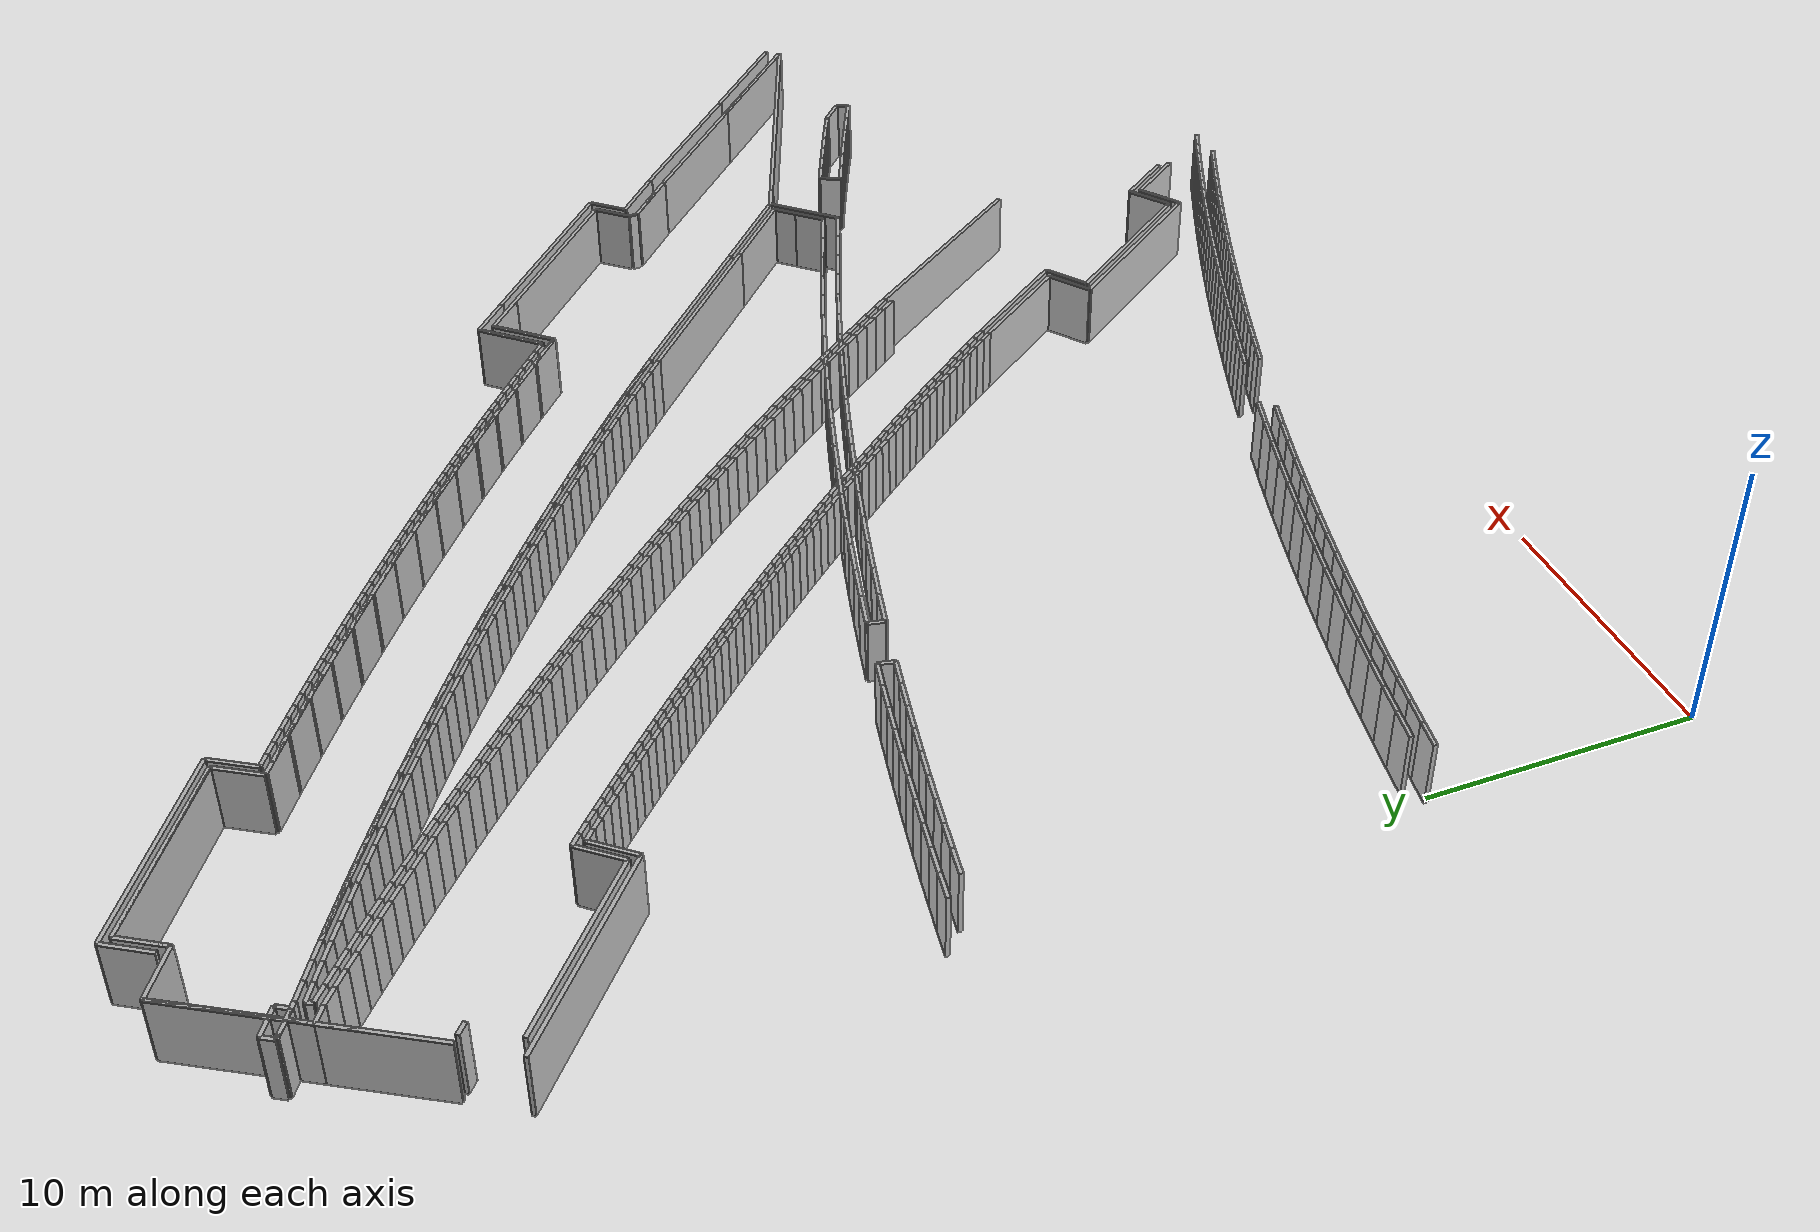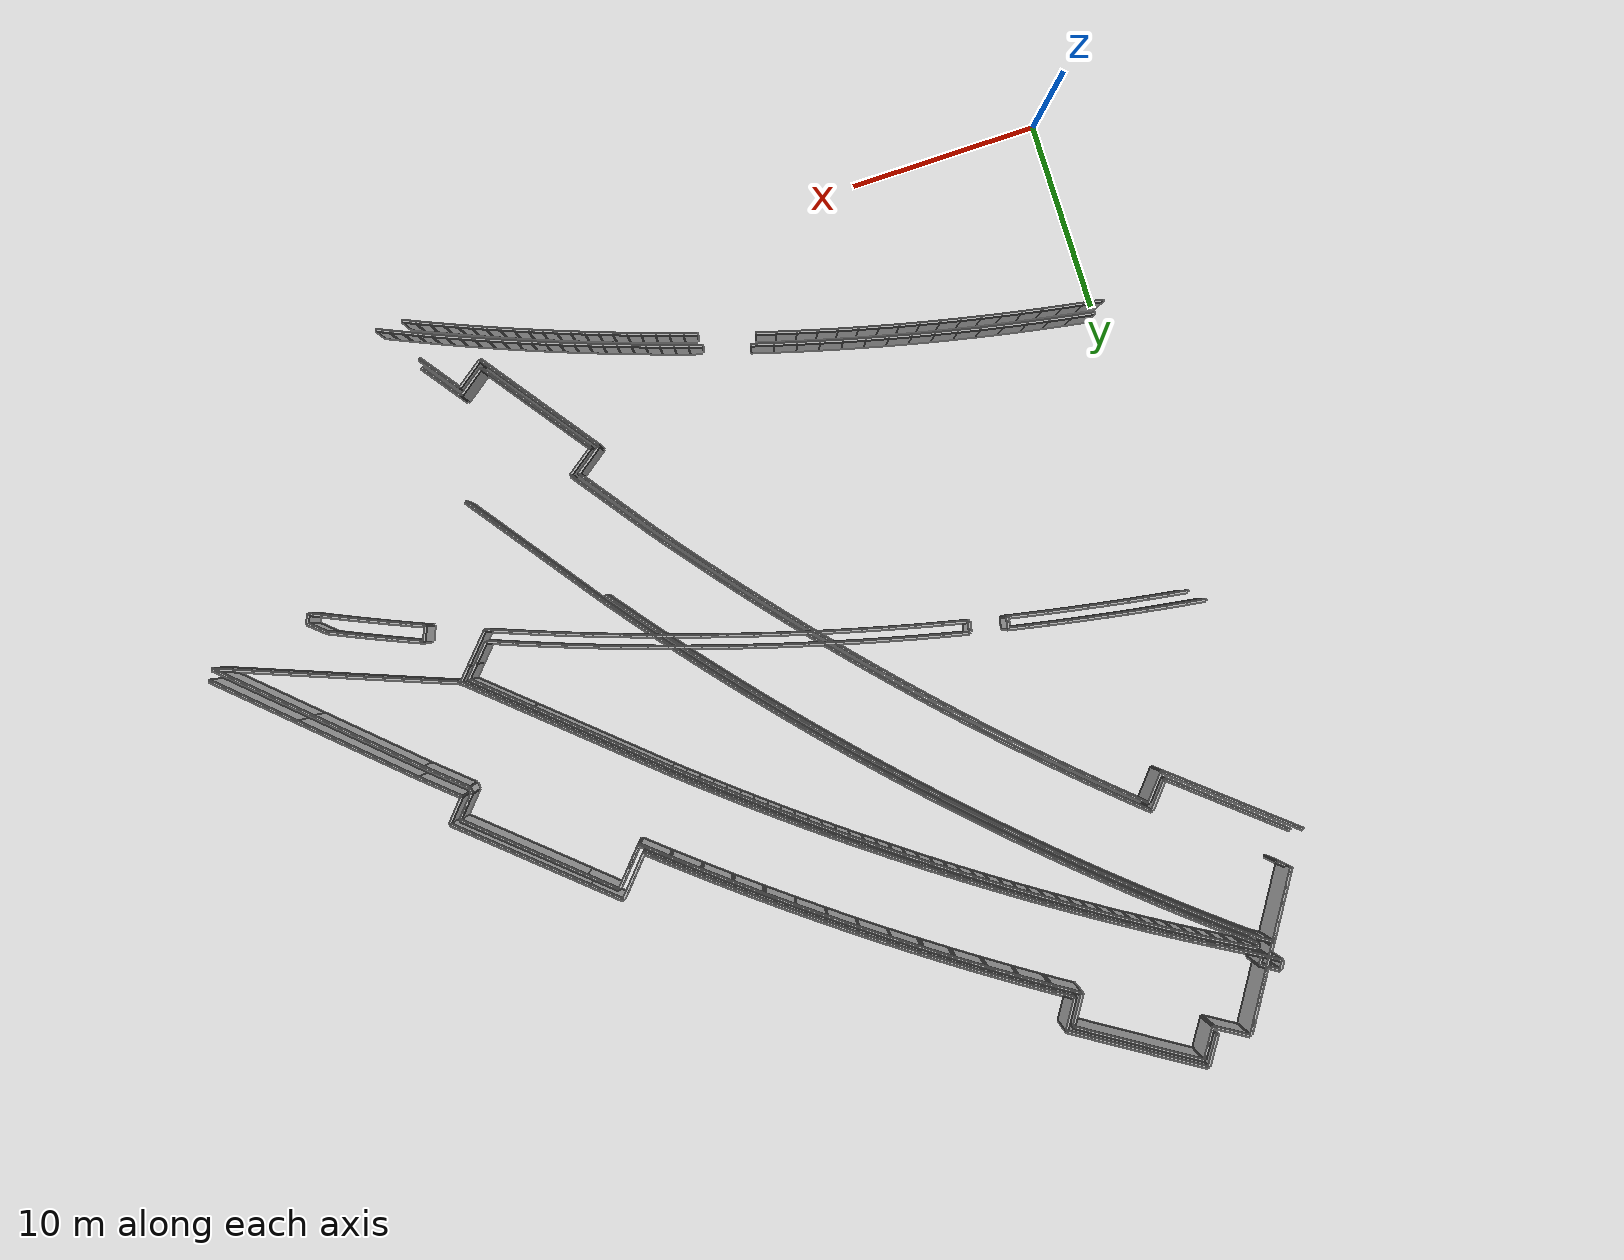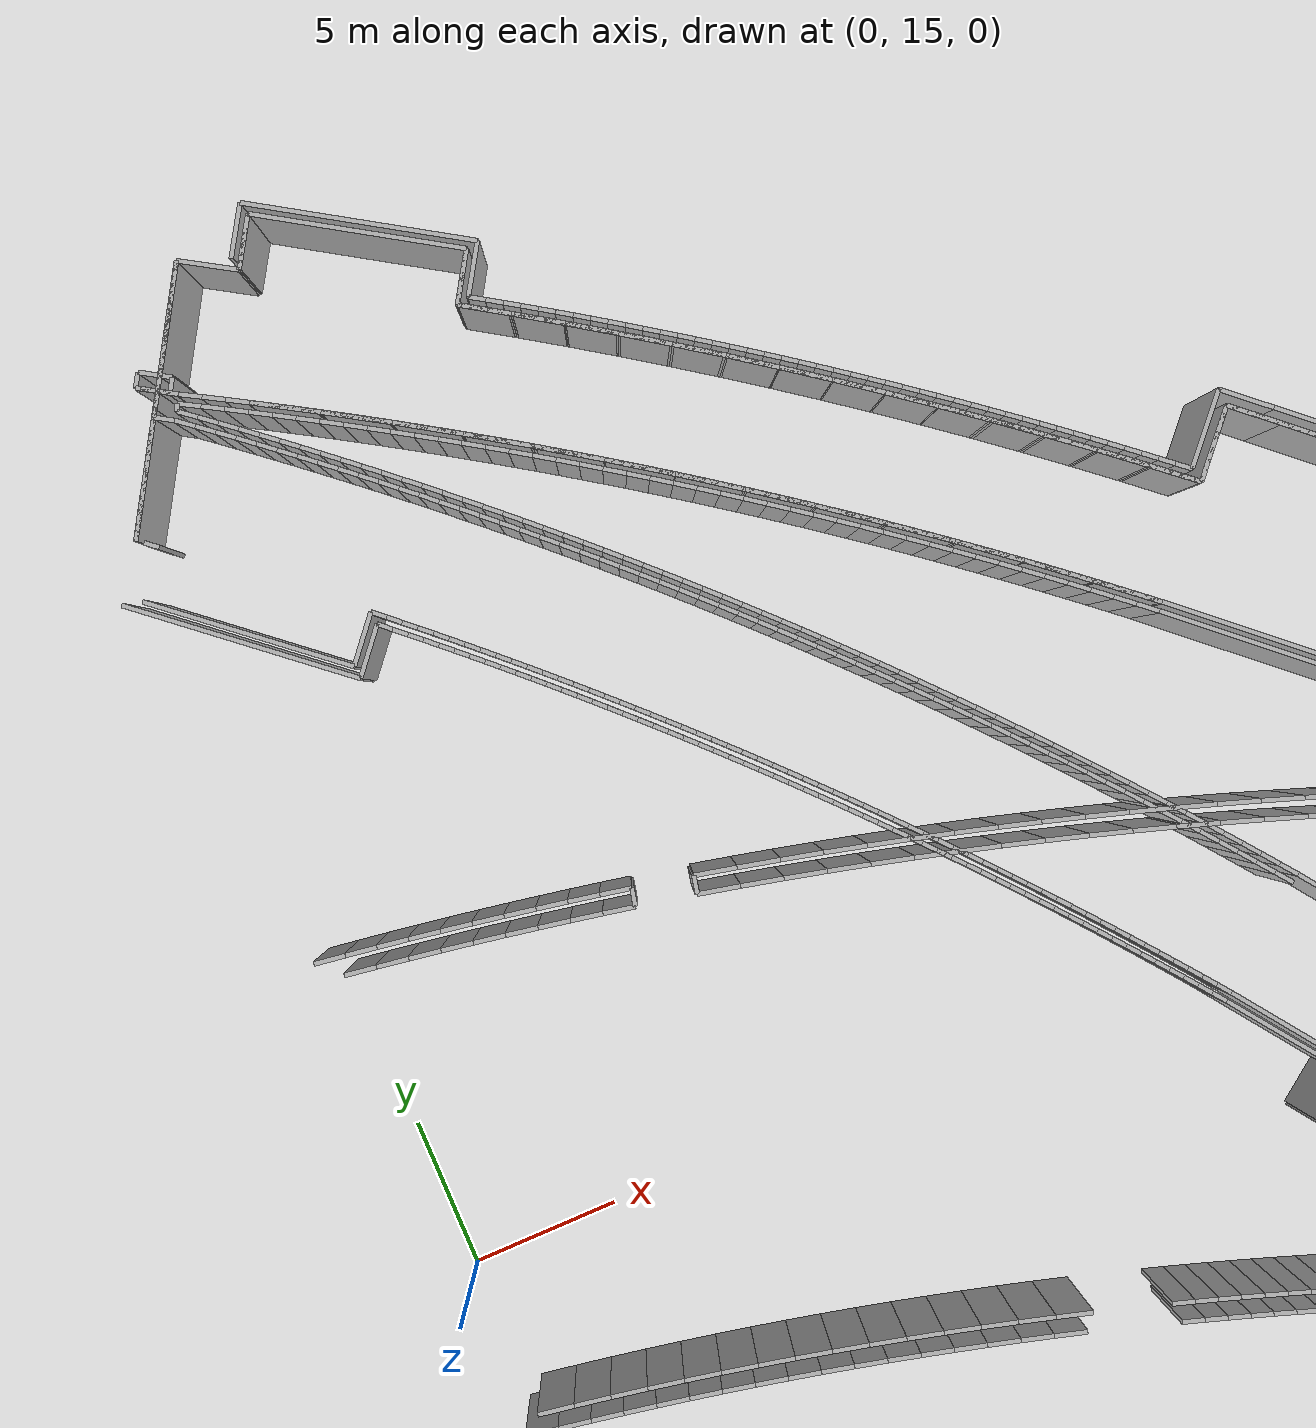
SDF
<?xml version="1.0" ?>
<sdf version="1.6">
  <model name="sps_0506">
    <pose frame="">0 0 0 0 -0 0</pose>
    <static>1</static>
    <self_collide>0</self_collide>
    <allow_auto_disable>0</allow_auto_disable>
    <link name="Wall77">
      <kinematic>0</kinematic>
      <gravity>1</gravity>
      <self_collide>0</self_collide>
      <collision name="collision">
        <geometry>
          <box>
            <size>0.838576 0.15 2.5</size>
          </box>
        </geometry>
        <pose frame="">0 0 0 0 -0 0</pose>
      </collision>
      <visual name="visual">
        <geometry>
          <box>
            <size>0.838576 0.15 2.5</size>
          </box>
        </geometry>
        <pose frame="">0 0 0 0 -0 0</pose>
        <cast_shadows>1</cast_shadows>
        <transparency>0.0</transparency>
      </visual>
      <pose frame="">2.00286 44.7527 1.25 0 0 -2.12094</pose>
    </link>
    <link name="Wall78">
      <kinematic>0</kinematic>
      <gravity>1</gravity>
      <self_collide>0</self_collide>
      <collision name="collision">
        <geometry>
          <box>
            <size>0.659275 0.15 2.5</size>
          </box>
        </geometry>
        <pose frame="">0 0 0 0 -0 0</pose>
      </collision>
      <visual name="visual">
        <geometry>
          <box>
            <size>0.659275 0.15 2.5</size>
          </box>
        </geometry>
        <pose frame="">0 0 0 0 -0 0</pose>
        <cast_shadows>1</cast_shadows>
        <transparency>0.0</transparency>
      </visual>
      <pose frame="">2.50326 44.9381 1.25 0 -0 2.59255</pose>
    </link>
    <link name="Wall79">
      <kinematic>0</kinematic>
      <gravity>1</gravity>
      <self_collide>0</self_collide>
      <collision name="collision">
        <geometry>
          <box>
            <size>7.89992 0.15 2.5</size>
          </box>
        </geometry>
        <pose frame="">0 0 0 0 -0 0</pose>
      </collision>
      <visual name="visual">
        <geometry>
          <box>
            <size>7.89992 0.15 2.5</size>
          </box>
        </geometry>
        <pose frame="">0 0 0 0 -0 0</pose>
        <cast_shadows>1</cast_shadows>
        <transparency>0.0</transparency>
      </visual>
      <pose frame="">1.51946 36.7798 1.25 0 0 -0.702542</pose>
    </link>
    <link name="Wall80">
      <kinematic>0</kinematic>
      <gravity>1</gravity>
      <self_collide>0</self_collide>
      <collision name="collision">
        <geometry>
          <box>
            <size>1.78292 0.15 2.5</size>
          </box>
        </geometry>
        <pose frame="">0 0 0 0 -0 0</pose>
      </collision>
      <visual name="visual">
        <geometry>
          <box>
            <size>1.78292 0.15 2.5</size>
          </box>
        </geometry>
        <pose frame="">0 0 0 0 -0 0</pose>
        <cast_shadows>1</cast_shadows>
        <transparency>0.0</transparency>
      </visual>
      <pose frame="">6.49825 48.8022 1.25 0 -0 1.00621</pose>
    </link>
    <link name="Wall104">
      <kinematic>0</kinematic>
      <gravity>1</gravity>
      <self_collide>0</self_collide>
      <collision name="collision">
        <geometry>
          <box>
            <size>6.99921 0.15 2.5</size>
          </box>
        </geometry>
        <pose frame="">0 0 0 0 -0 0</pose>
      </collision>
      <visual name="visual">
        <geometry>
          <box>
            <size>6.99921 0.15 2.5</size>
          </box>
        </geometry>
        <pose frame="">0 0 0 0 -0 0</pose>
        <cast_shadows>1</cast_shadows>
        <transparency>0.0</transparency>
      </visual>
      <pose frame="">29.4711 6.28789 1.25 0 0 -0.939945</pose>
    </link>
    <link name="Wall105">
      <kinematic>0</kinematic>
      <gravity>1</gravity>
      <self_collide>0</self_collide>
      <collision name="collision">
        <geometry>
          <box>
            <size>2.65269 0.15 2.5</size>
          </box>
        </geometry>
        <pose frame="">0 0 0 0 -0 0</pose>
      </collision>
      <visual name="visual">
        <geometry>
          <box>
            <size>2.65269 0.15 2.5</size>
          </box>
        </geometry>
        <pose frame="">0 0 0 0 -0 0</pose>
        <cast_shadows>1</cast_shadows>
        <transparency>0.0</transparency>
      </visual>
      <pose frame="">32.2076 30.9139 1.25 0 0 -2.29715</pose>
    </link>
    <link name="Wall107">
      <kinematic>0</kinematic>
      <gravity>1</gravity>
      <self_collide>0</self_collide>
      <collision name="collision">
        <geometry>
          <box>
            <size>1.55015 0.15 2.5</size>
          </box>
        </geometry>
        <pose frame="">0 0 0 0 -0 0</pose>
      </collision>
      <visual name="visual">
        <geometry>
          <box>
            <size>1.55015 0.15 2.5</size>
          </box>
        </geometry>
        <pose frame="">0 0 0 0 -0 0</pose>
        <cast_shadows>1</cast_shadows>
        <transparency>0.0</transparency>
      </visual>
      <pose frame="">39.9011 24.8184 1.25 0 -0 0.84454</pose>
    </link>
    <link name="Wall109">
      <kinematic>0</kinematic>
      <gravity>1</gravity>
      <self_collide>0</self_collide>
      <collision name="collision">
        <geometry>
          <box>
            <size>0.49973 0.15 2.5</size>
          </box>
        </geometry>
        <pose frame="">0 0 0 0 -0 0</pose>
      </collision>
      <visual name="visual">
        <geometry>
          <box>
            <size>0.49973 0.15 2.5</size>
          </box>
        </geometry>
        <pose frame="">0 0 0 0 -0 0</pose>
        <cast_shadows>1</cast_shadows>
        <transparency>0.0</transparency>
      </visual>
      <pose frame="">44.1179 13.009 1.25 0 0 -2.00494</pose>
    </link>
    <link name="Wall110">
      <kinematic>0</kinematic>
      <gravity>1</gravity>
      <self_collide>0</self_collide>
      <collision name="collision">
        <geometry>
          <box>
            <size>1.1591 0.15 2.5</size>
          </box>
        </geometry>
        <pose frame="">0 0 0 0 -0 0</pose>
      </collision>
      <visual name="visual">
        <geometry>
          <box>
            <size>1.1591 0.15 2.5</size>
          </box>
        </geometry>
        <pose frame="">0 0 0 0 -0 0</pose>
        <cast_shadows>1</cast_shadows>
        <transparency>0.0</transparency>
      </visual>
      <pose frame="">43.7884 13.619 1.25 0 0 -0.722654</pose>
    </link>
    <link name="Wall113">
      <kinematic>0</kinematic>
      <gravity>1</gravity>
      <self_collide>0</self_collide>
      <collision name="collision">
        <geometry>
          <box>
            <size>6.27489 0.15 2.5</size>
          </box>
        </geometry>
        <pose frame="">0 0 0 0 -0 0</pose>
      </collision>
      <visual name="visual">
        <geometry>
          <box>
            <size>6.27489 0.15 2.5</size>
          </box>
        </geometry>
        <pose frame="">0 0 0 0 -0 0</pose>
        <cast_shadows>1</cast_shadows>
        <transparency>0.0</transparency>
      </visual>
      <pose frame="">43.1125 20.0304 1.25 0 0 -0.749431</pose>
    </link>
    <link name="Wall114">
      <kinematic>0</kinematic>
      <gravity>1</gravity>
      <self_collide>0</self_collide>
      <collision name="collision">
        <geometry>
          <box>
            <size>5.77521 0.15 2.5</size>
          </box>
        </geometry>
        <pose frame="">0 0 0 0 -0 0</pose>
      </collision>
      <visual name="visual">
        <geometry>
          <box>
            <size>5.77521 0.15 2.5</size>
          </box>
        </geometry>
        <pose frame="">0 0 0 0 -0 0</pose>
        <cast_shadows>1</cast_shadows>
        <transparency>0.0</transparency>
      </visual>
      <pose frame="">47.5233 15.926 1.25 0 0 -0.749431</pose>
    </link>
    <link name="Wall144">
      <kinematic>0</kinematic>
      <gravity>1</gravity>
      <self_collide>0</self_collide>
      <collision name="collision">
        <geometry>
          <box>
            <size>8.69656 0.15 2.5</size>
          </box>
        </geometry>
        <pose frame="">0 0 0 0 -0 0</pose>
      </collision>
      <visual name="visual">
        <geometry>
          <box>
            <size>8.69656 0.15 2.5</size>
          </box>
        </geometry>
        <pose frame="">0 0 0 0 -0 0</pose>
        <cast_shadows>1</cast_shadows>
        <transparency>0.0</transparency>
      </visual>
      <pose frame="">31.9048 13.297 1.25 0 -0 2.2016</pose>
    </link>
    <link name="Wall470">
      <kinematic>0</kinematic>
      <gravity>1</gravity>
      <self_collide>0</self_collide>
      <collision name="collision">
        <geometry>
          <box>
            <size>0.497983 0.15 2.5</size>
          </box>
        </geometry>
        <pose frame="">0 0 0 0 -0 0</pose>
      </collision>
      <visual name="visual">
        <geometry>
          <box>
            <size>0.497983 0.15 2.5</size>
          </box>
        </geometry>
        <pose frame="">0 0 0 0 -0 0</pose>
        <cast_shadows>1</cast_shadows>
        <transparency>0.0</transparency>
      </visual>
      <pose frame="">0.129661 40.7086 1.25 0 0 -0.70158</pose>
    </link>
    <link name="Wall473">
      <kinematic>0</kinematic>
      <gravity>1</gravity>
      <self_collide>0</self_collide>
      <collision name="collision">
        <geometry>
          <box>
            <size>0.246013 0.15 2.5</size>
          </box>
        </geometry>
        <pose frame="">0 0 0 0 -0 0</pose>
      </collision>
      <visual name="visual">
        <geometry>
          <box>
            <size>0.246013 0.15 2.5</size>
          </box>
        </geometry>
        <pose frame="">0 0 0 0 -0 0</pose>
        <cast_shadows>1</cast_shadows>
        <transparency>0.0</transparency>
      </visual>
      <pose frame="">2.58913 44.3913 1.25 0 -0 1.18144</pose>
    </link>
    <link name="Wall474">
      <kinematic>0</kinematic>
      <gravity>1</gravity>
      <self_collide>0</self_collide>
      <collision name="collision">
        <geometry>
          <box>
            <size>7.0003 0.15 2.5</size>
          </box>
        </geometry>
        <pose frame="">0 0 0 0 -0 0</pose>
      </collision>
      <visual name="visual">
        <geometry>
          <box>
            <size>7.0003 0.15 2.5</size>
          </box>
        </geometry>
        <pose frame="">0 0 0 0 -0 0</pose>
        <cast_shadows>1</cast_shadows>
        <transparency>0.0</transparency>
      </visual>
      <pose frame="">1.82793 36.9118 1.25 0 0 -0.702554</pose>
    </link>
    <link name="Wall486">
      <kinematic>0</kinematic>
      <gravity>1</gravity>
      <self_collide>0</self_collide>
      <collision name="collision">
        <geometry>
          <box>
            <size>4.68089 0.15 2.5</size>
          </box>
        </geometry>
        <pose frame="">0 0 0 0 -0 0</pose>
      </collision>
      <visual name="visual">
        <geometry>
          <box>
            <size>4.68089 0.15 2.5</size>
          </box>
        </geometry>
        <pose frame="">0 0 0 0 -0 0</pose>
        <cast_shadows>1</cast_shadows>
        <transparency>0.0</transparency>
      </visual>
      <pose frame="">27.061 12.1316 1.25 0 0 -0.940045</pose>
    </link>
    <link name="Wall487">
      <kinematic>0</kinematic>
      <gravity>1</gravity>
      <self_collide>0</self_collide>
      <collision name="collision">
        <geometry>
          <box>
            <size>1.8003 0.15 2.5</size>
          </box>
        </geometry>
        <pose frame="">0 0 0 0 -0 0</pose>
      </collision>
      <visual name="visual">
        <geometry>
          <box>
            <size>1.8003 0.15 2.5</size>
          </box>
        </geometry>
        <pose frame="">0 0 0 0 -0 0</pose>
        <cast_shadows>1</cast_shadows>
        <transparency>0.0</transparency>
      </visual>
      <pose frame="">28.1337 9.645 1.25 0 0 -2.51052</pose>
    </link>
    <link name="Wall488">
      <kinematic>0</kinematic>
      <gravity>1</gravity>
      <self_collide>0</self_collide>
      <collision name="collision">
        <geometry>
          <box>
            <size>4.98693 0.15 2.5</size>
          </box>
        </geometry>
        <pose frame="">0 0 0 0 -0 0</pose>
      </collision>
      <visual name="visual">
        <geometry>
          <box>
            <size>4.98693 0.15 2.5</size>
          </box>
        </geometry>
        <pose frame="">0 0 0 0 -0 0</pose>
        <cast_shadows>1</cast_shadows>
        <transparency>0.0</transparency>
      </visual>
      <pose frame="">27.3896 12.1896 1.25 0 0 -0.939912</pose>
    </link>
    <link name="Wall489">
      <kinematic>0</kinematic>
      <gravity>1</gravity>
      <self_collide>0</self_collide>
      <collision name="collision">
        <geometry>
          <box>
            <size>7.59147 0.15 2.5</size>
          </box>
        </geometry>
        <pose frame="">0 0 0 0 -0 0</pose>
      </collision>
      <visual name="visual">
        <geometry>
          <box>
            <size>7.59147 0.15 2.5</size>
          </box>
        </geometry>
        <pose frame="">0 0 0 0 -0 0</pose>
        <cast_shadows>1</cast_shadows>
        <transparency>0.0</transparency>
      </visual>
      <pose frame="">31.6313 23.9044 1.25 0 0 -0.726192</pose>
    </link>
    <link name="Wall490">
      <kinematic>0</kinematic>
      <gravity>1</gravity>
      <self_collide>0</self_collide>
      <collision name="collision">
        <geometry>
          <box>
            <size>4.16825 0.15 2.5</size>
          </box>
        </geometry>
        <pose frame="">0 0 0 0 -0 0</pose>
      </collision>
      <visual name="visual">
        <geometry>
          <box>
            <size>4.16825 0.15 2.5</size>
          </box>
        </geometry>
        <pose frame="">0 0 0 0 -0 0</pose>
        <cast_shadows>1</cast_shadows>
        <transparency>0.0</transparency>
      </visual>
      <pose frame="">36.0278 20 1.25 0 0 -0.726192</pose>
    </link>
    <link name="Wall817">
      <kinematic>0</kinematic>
      <gravity>1</gravity>
      <self_collide>0</self_collide>
      <collision name="collision">
        <geometry>
          <box>
            <size>0.599651 0.15 2.5</size>
          </box>
        </geometry>
        <pose frame="">0 0 0 0 -0 0</pose>
      </collision>
      <visual name="visual">
        <geometry>
          <box>
            <size>0.599651 0.15 2.5</size>
          </box>
        </geometry>
        <pose frame="">0 0 0 0 -0 0</pose>
        <cast_shadows>1</cast_shadows>
        <transparency>0.0</transparency>
      </visual>
      <pose frame="">11.689 24.0409 1.25 0 0 -1.78121</pose>
    </link>
    <link name="Wall818">
      <kinematic>0</kinematic>
      <gravity>1</gravity>
      <self_collide>0</self_collide>
      <collision name="collision">
        <geometry>
          <box>
            <size>7.00085 0.15 2.5</size>
          </box>
        </geometry>
        <pose frame="">0 0 0 0 -0 0</pose>
      </collision>
      <visual name="visual">
        <geometry>
          <box>
            <size>7.00085 0.15 2.5</size>
          </box>
        </geometry>
        <pose frame="">0 0 0 0 -0 0</pose>
        <cast_shadows>1</cast_shadows>
        <transparency>0.0</transparency>
      </visual>
      <pose frame="">10.0257 47.2686 1.25 0 0 -0.56443</pose>
    </link>
    <link name="Wall823">
      <kinematic>0</kinematic>
      <gravity>1</gravity>
      <self_collide>0</self_collide>
      <collision name="collision">
        <geometry>
          <box>
            <size>1.80035 0.15 2.5</size>
          </box>
        </geometry>
        <pose frame="">0 0 0 0 -0 0</pose>
      </collision>
      <visual name="visual">
        <geometry>
          <box>
            <size>1.80035 0.15 2.5</size>
          </box>
        </geometry>
        <pose frame="">0 0 0 0 -0 0</pose>
        <cast_shadows>1</cast_shadows>
        <transparency>0.0</transparency>
      </visual>
      <pose frame="">27.7144 9.71037 1.25 0 0 -2.51054</pose>
    </link>
    <link name="Wall824">
      <kinematic>0</kinematic>
      <gravity>1</gravity>
      <self_collide>0</self_collide>
      <collision name="collision">
        <geometry>
          <box>
            <size>7.59909 0.15 2.5</size>
          </box>
        </geometry>
        <pose frame="">0 0 0 0 -0 0</pose>
      </collision>
      <visual name="visual">
        <geometry>
          <box>
            <size>7.59909 0.15 2.5</size>
          </box>
        </geometry>
        <pose frame="">0 0 0 0 -0 0</pose>
        <cast_shadows>1</cast_shadows>
        <transparency>0.0</transparency>
      </visual>
      <pose frame="">29.2286 6.11098 1.25 0 0 -0.939976</pose>
    </link>
    <link name="Wall825">
      <kinematic>0</kinematic>
      <gravity>1</gravity>
      <self_collide>0</self_collide>
      <collision name="collision">
        <geometry>
          <box>
            <size>1.80066 0.15 2.5</size>
          </box>
        </geometry>
        <pose frame="">0 0 0 0 -0 0</pose>
      </collision>
      <visual name="visual">
        <geometry>
          <box>
            <size>1.80066 0.15 2.5</size>
          </box>
        </geometry>
        <pose frame="">0 0 0 0 -0 0</pose>
        <cast_shadows>1</cast_shadows>
        <transparency>0.0</transparency>
      </visual>
      <pose frame="">32.1968 3.5735 1.25 0 -0 0.630546</pose>
    </link>
    <link name="Wall826">
      <kinematic>0</kinematic>
      <gravity>1</gravity>
      <self_collide>0</self_collide>
      <collision name="collision">
        <geometry>
          <box>
            <size>0.980486 0.15 2.5</size>
          </box>
        </geometry>
        <pose frame="">0 0 0 0 -0 0</pose>
      </collision>
      <visual name="visual">
        <geometry>
          <box>
            <size>0.980486 0.15 2.5</size>
          </box>
        </geometry>
        <pose frame="">0 0 0 0 -0 0</pose>
        <cast_shadows>1</cast_shadows>
        <transparency>0.0</transparency>
      </visual>
      <pose frame="">37.255 18.2546 1.25 0 0 -2.31236</pose>
    </link>
    <link name="Wall827">
      <kinematic>0</kinematic>
      <gravity>1</gravity>
      <self_collide>0</self_collide>
      <collision name="collision">
        <geometry>
          <box>
            <size>2.00484 0.15 2.5</size>
          </box>
        </geometry>
        <pose frame="">0 0 0 0 -0 0</pose>
      </collision>
      <visual name="visual">
        <geometry>
          <box>
            <size>2.00484 0.15 2.5</size>
          </box>
        </geometry>
        <pose frame="">0 0 0 0 -0 0</pose>
        <cast_shadows>1</cast_shadows>
        <transparency>0.0</transparency>
      </visual>
      <pose frame="">36.2467 17.1539 1.25 0 0 -2.31236</pose>
    </link>
    <link name="Wall829">
      <kinematic>0</kinematic>
      <gravity>1</gravity>
      <self_collide>0</self_collide>
      <collision name="collision">
        <geometry>
          <box>
            <size>7.95297 0.15 2.5</size>
          </box>
        </geometry>
        <pose frame="">0 0 0 0 -0 0</pose>
      </collision>
      <visual name="visual">
        <geometry>
          <box>
            <size>7.95297 0.15 2.5</size>
          </box>
        </geometry>
        <pose frame="">0 0 0 0 -0 0</pose>
        <cast_shadows>1</cast_shadows>
        <transparency>0.0</transparency>
      </visual>
      <pose frame="">37.4426 28.0385 1.25 0 -0 2.41538</pose>
    </link>
    <link name="Wall830">
      <kinematic>0</kinematic>
      <gravity>1</gravity>
      <self_collide>0</self_collide>
      <collision name="collision">
        <geometry>
          <box>
            <size>1.84698 0.15 2.5</size>
          </box>
        </geometry>
        <pose frame="">0 0 0 0 -0 0</pose>
      </collision>
      <visual name="visual">
        <geometry>
          <box>
            <size>1.84698 0.15 2.5</size>
          </box>
        </geometry>
        <pose frame="">0 0 0 0 -0 0</pose>
        <cast_shadows>1</cast_shadows>
        <transparency>0.0</transparency>
      </visual>
      <pose frame="">33.779 31.2922 1.25 0 -0 2.41538</pose>
    </link>
    <link name="Wall1211">
      <kinematic>0</kinematic>
      <gravity>1</gravity>
      <self_collide>0</self_collide>
      <collision name="collision">
        <geometry>
          <box>
            <size>1.79992 0.15 2.5</size>
          </box>
        </geometry>
        <pose frame="">0 0 0 0 -0 0</pose>
      </collision>
      <visual name="visual">
        <geometry>
          <box>
            <size>1.79992 0.15 2.5</size>
          </box>
        </geometry>
        <pose frame="">0 0 0 0 -0 0</pose>
        <cast_shadows>1</cast_shadows>
        <transparency>0.0</transparency>
      </visual>
      <pose frame="">6.58684 48.3807 1.25 0 -0 1.00637</pose>
    </link>
    <link name="Wall1218">
      <kinematic>0</kinematic>
      <gravity>1</gravity>
      <self_collide>0</self_collide>
      <collision name="collision">
        <geometry>
          <box>
            <size>7.60127 0.15 2.5</size>
          </box>
        </geometry>
        <pose frame="">0 0 0 0 -0 0</pose>
      </collision>
      <visual name="visual">
        <geometry>
          <box>
            <size>7.60127 0.15 2.5</size>
          </box>
        </geometry>
        <pose frame="">0 0 0 0 -0 0</pose>
        <cast_shadows>1</cast_shadows>
        <transparency>0.0</transparency>
      </visual>
      <pose frame="">10.1864 47.5222 1.25 0 -0 2.57716</pose>
    </link>
    <link name="Wall1239">
      <kinematic>0</kinematic>
      <gravity>1</gravity>
      <self_collide>0</self_collide>
      <collision name="collision">
        <geometry>
          <box>
            <size>2.45108 0.15 2.5</size>
          </box>
        </geometry>
        <pose frame="">0 0 0 0 -0 0</pose>
      </collision>
      <visual name="visual">
        <geometry>
          <box>
            <size>2.45108 0.15 2.5</size>
          </box>
        </geometry>
        <pose frame="">0 0 0 0 -0 0</pose>
        <cast_shadows>1</cast_shadows>
        <transparency>0.0</transparency>
      </visual>
      <pose frame="">40.3028 23.4252 1.25 0 -0 2.41548</pose>
    </link>
    <link name="Wall1526">
      <kinematic>0</kinematic>
      <gravity>1</gravity>
      <self_collide>0</self_collide>
      <collision name="collision">
        <geometry>
          <box>
            <size>0.600265 0.15 2.5</size>
          </box>
        </geometry>
        <pose frame="">0 0 0 0 -0 0</pose>
      </collision>
      <visual name="visual">
        <geometry>
          <box>
            <size>0.600265 0.15 2.5</size>
          </box>
        </geometry>
        <pose frame="">0 0 0 0 -0 0</pose>
        <cast_shadows>1</cast_shadows>
        <transparency>0.0</transparency>
      </visual>
      <pose frame="">9.73165 24.4502 1.25 0 -0 1.35998</pose>
    </link>
    <link name="Wall1528">
      <kinematic>0</kinematic>
      <gravity>1</gravity>
      <self_collide>0</self_collide>
      <collision name="collision">
        <geometry>
          <box>
            <size>1.79999 0.15 2.5</size>
          </box>
        </geometry>
        <pose frame="">0 0 0 0 -0 0</pose>
      </collision>
      <visual name="visual">
        <geometry>
          <box>
            <size>1.79999 0.15 2.5</size>
          </box>
        </geometry>
        <pose frame="">0 0 0 0 -0 0</pose>
        <cast_shadows>1</cast_shadows>
        <transparency>0.0</transparency>
      </visual>
      <pose frame="">12.5018 44.6357 1.25 0 0 -2.13528</pose>
    </link>
    <link name="Wall1531">
      <kinematic>0</kinematic>
      <gravity>1</gravity>
      <self_collide>0</self_collide>
      <collision name="collision">
        <geometry>
          <box>
            <size>1.20544 0.15 2.5</size>
          </box>
        </geometry>
        <pose frame="">0 0 0 0 -0 0</pose>
      </collision>
      <visual name="visual">
        <geometry>
          <box>
            <size>1.20544 0.15 2.5</size>
          </box>
        </geometry>
        <pose frame="">0 0 0 0 -0 0</pose>
        <cast_shadows>1</cast_shadows>
        <transparency>0.0</transparency>
      </visual>
      <pose frame="">36.1128 17.4496 1.25 0 -0 0.826845</pose>
    </link>
    <link name="Wall1532">
      <kinematic>0</kinematic>
      <gravity>1</gravity>
      <self_collide>0</self_collide>
      <collision name="collision">
        <geometry>
          <box>
            <size>0.947549 0.15 2.5</size>
          </box>
        </geometry>
        <pose frame="">0 0 0 0 -0 0</pose>
      </collision>
      <visual name="visual">
        <geometry>
          <box>
            <size>0.947549 0.15 2.5</size>
          </box>
        </geometry>
        <pose frame="">0 0 0 0 -0 0</pose>
        <cast_shadows>1</cast_shadows>
        <transparency>0.0</transparency>
      </visual>
      <pose frame="">36.8418 18.2417 1.25 0 -0 0.826845</pose>
    </link>
    <link name="Wall1533">
      <kinematic>0</kinematic>
      <gravity>1</gravity>
      <self_collide>0</self_collide>
      <collision name="collision">
        <geometry>
          <box>
            <size>3.60227 0.15 2.5</size>
          </box>
        </geometry>
        <pose frame="">0 0 0 0 -0 0</pose>
      </collision>
      <visual name="visual">
        <geometry>
          <box>
            <size>3.60227 0.15 2.5</size>
          </box>
        </geometry>
        <pose frame="">0 0 0 0 -0 0</pose>
        <cast_shadows>1</cast_shadows>
        <transparency>0.0</transparency>
      </visual>
      <pose frame="">35.8161 19.7864 1.25 0 -0 2.41531</pose>
    </link>
    <link name="Wall1534">
      <kinematic>0</kinematic>
      <gravity>1</gravity>
      <self_collide>0</self_collide>
      <collision name="collision">
        <geometry>
          <box>
            <size>7.85363 0.15 2.5</size>
          </box>
        </geometry>
        <pose frame="">0 0 0 0 -0 0</pose>
      </collision>
      <visual name="visual">
        <geometry>
          <box>
            <size>7.85363 0.15 2.5</size>
          </box>
        </geometry>
        <pose frame="">0 0 0 0 -0 0</pose>
        <cast_shadows>1</cast_shadows>
        <transparency>0.0</transparency>
      </visual>
      <pose frame="">31.5336 23.5903 1.25 0 -0 2.41531</pose>
    </link>
    <link name="Wall1536">
      <kinematic>0</kinematic>
      <gravity>1</gravity>
      <self_collide>0</self_collide>
      <collision name="collision">
        <geometry>
          <box>
            <size>0.354007 0.15 2.5</size>
          </box>
        </geometry>
        <pose frame="">0 0 0 0 -0 0</pose>
      </collision>
      <visual name="visual">
        <geometry>
          <box>
            <size>0.354007 0.15 2.5</size>
          </box>
        </geometry>
        <pose frame="">0 0 0 0 -0 0</pose>
        <cast_shadows>1</cast_shadows>
        <transparency>0.0</transparency>
      </visual>
      <pose frame="">38.8656 24.0664 1.25 0 0 -1.51491</pose>
    </link>
    <link name="Wall1537">
      <kinematic>0</kinematic>
      <gravity>1</gravity>
      <self_collide>0</self_collide>
      <collision name="collision">
        <geometry>
          <box>
            <size>1.49997 0.15 2.5</size>
          </box>
        </geometry>
        <pose frame="">0 0 0 0 -0 0</pose>
      </collision>
      <visual name="visual">
        <geometry>
          <box>
            <size>1.49997 0.15 2.5</size>
          </box>
        </geometry>
        <pose frame="">0 0 0 0 -0 0</pose>
        <cast_shadows>1</cast_shadows>
        <transparency>0.0</transparency>
      </visual>
      <pose frame="">39.3537 24.8039 1.25 0 0 -2.29695</pose>
    </link>
    <link name="Wall1835">
      <kinematic>0</kinematic>
      <gravity>1</gravity>
      <self_collide>0</self_collide>
      <collision name="collision">
        <geometry>
          <box>
            <size>1.79998 0.15 2.5</size>
          </box>
        </geometry>
        <pose frame="">0 0 0 0 -0 0</pose>
      </collision>
      <visual name="visual">
        <geometry>
          <box>
            <size>1.79998 0.15 2.5</size>
          </box>
        </geometry>
        <pose frame="">0 0 0 0 -0 0</pose>
        <cast_shadows>1</cast_shadows>
        <transparency>0.0</transparency>
      </visual>
      <pose frame="">12.9161 44.7287 1.25 0 -0 1.00639</pose>
    </link>
    <link name="Wall1846">
      <kinematic>0</kinematic>
      <gravity>1</gravity>
      <self_collide>0</self_collide>
      <collision name="collision">
        <geometry>
          <box>
            <size>0.839474 0.15 2.5</size>
          </box>
        </geometry>
        <pose frame="">0 0 0 0 -0 0</pose>
      </collision>
      <visual name="visual">
        <geometry>
          <box>
            <size>0.839474 0.15 2.5</size>
          </box>
        </geometry>
        <pose frame="">0 0 0 0 -0 0</pose>
        <cast_shadows>1</cast_shadows>
        <transparency>0.0</transparency>
      </visual>
      <pose frame="">38.5991 15.6241 1.25 0 -0 1.17451</pose>
    </link>
    <link name="Wall1848">
      <kinematic>0</kinematic>
      <gravity>1</gravity>
      <self_collide>0</self_collide>
      <collision name="collision">
        <geometry>
          <box>
            <size>2.62022 0.15 2.5</size>
          </box>
        </geometry>
        <pose frame="">0 0 0 0 -0 0</pose>
      </collision>
      <visual name="visual">
        <geometry>
          <box>
            <size>2.62022 0.15 2.5</size>
          </box>
        </geometry>
        <pose frame="">0 0 0 0 -0 0</pose>
        <cast_shadows>1</cast_shadows>
        <transparency>0.0</transparency>
      </visual>
      <pose frame="">33.6967 3.04635 1.25 0 0 -0.939982</pose>
    </link>
    <link name="Wall2168">
      <kinematic>0</kinematic>
      <gravity>1</gravity>
      <self_collide>0</self_collide>
      <collision name="collision">
        <geometry>
          <box>
            <size>1.79253 0.15 2.5</size>
          </box>
        </geometry>
        <pose frame="">0 0 0 0 -0 0</pose>
      </collision>
      <visual name="visual">
        <geometry>
          <box>
            <size>1.79253 0.15 2.5</size>
          </box>
        </geometry>
        <pose frame="">0 0 0 0 -0 0</pose>
        <cast_shadows>1</cast_shadows>
        <transparency>0.0</transparency>
      </visual>
      <pose frame="">5.11336 34.9114 1.25 0 -0 0.868028</pose>
    </link>
    <link name="Wall2188">
      <kinematic>0</kinematic>
      <gravity>1</gravity>
      <self_collide>0</self_collide>
      <collision name="collision">
        <geometry>
          <box>
            <size>2.50991 0.15 2.5</size>
          </box>
        </geometry>
        <pose frame="">0 0 0 0 -0 0</pose>
      </collision>
      <visual name="visual">
        <geometry>
          <box>
            <size>2.50991 0.15 2.5</size>
          </box>
        </geometry>
        <pose frame="">0 0 0 0 -0 0</pose>
        <cast_shadows>1</cast_shadows>
        <transparency>0.0</transparency>
      </visual>
      <pose frame="">33.7292 3.50931 1.25 0 0 -0.939954</pose>
    </link>
    <link name="Wall2191">
      <kinematic>0</kinematic>
      <gravity>1</gravity>
      <self_collide>0</self_collide>
      <collision name="collision">
        <geometry>
          <box>
            <size>6.9261 0.15 2.5</size>
          </box>
        </geometry>
        <pose frame="">0 0 0 0 -0 0</pose>
      </collision>
      <visual name="visual">
        <geometry>
          <box>
            <size>6.9261 0.15 2.5</size>
          </box>
        </geometry>
        <pose frame="">0 0 0 0 -0 0</pose>
        <cast_shadows>1</cast_shadows>
        <transparency>0.0</transparency>
      </visual>
      <pose frame="">43.7544 20.2523 1.25 0 0 -0.749464</pose>
    </link>
    <link name="Wall2192">
      <kinematic>0</kinematic>
      <gravity>1</gravity>
      <self_collide>0</self_collide>
      <collision name="collision">
        <geometry>
          <box>
            <size>5.04841 0.15 2.5</size>
          </box>
        </geometry>
        <pose frame="">0 0 0 0 -0 0</pose>
      </collision>
      <visual name="visual">
        <geometry>
          <box>
            <size>5.04841 0.15 2.5</size>
          </box>
        </geometry>
        <pose frame="">0 0 0 0 -0 0</pose>
        <cast_shadows>1</cast_shadows>
        <transparency>0.0</transparency>
      </visual>
      <pose frame="">48.1374 16.1735 1.25 0 0 -0.749464</pose>
    </link>
    <link name="Wall2552">
      <kinematic>0</kinematic>
      <gravity>1</gravity>
      <self_collide>0</self_collide>
      <collision name="collision">
        <geometry>
          <box>
            <size>0.670188 0.15 2.5</size>
          </box>
        </geometry>
        <pose frame="">0 0 0 0 -0 0</pose>
      </collision>
      <visual name="visual">
        <geometry>
          <box>
            <size>0.670188 0.15 2.5</size>
          </box>
        </geometry>
        <pose frame="">0 0 0 0 -0 0</pose>
        <cast_shadows>1</cast_shadows>
        <transparency>0.0</transparency>
      </visual>
      <pose frame="">2.06905 44.2197 1.25 0 0 -0.551571</pose>
    </link>
    <link name="Wall2553">
      <kinematic>0</kinematic>
      <gravity>1</gravity>
      <self_collide>0</self_collide>
      <collision name="collision">
        <geometry>
          <box>
            <size>1.8003 0.15 2.5</size>
          </box>
        </geometry>
        <pose frame="">0 0 0 0 -0 0</pose>
      </collision>
      <visual name="visual">
        <geometry>
          <box>
            <size>1.8003 0.15 2.5</size>
          </box>
        </geometry>
        <pose frame="">0 0 0 0 -0 0</pose>
        <cast_shadows>1</cast_shadows>
        <transparency>0.0</transparency>
      </visual>
      <pose frame="">5.08074 35.3372 1.25 0 -0 0.86844</pose>
    </link>
    <link name="Wall2566">
      <kinematic>0</kinematic>
      <gravity>1</gravity>
      <self_collide>0</self_collide>
      <collision name="collision">
        <geometry>
          <box>
            <size>1.7997 0.15 2.5</size>
          </box>
        </geometry>
        <pose frame="">0 0 0 0 -0 0</pose>
      </collision>
      <visual name="visual">
        <geometry>
          <box>
            <size>1.7997 0.15 2.5</size>
          </box>
        </geometry>
        <pose frame="">0 0 0 0 -0 0</pose>
        <cast_shadows>1</cast_shadows>
        <transparency>0.0</transparency>
      </visual>
      <pose frame="">32.2621 3.99229 1.25 0 -0 0.63039</pose>
    </link>
    <link name="Wall2567">
      <kinematic>0</kinematic>
      <gravity>1</gravity>
      <self_collide>0</self_collide>
      <collision name="collision">
        <geometry>
          <box>
            <size>2.54968 0.15 2.5</size>
          </box>
        </geometry>
        <pose frame="">0 0 0 0 -0 0</pose>
      </collision>
      <visual name="visual">
        <geometry>
          <box>
            <size>2.54968 0.15 2.5</size>
          </box>
        </geometry>
        <pose frame="">0 0 0 0 -0 0</pose>
        <cast_shadows>1</cast_shadows>
        <transparency>0.0</transparency>
      </visual>
      <pose frame="">32.2754 30.3877 1.25 0 -0 0.84483</pose>
    </link>
    <link name="Wall2568">
      <kinematic>0</kinematic>
      <gravity>1</gravity>
      <self_collide>0</self_collide>
      <collision name="collision">
        <geometry>
          <box>
            <size>1.80249 0.15 2.5</size>
          </box>
        </geometry>
        <pose frame="">0 0 0 0 -0 0</pose>
      </collision>
      <visual name="visual">
        <geometry>
          <box>
            <size>1.80249 0.15 2.5</size>
          </box>
        </geometry>
        <pose frame="">0 0 0 0 -0 0</pose>
        <cast_shadows>1</cast_shadows>
        <transparency>0.0</transparency>
      </visual>
      <pose frame="">33.7956 30.7426 1.25 0 0 -0.726159</pose>
    </link>
    <link name="Wall2569">
      <kinematic>0</kinematic>
      <gravity>1</gravity>
      <self_collide>0</self_collide>
      <collision name="collision">
        <geometry>
          <box>
            <size>7.19805 0.15 2.5</size>
          </box>
        </geometry>
        <pose frame="">0 0 0 0 -0 0</pose>
      </collision>
      <visual name="visual">
        <geometry>
          <box>
            <size>7.19805 0.15 2.5</size>
          </box>
        </geometry>
        <pose frame="">0 0 0 0 -0 0</pose>
        <cast_shadows>1</cast_shadows>
        <transparency>0.0</transparency>
      </visual>
      <pose frame="">37.1605 27.7545 1.25 0 0 -0.726159</pose>
    </link>
    <link name="Wall2570">
      <kinematic>0</kinematic>
      <gravity>1</gravity>
      <self_collide>0</self_collide>
      <collision name="collision">
        <geometry>
          <box>
            <size>2.59414 0.15 2.5</size>
          </box>
        </geometry>
        <pose frame="">0 0 0 0 -0 0</pose>
      </collision>
      <visual name="visual">
        <geometry>
          <box>
            <size>2.59414 0.15 2.5</size>
          </box>
        </geometry>
        <pose frame="">0 0 0 0 -0 0</pose>
        <cast_shadows>1</cast_shadows>
        <transparency>0.0</transparency>
      </visual>
      <pose frame="">39.8455 23.0287 1.25 0 0 -0.725886</pose>
    </link>
    <link name="Wall3035">
      <kinematic>0</kinematic>
      <gravity>1</gravity>
      <self_collide>0</self_collide>
      <collision name="collision">
        <geometry>
          <box>
            <size>4.17003 0.15 2.5</size>
          </box>
        </geometry>
        <pose frame="">0 0 0 0 -0 0</pose>
      </collision>
      <visual name="visual">
        <geometry>
          <box>
            <size>4.17003 0.15 2.5</size>
          </box>
        </geometry>
        <pose frame="">0 0 0 0 -0 0</pose>
        <cast_shadows>1</cast_shadows>
        <transparency>0.0</transparency>
      </visual>
      <pose frame="">3.31307 46.8876 1.25 0 0 -2.12102</pose>
    </link>
    <link name="Wall3036">
      <kinematic>0</kinematic>
      <gravity>1</gravity>
      <self_collide>0</self_collide>
      <collision name="collision">
        <geometry>
          <box>
            <size>0.614917 0.15 2.5</size>
          </box>
        </geometry>
        <pose frame="">0 0 0 0 -0 0</pose>
      </collision>
      <visual name="visual">
        <geometry>
          <box>
            <size>0.614917 0.15 2.5</size>
          </box>
        </geometry>
        <pose frame="">0 0 0 0 -0 0</pose>
        <cast_shadows>1</cast_shadows>
        <transparency>0.0</transparency>
      </visual>
      <pose frame="">2.06216 44.8482 1.25 0 0 -2.1208</pose>
    </link>
    <link name="Wall3037">
      <kinematic>0</kinematic>
      <gravity>1</gravity>
      <self_collide>0</self_collide>
      <collision name="collision">
        <geometry>
          <box>
            <size>0.223607 0.15 2.5</size>
          </box>
        </geometry>
        <pose frame="">0 0 0 0 -0 0</pose>
      </collision>
      <visual name="visual">
        <geometry>
          <box>
            <size>0.223607 0.15 2.5</size>
          </box>
        </geometry>
        <pose frame="">0 0 0 0 -0 0</pose>
        <cast_shadows>1</cast_shadows>
        <transparency>0.0</transparency>
      </visual>
      <pose frame="">1.84295 44.4908 1.25 0 0 -2.12147</pose>
    </link>
    <link name="Wall3038">
      <kinematic>0</kinematic>
      <gravity>1</gravity>
      <self_collide>0</self_collide>
      <collision name="collision">
        <geometry>
          <box>
            <size>3.97016 0.15 2.5</size>
          </box>
        </geometry>
        <pose frame="">0 0 0 0 -0 0</pose>
      </collision>
      <visual name="visual">
        <geometry>
          <box>
            <size>3.97016 0.15 2.5</size>
          </box>
        </geometry>
        <pose frame="">0 0 0 0 -0 0</pose>
        <cast_shadows>1</cast_shadows>
        <transparency>0.0</transparency>
      </visual>
      <pose frame="">0.74636 42.7035 1.25 0 0 -2.1211</pose>
    </link>
    <link name="Wall3636">
      <kinematic>0</kinematic>
      <gravity>1</gravity>
      <self_collide>0</self_collide>
      <collision name="collision">
        <geometry>
          <box>
            <size>4.17028 0.15 2.5</size>
          </box>
        </geometry>
        <pose frame="">0 0 0 0 -0 0</pose>
      </collision>
      <visual name="visual">
        <geometry>
          <box>
            <size>4.17028 0.15 2.5</size>
          </box>
        </geometry>
        <pose frame="">0 0 0 0 -0 0</pose>
        <cast_shadows>1</cast_shadows>
        <transparency>0.0</transparency>
      </visual>
      <pose frame="">3.31274 46.8875 1.25 0 -0 1.02056</pose>
    </link>
    <link name="Wall3637">
      <kinematic>0</kinematic>
      <gravity>1</gravity>
      <self_collide>0</self_collide>
      <collision name="collision">
        <geometry>
          <box>
            <size>1.99752 0.15 2.5</size>
          </box>
        </geometry>
        <pose frame="">0 0 0 0 -0 0</pose>
      </collision>
      <visual name="visual">
        <geometry>
          <box>
            <size>1.99752 0.15 2.5</size>
          </box>
        </geometry>
        <pose frame="">0 0 0 0 -0 0</pose>
        <cast_shadows>1</cast_shadows>
        <transparency>0.0</transparency>
      </visual>
      <pose frame="">5.25436 48.1426 1.25 0 0 -0.550282</pose>
    </link>
    <link name="Wall3638">
      <kinematic>0</kinematic>
      <gravity>1</gravity>
      <self_collide>0</self_collide>
      <collision name="collision">
        <geometry>
          <box>
            <size>1.79989 0.15 2.5</size>
          </box>
        </geometry>
        <pose frame="">0 0 0 0 -0 0</pose>
      </collision>
      <visual name="visual">
        <geometry>
          <box>
            <size>1.79989 0.15 2.5</size>
          </box>
        </geometry>
        <pose frame="">0 0 0 0 -0 0</pose>
        <cast_shadows>1</cast_shadows>
        <transparency>0.0</transparency>
      </visual>
      <pose frame="">6.58706 48.3807 1.25 0 -0 1.0064</pose>
    </link>
    <link name="Wall3639">
      <kinematic>0</kinematic>
      <gravity>1</gravity>
      <self_collide>0</self_collide>
      <collision name="collision">
        <geometry>
          <box>
            <size>7.00091 0.15 2.5</size>
          </box>
        </geometry>
        <pose frame="">0 0 0 0 -0 0</pose>
      </collision>
      <visual name="visual">
        <geometry>
          <box>
            <size>7.00091 0.15 2.5</size>
          </box>
        </geometry>
        <pose frame="">0 0 0 0 -0 0</pose>
        <cast_shadows>1</cast_shadows>
        <transparency>0.0</transparency>
      </visual>
      <pose frame="">10.026 47.2686 1.25 0 0 -0.564425</pose>
    </link>
    <link name="Wall3640">
      <kinematic>0</kinematic>
      <gravity>1</gravity>
      <self_collide>0</self_collide>
      <collision name="collision">
        <geometry>
          <box>
            <size>1.80002 0.15 2.5</size>
          </box>
        </geometry>
        <pose frame="">0 0 0 0 -0 0</pose>
      </collision>
      <visual name="visual">
        <geometry>
          <box>
            <size>1.80002 0.15 2.5</size>
          </box>
        </geometry>
        <pose frame="">0 0 0 0 -0 0</pose>
        <cast_shadows>1</cast_shadows>
        <transparency>0.0</transparency>
      </visual>
      <pose frame="">12.502 44.6357 1.25 0 0 -2.1353</pose>
    </link>
    <link name="Wall3641">
      <kinematic>0</kinematic>
      <gravity>1</gravity>
      <self_collide>0</self_collide>
      <collision name="collision">
        <geometry>
          <box>
            <size>1.72938 0.15 2.5</size>
          </box>
        </geometry>
        <pose frame="">0 0 0 0 -0 0</pose>
      </collision>
      <visual name="visual">
        <geometry>
          <box>
            <size>1.72938 0.15 2.5</size>
          </box>
        </geometry>
        <pose frame="">0 0 0 0 -0 0</pose>
        <cast_shadows>1</cast_shadows>
        <transparency>0.0</transparency>
      </visual>
      <pose frame="">12.7476 43.4073 1.25 0 0 -0.571929</pose>
    </link>
    <link name="Wall3642">
      <kinematic>0</kinematic>
      <gravity>1</gravity>
      <self_collide>0</self_collide>
      <collision name="collision">
        <geometry>
          <box>
            <size>1.72959 0.15 2.5</size>
          </box>
        </geometry>
        <pose frame="">0 0 0 0 -0 0</pose>
      </collision>
      <visual name="visual">
        <geometry>
          <box>
            <size>1.72959 0.15 2.5</size>
          </box>
        </geometry>
        <pose frame="">0 0 0 0 -0 0</pose>
        <cast_shadows>1</cast_shadows>
        <transparency>0.0</transparency>
      </visual>
      <pose frame="">14.1968 42.4636 1.25 0 0 -0.582463</pose>
    </link>
    <link name="Wall3643">
      <kinematic>0</kinematic>
      <gravity>1</gravity>
      <self_collide>0</self_collide>
      <collision name="collision">
        <geometry>
          <box>
            <size>1.7295 0.15 2.5</size>
          </box>
        </geometry>
        <pose frame="">0 0 0 0 -0 0</pose>
      </collision>
      <visual name="visual">
        <geometry>
          <box>
            <size>1.7295 0.15 2.5</size>
          </box>
        </geometry>
        <pose frame="">0 0 0 0 -0 0</pose>
        <cast_shadows>1</cast_shadows>
        <transparency>0.0</transparency>
      </visual>
      <pose frame="">15.6363 41.5048 1.25 0 0 -0.59276</pose>
    </link>
    <link name="Wall3644">
      <kinematic>0</kinematic>
      <gravity>1</gravity>
      <self_collide>0</self_collide>
      <collision name="collision">
        <geometry>
          <box>
            <size>1.72963 0.15 2.5</size>
          </box>
        </geometry>
        <pose frame="">0 0 0 0 -0 0</pose>
      </collision>
      <visual name="visual">
        <geometry>
          <box>
            <size>1.72963 0.15 2.5</size>
          </box>
        </geometry>
        <pose frame="">0 0 0 0 -0 0</pose>
        <cast_shadows>1</cast_shadows>
        <transparency>0.0</transparency>
      </visual>
      <pose frame="">17.0657 40.5311 1.25 0 0 -0.603212</pose>
    </link>
    <link name="Wall3645">
      <kinematic>0</kinematic>
      <gravity>1</gravity>
      <self_collide>0</self_collide>
      <collision name="collision">
        <geometry>
          <box>
            <size>1.72955 0.15 2.5</size>
          </box>
        </geometry>
        <pose frame="">0 0 0 0 -0 0</pose>
      </collision>
      <visual name="visual">
        <geometry>
          <box>
            <size>1.72955 0.15 2.5</size>
          </box>
        </geometry>
        <pose frame="">0 0 0 0 -0 0</pose>
        <cast_shadows>1</cast_shadows>
        <transparency>0.0</transparency>
      </visual>
      <pose frame="">18.4849 39.5425 1.25 0 0 -0.613649</pose>
    </link>
    <link name="Wall3646">
      <kinematic>0</kinematic>
      <gravity>1</gravity>
      <self_collide>0</self_collide>
      <collision name="collision">
        <geometry>
          <box>
            <size>1.7293 0.15 2.5</size>
          </box>
        </geometry>
        <pose frame="">0 0 0 0 -0 0</pose>
      </collision>
      <visual name="visual">
        <geometry>
          <box>
            <size>1.7293 0.15 2.5</size>
          </box>
        </geometry>
        <pose frame="">0 0 0 0 -0 0</pose>
        <cast_shadows>1</cast_shadows>
        <transparency>0.0</transparency>
      </visual>
      <pose frame="">19.8935 38.5393 1.25 0 0 -0.624024</pose>
    </link>
    <link name="Wall3647">
      <kinematic>0</kinematic>
      <gravity>1</gravity>
      <self_collide>0</self_collide>
      <collision name="collision">
        <geometry>
          <box>
            <size>1.72971 0.15 2.5</size>
          </box>
        </geometry>
        <pose frame="">0 0 0 0 -0 0</pose>
      </collision>
      <visual name="visual">
        <geometry>
          <box>
            <size>1.72971 0.15 2.5</size>
          </box>
        </geometry>
        <pose frame="">0 0 0 0 -0 0</pose>
        <cast_shadows>1</cast_shadows>
        <transparency>0.0</transparency>
      </visual>
      <pose frame="">21.2917 37.5214 1.25 0 0 -0.634545</pose>
    </link>
    <link name="Wall3648">
      <kinematic>0</kinematic>
      <gravity>1</gravity>
      <self_collide>0</self_collide>
      <collision name="collision">
        <geometry>
          <box>
            <size>1.72938 0.15 2.5</size>
          </box>
        </geometry>
        <pose frame="">0 0 0 0 -0 0</pose>
      </collision>
      <visual name="visual">
        <geometry>
          <box>
            <size>1.72938 0.15 2.5</size>
          </box>
        </geometry>
        <pose frame="">0 0 0 0 -0 0</pose>
        <cast_shadows>1</cast_shadows>
        <transparency>0.0</transparency>
      </visual>
      <pose frame="">22.6793 36.4889 1.25 0 0 -0.644934</pose>
    </link>
    <link name="Wall3649">
      <kinematic>0</kinematic>
      <gravity>1</gravity>
      <self_collide>0</self_collide>
      <collision name="collision">
        <geometry>
          <box>
            <size>1.7295 0.15 2.5</size>
          </box>
        </geometry>
        <pose frame="">0 0 0 0 -0 0</pose>
      </collision>
      <visual name="visual">
        <geometry>
          <box>
            <size>1.7295 0.15 2.5</size>
          </box>
        </geometry>
        <pose frame="">0 0 0 0 -0 0</pose>
        <cast_shadows>1</cast_shadows>
        <transparency>0.0</transparency>
      </visual>
      <pose frame="">24.056 35.4422 1.25 0 0 -0.655168</pose>
    </link>
    <link name="Wall3650">
      <kinematic>0</kinematic>
      <gravity>1</gravity>
      <self_collide>0</self_collide>
      <collision name="collision">
        <geometry>
          <box>
            <size>1.72947 0.15 2.5</size>
          </box>
        </geometry>
        <pose frame="">0 0 0 0 -0 0</pose>
      </collision>
      <visual name="visual">
        <geometry>
          <box>
            <size>1.72947 0.15 2.5</size>
          </box>
        </geometry>
        <pose frame="">0 0 0 0 -0 0</pose>
        <cast_shadows>1</cast_shadows>
        <transparency>0.0</transparency>
      </visual>
      <pose frame="">25.4217 34.3812 1.25 0 0 -0.665729</pose>
    </link>
    <link name="Wall3651">
      <kinematic>0</kinematic>
      <gravity>1</gravity>
      <self_collide>0</self_collide>
      <collision name="collision">
        <geometry>
          <box>
            <size>1.7296 0.15 2.5</size>
          </box>
        </geometry>
        <pose frame="">0 0 0 0 -0 0</pose>
      </collision>
      <visual name="visual">
        <geometry>
          <box>
            <size>1.7296 0.15 2.5</size>
          </box>
        </geometry>
        <pose frame="">0 0 0 0 -0 0</pose>
        <cast_shadows>1</cast_shadows>
        <transparency>0.0</transparency>
      </visual>
      <pose frame="">26.7763 33.3059 1.25 0 0 -0.676212</pose>
    </link>
    <link name="Wall3652">
      <kinematic>0</kinematic>
      <gravity>1</gravity>
      <self_collide>0</self_collide>
      <collision name="collision">
        <geometry>
          <box>
            <size>1.72943 0.15 2.5</size>
          </box>
        </geometry>
        <pose frame="">0 0 0 0 -0 0</pose>
      </collision>
      <visual name="visual">
        <geometry>
          <box>
            <size>1.72943 0.15 2.5</size>
          </box>
        </geometry>
        <pose frame="">0 0 0 0 -0 0</pose>
        <cast_shadows>1</cast_shadows>
        <transparency>0.0</transparency>
      </visual>
      <pose frame="">28.1197 32.2166 1.25 0 0 -0.686514</pose>
    </link>
    <link name="Wall3653">
      <kinematic>0</kinematic>
      <gravity>1</gravity>
      <self_collide>0</self_collide>
      <collision name="collision">
        <geometry>
          <box>
            <size>1.72965 0.15 2.5</size>
          </box>
        </geometry>
        <pose frame="">0 0 0 0 -0 0</pose>
      </collision>
      <visual name="visual">
        <geometry>
          <box>
            <size>1.72965 0.15 2.5</size>
          </box>
        </geometry>
        <pose frame="">0 0 0 0 -0 0</pose>
        <cast_shadows>1</cast_shadows>
        <transparency>0.0</transparency>
      </visual>
      <pose frame="">29.4517 31.1134 1.25 0 0 -0.696902</pose>
    </link>
    <link name="Wall3654">
      <kinematic>0</kinematic>
      <gravity>1</gravity>
      <self_collide>0</self_collide>
      <collision name="collision">
        <geometry>
          <box>
            <size>1.72951 0.15 2.5</size>
          </box>
        </geometry>
        <pose frame="">0 0 0 0 -0 0</pose>
      </collision>
      <visual name="visual">
        <geometry>
          <box>
            <size>1.72951 0.15 2.5</size>
          </box>
        </geometry>
        <pose frame="">0 0 0 0 -0 0</pose>
        <cast_shadows>1</cast_shadows>
        <transparency>0.0</transparency>
      </visual>
      <pose frame="">30.7721 29.9963 1.25 0 0 -0.707463</pose>
    </link>
    <link name="Wall3655">
      <kinematic>0</kinematic>
      <gravity>1</gravity>
      <self_collide>0</self_collide>
      <collision name="collision">
        <geometry>
          <box>
            <size>2.54994 0.15 2.5</size>
          </box>
        </geometry>
        <pose frame="">0 0 0 0 -0 0</pose>
      </collision>
      <visual name="visual">
        <geometry>
          <box>
            <size>2.54994 0.15 2.5</size>
          </box>
        </geometry>
        <pose frame="">0 0 0 0 -0 0</pose>
        <cast_shadows>1</cast_shadows>
        <transparency>0.0</transparency>
      </visual>
      <pose frame="">32.2757 30.3878 1.25 0 -0 0.844858</pose>
    </link>
    <link name="Wall3656">
      <kinematic>0</kinematic>
      <gravity>1</gravity>
      <self_collide>0</self_collide>
      <collision name="collision">
        <geometry>
          <box>
            <size>9.00057 0.15 2.5</size>
          </box>
        </geometry>
        <pose frame="">0 0 0 0 -0 0</pose>
      </collision>
      <visual name="visual">
        <geometry>
          <box>
            <size>9.00057 0.15 2.5</size>
          </box>
        </geometry>
        <pose frame="">0 0 0 0 -0 0</pose>
        <cast_shadows>1</cast_shadows>
        <transparency>0.0</transparency>
      </visual>
      <pose frame="">36.4869 28.353 1.25 0 0 -0.726192</pose>
    </link>
    <link name="Wall3657">
      <kinematic>0</kinematic>
      <gravity>1</gravity>
      <self_collide>0</self_collide>
      <collision name="collision">
        <geometry>
          <box>
            <size>1.49985 0.15 2.5</size>
          </box>
        </geometry>
        <pose frame="">0 0 0 0 -0 0</pose>
      </collision>
      <visual name="visual">
        <geometry>
          <box>
            <size>1.49985 0.15 2.5</size>
          </box>
        </geometry>
        <pose frame="">0 0 0 0 -0 0</pose>
        <cast_shadows>1</cast_shadows>
        <transparency>0.0</transparency>
      </visual>
      <pose frame="">39.3539 24.8039 1.25 0 0 -2.29685</pose>
    </link>
    <link name="Wall3658">
      <kinematic>0</kinematic>
      <gravity>1</gravity>
      <self_collide>0</self_collide>
      <collision name="collision">
        <geometry>
          <box>
            <size>0.354011 0.15 2.5</size>
          </box>
        </geometry>
        <pose frame="">0 0 0 0 -0 0</pose>
      </collision>
      <visual name="visual">
        <geometry>
          <box>
            <size>0.354011 0.15 2.5</size>
          </box>
        </geometry>
        <pose frame="">0 0 0 0 -0 0</pose>
        <cast_shadows>1</cast_shadows>
        <transparency>0.0</transparency>
      </visual>
      <pose frame="">38.866 24.0664 1.25 0 0 -1.51473</pose>
    </link>
    <link name="Wall3659">
      <kinematic>0</kinematic>
      <gravity>1</gravity>
      <self_collide>0</self_collide>
      <collision name="collision">
        <geometry>
          <box>
            <size>2.594 0.15 2.5</size>
          </box>
        </geometry>
        <pose frame="">0 0 0 0 -0 0</pose>
      </collision>
      <visual name="visual">
        <geometry>
          <box>
            <size>2.594 0.15 2.5</size>
          </box>
        </geometry>
        <pose frame="">0 0 0 0 -0 0</pose>
        <cast_shadows>1</cast_shadows>
        <transparency>0.0</transparency>
      </visual>
      <pose frame="">39.8459 23.0287 1.25 0 0 -0.725933</pose>
    </link>
    <link name="Wall3660">
      <kinematic>0</kinematic>
      <gravity>1</gravity>
      <self_collide>0</self_collide>
      <collision name="collision">
        <geometry>
          <box>
            <size>12.0501 0.15 2.5</size>
          </box>
        </geometry>
        <pose frame="">0 0 0 0 -0 0</pose>
      </collision>
      <visual name="visual">
        <geometry>
          <box>
            <size>12.0501 0.15 2.5</size>
          </box>
        </geometry>
        <pose frame="">0 0 0 0 -0 0</pose>
        <cast_shadows>1</cast_shadows>
        <transparency>0.0</transparency>
      </visual>
      <pose frame="">45.2267 18.0633 1.25 0 0 -0.749431</pose>
    </link>
    <link name="Wall3661">
      <kinematic>0</kinematic>
      <gravity>1</gravity>
      <self_collide>0</self_collide>
      <collision name="collision">
        <geometry>
          <box>
            <size>11.8066 0.15 2.5</size>
          </box>
        </geometry>
        <pose frame="">0 0 0 0 -0 0</pose>
      </collision>
      <visual name="visual">
        <geometry>
          <box>
            <size>11.8066 0.15 2.5</size>
          </box>
        </geometry>
        <pose frame="">0 0 0 0 -0 0</pose>
        <cast_shadows>1</cast_shadows>
        <transparency>0.0</transparency>
      </visual>
      <pose frame="">44.1311 16.0869 1.25 0 -0 2.77281</pose>
    </link>
    <link name="Wall3662">
      <kinematic>0</kinematic>
      <gravity>1</gravity>
      <self_collide>0</self_collide>
      <collision name="collision">
        <geometry>
          <box>
            <size>1.1132 0.15 2.5</size>
          </box>
        </geometry>
        <pose frame="">0 0 0 0 -0 0</pose>
      </collision>
      <visual name="visual">
        <geometry>
          <box>
            <size>1.1132 0.15 2.5</size>
          </box>
        </geometry>
        <pose frame="">0 0 0 0 -0 0</pose>
        <cast_shadows>1</cast_shadows>
        <transparency>0.0</transparency>
      </visual>
      <pose frame="">38.1055 18.4155 1.25 0 -0 2.77291</pose>
    </link>
    <link name="Wall3663">
      <kinematic>0</kinematic>
      <gravity>1</gravity>
      <self_collide>0</self_collide>
      <collision name="collision">
        <geometry>
          <box>
            <size>11.7598 0.15 2.5</size>
          </box>
        </geometry>
        <pose frame="">0 0 0 0 -0 0</pose>
      </collision>
      <visual name="visual">
        <geometry>
          <box>
            <size>11.7598 0.15 2.5</size>
          </box>
        </geometry>
        <pose frame="">0 0 0 0 -0 0</pose>
        <cast_shadows>1</cast_shadows>
        <transparency>0.0</transparency>
      </visual>
      <pose frame="">33.1899 22.5206 1.25 0 -0 2.41539</pose>
    </link>
    <link name="Wall3664">
      <kinematic>0</kinematic>
      <gravity>1</gravity>
      <self_collide>0</self_collide>
      <collision name="collision">
        <geometry>
          <box>
            <size>2.27684 0.15 2.5</size>
          </box>
        </geometry>
        <pose frame="">0 0 0 0 -0 0</pose>
      </collision>
      <visual name="visual">
        <geometry>
          <box>
            <size>2.27684 0.15 2.5</size>
          </box>
        </geometry>
        <pose frame="">0 0 0 0 -0 0</pose>
        <cast_shadows>1</cast_shadows>
        <transparency>0.0</transparency>
      </visual>
      <pose frame="">27.9263 27.1626 1.25 0 -0 2.43684</pose>
    </link>
    <link name="Wall3665">
      <kinematic>0</kinematic>
      <gravity>1</gravity>
      <self_collide>0</self_collide>
      <collision name="collision">
        <geometry>
          <box>
            <size>2.27703 0.15 2.5</size>
          </box>
        </geometry>
        <pose frame="">0 0 0 0 -0 0</pose>
      </collision>
      <visual name="visual">
        <geometry>
          <box>
            <size>2.27703 0.15 2.5</size>
          </box>
        </geometry>
        <pose frame="">0 0 0 0 -0 0</pose>
        <cast_shadows>1</cast_shadows>
        <transparency>0.0</transparency>
      </visual>
      <pose frame="">26.1815 28.6255 1.25 0 -0 2.4508</pose>
    </link>
    <link name="Wall3666">
      <kinematic>0</kinematic>
      <gravity>1</gravity>
      <self_collide>0</self_collide>
      <collision name="collision">
        <geometry>
          <box>
            <size>2.27668 0.15 2.5</size>
          </box>
        </geometry>
        <pose frame="">0 0 0 0 -0 0</pose>
      </collision>
      <visual name="visual">
        <geometry>
          <box>
            <size>2.27668 0.15 2.5</size>
          </box>
        </geometry>
        <pose frame="">0 0 0 0 -0 0</pose>
        <cast_shadows>1</cast_shadows>
        <transparency>0.0</transparency>
      </visual>
      <pose frame="">24.4167 30.064 1.25 0 -0 2.46461</pose>
    </link>
    <link name="Wall3667">
      <kinematic>0</kinematic>
      <gravity>1</gravity>
      <self_collide>0</self_collide>
      <collision name="collision">
        <geometry>
          <box>
            <size>2.2769 0.15 2.5</size>
          </box>
        </geometry>
        <pose frame="">0 0 0 0 -0 0</pose>
      </collision>
      <visual name="visual">
        <geometry>
          <box>
            <size>2.2769 0.15 2.5</size>
          </box>
        </geometry>
        <pose frame="">0 0 0 0 -0 0</pose>
        <cast_shadows>1</cast_shadows>
        <transparency>0.0</transparency>
      </visual>
      <pose frame="">22.6322 31.4778 1.25 0 -0 2.47861</pose>
    </link>
    <link name="Wall3668">
      <kinematic>0</kinematic>
      <gravity>1</gravity>
      <self_collide>0</self_collide>
      <collision name="collision">
        <geometry>
          <box>
            <size>2.27673 0.15 2.5</size>
          </box>
        </geometry>
        <pose frame="">0 0 0 0 -0 0</pose>
      </collision>
      <visual name="visual">
        <geometry>
          <box>
            <size>2.27673 0.15 2.5</size>
          </box>
        </geometry>
        <pose frame="">0 0 0 0 -0 0</pose>
        <cast_shadows>1</cast_shadows>
        <transparency>0.0</transparency>
      </visual>
      <pose frame="">20.828 32.8665 1.25 0 -0 2.49259</pose>
    </link>
    <link name="Wall3669">
      <kinematic>0</kinematic>
      <gravity>1</gravity>
      <self_collide>0</self_collide>
      <collision name="collision">
        <geometry>
          <box>
            <size>2.27664 0.15 2.5</size>
          </box>
        </geometry>
        <pose frame="">0 0 0 0 -0 0</pose>
      </collision>
      <visual name="visual">
        <geometry>
          <box>
            <size>2.27664 0.15 2.5</size>
          </box>
        </geometry>
        <pose frame="">0 0 0 0 -0 0</pose>
        <cast_shadows>1</cast_shadows>
        <transparency>0.0</transparency>
      </visual>
      <pose frame="">19.0047 34.2298 1.25 0 -0 2.50652</pose>
    </link>
    <link name="Wall3670">
      <kinematic>0</kinematic>
      <gravity>1</gravity>
      <self_collide>0</self_collide>
      <collision name="collision">
        <geometry>
          <box>
            <size>2.27698 0.15 2.5</size>
          </box>
        </geometry>
        <pose frame="">0 0 0 0 -0 0</pose>
      </collision>
      <visual name="visual">
        <geometry>
          <box>
            <size>2.27698 0.15 2.5</size>
          </box>
        </geometry>
        <pose frame="">0 0 0 0 -0 0</pose>
        <cast_shadows>1</cast_shadows>
        <transparency>0.0</transparency>
      </visual>
      <pose frame="">17.1625 35.5677 1.25 0 -0 2.52041</pose>
    </link>
    <link name="Wall3671">
      <kinematic>0</kinematic>
      <gravity>1</gravity>
      <self_collide>0</self_collide>
      <collision name="collision">
        <geometry>
          <box>
            <size>2.27686 0.15 2.5</size>
          </box>
        </geometry>
        <pose frame="">0 0 0 0 -0 0</pose>
      </collision>
      <visual name="visual">
        <geometry>
          <box>
            <size>2.27686 0.15 2.5</size>
          </box>
        </geometry>
        <pose frame="">0 0 0 0 -0 0</pose>
        <cast_shadows>1</cast_shadows>
        <transparency>0.0</transparency>
      </visual>
      <pose frame="">15.3017 36.8799 1.25 0 -0 2.53435</pose>
    </link>
    <link name="Wall3672">
      <kinematic>0</kinematic>
      <gravity>1</gravity>
      <self_collide>0</self_collide>
      <collision name="collision">
        <geometry>
          <box>
            <size>2.27673 0.15 2.5</size>
          </box>
        </geometry>
        <pose frame="">0 0 0 0 -0 0</pose>
      </collision>
      <visual name="visual">
        <geometry>
          <box>
            <size>2.27673 0.15 2.5</size>
          </box>
        </geometry>
        <pose frame="">0 0 0 0 -0 0</pose>
        <cast_shadows>1</cast_shadows>
        <transparency>0.0</transparency>
      </visual>
      <pose frame="">13.4231 38.166 1.25 0 -0 2.54824</pose>
    </link>
    <link name="Wall3673">
      <kinematic>0</kinematic>
      <gravity>1</gravity>
      <self_collide>0</self_collide>
      <collision name="collision">
        <geometry>
          <box>
            <size>2.27685 0.15 2.5</size>
          </box>
        </geometry>
        <pose frame="">0 0 0 0 -0 0</pose>
      </collision>
      <visual name="visual">
        <geometry>
          <box>
            <size>2.27685 0.15 2.5</size>
          </box>
        </geometry>
        <pose frame="">0 0 0 0 -0 0</pose>
        <cast_shadows>1</cast_shadows>
        <transparency>0.0</transparency>
      </visual>
      <pose frame="">11.5266 39.4257 1.25 0 -0 2.56231</pose>
    </link>
    <link name="Wall3674">
      <kinematic>0</kinematic>
      <gravity>1</gravity>
      <self_collide>0</self_collide>
      <collision name="collision">
        <geometry>
          <box>
            <size>2.27685 0.15 2.5</size>
          </box>
        </geometry>
        <pose frame="">0 0 0 0 -0 0</pose>
      </collision>
      <visual name="visual">
        <geometry>
          <box>
            <size>2.27685 0.15 2.5</size>
          </box>
        </geometry>
        <pose frame="">0 0 0 0 -0 0</pose>
        <cast_shadows>1</cast_shadows>
        <transparency>0.0</transparency>
      </visual>
      <pose frame="">9.61266 40.6589 1.25 0 -0 2.57612</pose>
    </link>
    <link name="Wall3675">
      <kinematic>0</kinematic>
      <gravity>1</gravity>
      <self_collide>0</self_collide>
      <collision name="collision">
        <geometry>
          <box>
            <size>2.27679 0.15 2.5</size>
          </box>
        </geometry>
        <pose frame="">0 0 0 0 -0 0</pose>
      </collision>
      <visual name="visual">
        <geometry>
          <box>
            <size>2.27679 0.15 2.5</size>
          </box>
        </geometry>
        <pose frame="">0 0 0 0 -0 0</pose>
        <cast_shadows>1</cast_shadows>
        <transparency>0.0</transparency>
      </visual>
      <pose frame="">7.68185 41.8654 1.25 0 -0 2.59007</pose>
    </link>
    <link name="Wall3676">
      <kinematic>0</kinematic>
      <gravity>1</gravity>
      <self_collide>0</self_collide>
      <collision name="collision">
        <geometry>
          <box>
            <size>2.27692 0.15 2.5</size>
          </box>
        </geometry>
        <pose frame="">0 0 0 0 -0 0</pose>
      </collision>
      <visual name="visual">
        <geometry>
          <box>
            <size>2.27692 0.15 2.5</size>
          </box>
        </geometry>
        <pose frame="">0 0 0 0 -0 0</pose>
        <cast_shadows>1</cast_shadows>
        <transparency>0.0</transparency>
      </visual>
      <pose frame="">5.73434 43.0448 1.25 0 -0 2.60406</pose>
    </link>
    <link name="Wall6794">
      <kinematic>0</kinematic>
      <gravity>1</gravity>
      <self_collide>0</self_collide>
      <collision name="collision">
        <geometry>
          <box>
            <size>0.699978 0.15 2.5</size>
          </box>
        </geometry>
        <pose frame="">0 0 0 0 -0 0</pose>
      </collision>
      <visual name="visual">
        <geometry>
          <box>
            <size>0.699978 0.15 2.5</size>
          </box>
        </geometry>
        <pose frame="">0 0 0 0 -0 0</pose>
        <cast_shadows>1</cast_shadows>
        <transparency>0.0</transparency>
      </visual>
      <pose frame="">1.92416 45.2938 1.25 0 -0 2.58908</pose>
    </link>
    <link name="Wall6796">
      <kinematic>0</kinematic>
      <gravity>1</gravity>
      <self_collide>0</self_collide>
      <collision name="collision">
        <geometry>
          <box>
            <size>1.19247 0.15 2.5</size>
          </box>
        </geometry>
        <pose frame="">0 0 0 0 -0 0</pose>
      </collision>
      <visual name="visual">
        <geometry>
          <box>
            <size>1.19247 0.15 2.5</size>
          </box>
        </geometry>
        <pose frame="">0 0 0 0 -0 0</pose>
        <cast_shadows>1</cast_shadows>
        <transparency>0.0</transparency>
      </visual>
      <pose frame="">17.3373 6.8047 1.25 0 -0 2.8591</pose>
    </link>
    <link name="Wall6797">
      <kinematic>0</kinematic>
      <gravity>1</gravity>
      <self_collide>0</self_collide>
      <collision name="collision">
        <geometry>
          <box>
            <size>1.19253 0.15 2.5</size>
          </box>
        </geometry>
        <pose frame="">0 0 0 0 -0 0</pose>
      </collision>
      <visual name="visual">
        <geometry>
          <box>
            <size>1.19253 0.15 2.5</size>
          </box>
        </geometry>
        <pose frame="">0 0 0 0 -0 0</pose>
        <cast_shadows>1</cast_shadows>
        <transparency>0.0</transparency>
      </visual>
      <pose frame="">16.1907 7.13231 1.25 0 -0 2.86748</pose>
    </link>
    <link name="Wall6798">
      <kinematic>0</kinematic>
      <gravity>1</gravity>
      <self_collide>0</self_collide>
      <collision name="collision">
        <geometry>
          <box>
            <size>1.19267 0.15 2.5</size>
          </box>
        </geometry>
        <pose frame="">0 0 0 0 -0 0</pose>
      </collision>
      <visual name="visual">
        <geometry>
          <box>
            <size>1.19267 0.15 2.5</size>
          </box>
        </geometry>
        <pose frame="">0 0 0 0 -0 0</pose>
        <cast_shadows>1</cast_shadows>
        <transparency>0.0</transparency>
      </visual>
      <pose frame="">15.0413 7.4503 1.25 0 -0 2.8759</pose>
    </link>
    <link name="Wall6799">
      <kinematic>0</kinematic>
      <gravity>1</gravity>
      <self_collide>0</self_collide>
      <collision name="collision">
        <geometry>
          <box>
            <size>1.19249 0.15 2.5</size>
          </box>
        </geometry>
        <pose frame="">0 0 0 0 -0 0</pose>
      </collision>
      <visual name="visual">
        <geometry>
          <box>
            <size>1.19249 0.15 2.5</size>
          </box>
        </geometry>
        <pose frame="">0 0 0 0 -0 0</pose>
        <cast_shadows>1</cast_shadows>
        <transparency>0.0</transparency>
      </visual>
      <pose frame="">13.8892 7.75868 1.25 0 -0 2.88418</pose>
    </link>
    <link name="Wall6800">
      <kinematic>0</kinematic>
      <gravity>1</gravity>
      <self_collide>0</self_collide>
      <collision name="collision">
        <geometry>
          <box>
            <size>1.19276 0.15 2.5</size>
          </box>
        </geometry>
        <pose frame="">0 0 0 0 -0 0</pose>
      </collision>
      <visual name="visual">
        <geometry>
          <box>
            <size>1.19276 0.15 2.5</size>
          </box>
        </geometry>
        <pose frame="">0 0 0 0 -0 0</pose>
        <cast_shadows>1</cast_shadows>
        <transparency>0.0</transparency>
      </visual>
      <pose frame="">12.7346 8.05739 1.25 0 -0 2.89269</pose>
    </link>
    <link name="Wall6801">
      <kinematic>0</kinematic>
      <gravity>1</gravity>
      <self_collide>0</self_collide>
      <collision name="collision">
        <geometry>
          <box>
            <size>1.19256 0.15 2.5</size>
          </box>
        </geometry>
        <pose frame="">0 0 0 0 -0 0</pose>
      </collision>
      <visual name="visual">
        <geometry>
          <box>
            <size>1.19256 0.15 2.5</size>
          </box>
        </geometry>
        <pose frame="">0 0 0 0 -0 0</pose>
        <cast_shadows>1</cast_shadows>
        <transparency>0.0</transparency>
      </visual>
      <pose frame="">11.5775 8.34639 1.25 0 -0 2.90098</pose>
    </link>
    <link name="Wall6802">
      <kinematic>0</kinematic>
      <gravity>1</gravity>
      <self_collide>0</self_collide>
      <collision name="collision">
        <geometry>
          <box>
            <size>1.19258 0.15 2.5</size>
          </box>
        </geometry>
        <pose frame="">0 0 0 0 -0 0</pose>
      </collision>
      <visual name="visual">
        <geometry>
          <box>
            <size>1.19258 0.15 2.5</size>
          </box>
        </geometry>
        <pose frame="">0 0 0 0 -0 0</pose>
        <cast_shadows>1</cast_shadows>
        <transparency>0.0</transparency>
      </visual>
      <pose frame="">10.4181 8.62569 1.25 0 -0 2.90941</pose>
    </link>
    <link name="Wall6803">
      <kinematic>0</kinematic>
      <gravity>1</gravity>
      <self_collide>0</self_collide>
      <collision name="collision">
        <geometry>
          <box>
            <size>1.1925 0.15 2.5</size>
          </box>
        </geometry>
        <pose frame="">0 0 0 0 -0 0</pose>
      </collision>
      <visual name="visual">
        <geometry>
          <box>
            <size>1.1925 0.15 2.5</size>
          </box>
        </geometry>
        <pose frame="">0 0 0 0 -0 0</pose>
        <cast_shadows>1</cast_shadows>
        <transparency>0.0</transparency>
      </visual>
      <pose frame="">9.25646 8.89519 1.25 0 -0 2.91786</pose>
    </link>
    <link name="Wall6804">
      <kinematic>0</kinematic>
      <gravity>1</gravity>
      <self_collide>0</self_collide>
      <collision name="collision">
        <geometry>
          <box>
            <size>1.19262 0.15 2.5</size>
          </box>
        </geometry>
        <pose frame="">0 0 0 0 -0 0</pose>
      </collision>
      <visual name="visual">
        <geometry>
          <box>
            <size>1.19262 0.15 2.5</size>
          </box>
        </geometry>
        <pose frame="">0 0 0 0 -0 0</pose>
        <cast_shadows>1</cast_shadows>
        <transparency>0.0</transparency>
      </visual>
      <pose frame="">8.09255 9.15498 1.25 0 -0 2.92611</pose>
    </link>
    <link name="Wall6805">
      <kinematic>0</kinematic>
      <gravity>1</gravity>
      <self_collide>0</self_collide>
      <collision name="collision">
        <geometry>
          <box>
            <size>1.19252 0.15 2.5</size>
          </box>
        </geometry>
        <pose frame="">0 0 0 0 -0 0</pose>
      </collision>
      <visual name="visual">
        <geometry>
          <box>
            <size>1.19252 0.15 2.5</size>
          </box>
        </geometry>
        <pose frame="">0 0 0 0 -0 0</pose>
        <cast_shadows>1</cast_shadows>
        <transparency>0.0</transparency>
      </visual>
      <pose frame="">6.92654 9.4052 1.25 0 -0 2.93431</pose>
    </link>
    <link name="Wall6806">
      <kinematic>0</kinematic>
      <gravity>1</gravity>
      <self_collide>0</self_collide>
      <collision name="collision">
        <geometry>
          <box>
            <size>1.19265 0.15 2.5</size>
          </box>
        </geometry>
        <pose frame="">0 0 0 0 -0 0</pose>
      </collision>
      <visual name="visual">
        <geometry>
          <box>
            <size>1.19265 0.15 2.5</size>
          </box>
        </geometry>
        <pose frame="">0 0 0 0 -0 0</pose>
        <cast_shadows>1</cast_shadows>
        <transparency>0.0</transparency>
      </visual>
      <pose frame="">5.75845 9.64561 1.25 0 -0 2.9429</pose>
    </link>
    <link name="Wall6807">
      <kinematic>0</kinematic>
      <gravity>1</gravity>
      <self_collide>0</self_collide>
      <collision name="collision">
        <geometry>
          <box>
            <size>1.19259 0.15 2.5</size>
          </box>
        </geometry>
        <pose frame="">0 0 0 0 -0 0</pose>
      </collision>
      <visual name="visual">
        <geometry>
          <box>
            <size>1.19259 0.15 2.5</size>
          </box>
        </geometry>
        <pose frame="">0 0 0 0 -0 0</pose>
        <cast_shadows>1</cast_shadows>
        <transparency>0.0</transparency>
      </visual>
      <pose frame="">4.58834 9.8762 1.25 0 -0 2.95113</pose>
    </link>
    <link name="Wall6808">
      <kinematic>0</kinematic>
      <gravity>1</gravity>
      <self_collide>0</self_collide>
      <collision name="collision">
        <geometry>
          <box>
            <size>1.19266 0.15 2.5</size>
          </box>
        </geometry>
        <pose frame="">0 0 0 0 -0 0</pose>
      </collision>
      <visual name="visual">
        <geometry>
          <box>
            <size>1.19266 0.15 2.5</size>
          </box>
        </geometry>
        <pose frame="">0 0 0 0 -0 0</pose>
        <cast_shadows>1</cast_shadows>
        <transparency>0.0</transparency>
      </visual>
      <pose frame="">3.41634 10.097 1.25 0 -0 2.95963</pose>
    </link>
    <link name="Wall6809">
      <kinematic>0</kinematic>
      <gravity>1</gravity>
      <self_collide>0</self_collide>
      <collision name="collision">
        <geometry>
          <box>
            <size>1.19252 0.15 2.5</size>
          </box>
        </geometry>
        <pose frame="">0 0 0 0 -0 0</pose>
      </collision>
      <visual name="visual">
        <geometry>
          <box>
            <size>1.19252 0.15 2.5</size>
          </box>
        </geometry>
        <pose frame="">0 0 0 0 -0 0</pose>
        <cast_shadows>1</cast_shadows>
        <transparency>0.0</transparency>
      </visual>
      <pose frame="">2.24255 10.3078 1.25 0 -0 2.96814</pose>
    </link>
    <link name="Wall6810">
      <kinematic>0</kinematic>
      <gravity>1</gravity>
      <self_collide>0</self_collide>
      <collision name="collision">
        <geometry>
          <box>
            <size>1.19264 0.15 2.5</size>
          </box>
        </geometry>
        <pose frame="">0 0 0 0 -0 0</pose>
      </collision>
      <visual name="visual">
        <geometry>
          <box>
            <size>1.19264 0.15 2.5</size>
          </box>
        </geometry>
        <pose frame="">0 0 0 0 -0 0</pose>
        <cast_shadows>1</cast_shadows>
        <transparency>0.0</transparency>
      </visual>
      <pose frame="">1.06704 10.5088 1.25 0 -0 2.97636</pose>
    </link>
    <link name="Wall6866">
      <kinematic>0</kinematic>
      <gravity>1</gravity>
      <self_collide>0</self_collide>
      <collision name="collision">
        <geometry>
          <box>
            <size>0.576462 0.15 2.5</size>
          </box>
        </geometry>
        <pose frame="">0 0 0 0 -0 0</pose>
      </collision>
      <visual name="visual">
        <geometry>
          <box>
            <size>0.576462 0.15 2.5</size>
          </box>
        </geometry>
        <pose frame="">0 0 0 0 -0 0</pose>
        <cast_shadows>1</cast_shadows>
        <transparency>0.0</transparency>
      </visual>
      <pose frame="">31.2107 29.6224 1.25 0 -0 2.43053</pose>
    </link>
    <link name="Wall6867">
      <kinematic>0</kinematic>
      <gravity>1</gravity>
      <self_collide>0</self_collide>
      <collision name="collision">
        <geometry>
          <box>
            <size>0.5765 0.15 2.5</size>
          </box>
        </geometry>
        <pose frame="">0 0 0 0 -0 0</pose>
      </collision>
      <visual name="visual">
        <geometry>
          <box>
            <size>0.5765 0.15 2.5</size>
          </box>
        </geometry>
        <pose frame="">0 0 0 0 -0 0</pose>
        <cast_shadows>1</cast_shadows>
        <transparency>0.0</transparency>
      </visual>
      <pose frame="">30.7732 29.9978 1.25 0 -0 2.43436</pose>
    </link>
    <link name="Wall6868">
      <kinematic>0</kinematic>
      <gravity>1</gravity>
      <self_collide>0</self_collide>
      <collision name="collision">
        <geometry>
          <box>
            <size>0.576652 0.15 2.5</size>
          </box>
        </geometry>
        <pose frame="">0 0 0 0 -0 0</pose>
      </collision>
      <visual name="visual">
        <geometry>
          <box>
            <size>0.576652 0.15 2.5</size>
          </box>
        </geometry>
        <pose frame="">0 0 0 0 -0 0</pose>
        <cast_shadows>1</cast_shadows>
        <transparency>0.0</transparency>
      </visual>
      <pose frame="">30.3343 30.3717 1.25 0 -0 2.43764</pose>
    </link>
    <link name="Wall6869">
      <kinematic>0</kinematic>
      <gravity>1</gravity>
      <self_collide>0</self_collide>
      <collision name="collision">
        <geometry>
          <box>
            <size>0.576519 0.15 2.5</size>
          </box>
        </geometry>
        <pose frame="">0 0 0 0 -0 0</pose>
      </collision>
      <visual name="visual">
        <geometry>
          <box>
            <size>0.576519 0.15 2.5</size>
          </box>
        </geometry>
        <pose frame="">0 0 0 0 -0 0</pose>
        <cast_shadows>1</cast_shadows>
        <transparency>0.0</transparency>
      </visual>
      <pose frame="">29.8941 30.7441 1.25 0 -0 2.44119</pose>
    </link>
    <link name="Wall6870">
      <kinematic>0</kinematic>
      <gravity>1</gravity>
      <self_collide>0</self_collide>
      <collision name="collision">
        <geometry>
          <box>
            <size>0.576433 0.15 2.5</size>
          </box>
        </geometry>
        <pose frame="">0 0 0 0 -0 0</pose>
      </collision>
      <visual name="visual">
        <geometry>
          <box>
            <size>0.576433 0.15 2.5</size>
          </box>
        </geometry>
        <pose frame="">0 0 0 0 -0 0</pose>
        <cast_shadows>1</cast_shadows>
        <transparency>0.0</transparency>
      </visual>
      <pose frame="">29.4527 31.1149 1.25 0 -0 2.44466</pose>
    </link>
    <link name="Wall6871">
      <kinematic>0</kinematic>
      <gravity>1</gravity>
      <self_collide>0</self_collide>
      <collision name="collision">
        <geometry>
          <box>
            <size>0.576612 0.15 2.5</size>
          </box>
        </geometry>
        <pose frame="">0 0 0 0 -0 0</pose>
      </collision>
      <visual name="visual">
        <geometry>
          <box>
            <size>0.576612 0.15 2.5</size>
          </box>
        </geometry>
        <pose frame="">0 0 0 0 -0 0</pose>
        <cast_shadows>1</cast_shadows>
        <transparency>0.0</transparency>
      </visual>
      <pose frame="">29.0099 31.4842 1.25 0 -0 2.44809</pose>
    </link>
    <link name="Wall6872">
      <kinematic>0</kinematic>
      <gravity>1</gravity>
      <self_collide>0</self_collide>
      <collision name="collision">
        <geometry>
          <box>
            <size>0.576376 0.15 2.5</size>
          </box>
        </geometry>
        <pose frame="">0 0 0 0 -0 0</pose>
      </collision>
      <visual name="visual">
        <geometry>
          <box>
            <size>0.576376 0.15 2.5</size>
          </box>
        </geometry>
        <pose frame="">0 0 0 0 -0 0</pose>
        <cast_shadows>1</cast_shadows>
        <transparency>0.0</transparency>
      </visual>
      <pose frame="">28.5659 31.8519 1.25 0 -0 2.45174</pose>
    </link>
    <link name="Wall6873">
      <kinematic>0</kinematic>
      <gravity>1</gravity>
      <self_collide>0</self_collide>
      <collision name="collision">
        <geometry>
          <box>
            <size>0.576569 0.15 2.5</size>
          </box>
        </geometry>
        <pose frame="">0 0 0 0 -0 0</pose>
      </collision>
      <visual name="visual">
        <geometry>
          <box>
            <size>0.576569 0.15 2.5</size>
          </box>
        </geometry>
        <pose frame="">0 0 0 0 -0 0</pose>
        <cast_shadows>1</cast_shadows>
        <transparency>0.0</transparency>
      </visual>
      <pose frame="">28.1207 32.218 1.25 0 -0 2.45516</pose>
    </link>
    <link name="Wall6874">
      <kinematic>0</kinematic>
      <gravity>1</gravity>
      <self_collide>0</self_collide>
      <collision name="collision">
        <geometry>
          <box>
            <size>0.576588 0.15 2.5</size>
          </box>
        </geometry>
        <pose frame="">0 0 0 0 -0 0</pose>
      </collision>
      <visual name="visual">
        <geometry>
          <box>
            <size>0.576588 0.15 2.5</size>
          </box>
        </geometry>
        <pose frame="">0 0 0 0 -0 0</pose>
        <cast_shadows>1</cast_shadows>
        <transparency>0.0</transparency>
      </visual>
      <pose frame="">27.6741 32.5827 1.25 0 -0 2.45847</pose>
    </link>
    <link name="Wall6875">
      <kinematic>0</kinematic>
      <gravity>1</gravity>
      <self_collide>0</self_collide>
      <collision name="collision">
        <geometry>
          <box>
            <size>0.57646 0.15 2.5</size>
          </box>
        </geometry>
        <pose frame="">0 0 0 0 -0 0</pose>
      </collision>
      <visual name="visual">
        <geometry>
          <box>
            <size>0.57646 0.15 2.5</size>
          </box>
        </geometry>
        <pose frame="">0 0 0 0 -0 0</pose>
        <cast_shadows>1</cast_shadows>
        <transparency>0.0</transparency>
      </visual>
      <pose frame="">27.2262 32.9458 1.25 0 -0 2.46211</pose>
    </link>
    <link name="Wall6876">
      <kinematic>0</kinematic>
      <gravity>1</gravity>
      <self_collide>0</self_collide>
      <collision name="collision">
        <geometry>
          <box>
            <size>0.576444 0.15 2.5</size>
          </box>
        </geometry>
        <pose frame="">0 0 0 0 -0 0</pose>
      </collision>
      <visual name="visual">
        <geometry>
          <box>
            <size>0.576444 0.15 2.5</size>
          </box>
        </geometry>
        <pose frame="">0 0 0 0 -0 0</pose>
        <cast_shadows>1</cast_shadows>
        <transparency>0.0</transparency>
      </visual>
      <pose frame="">26.7772 33.3073 1.25 0 -0 2.46535</pose>
    </link>
    <link name="Wall6877">
      <kinematic>0</kinematic>
      <gravity>1</gravity>
      <self_collide>0</self_collide>
      <collision name="collision">
        <geometry>
          <box>
            <size>0.576407 0.15 2.5</size>
          </box>
        </geometry>
        <pose frame="">0 0 0 0 -0 0</pose>
      </collision>
      <visual name="visual">
        <geometry>
          <box>
            <size>0.576407 0.15 2.5</size>
          </box>
        </geometry>
        <pose frame="">0 0 0 0 -0 0</pose>
        <cast_shadows>1</cast_shadows>
        <transparency>0.0</transparency>
      </visual>
      <pose frame="">26.327 33.6673 1.25 0 -0 2.46882</pose>
    </link>
    <link name="Wall6878">
      <kinematic>0</kinematic>
      <gravity>1</gravity>
      <self_collide>0</self_collide>
      <collision name="collision">
        <geometry>
          <box>
            <size>0.576633 0.15 2.5</size>
          </box>
        </geometry>
        <pose frame="">0 0 0 0 -0 0</pose>
      </collision>
      <visual name="visual">
        <geometry>
          <box>
            <size>0.576633 0.15 2.5</size>
          </box>
        </geometry>
        <pose frame="">0 0 0 0 -0 0</pose>
        <cast_shadows>1</cast_shadows>
        <transparency>0.0</transparency>
      </visual>
      <pose frame="">25.8755 34.0258 1.25 0 -0 2.47224</pose>
    </link>
    <link name="Wall6879">
      <kinematic>0</kinematic>
      <gravity>1</gravity>
      <self_collide>0</self_collide>
      <collision name="collision">
        <geometry>
          <box>
            <size>0.576448 0.15 2.5</size>
          </box>
        </geometry>
        <pose frame="">0 0 0 0 -0 0</pose>
      </collision>
      <visual name="visual">
        <geometry>
          <box>
            <size>0.576448 0.15 2.5</size>
          </box>
        </geometry>
        <pose frame="">0 0 0 0 -0 0</pose>
        <cast_shadows>1</cast_shadows>
        <transparency>0.0</transparency>
      </visual>
      <pose frame="">25.4228 34.3827 1.25 0 -0 2.4759</pose>
    </link>
    <link name="Wall6880">
      <kinematic>0</kinematic>
      <gravity>1</gravity>
      <self_collide>0</self_collide>
      <collision name="collision">
        <geometry>
          <box>
            <size>0.576544 0.15 2.5</size>
          </box>
        </geometry>
        <pose frame="">0 0 0 0 -0 0</pose>
      </collision>
      <visual name="visual">
        <geometry>
          <box>
            <size>0.576544 0.15 2.5</size>
          </box>
        </geometry>
        <pose frame="">0 0 0 0 -0 0</pose>
        <cast_shadows>1</cast_shadows>
        <transparency>0.0</transparency>
      </visual>
      <pose frame="">24.9688 34.738 1.25 0 -0 2.47912</pose>
    </link>
    <link name="Wall6881">
      <kinematic>0</kinematic>
      <gravity>1</gravity>
      <self_collide>0</self_collide>
      <collision name="collision">
        <geometry>
          <box>
            <size>0.576529 0.15 2.5</size>
          </box>
        </geometry>
        <pose frame="">0 0 0 0 -0 0</pose>
      </collision>
      <visual name="visual">
        <geometry>
          <box>
            <size>0.576529 0.15 2.5</size>
          </box>
        </geometry>
        <pose frame="">0 0 0 0 -0 0</pose>
        <cast_shadows>1</cast_shadows>
        <transparency>0.0</transparency>
      </visual>
      <pose frame="">24.5135 35.0917 1.25 0 -0 2.48312</pose>
    </link>
    <link name="Wall6882">
      <kinematic>0</kinematic>
      <gravity>1</gravity>
      <self_collide>0</self_collide>
      <collision name="collision">
        <geometry>
          <box>
            <size>0.576531 0.15 2.5</size>
          </box>
        </geometry>
        <pose frame="">0 0 0 0 -0 0</pose>
      </collision>
      <visual name="visual">
        <geometry>
          <box>
            <size>0.576531 0.15 2.5</size>
          </box>
        </geometry>
        <pose frame="">0 0 0 0 -0 0</pose>
        <cast_shadows>1</cast_shadows>
        <transparency>0.0</transparency>
      </visual>
      <pose frame="">24.057 35.4438 1.25 0 -0 2.48606</pose>
    </link>
    <link name="Wall6883">
      <kinematic>0</kinematic>
      <gravity>1</gravity>
      <self_collide>0</self_collide>
      <collision name="collision">
        <geometry>
          <box>
            <size>0.576447 0.15 2.5</size>
          </box>
        </geometry>
        <pose frame="">0 0 0 0 -0 0</pose>
      </collision>
      <visual name="visual">
        <geometry>
          <box>
            <size>0.576447 0.15 2.5</size>
          </box>
        </geometry>
        <pose frame="">0 0 0 0 -0 0</pose>
        <cast_shadows>1</cast_shadows>
        <transparency>0.0</transparency>
      </visual>
      <pose frame="">23.5993 35.7943 1.25 0 -0 2.49009</pose>
    </link>
    <link name="Wall6884">
      <kinematic>0</kinematic>
      <gravity>1</gravity>
      <self_collide>0</self_collide>
      <collision name="collision">
        <geometry>
          <box>
            <size>0.576606 0.15 2.5</size>
          </box>
        </geometry>
        <pose frame="">0 0 0 0 -0 0</pose>
      </collision>
      <visual name="visual">
        <geometry>
          <box>
            <size>0.576606 0.15 2.5</size>
          </box>
        </geometry>
        <pose frame="">0 0 0 0 -0 0</pose>
        <cast_shadows>1</cast_shadows>
        <transparency>0.0</transparency>
      </visual>
      <pose frame="">23.1403 36.1432 1.25 0 -0 2.49322</pose>
    </link>
    <link name="Wall6885">
      <kinematic>0</kinematic>
      <gravity>1</gravity>
      <self_collide>0</self_collide>
      <collision name="collision">
        <geometry>
          <box>
            <size>0.576368 0.15 2.5</size>
          </box>
        </geometry>
        <pose frame="">0 0 0 0 -0 0</pose>
      </collision>
      <visual name="visual">
        <geometry>
          <box>
            <size>0.576368 0.15 2.5</size>
          </box>
        </geometry>
        <pose frame="">0 0 0 0 -0 0</pose>
        <cast_shadows>1</cast_shadows>
        <transparency>0.0</transparency>
      </visual>
      <pose frame="">22.6802 36.4905 1.25 0 -0 2.49676</pose>
    </link>
    <link name="Wall6886">
      <kinematic>0</kinematic>
      <gravity>1</gravity>
      <self_collide>0</self_collide>
      <collision name="collision">
        <geometry>
          <box>
            <size>0.576417 0.15 2.5</size>
          </box>
        </geometry>
        <pose frame="">0 0 0 0 -0 0</pose>
      </collision>
      <visual name="visual">
        <geometry>
          <box>
            <size>0.576417 0.15 2.5</size>
          </box>
        </geometry>
        <pose frame="">0 0 0 0 -0 0</pose>
        <cast_shadows>1</cast_shadows>
        <transparency>0.0</transparency>
      </visual>
      <pose frame="">22.219 36.8362 1.25 0 -0 2.5</pose>
    </link>
    <link name="Wall6887">
      <kinematic>0</kinematic>
      <gravity>1</gravity>
      <self_collide>0</self_collide>
      <collision name="collision">
        <geometry>
          <box>
            <size>0.576596 0.15 2.5</size>
          </box>
        </geometry>
        <pose frame="">0 0 0 0 -0 0</pose>
      </collision>
      <visual name="visual">
        <geometry>
          <box>
            <size>0.576596 0.15 2.5</size>
          </box>
        </geometry>
        <pose frame="">0 0 0 0 -0 0</pose>
        <cast_shadows>1</cast_shadows>
        <transparency>0.0</transparency>
      </visual>
      <pose frame="">21.7565 37.1804 1.25 0 -0 2.50366</pose>
    </link>
    <link name="Wall6888">
      <kinematic>0</kinematic>
      <gravity>1</gravity>
      <self_collide>0</self_collide>
      <collision name="collision">
        <geometry>
          <box>
            <size>0.576671 0.15 2.5</size>
          </box>
        </geometry>
        <pose frame="">0 0 0 0 -0 0</pose>
      </collision>
      <visual name="visual">
        <geometry>
          <box>
            <size>0.576671 0.15 2.5</size>
          </box>
        </geometry>
        <pose frame="">0 0 0 0 -0 0</pose>
        <cast_shadows>1</cast_shadows>
        <transparency>0.0</transparency>
      </visual>
      <pose frame="">21.2927 37.523 1.25 0 -0 2.50705</pose>
    </link>
    <link name="Wall6889">
      <kinematic>0</kinematic>
      <gravity>1</gravity>
      <self_collide>0</self_collide>
      <collision name="collision">
        <geometry>
          <box>
            <size>0.576448 0.15 2.5</size>
          </box>
        </geometry>
        <pose frame="">0 0 0 0 -0 0</pose>
      </collision>
      <visual name="visual">
        <geometry>
          <box>
            <size>0.576448 0.15 2.5</size>
          </box>
        </geometry>
        <pose frame="">0 0 0 0 -0 0</pose>
        <cast_shadows>1</cast_shadows>
        <transparency>0.0</transparency>
      </visual>
      <pose frame="">20.8278 37.864 1.25 0 -0 2.51044</pose>
    </link>
    <link name="Wall6890">
      <kinematic>0</kinematic>
      <gravity>1</gravity>
      <self_collide>0</self_collide>
      <collision name="collision">
        <geometry>
          <box>
            <size>0.576429 0.15 2.5</size>
          </box>
        </geometry>
        <pose frame="">0 0 0 0 -0 0</pose>
      </collision>
      <visual name="visual">
        <geometry>
          <box>
            <size>0.576429 0.15 2.5</size>
          </box>
        </geometry>
        <pose frame="">0 0 0 0 -0 0</pose>
        <cast_shadows>1</cast_shadows>
        <transparency>0.0</transparency>
      </visual>
      <pose frame="">20.3617 38.2033 1.25 0 -0 2.51408</pose>
    </link>
    <link name="Wall6891">
      <kinematic>0</kinematic>
      <gravity>1</gravity>
      <self_collide>0</self_collide>
      <collision name="collision">
        <geometry>
          <box>
            <size>0.576552 0.15 2.5</size>
          </box>
        </geometry>
        <pose frame="">0 0 0 0 -0 0</pose>
      </collision>
      <visual name="visual">
        <geometry>
          <box>
            <size>0.576552 0.15 2.5</size>
          </box>
        </geometry>
        <pose frame="">0 0 0 0 -0 0</pose>
        <cast_shadows>1</cast_shadows>
        <transparency>0.0</transparency>
      </visual>
      <pose frame="">19.8945 38.5409 1.25 0 -0 2.51776</pose>
    </link>
    <link name="Wall6892">
      <kinematic>0</kinematic>
      <gravity>1</gravity>
      <self_collide>0</self_collide>
      <collision name="collision">
        <geometry>
          <box>
            <size>0.57652 0.15 2.5</size>
          </box>
        </geometry>
        <pose frame="">0 0 0 0 -0 0</pose>
      </collision>
      <visual name="visual">
        <geometry>
          <box>
            <size>0.57652 0.15 2.5</size>
          </box>
        </geometry>
        <pose frame="">0 0 0 0 -0 0</pose>
        <cast_shadows>1</cast_shadows>
        <transparency>0.0</transparency>
      </visual>
      <pose frame="">19.426 38.8769 1.25 0 -0 2.52111</pose>
    </link>
    <link name="Wall6893">
      <kinematic>0</kinematic>
      <gravity>1</gravity>
      <self_collide>0</self_collide>
      <collision name="collision">
        <geometry>
          <box>
            <size>0.57631 0.15 2.5</size>
          </box>
        </geometry>
        <pose frame="">0 0 0 0 -0 0</pose>
      </collision>
      <visual name="visual">
        <geometry>
          <box>
            <size>0.57631 0.15 2.5</size>
          </box>
        </geometry>
        <pose frame="">0 0 0 0 -0 0</pose>
        <cast_shadows>1</cast_shadows>
        <transparency>0.0</transparency>
      </visual>
      <pose frame="">18.9564 39.2113 1.25 0 -0 2.52436</pose>
    </link>
    <link name="Wall6894">
      <kinematic>0</kinematic>
      <gravity>1</gravity>
      <self_collide>0</self_collide>
      <collision name="collision">
        <geometry>
          <box>
            <size>0.576575 0.15 2.5</size>
          </box>
        </geometry>
        <pose frame="">0 0 0 0 -0 0</pose>
      </collision>
      <visual name="visual">
        <geometry>
          <box>
            <size>0.576575 0.15 2.5</size>
          </box>
        </geometry>
        <pose frame="">0 0 0 0 -0 0</pose>
        <cast_shadows>1</cast_shadows>
        <transparency>0.0</transparency>
      </visual>
      <pose frame="">18.4858 39.5441 1.25 0 -0 2.52793</pose>
    </link>
    <link name="Wall6895">
      <kinematic>0</kinematic>
      <gravity>1</gravity>
      <self_collide>0</self_collide>
      <collision name="collision">
        <geometry>
          <box>
            <size>0.576678 0.15 2.5</size>
          </box>
        </geometry>
        <pose frame="">0 0 0 0 -0 0</pose>
      </collision>
      <visual name="visual">
        <geometry>
          <box>
            <size>0.576678 0.15 2.5</size>
          </box>
        </geometry>
        <pose frame="">0 0 0 0 -0 0</pose>
        <cast_shadows>1</cast_shadows>
        <transparency>0.0</transparency>
      </visual>
      <pose frame="">18.0138 39.8753 1.25 0 -0 2.53154</pose>
    </link>
    <link name="Wall6896">
      <kinematic>0</kinematic>
      <gravity>1</gravity>
      <self_collide>0</self_collide>
      <collision name="collision">
        <geometry>
          <box>
            <size>0.576522 0.15 2.5</size>
          </box>
        </geometry>
        <pose frame="">0 0 0 0 -0 0</pose>
      </collision>
      <visual name="visual">
        <geometry>
          <box>
            <size>0.576522 0.15 2.5</size>
          </box>
        </geometry>
        <pose frame="">0 0 0 0 -0 0</pose>
        <cast_shadows>1</cast_shadows>
        <transparency>0.0</transparency>
      </visual>
      <pose frame="">17.5406 40.2049 1.25 0 -0 2.53471</pose>
    </link>
    <link name="Wall6897">
      <kinematic>0</kinematic>
      <gravity>1</gravity>
      <self_collide>0</self_collide>
      <collision name="collision">
        <geometry>
          <box>
            <size>0.576368 0.15 2.5</size>
          </box>
        </geometry>
        <pose frame="">0 0 0 0 -0 0</pose>
      </collision>
      <visual name="visual">
        <geometry>
          <box>
            <size>0.576368 0.15 2.5</size>
          </box>
        </geometry>
        <pose frame="">0 0 0 0 -0 0</pose>
        <cast_shadows>1</cast_shadows>
        <transparency>0.0</transparency>
      </visual>
      <pose frame="">17.0666 40.5328 1.25 0 -0 2.53826</pose>
    </link>
    <link name="Wall6898">
      <kinematic>0</kinematic>
      <gravity>1</gravity>
      <self_collide>0</self_collide>
      <collision name="collision">
        <geometry>
          <box>
            <size>0.576593 0.15 2.5</size>
          </box>
        </geometry>
        <pose frame="">0 0 0 0 -0 0</pose>
      </collision>
      <visual name="visual">
        <geometry>
          <box>
            <size>0.576593 0.15 2.5</size>
          </box>
        </geometry>
        <pose frame="">0 0 0 0 -0 0</pose>
        <cast_shadows>1</cast_shadows>
        <transparency>0.0</transparency>
      </visual>
      <pose frame="">16.5912 40.859 1.25 0 -0 2.54199</pose>
    </link>
    <link name="Wall6899">
      <kinematic>0</kinematic>
      <gravity>1</gravity>
      <self_collide>0</self_collide>
      <collision name="collision">
        <geometry>
          <box>
            <size>0.576404 0.15 2.5</size>
          </box>
        </geometry>
        <pose frame="">0 0 0 0 -0 0</pose>
      </collision>
      <visual name="visual">
        <geometry>
          <box>
            <size>0.576404 0.15 2.5</size>
          </box>
        </geometry>
        <pose frame="">0 0 0 0 -0 0</pose>
        <cast_shadows>1</cast_shadows>
        <transparency>0.0</transparency>
      </visual>
      <pose frame="">16.1147 41.1835 1.25 0 -0 2.54548</pose>
    </link>
    <link name="Wall6900">
      <kinematic>0</kinematic>
      <gravity>1</gravity>
      <self_collide>0</self_collide>
      <collision name="collision">
        <geometry>
          <box>
            <size>0.576629 0.15 2.5</size>
          </box>
        </geometry>
        <pose frame="">0 0 0 0 -0 0</pose>
      </collision>
      <visual name="visual">
        <geometry>
          <box>
            <size>0.576629 0.15 2.5</size>
          </box>
        </geometry>
        <pose frame="">0 0 0 0 -0 0</pose>
        <cast_shadows>1</cast_shadows>
        <transparency>0.0</transparency>
      </visual>
      <pose frame="">15.6371 41.5064 1.25 0 -0 2.54869</pose>
    </link>
    <link name="Wall6901">
      <kinematic>0</kinematic>
      <gravity>1</gravity>
      <self_collide>0</self_collide>
      <collision name="collision">
        <geometry>
          <box>
            <size>0.576419 0.15 2.5</size>
          </box>
        </geometry>
        <pose frame="">0 0 0 0 -0 0</pose>
      </collision>
      <visual name="visual">
        <geometry>
          <box>
            <size>0.576419 0.15 2.5</size>
          </box>
        </geometry>
        <pose frame="">0 0 0 0 -0 0</pose>
        <cast_shadows>1</cast_shadows>
        <transparency>0.0</transparency>
      </visual>
      <pose frame="">15.1584 41.8277 1.25 0 -0 2.55227</pose>
    </link>
    <link name="Wall6902">
      <kinematic>0</kinematic>
      <gravity>1</gravity>
      <self_collide>0</self_collide>
      <collision name="collision">
        <geometry>
          <box>
            <size>0.576589 0.15 2.5</size>
          </box>
        </geometry>
        <pose frame="">0 0 0 0 -0 0</pose>
      </collision>
      <visual name="visual">
        <geometry>
          <box>
            <size>0.576589 0.15 2.5</size>
          </box>
        </geometry>
        <pose frame="">0 0 0 0 -0 0</pose>
        <cast_shadows>1</cast_shadows>
        <transparency>0.0</transparency>
      </visual>
      <pose frame="">14.6786 42.1473 1.25 0 -0 2.55565</pose>
    </link>
    <link name="Wall6903">
      <kinematic>0</kinematic>
      <gravity>1</gravity>
      <self_collide>0</self_collide>
      <collision name="collision">
        <geometry>
          <box>
            <size>0.576361 0.15 2.5</size>
          </box>
        </geometry>
        <pose frame="">0 0 0 0 -0 0</pose>
      </collision>
      <visual name="visual">
        <geometry>
          <box>
            <size>0.576361 0.15 2.5</size>
          </box>
        </geometry>
        <pose frame="">0 0 0 0 -0 0</pose>
        <cast_shadows>1</cast_shadows>
        <transparency>0.0</transparency>
      </visual>
      <pose frame="">14.1977 42.4652 1.25 0 -0 2.55932</pose>
    </link>
    <link name="Wall6904">
      <kinematic>0</kinematic>
      <gravity>1</gravity>
      <self_collide>0</self_collide>
      <collision name="collision">
        <geometry>
          <box>
            <size>0.576544 0.15 2.5</size>
          </box>
        </geometry>
        <pose frame="">0 0 0 0 -0 0</pose>
      </collision>
      <visual name="visual">
        <geometry>
          <box>
            <size>0.576544 0.15 2.5</size>
          </box>
        </geometry>
        <pose frame="">0 0 0 0 -0 0</pose>
        <cast_shadows>1</cast_shadows>
        <transparency>0.0</transparency>
      </visual>
      <pose frame="">13.7158 42.7814 1.25 0 -0 2.56269</pose>
    </link>
    <link name="Wall6905">
      <kinematic>0</kinematic>
      <gravity>1</gravity>
      <self_collide>0</self_collide>
      <collision name="collision">
        <geometry>
          <box>
            <size>0.576463 0.15 2.5</size>
          </box>
        </geometry>
        <pose frame="">0 0 0 0 -0 0</pose>
      </collision>
      <visual name="visual">
        <geometry>
          <box>
            <size>0.576463 0.15 2.5</size>
          </box>
        </geometry>
        <pose frame="">0 0 0 0 -0 0</pose>
        <cast_shadows>1</cast_shadows>
        <transparency>0.0</transparency>
      </visual>
      <pose frame="">13.2327 43.096 1.25 0 -0 2.56601</pose>
    </link>
    <link name="Wall6906">
      <kinematic>0</kinematic>
      <gravity>1</gravity>
      <self_collide>0</self_collide>
      <collision name="collision">
        <geometry>
          <box>
            <size>0.576528 0.15 2.5</size>
          </box>
        </geometry>
        <pose frame="">0 0 0 0 -0 0</pose>
      </collision>
      <visual name="visual">
        <geometry>
          <box>
            <size>0.576528 0.15 2.5</size>
          </box>
        </geometry>
        <pose frame="">0 0 0 0 -0 0</pose>
        <cast_shadows>1</cast_shadows>
        <transparency>0.0</transparency>
      </visual>
      <pose frame="">12.7485 43.4089 1.25 0 -0 2.56974</pose>
    </link>
    <link name="Wall6907">
      <kinematic>0</kinematic>
      <gravity>1</gravity>
      <self_collide>0</self_collide>
      <collision name="collision">
        <geometry>
          <box>
            <size>0.576493 0.15 2.5</size>
          </box>
        </geometry>
        <pose frame="">0 0 0 0 -0 0</pose>
      </collision>
      <visual name="visual">
        <geometry>
          <box>
            <size>0.576493 0.15 2.5</size>
          </box>
        </geometry>
        <pose frame="">0 0 0 0 -0 0</pose>
        <cast_shadows>1</cast_shadows>
        <transparency>0.0</transparency>
      </visual>
      <pose frame="">12.2632 43.7201 1.25 0 -0 2.57297</pose>
    </link>
    <link name="Wall6933">
      <kinematic>0</kinematic>
      <gravity>1</gravity>
      <self_collide>0</self_collide>
      <collision name="collision">
        <geometry>
          <box>
            <size>0.83541 0.15 2.5</size>
          </box>
        </geometry>
        <pose frame="">0 0 0 0 -0 0</pose>
      </collision>
      <visual name="visual">
        <geometry>
          <box>
            <size>0.83541 0.15 2.5</size>
          </box>
        </geometry>
        <pose frame="">0 0 0 0 -0 0</pose>
        <cast_shadows>1</cast_shadows>
        <transparency>0.0</transparency>
      </visual>
      <pose frame="">39.146 15.849 1.25 0 0 -0.39904</pose>
    </link>
    <link name="Wall6934">
      <kinematic>0</kinematic>
      <gravity>1</gravity>
      <self_collide>0</self_collide>
      <collision name="collision">
        <geometry>
          <box>
            <size>0.83562 0.15 2.5</size>
          </box>
        </geometry>
        <pose frame="">0 0 0 0 -0 0</pose>
      </collision>
      <visual name="visual">
        <geometry>
          <box>
            <size>0.83562 0.15 2.5</size>
          </box>
        </geometry>
        <pose frame="">0 0 0 0 -0 0</pose>
        <cast_shadows>1</cast_shadows>
        <transparency>0.0</transparency>
      </visual>
      <pose frame="">39.9149 15.5223 1.25 0 0 -0.404489</pose>
    </link>
    <link name="Wall6935">
      <kinematic>0</kinematic>
      <gravity>1</gravity>
      <self_collide>0</self_collide>
      <collision name="collision">
        <geometry>
          <box>
            <size>0.835446 0.15 2.5</size>
          </box>
        </geometry>
        <pose frame="">0 0 0 0 -0 0</pose>
      </collision>
      <visual name="visual">
        <geometry>
          <box>
            <size>0.835446 0.15 2.5</size>
          </box>
        </geometry>
        <pose frame="">0 0 0 0 -0 0</pose>
        <cast_shadows>1</cast_shadows>
        <transparency>0.0</transparency>
      </visual>
      <pose frame="">40.6822 15.1914 1.25 0 0 -0.409909</pose>
    </link>
    <link name="Wall6936">
      <kinematic>0</kinematic>
      <gravity>1</gravity>
      <self_collide>0</self_collide>
      <collision name="collision">
        <geometry>
          <box>
            <size>0.835502 0.15 2.5</size>
          </box>
        </geometry>
        <pose frame="">0 0 0 0 -0 0</pose>
      </collision>
      <visual name="visual">
        <geometry>
          <box>
            <size>0.835502 0.15 2.5</size>
          </box>
        </geometry>
        <pose frame="">0 0 0 0 -0 0</pose>
        <cast_shadows>1</cast_shadows>
        <transparency>0.0</transparency>
      </visual>
      <pose frame="">41.4476 14.8565 1.25 0 0 -0.414983</pose>
    </link>
    <link name="Wall6937">
      <kinematic>0</kinematic>
      <gravity>1</gravity>
      <self_collide>0</self_collide>
      <collision name="collision">
        <geometry>
          <box>
            <size>0.835543 0.15 2.5</size>
          </box>
        </geometry>
        <pose frame="">0 0 0 0 -0 0</pose>
      </collision>
      <visual name="visual">
        <geometry>
          <box>
            <size>0.835543 0.15 2.5</size>
          </box>
        </geometry>
        <pose frame="">0 0 0 0 -0 0</pose>
        <cast_shadows>1</cast_shadows>
        <transparency>0.0</transparency>
      </visual>
      <pose frame="">42.2113 14.5176 1.25 0 0 -0.420316</pose>
    </link>
    <link name="Wall6938">
      <kinematic>0</kinematic>
      <gravity>1</gravity>
      <self_collide>0</self_collide>
      <collision name="collision">
        <geometry>
          <box>
            <size>0.835476 0.15 2.5</size>
          </box>
        </geometry>
        <pose frame="">0 0 0 0 -0 0</pose>
      </collision>
      <visual name="visual">
        <geometry>
          <box>
            <size>0.835476 0.15 2.5</size>
          </box>
        </geometry>
        <pose frame="">0 0 0 0 -0 0</pose>
        <cast_shadows>1</cast_shadows>
        <transparency>0.0</transparency>
      </visual>
      <pose frame="">42.9732 14.1747 1.25 0 0 -0.425479</pose>
    </link>
    <link name="Wall7009">
      <kinematic>0</kinematic>
      <gravity>1</gravity>
      <self_collide>0</self_collide>
      <collision name="collision">
        <geometry>
          <box>
            <size>0.737231 0.15 2.5</size>
          </box>
        </geometry>
        <pose frame="">0 0 0 0 -0 0</pose>
      </collision>
      <visual name="visual">
        <geometry>
          <box>
            <size>0.737231 0.15 2.5</size>
          </box>
        </geometry>
        <pose frame="">0 0 0 0 -0 0</pose>
        <cast_shadows>1</cast_shadows>
        <transparency>0.0</transparency>
      </visual>
      <pose frame="">35.8034 0.0269917 1.25 0 -0 2.72098</pose>
    </link>
    <link name="Wall7010">
      <kinematic>0</kinematic>
      <gravity>1</gravity>
      <self_collide>0</self_collide>
      <collision name="collision">
        <geometry>
          <box>
            <size>0.73735 0.15 2.5</size>
          </box>
        </geometry>
        <pose frame="">0 0 0 0 -0 0</pose>
      </collision>
      <visual name="visual">
        <geometry>
          <box>
            <size>0.73735 0.15 2.5</size>
          </box>
        </geometry>
        <pose frame="">0 0 0 0 -0 0</pose>
        <cast_shadows>1</cast_shadows>
        <transparency>0.0</transparency>
      </visual>
      <pose frame="">35.1296 0.326308 1.25 0 -0 2.72613</pose>
    </link>
    <link name="Wall7011">
      <kinematic>0</kinematic>
      <gravity>1</gravity>
      <self_collide>0</self_collide>
      <collision name="collision">
        <geometry>
          <box>
            <size>0.737191 0.15 2.5</size>
          </box>
        </geometry>
        <pose frame="">0 0 0 0 -0 0</pose>
      </collision>
      <visual name="visual">
        <geometry>
          <box>
            <size>0.737191 0.15 2.5</size>
          </box>
        </geometry>
        <pose frame="">0 0 0 0 -0 0</pose>
        <cast_shadows>1</cast_shadows>
        <transparency>0.0</transparency>
      </visual>
      <pose frame="">34.4542 0.622115 1.25 0 -0 2.73136</pose>
    </link>
    <link name="Wall7012">
      <kinematic>0</kinematic>
      <gravity>1</gravity>
      <self_collide>0</self_collide>
      <collision name="collision">
        <geometry>
          <box>
            <size>0.737461 0.15 2.5</size>
          </box>
        </geometry>
        <pose frame="">0 0 0 0 -0 0</pose>
      </collision>
      <visual name="visual">
        <geometry>
          <box>
            <size>0.737461 0.15 2.5</size>
          </box>
        </geometry>
        <pose frame="">0 0 0 0 -0 0</pose>
        <cast_shadows>1</cast_shadows>
        <transparency>0.0</transparency>
      </visual>
      <pose frame="">33.7773 0.914412 1.25 0 -0 2.73657</pose>
    </link>
    <link name="Wall7013">
      <kinematic>0</kinematic>
      <gravity>1</gravity>
      <self_collide>0</self_collide>
      <collision name="collision">
        <geometry>
          <box>
            <size>0.737117 0.15 2.5</size>
          </box>
        </geometry>
        <pose frame="">0 0 0 0 -0 0</pose>
      </collision>
      <visual name="visual">
        <geometry>
          <box>
            <size>0.737117 0.15 2.5</size>
          </box>
        </geometry>
        <pose frame="">0 0 0 0 -0 0</pose>
        <cast_shadows>1</cast_shadows>
        <transparency>0.0</transparency>
      </visual>
      <pose frame="">33.099 1.2032 1.25 0 -0 2.74168</pose>
    </link>
    <link name="Wall7014">
      <kinematic>0</kinematic>
      <gravity>1</gravity>
      <self_collide>0</self_collide>
      <collision name="collision">
        <geometry>
          <box>
            <size>0.737314 0.15 2.5</size>
          </box>
        </geometry>
        <pose frame="">0 0 0 0 -0 0</pose>
      </collision>
      <visual name="visual">
        <geometry>
          <box>
            <size>0.737314 0.15 2.5</size>
          </box>
        </geometry>
        <pose frame="">0 0 0 0 -0 0</pose>
        <cast_shadows>1</cast_shadows>
        <transparency>0.0</transparency>
      </visual>
      <pose frame="">32.4192 1.48848 1.25 0 -0 2.74682</pose>
    </link>
    <link name="Wall7015">
      <kinematic>0</kinematic>
      <gravity>1</gravity>
      <self_collide>0</self_collide>
      <collision name="collision">
        <geometry>
          <box>
            <size>0.737328 0.15 2.5</size>
          </box>
        </geometry>
        <pose frame="">0 0 0 0 -0 0</pose>
      </collision>
      <visual name="visual">
        <geometry>
          <box>
            <size>0.737328 0.15 2.5</size>
          </box>
        </geometry>
        <pose frame="">0 0 0 0 -0 0</pose>
        <cast_shadows>1</cast_shadows>
        <transparency>0.0</transparency>
      </visual>
      <pose frame="">31.7379 1.77037 1.25 0 -0 2.75176</pose>
    </link>
    <link name="Wall7016">
      <kinematic>0</kinematic>
      <gravity>1</gravity>
      <self_collide>0</self_collide>
      <collision name="collision">
        <geometry>
          <box>
            <size>0.737369 0.15 2.5</size>
          </box>
        </geometry>
        <pose frame="">0 0 0 0 -0 0</pose>
      </collision>
      <visual name="visual">
        <geometry>
          <box>
            <size>0.737369 0.15 2.5</size>
          </box>
        </geometry>
        <pose frame="">0 0 0 0 -0 0</pose>
        <cast_shadows>1</cast_shadows>
        <transparency>0.0</transparency>
      </visual>
      <pose frame="">31.0551 2.04869 1.25 0 -0 2.75732</pose>
    </link>
    <link name="Wall7017">
      <kinematic>0</kinematic>
      <gravity>1</gravity>
      <self_collide>0</self_collide>
      <collision name="collision">
        <geometry>
          <box>
            <size>0.737228 0.15 2.5</size>
          </box>
        </geometry>
        <pose frame="">0 0 0 0 -0 0</pose>
      </collision>
      <visual name="visual">
        <geometry>
          <box>
            <size>0.737228 0.15 2.5</size>
          </box>
        </geometry>
        <pose frame="">0 0 0 0 -0 0</pose>
        <cast_shadows>1</cast_shadows>
        <transparency>0.0</transparency>
      </visual>
      <pose frame="">30.3709 2.32341 1.25 0 -0 2.76224</pose>
    </link>
    <link name="Wall7018">
      <kinematic>0</kinematic>
      <gravity>1</gravity>
      <self_collide>0</self_collide>
      <collision name="collision">
        <geometry>
          <box>
            <size>0.737209 0.15 2.5</size>
          </box>
        </geometry>
        <pose frame="">0 0 0 0 -0 0</pose>
      </collision>
      <visual name="visual">
        <geometry>
          <box>
            <size>0.737209 0.15 2.5</size>
          </box>
        </geometry>
        <pose frame="">0 0 0 0 -0 0</pose>
        <cast_shadows>1</cast_shadows>
        <transparency>0.0</transparency>
      </visual>
      <pose frame="">29.6854 2.59462 1.25 0 -0 2.76748</pose>
    </link>
    <link name="Wall7019">
      <kinematic>0</kinematic>
      <gravity>1</gravity>
      <self_collide>0</self_collide>
      <collision name="collision">
        <geometry>
          <box>
            <size>0.737446 0.15 2.5</size>
          </box>
        </geometry>
        <pose frame="">0 0 0 0 -0 0</pose>
      </collision>
      <visual name="visual">
        <geometry>
          <box>
            <size>0.737446 0.15 2.5</size>
          </box>
        </geometry>
        <pose frame="">0 0 0 0 -0 0</pose>
        <cast_shadows>1</cast_shadows>
        <transparency>0.0</transparency>
      </visual>
      <pose frame="">28.9983 2.86232 1.25 0 -0 2.77258</pose>
    </link>
    <link name="Wall7020">
      <kinematic>0</kinematic>
      <gravity>1</gravity>
      <self_collide>0</self_collide>
      <collision name="collision">
        <geometry>
          <box>
            <size>0.737402 0.15 2.5</size>
          </box>
        </geometry>
        <pose frame="">0 0 0 0 -0 0</pose>
      </collision>
      <visual name="visual">
        <geometry>
          <box>
            <size>0.737402 0.15 2.5</size>
          </box>
        </geometry>
        <pose frame="">0 0 0 0 -0 0</pose>
        <cast_shadows>1</cast_shadows>
        <transparency>0.0</transparency>
      </visual>
      <pose frame="">28.3098 3.12642 1.25 0 -0 2.77806</pose>
    </link>
    <link name="Wall7021">
      <kinematic>0</kinematic>
      <gravity>1</gravity>
      <self_collide>0</self_collide>
      <collision name="collision">
        <geometry>
          <box>
            <size>0.737279 0.15 2.5</size>
          </box>
        </geometry>
        <pose frame="">0 0 0 0 -0 0</pose>
      </collision>
      <visual name="visual">
        <geometry>
          <box>
            <size>0.737279 0.15 2.5</size>
          </box>
        </geometry>
        <pose frame="">0 0 0 0 -0 0</pose>
        <cast_shadows>1</cast_shadows>
        <transparency>0.0</transparency>
      </visual>
      <pose frame="">27.62 3.38692 1.25 0 -0 2.78295</pose>
    </link>
    <link name="Wall7022">
      <kinematic>0</kinematic>
      <gravity>1</gravity>
      <self_collide>0</self_collide>
      <collision name="collision">
        <geometry>
          <box>
            <size>0.737397 0.15 2.5</size>
          </box>
        </geometry>
        <pose frame="">0 0 0 0 -0 0</pose>
      </collision>
      <visual name="visual">
        <geometry>
          <box>
            <size>0.737397 0.15 2.5</size>
          </box>
        </geometry>
        <pose frame="">0 0 0 0 -0 0</pose>
        <cast_shadows>1</cast_shadows>
        <transparency>0.0</transparency>
      </visual>
      <pose frame="">26.9289 3.6439 1.25 0 -0 2.78822</pose>
    </link>
    <link name="Wall7023">
      <kinematic>0</kinematic>
      <gravity>1</gravity>
      <self_collide>0</self_collide>
      <collision name="collision">
        <geometry>
          <box>
            <size>0.737249 0.15 2.5</size>
          </box>
        </geometry>
        <pose frame="">0 0 0 0 -0 0</pose>
      </collision>
      <visual name="visual">
        <geometry>
          <box>
            <size>0.737249 0.15 2.5</size>
          </box>
        </geometry>
        <pose frame="">0 0 0 0 -0 0</pose>
        <cast_shadows>1</cast_shadows>
        <transparency>0.0</transparency>
      </visual>
      <pose frame="">26.2365 3.89729 1.25 0 -0 2.79335</pose>
    </link>
    <link name="Wall7024">
      <kinematic>0</kinematic>
      <gravity>1</gravity>
      <self_collide>0</self_collide>
      <collision name="collision">
        <geometry>
          <box>
            <size>0.737349 0.15 2.5</size>
          </box>
        </geometry>
        <pose frame="">0 0 0 0 -0 0</pose>
      </collision>
      <visual name="visual">
        <geometry>
          <box>
            <size>0.737349 0.15 2.5</size>
          </box>
        </geometry>
        <pose frame="">0 0 0 0 -0 0</pose>
        <cast_shadows>1</cast_shadows>
        <transparency>0.0</transparency>
      </visual>
      <pose frame="">25.5428 4.14708 1.25 0 -0 2.79859</pose>
    </link>
    <link name="Wall7025">
      <kinematic>0</kinematic>
      <gravity>1</gravity>
      <self_collide>0</self_collide>
      <collision name="collision">
        <geometry>
          <box>
            <size>0.737179 0.15 2.5</size>
          </box>
        </geometry>
        <pose frame="">0 0 0 0 -0 0</pose>
      </collision>
      <visual name="visual">
        <geometry>
          <box>
            <size>0.737179 0.15 2.5</size>
          </box>
        </geometry>
        <pose frame="">0 0 0 0 -0 0</pose>
        <cast_shadows>1</cast_shadows>
        <transparency>0.0</transparency>
      </visual>
      <pose frame="">24.8479 4.39317 1.25 0 -0 2.80395</pose>
    </link>
    <link name="Wall7026">
      <kinematic>0</kinematic>
      <gravity>1</gravity>
      <self_collide>0</self_collide>
      <collision name="collision">
        <geometry>
          <box>
            <size>0.737285 0.15 2.5</size>
          </box>
        </geometry>
        <pose frame="">0 0 0 0 -0 0</pose>
      </collision>
      <visual name="visual">
        <geometry>
          <box>
            <size>0.737285 0.15 2.5</size>
          </box>
        </geometry>
        <pose frame="">0 0 0 0 -0 0</pose>
        <cast_shadows>1</cast_shadows>
        <transparency>0.0</transparency>
      </visual>
      <pose frame="">24.1517 4.6357 1.25 0 -0 2.80882</pose>
    </link>
    <link name="Wall7027">
      <kinematic>0</kinematic>
      <gravity>1</gravity>
      <self_collide>0</self_collide>
      <collision name="collision">
        <geometry>
          <box>
            <size>0.737195 0.15 2.5</size>
          </box>
        </geometry>
        <pose frame="">0 0 0 0 -0 0</pose>
      </collision>
      <visual name="visual">
        <geometry>
          <box>
            <size>0.737195 0.15 2.5</size>
          </box>
        </geometry>
        <pose frame="">0 0 0 0 -0 0</pose>
        <cast_shadows>1</cast_shadows>
        <transparency>0.0</transparency>
      </visual>
      <pose frame="">23.4542 4.87471 1.25 0 -0 2.81403</pose>
    </link>
    <link name="Wall7028">
      <kinematic>0</kinematic>
      <gravity>1</gravity>
      <self_collide>0</self_collide>
      <collision name="collision">
        <geometry>
          <box>
            <size>0.737202 0.15 2.5</size>
          </box>
        </geometry>
        <pose frame="">0 0 0 0 -0 0</pose>
      </collision>
      <visual name="visual">
        <geometry>
          <box>
            <size>0.737202 0.15 2.5</size>
          </box>
        </geometry>
        <pose frame="">0 0 0 0 -0 0</pose>
        <cast_shadows>1</cast_shadows>
        <transparency>0.0</transparency>
      </visual>
      <pose frame="">22.7556 5.11009 1.25 0 -0 2.81919</pose>
    </link>
    <link name="Wall7029">
      <kinematic>0</kinematic>
      <gravity>1</gravity>
      <self_collide>0</self_collide>
      <collision name="collision">
        <geometry>
          <box>
            <size>0.737288 0.15 2.5</size>
          </box>
        </geometry>
        <pose frame="">0 0 0 0 -0 0</pose>
      </collision>
      <visual name="visual">
        <geometry>
          <box>
            <size>0.737288 0.15 2.5</size>
          </box>
        </geometry>
        <pose frame="">0 0 0 0 -0 0</pose>
        <cast_shadows>1</cast_shadows>
        <transparency>0.0</transparency>
      </visual>
      <pose frame="">22.0557 5.34178 1.25 0 -0 2.82463</pose>
    </link>
    <link name="Wall7030">
      <kinematic>0</kinematic>
      <gravity>1</gravity>
      <self_collide>0</self_collide>
      <collision name="collision">
        <geometry>
          <box>
            <size>0.73741 0.15 2.5</size>
          </box>
        </geometry>
        <pose frame="">0 0 0 0 -0 0</pose>
      </collision>
      <visual name="visual">
        <geometry>
          <box>
            <size>0.73741 0.15 2.5</size>
          </box>
        </geometry>
        <pose frame="">0 0 0 0 -0 0</pose>
        <cast_shadows>1</cast_shadows>
        <transparency>0.0</transparency>
      </visual>
      <pose frame="">21.3546 5.5699 1.25 0 -0 2.82947</pose>
    </link>
    <link name="Wall7031">
      <kinematic>0</kinematic>
      <gravity>1</gravity>
      <self_collide>0</self_collide>
      <collision name="collision">
        <geometry>
          <box>
            <size>0.737402 0.15 2.5</size>
          </box>
        </geometry>
        <pose frame="">0 0 0 0 -0 0</pose>
      </collision>
      <visual name="visual">
        <geometry>
          <box>
            <size>0.737402 0.15 2.5</size>
          </box>
        </geometry>
        <pose frame="">0 0 0 0 -0 0</pose>
        <cast_shadows>1</cast_shadows>
        <transparency>0.0</transparency>
      </visual>
      <pose frame="">20.6522 5.79442 1.25 0 -0 2.83495</pose>
    </link>
    <link name="Wall9447">
      <kinematic>0</kinematic>
      <gravity>1</gravity>
      <self_collide>0</self_collide>
      <collision name="collision">
        <geometry>
          <box>
            <size>1.03454 0.15 2.5</size>
          </box>
        </geometry>
        <pose frame="">0 0 0 0 -0 0</pose>
      </collision>
      <visual name="visual">
        <geometry>
          <box>
            <size>1.03454 0.15 2.5</size>
          </box>
        </geometry>
        <pose frame="">0 0 0 0 -0 0</pose>
        <cast_shadows>1</cast_shadows>
        <transparency>0.0</transparency>
      </visual>
      <pose frame="">9.28735 24.8457 1.25 0 -0 2.94306</pose>
    </link>
    <link name="Wall9448">
      <kinematic>0</kinematic>
      <gravity>1</gravity>
      <self_collide>0</self_collide>
      <collision name="collision">
        <geometry>
          <box>
            <size>1.03453 0.15 2.5</size>
          </box>
        </geometry>
        <pose frame="">0 0 0 0 -0 0</pose>
      </collision>
      <visual name="visual">
        <geometry>
          <box>
            <size>1.03453 0.15 2.5</size>
          </box>
        </geometry>
        <pose frame="">0 0 0 0 -0 0</pose>
        <cast_shadows>1</cast_shadows>
        <transparency>0.0</transparency>
      </visual>
      <pose frame="">8.27245 25.0463 1.25 0 -0 2.9498</pose>
    </link>
    <link name="Wall9449">
      <kinematic>0</kinematic>
      <gravity>1</gravity>
      <self_collide>0</self_collide>
      <collision name="collision">
        <geometry>
          <box>
            <size>1.03449 0.15 2.5</size>
          </box>
        </geometry>
        <pose frame="">0 0 0 0 -0 0</pose>
      </collision>
      <visual name="visual">
        <geometry>
          <box>
            <size>1.03449 0.15 2.5</size>
          </box>
        </geometry>
        <pose frame="">0 0 0 0 -0 0</pose>
        <cast_shadows>1</cast_shadows>
        <transparency>0.0</transparency>
      </visual>
      <pose frame="">7.25628 25.2402 1.25 0 -0 2.95634</pose>
    </link>
    <link name="Wall9450">
      <kinematic>0</kinematic>
      <gravity>1</gravity>
      <self_collide>0</self_collide>
      <collision name="collision">
        <geometry>
          <box>
            <size>1.03454 0.15 2.5</size>
          </box>
        </geometry>
        <pose frame="">0 0 0 0 -0 0</pose>
      </collision>
      <visual name="visual">
        <geometry>
          <box>
            <size>1.03454 0.15 2.5</size>
          </box>
        </geometry>
        <pose frame="">0 0 0 0 -0 0</pose>
        <cast_shadows>1</cast_shadows>
        <transparency>0.0</transparency>
      </visual>
      <pose frame="">6.23916 25.4291 1.25 0 -0 2.95959</pose>
    </link>
    <link name="Wall9451">
      <kinematic>0</kinematic>
      <gravity>1</gravity>
      <self_collide>0</self_collide>
      <collision name="collision">
        <geometry>
          <box>
            <size>1.0344 0.15 2.5</size>
          </box>
        </geometry>
        <pose frame="">0 0 0 0 -0 0</pose>
      </collision>
      <visual name="visual">
        <geometry>
          <box>
            <size>1.0344 0.15 2.5</size>
          </box>
        </geometry>
        <pose frame="">0 0 0 0 -0 0</pose>
        <cast_shadows>1</cast_shadows>
        <transparency>0.0</transparency>
      </visual>
      <pose frame="">5.22115 25.6129 1.25 0 -0 2.96634</pose>
    </link>
    <link name="Wall9452">
      <kinematic>0</kinematic>
      <gravity>1</gravity>
      <self_collide>0</self_collide>
      <collision name="collision">
        <geometry>
          <box>
            <size>1.03458 0.15 2.5</size>
          </box>
        </geometry>
        <pose frame="">0 0 0 0 -0 0</pose>
      </collision>
      <visual name="visual">
        <geometry>
          <box>
            <size>1.03458 0.15 2.5</size>
          </box>
        </geometry>
        <pose frame="">0 0 0 0 -0 0</pose>
        <cast_shadows>1</cast_shadows>
        <transparency>0.0</transparency>
      </visual>
      <pose frame="">4.20196 25.7901 1.25 0 -0 2.97259</pose>
    </link>
    <link name="Wall9453">
      <kinematic>0</kinematic>
      <gravity>1</gravity>
      <self_collide>0</self_collide>
      <collision name="collision">
        <geometry>
          <box>
            <size>1.03441 0.15 2.5</size>
          </box>
        </geometry>
        <pose frame="">0 0 0 0 -0 0</pose>
      </collision>
      <visual name="visual">
        <geometry>
          <box>
            <size>1.03441 0.15 2.5</size>
          </box>
        </geometry>
        <pose frame="">0 0 0 0 -0 0</pose>
        <cast_shadows>1</cast_shadows>
        <transparency>0.0</transparency>
      </visual>
      <pose frame="">3.18163 25.9607 1.25 0 -0 2.97927</pose>
    </link>
    <link name="Wall9454">
      <kinematic>0</kinematic>
      <gravity>1</gravity>
      <self_collide>0</self_collide>
      <collision name="collision">
        <geometry>
          <box>
            <size>1.03452 0.15 2.5</size>
          </box>
        </geometry>
        <pose frame="">0 0 0 0 -0 0</pose>
      </collision>
      <visual name="visual">
        <geometry>
          <box>
            <size>1.03452 0.15 2.5</size>
          </box>
        </geometry>
        <pose frame="">0 0 0 0 -0 0</pose>
        <cast_shadows>1</cast_shadows>
        <transparency>0.0</transparency>
      </visual>
      <pose frame="">2.16024 26.1246 1.25 0 -0 2.98568</pose>
    </link>
    <link name="Wall9455">
      <kinematic>0</kinematic>
      <gravity>1</gravity>
      <self_collide>0</self_collide>
      <collision name="collision">
        <geometry>
          <box>
            <size>1.03451 0.15 2.5</size>
          </box>
        </geometry>
        <pose frame="">0 0 0 0 -0 0</pose>
      </collision>
      <visual name="visual">
        <geometry>
          <box>
            <size>1.03451 0.15 2.5</size>
          </box>
        </geometry>
        <pose frame="">0 0 0 0 -0 0</pose>
        <cast_shadows>1</cast_shadows>
        <transparency>0.0</transparency>
      </visual>
      <pose frame="">1.13775 26.2818 1.25 0 -0 2.99236</pose>
    </link>
    <link name="Wall9456">
      <kinematic>0</kinematic>
      <gravity>1</gravity>
      <self_collide>0</self_collide>
      <collision name="collision">
        <geometry>
          <box>
            <size>1.03451 0.15 2.5</size>
          </box>
        </geometry>
        <pose frame="">0 0 0 0 -0 0</pose>
      </collision>
      <visual name="visual">
        <geometry>
          <box>
            <size>1.03451 0.15 2.5</size>
          </box>
        </geometry>
        <pose frame="">0 0 0 0 -0 0</pose>
        <cast_shadows>1</cast_shadows>
        <transparency>0.0</transparency>
      </visual>
      <pose frame="">0.11425 26.4323 1.25 0 -0 2.99886</pose>
    </link>
    <link name="Wall9459">
      <kinematic>0</kinematic>
      <gravity>1</gravity>
      <self_collide>0</self_collide>
      <collision name="collision">
        <geometry>
          <box>
            <size>1.06457 0.15 2.5</size>
          </box>
        </geometry>
        <pose frame="">0 0 0 0 -0 0</pose>
      </collision>
      <visual name="visual">
        <geometry>
          <box>
            <size>1.06457 0.15 2.5</size>
          </box>
        </geometry>
        <pose frame="">0 0 0 0 -0 0</pose>
        <cast_shadows>1</cast_shadows>
        <transparency>0.0</transparency>
      </visual>
      <pose frame="">16.9885 6.29738 1.25 0 -0 2.86041</pose>
    </link>
    <link name="Wall9460">
      <kinematic>0</kinematic>
      <gravity>1</gravity>
      <self_collide>0</self_collide>
      <collision name="collision">
        <geometry>
          <box>
            <size>1.06461 0.15 2.5</size>
          </box>
        </geometry>
        <pose frame="">0 0 0 0 -0 0</pose>
      </collision>
      <visual name="visual">
        <geometry>
          <box>
            <size>1.06461 0.15 2.5</size>
          </box>
        </geometry>
        <pose frame="">0 0 0 0 -0 0</pose>
        <cast_shadows>1</cast_shadows>
        <transparency>0.0</transparency>
      </visual>
      <pose frame="">15.9646 6.58888 1.25 0 -0 2.86805</pose>
    </link>
    <link name="Wall9461">
      <kinematic>0</kinematic>
      <gravity>1</gravity>
      <self_collide>0</self_collide>
      <collision name="collision">
        <geometry>
          <box>
            <size>1.06441 0.15 2.5</size>
          </box>
        </geometry>
        <pose frame="">0 0 0 0 -0 0</pose>
      </collision>
      <visual name="visual">
        <geometry>
          <box>
            <size>1.06441 0.15 2.5</size>
          </box>
        </geometry>
        <pose frame="">0 0 0 0 -0 0</pose>
        <cast_shadows>1</cast_shadows>
        <transparency>0.0</transparency>
      </visual>
      <pose frame="">14.9386 6.87257 1.25 0 -0 2.87561</pose>
    </link>
    <link name="Wall9462">
      <kinematic>0</kinematic>
      <gravity>1</gravity>
      <self_collide>0</self_collide>
      <collision name="collision">
        <geometry>
          <box>
            <size>1.06444 0.15 2.5</size>
          </box>
        </geometry>
        <pose frame="">0 0 0 0 -0 0</pose>
      </collision>
      <visual name="visual">
        <geometry>
          <box>
            <size>1.06444 0.15 2.5</size>
          </box>
        </geometry>
        <pose frame="">0 0 0 0 -0 0</pose>
        <cast_shadows>1</cast_shadows>
        <transparency>0.0</transparency>
      </visual>
      <pose frame="">13.9106 7.14867 1.25 0 -0 2.8828</pose>
    </link>
    <link name="Wall9463">
      <kinematic>0</kinematic>
      <gravity>1</gravity>
      <self_collide>0</self_collide>
      <collision name="collision">
        <geometry>
          <box>
            <size>1.06461 0.15 2.5</size>
          </box>
        </geometry>
        <pose frame="">0 0 0 0 -0 0</pose>
      </collision>
      <visual name="visual">
        <geometry>
          <box>
            <size>1.06461 0.15 2.5</size>
          </box>
        </geometry>
        <pose frame="">0 0 0 0 -0 0</pose>
        <cast_shadows>1</cast_shadows>
        <transparency>0.0</transparency>
      </visual>
      <pose frame="">12.8805 7.41707 1.25 0 -0 2.89061</pose>
    </link>
    <link name="Wall9464">
      <kinematic>0</kinematic>
      <gravity>1</gravity>
      <self_collide>0</self_collide>
      <collision name="collision">
        <geometry>
          <box>
            <size>1.06437 0.15 2.5</size>
          </box>
        </geometry>
        <pose frame="">0 0 0 0 -0 0</pose>
      </collision>
      <visual name="visual">
        <geometry>
          <box>
            <size>1.06437 0.15 2.5</size>
          </box>
        </geometry>
        <pose frame="">0 0 0 0 -0 0</pose>
        <cast_shadows>1</cast_shadows>
        <transparency>0.0</transparency>
      </visual>
      <pose frame="">11.8483 7.6776 1.25 0 -0 2.89806</pose>
    </link>
    <link name="Wall9465">
      <kinematic>0</kinematic>
      <gravity>1</gravity>
      <self_collide>0</self_collide>
      <collision name="collision">
        <geometry>
          <box>
            <size>1.06456 0.15 2.5</size>
          </box>
        </geometry>
        <pose frame="">0 0 0 0 -0 0</pose>
      </collision>
      <visual name="visual">
        <geometry>
          <box>
            <size>1.06456 0.15 2.5</size>
          </box>
        </geometry>
        <pose frame="">0 0 0 0 -0 0</pose>
        <cast_shadows>1</cast_shadows>
        <transparency>0.0</transparency>
      </visual>
      <pose frame="">10.8144 7.9304 1.25 0 -0 2.90554</pose>
    </link>
    <link name="Wall9466">
      <kinematic>0</kinematic>
      <gravity>1</gravity>
      <self_collide>0</self_collide>
      <collision name="collision">
        <geometry>
          <box>
            <size>1.06449 0.15 2.5</size>
          </box>
        </geometry>
        <pose frame="">0 0 0 0 -0 0</pose>
      </collision>
      <visual name="visual">
        <geometry>
          <box>
            <size>1.06449 0.15 2.5</size>
          </box>
        </geometry>
        <pose frame="">0 0 0 0 -0 0</pose>
        <cast_shadows>1</cast_shadows>
        <transparency>0.0</transparency>
      </visual>
      <pose frame="">9.77843 8.17549 1.25 0 -0 2.91301</pose>
    </link>
    <link name="Wall9467">
      <kinematic>0</kinematic>
      <gravity>1</gravity>
      <self_collide>0</self_collide>
      <collision name="collision">
        <geometry>
          <box>
            <size>1.06448 0.15 2.5</size>
          </box>
        </geometry>
        <pose frame="">0 0 0 0 -0 0</pose>
      </collision>
      <visual name="visual">
        <geometry>
          <box>
            <size>1.06448 0.15 2.5</size>
          </box>
        </geometry>
        <pose frame="">0 0 0 0 -0 0</pose>
        <cast_shadows>1</cast_shadows>
        <transparency>0.0</transparency>
      </visual>
      <pose frame="">8.74074 8.41279 1.25 0 -0 2.92054</pose>
    </link>
    <link name="Wall9468">
      <kinematic>0</kinematic>
      <gravity>1</gravity>
      <self_collide>0</self_collide>
      <collision name="collision">
        <geometry>
          <box>
            <size>1.06458 0.15 2.5</size>
          </box>
        </geometry>
        <pose frame="">0 0 0 0 -0 0</pose>
      </collision>
      <visual name="visual">
        <geometry>
          <box>
            <size>1.06458 0.15 2.5</size>
          </box>
        </geometry>
        <pose frame="">0 0 0 0 -0 0</pose>
        <cast_shadows>1</cast_shadows>
        <transparency>0.0</transparency>
      </visual>
      <pose frame="">7.70126 8.64229 1.25 0 -0 2.92807</pose>
    </link>
    <link name="Wall9469">
      <kinematic>0</kinematic>
      <gravity>1</gravity>
      <self_collide>0</self_collide>
      <collision name="collision">
        <geometry>
          <box>
            <size>1.06452 0.15 2.5</size>
          </box>
        </geometry>
        <pose frame="">0 0 0 0 -0 0</pose>
      </collision>
      <visual name="visual">
        <geometry>
          <box>
            <size>1.06452 0.15 2.5</size>
          </box>
        </geometry>
        <pose frame="">0 0 0 0 -0 0</pose>
        <cast_shadows>1</cast_shadows>
        <transparency>0.0</transparency>
      </visual>
      <pose frame="">6.66006 8.864 1.25 0 -0 2.9355</pose>
    </link>
    <link name="Wall9470">
      <kinematic>0</kinematic>
      <gravity>1</gravity>
      <self_collide>0</self_collide>
      <collision name="collision">
        <geometry>
          <box>
            <size>1.06449 0.15 2.5</size>
          </box>
        </geometry>
        <pose frame="">0 0 0 0 -0 0</pose>
      </collision>
      <visual name="visual">
        <geometry>
          <box>
            <size>1.06449 0.15 2.5</size>
          </box>
        </geometry>
        <pose frame="">0 0 0 0 -0 0</pose>
        <cast_shadows>1</cast_shadows>
        <transparency>0.0</transparency>
      </visual>
      <pose frame="">5.61727 9.0779 1.25 0 -0 2.94305</pose>
    </link>
    <link name="Wall9471">
      <kinematic>0</kinematic>
      <gravity>1</gravity>
      <self_collide>0</self_collide>
      <collision name="collision">
        <geometry>
          <box>
            <size>1.06461 0.15 2.5</size>
          </box>
        </geometry>
        <pose frame="">0 0 0 0 -0 0</pose>
      </collision>
      <visual name="visual">
        <geometry>
          <box>
            <size>1.06461 0.15 2.5</size>
          </box>
        </geometry>
        <pose frame="">0 0 0 0 -0 0</pose>
        <cast_shadows>1</cast_shadows>
        <transparency>0.0</transparency>
      </visual>
      <pose frame="">4.57287 9.28398 1.25 0 -0 2.95049</pose>
    </link>
    <link name="Wall9472">
      <kinematic>0</kinematic>
      <gravity>1</gravity>
      <self_collide>0</self_collide>
      <collision name="collision">
        <geometry>
          <box>
            <size>1.06444 0.15 2.5</size>
          </box>
        </geometry>
        <pose frame="">0 0 0 0 -0 0</pose>
      </collision>
      <visual name="visual">
        <geometry>
          <box>
            <size>1.06444 0.15 2.5</size>
          </box>
        </geometry>
        <pose frame="">0 0 0 0 -0 0</pose>
        <cast_shadows>1</cast_shadows>
        <transparency>0.0</transparency>
      </visual>
      <pose frame="">3.52697 9.48219 1.25 0 -0 2.95811</pose>
    </link>
    <link name="Wall9473">
      <kinematic>0</kinematic>
      <gravity>1</gravity>
      <self_collide>0</self_collide>
      <collision name="collision">
        <geometry>
          <box>
            <size>1.06448 0.15 2.5</size>
          </box>
        </geometry>
        <pose frame="">0 0 0 0 -0 0</pose>
      </collision>
      <visual name="visual">
        <geometry>
          <box>
            <size>1.06448 0.15 2.5</size>
          </box>
        </geometry>
        <pose frame="">0 0 0 0 -0 0</pose>
        <cast_shadows>1</cast_shadows>
        <transparency>0.0</transparency>
      </visual>
      <pose frame="">2.47967 9.6725 1.25 0 -0 2.96558</pose>
    </link>
    <link name="Wall9474">
      <kinematic>0</kinematic>
      <gravity>1</gravity>
      <self_collide>0</self_collide>
      <collision name="collision">
        <geometry>
          <box>
            <size>1.06447 0.15 2.5</size>
          </box>
        </geometry>
        <pose frame="">0 0 0 0 -0 0</pose>
      </collision>
      <visual name="visual">
        <geometry>
          <box>
            <size>1.06447 0.15 2.5</size>
          </box>
        </geometry>
        <pose frame="">0 0 0 0 -0 0</pose>
        <cast_shadows>1</cast_shadows>
        <transparency>0.0</transparency>
      </visual>
      <pose frame="">1.43096 9.85499 1.25 0 -0 2.97302</pose>
    </link>
    <link name="Wall9475">
      <kinematic>0</kinematic>
      <gravity>1</gravity>
      <self_collide>0</self_collide>
      <collision name="collision">
        <geometry>
          <box>
            <size>1.0646 0.15 2.5</size>
          </box>
        </geometry>
        <pose frame="">0 0 0 0 -0 0</pose>
      </collision>
      <visual name="visual">
        <geometry>
          <box>
            <size>1.0646 0.15 2.5</size>
          </box>
        </geometry>
        <pose frame="">0 0 0 0 -0 0</pose>
        <cast_shadows>1</cast_shadows>
        <transparency>0.0</transparency>
      </visual>
      <pose frame="">0.380851 10.0296 1.25 0 -0 2.98066</pose>
    </link>
    <link name="Wall9582">
      <kinematic>0</kinematic>
      <gravity>1</gravity>
      <self_collide>0</self_collide>
      <collision name="collision">
        <geometry>
          <box>
            <size>0.757762 0.15 2.5</size>
          </box>
        </geometry>
        <pose frame="">0 0 0 0 -0 0</pose>
      </collision>
      <visual name="visual">
        <geometry>
          <box>
            <size>0.757762 0.15 2.5</size>
          </box>
        </geometry>
        <pose frame="">0 0 0 0 -0 0</pose>
        <cast_shadows>1</cast_shadows>
        <transparency>0.0</transparency>
      </visual>
      <pose frame="">28.3106 26.4453 1.25 0 -0 2.4307</pose>
    </link>
    <link name="Wall9583">
      <kinematic>0</kinematic>
      <gravity>1</gravity>
      <self_collide>0</self_collide>
      <collision name="collision">
        <geometry>
          <box>
            <size>0.757564 0.15 2.5</size>
          </box>
        </geometry>
        <pose frame="">0 0 0 0 -0 0</pose>
      </collision>
      <visual name="visual">
        <geometry>
          <box>
            <size>0.757564 0.15 2.5</size>
          </box>
        </geometry>
        <pose frame="">0 0 0 0 -0 0</pose>
        <cast_shadows>1</cast_shadows>
        <transparency>0.0</transparency>
      </visual>
      <pose frame="">27.7353 26.9383 1.25 0 -0 2.43547</pose>
    </link>
    <link name="Wall9584">
      <kinematic>0</kinematic>
      <gravity>1</gravity>
      <self_collide>0</self_collide>
      <collision name="collision">
        <geometry>
          <box>
            <size>0.757562 0.15 2.5</size>
          </box>
        </geometry>
        <pose frame="">0 0 0 0 -0 0</pose>
      </collision>
      <visual name="visual">
        <geometry>
          <box>
            <size>0.757562 0.15 2.5</size>
          </box>
        </geometry>
        <pose frame="">0 0 0 0 -0 0</pose>
        <cast_shadows>1</cast_shadows>
        <transparency>0.0</transparency>
      </visual>
      <pose frame="">27.1576 27.4285 1.25 0 -0 2.44032</pose>
    </link>
    <link name="Wall9585">
      <kinematic>0</kinematic>
      <gravity>1</gravity>
      <self_collide>0</self_collide>
      <collision name="collision">
        <geometry>
          <box>
            <size>0.757735 0.15 2.5</size>
          </box>
        </geometry>
        <pose frame="">0 0 0 0 -0 0</pose>
      </collision>
      <visual name="visual">
        <geometry>
          <box>
            <size>0.757735 0.15 2.5</size>
          </box>
        </geometry>
        <pose frame="">0 0 0 0 -0 0</pose>
        <cast_shadows>1</cast_shadows>
        <transparency>0.0</transparency>
      </visual>
      <pose frame="">26.5777 27.916 1.25 0 -0 2.44494</pose>
    </link>
    <link name="Wall9586">
      <kinematic>0</kinematic>
      <gravity>1</gravity>
      <self_collide>0</self_collide>
      <collision name="collision">
        <geometry>
          <box>
            <size>0.757558 0.15 2.5</size>
          </box>
        </geometry>
        <pose frame="">0 0 0 0 -0 0</pose>
      </collision>
      <visual name="visual">
        <geometry>
          <box>
            <size>0.757558 0.15 2.5</size>
          </box>
        </geometry>
        <pose frame="">0 0 0 0 -0 0</pose>
        <cast_shadows>1</cast_shadows>
        <transparency>0.0</transparency>
      </visual>
      <pose frame="">25.9954 28.4007 1.25 0 -0 2.44988</pose>
    </link>
    <link name="Wall9587">
      <kinematic>0</kinematic>
      <gravity>1</gravity>
      <self_collide>0</self_collide>
      <collision name="collision">
        <geometry>
          <box>
            <size>0.757536 0.15 2.5</size>
          </box>
        </geometry>
        <pose frame="">0 0 0 0 -0 0</pose>
      </collision>
      <visual name="visual">
        <geometry>
          <box>
            <size>0.757536 0.15 2.5</size>
          </box>
        </geometry>
        <pose frame="">0 0 0 0 -0 0</pose>
        <cast_shadows>1</cast_shadows>
        <transparency>0.0</transparency>
      </visual>
      <pose frame="">25.4108 28.8826 1.25 0 -0 2.45434</pose>
    </link>
    <link name="Wall9588">
      <kinematic>0</kinematic>
      <gravity>1</gravity>
      <self_collide>0</self_collide>
      <collision name="collision">
        <geometry>
          <box>
            <size>0.757663 0.15 2.5</size>
          </box>
        </geometry>
        <pose frame="">0 0 0 0 -0 0</pose>
      </collision>
      <visual name="visual">
        <geometry>
          <box>
            <size>0.757663 0.15 2.5</size>
          </box>
        </geometry>
        <pose frame="">0 0 0 0 -0 0</pose>
        <cast_shadows>1</cast_shadows>
        <transparency>0.0</transparency>
      </visual>
      <pose frame="">24.8241 29.3619 1.25 0 -0 2.45885</pose>
    </link>
    <link name="Wall9589">
      <kinematic>0</kinematic>
      <gravity>1</gravity>
      <self_collide>0</self_collide>
      <collision name="collision">
        <geometry>
          <box>
            <size>0.757547 0.15 2.5</size>
          </box>
        </geometry>
        <pose frame="">0 0 0 0 -0 0</pose>
      </collision>
      <visual name="visual">
        <geometry>
          <box>
            <size>0.757547 0.15 2.5</size>
          </box>
        </geometry>
        <pose frame="">0 0 0 0 -0 0</pose>
        <cast_shadows>1</cast_shadows>
        <transparency>0.0</transparency>
      </visual>
      <pose frame="">24.2352 29.8384 1.25 0 -0 2.46391</pose>
    </link>
    <link name="Wall9590">
      <kinematic>0</kinematic>
      <gravity>1</gravity>
      <self_collide>0</self_collide>
      <collision name="collision">
        <geometry>
          <box>
            <size>0.757564 0.15 2.5</size>
          </box>
        </geometry>
        <pose frame="">0 0 0 0 -0 0</pose>
      </collision>
      <visual name="visual">
        <geometry>
          <box>
            <size>0.757564 0.15 2.5</size>
          </box>
        </geometry>
        <pose frame="">0 0 0 0 -0 0</pose>
        <cast_shadows>1</cast_shadows>
        <transparency>0.0</transparency>
      </visual>
      <pose frame="">23.644 30.3121 1.25 0 -0 2.46826</pose>
    </link>
    <link name="Wall9591">
      <kinematic>0</kinematic>
      <gravity>1</gravity>
      <self_collide>0</self_collide>
      <collision name="collision">
        <geometry>
          <box>
            <size>0.757569 0.15 2.5</size>
          </box>
        </geometry>
        <pose frame="">0 0 0 0 -0 0</pose>
      </collision>
      <visual name="visual">
        <geometry>
          <box>
            <size>0.757569 0.15 2.5</size>
          </box>
        </geometry>
        <pose frame="">0 0 0 0 -0 0</pose>
        <cast_shadows>1</cast_shadows>
        <transparency>0.0</transparency>
      </visual>
      <pose frame="">23.0506 30.783 1.25 0 -0 2.47331</pose>
    </link>
    <link name="Wall9592">
      <kinematic>0</kinematic>
      <gravity>1</gravity>
      <self_collide>0</self_collide>
      <collision name="collision">
        <geometry>
          <box>
            <size>0.757525 0.15 2.5</size>
          </box>
        </geometry>
        <pose frame="">0 0 0 0 -0 0</pose>
      </collision>
      <visual name="visual">
        <geometry>
          <box>
            <size>0.757525 0.15 2.5</size>
          </box>
        </geometry>
        <pose frame="">0 0 0 0 -0 0</pose>
        <cast_shadows>1</cast_shadows>
        <transparency>0.0</transparency>
      </visual>
      <pose frame="">22.4549 31.251 1.25 0 -0 2.47808</pose>
    </link>
    <link name="Wall9593">
      <kinematic>0</kinematic>
      <gravity>1</gravity>
      <self_collide>0</self_collide>
      <collision name="collision">
        <geometry>
          <box>
            <size>0.757577 0.15 2.5</size>
          </box>
        </geometry>
        <pose frame="">0 0 0 0 -0 0</pose>
      </collision>
      <visual name="visual">
        <geometry>
          <box>
            <size>0.757577 0.15 2.5</size>
          </box>
        </geometry>
        <pose frame="">0 0 0 0 -0 0</pose>
        <cast_shadows>1</cast_shadows>
        <transparency>0.0</transparency>
      </visual>
      <pose frame="">21.857 31.7163 1.25 0 -0 2.48232</pose>
    </link>
    <link name="Wall9594">
      <kinematic>0</kinematic>
      <gravity>1</gravity>
      <self_collide>0</self_collide>
      <collision name="collision">
        <geometry>
          <box>
            <size>0.757599 0.15 2.5</size>
          </box>
        </geometry>
        <pose frame="">0 0 0 0 -0 0</pose>
      </collision>
      <visual name="visual">
        <geometry>
          <box>
            <size>0.757599 0.15 2.5</size>
          </box>
        </geometry>
        <pose frame="">0 0 0 0 -0 0</pose>
        <cast_shadows>1</cast_shadows>
        <transparency>0.0</transparency>
      </visual>
      <pose frame="">21.257 32.1788 1.25 0 -0 2.48742</pose>
    </link>
    <link name="Wall9595">
      <kinematic>0</kinematic>
      <gravity>1</gravity>
      <self_collide>0</self_collide>
      <collision name="collision">
        <geometry>
          <box>
            <size>0.757643 0.15 2.5</size>
          </box>
        </geometry>
        <pose frame="">0 0 0 0 -0 0</pose>
      </collision>
      <visual name="visual">
        <geometry>
          <box>
            <size>0.757643 0.15 2.5</size>
          </box>
        </geometry>
        <pose frame="">0 0 0 0 -0 0</pose>
        <cast_shadows>1</cast_shadows>
        <transparency>0.0</transparency>
      </visual>
      <pose frame="">20.6547 32.6384 1.25 0 -0 2.49213</pose>
    </link>
    <link name="Wall9596">
      <kinematic>0</kinematic>
      <gravity>1</gravity>
      <self_collide>0</self_collide>
      <collision name="collision">
        <geometry>
          <box>
            <size>0.757703 0.15 2.5</size>
          </box>
        </geometry>
        <pose frame="">0 0 0 0 -0 0</pose>
      </collision>
      <visual name="visual">
        <geometry>
          <box>
            <size>0.757703 0.15 2.5</size>
          </box>
        </geometry>
        <pose frame="">0 0 0 0 -0 0</pose>
        <cast_shadows>1</cast_shadows>
        <transparency>0.0</transparency>
      </visual>
      <pose frame="">20.0503 33.0952 1.25 0 -0 2.49683</pose>
    </link>
    <link name="Wall9597">
      <kinematic>0</kinematic>
      <gravity>1</gravity>
      <self_collide>0</self_collide>
      <collision name="collision">
        <geometry>
          <box>
            <size>0.757634 0.15 2.5</size>
          </box>
        </geometry>
        <pose frame="">0 0 0 0 -0 0</pose>
      </collision>
      <visual name="visual">
        <geometry>
          <box>
            <size>0.757634 0.15 2.5</size>
          </box>
        </geometry>
        <pose frame="">0 0 0 0 -0 0</pose>
        <cast_shadows>1</cast_shadows>
        <transparency>0.0</transparency>
      </visual>
      <pose frame="">19.4437 33.5492 1.25 0 -0 2.50139</pose>
    </link>
    <link name="Wall9598">
      <kinematic>0</kinematic>
      <gravity>1</gravity>
      <self_collide>0</self_collide>
      <collision name="collision">
        <geometry>
          <box>
            <size>0.757654 0.15 2.5</size>
          </box>
        </geometry>
        <pose frame="">0 0 0 0 -0 0</pose>
      </collision>
      <visual name="visual">
        <geometry>
          <box>
            <size>0.757654 0.15 2.5</size>
          </box>
        </geometry>
        <pose frame="">0 0 0 0 -0 0</pose>
        <cast_shadows>1</cast_shadows>
        <transparency>0.0</transparency>
      </visual>
      <pose frame="">18.835 34.0003 1.25 0 -0 2.50623</pose>
    </link>
    <link name="Wall9599">
      <kinematic>0</kinematic>
      <gravity>1</gravity>
      <self_collide>0</self_collide>
      <collision name="collision">
        <geometry>
          <box>
            <size>0.757581 0.15 2.5</size>
          </box>
        </geometry>
        <pose frame="">0 0 0 0 -0 0</pose>
      </collision>
      <visual name="visual">
        <geometry>
          <box>
            <size>0.757581 0.15 2.5</size>
          </box>
        </geometry>
        <pose frame="">0 0 0 0 -0 0</pose>
        <cast_shadows>1</cast_shadows>
        <transparency>0.0</transparency>
      </visual>
      <pose frame="">18.2241 34.4485 1.25 0 -0 2.51085</pose>
    </link>
    <link name="Wall9600">
      <kinematic>0</kinematic>
      <gravity>1</gravity>
      <self_collide>0</self_collide>
      <collision name="collision">
        <geometry>
          <box>
            <size>0.757552 0.15 2.5</size>
          </box>
        </geometry>
        <pose frame="">0 0 0 0 -0 0</pose>
      </collision>
      <visual name="visual">
        <geometry>
          <box>
            <size>0.757552 0.15 2.5</size>
          </box>
        </geometry>
        <pose frame="">0 0 0 0 -0 0</pose>
        <cast_shadows>1</cast_shadows>
        <transparency>0.0</transparency>
      </visual>
      <pose frame="">17.6113 34.8938 1.25 0 -0 2.5157</pose>
    </link>
    <link name="Wall9601">
      <kinematic>0</kinematic>
      <gravity>1</gravity>
      <self_collide>0</self_collide>
      <collision name="collision">
        <geometry>
          <box>
            <size>0.757632 0.15 2.5</size>
          </box>
        </geometry>
        <pose frame="">0 0 0 0 -0 0</pose>
      </collision>
      <visual name="visual">
        <geometry>
          <box>
            <size>0.757632 0.15 2.5</size>
          </box>
        </geometry>
        <pose frame="">0 0 0 0 -0 0</pose>
        <cast_shadows>1</cast_shadows>
        <transparency>0.0</transparency>
      </visual>
      <pose frame="">16.9963 35.3362 1.25 0 -0 2.52025</pose>
    </link>
    <link name="Wall9602">
      <kinematic>0</kinematic>
      <gravity>1</gravity>
      <self_collide>0</self_collide>
      <collision name="collision">
        <geometry>
          <box>
            <size>0.757652 0.15 2.5</size>
          </box>
        </geometry>
        <pose frame="">0 0 0 0 -0 0</pose>
      </collision>
      <visual name="visual">
        <geometry>
          <box>
            <size>0.757652 0.15 2.5</size>
          </box>
        </geometry>
        <pose frame="">0 0 0 0 -0 0</pose>
        <cast_shadows>1</cast_shadows>
        <transparency>0.0</transparency>
      </visual>
      <pose frame="">16.3791 35.7757 1.25 0 -0 2.52521</pose>
    </link>
    <link name="Wall9603">
      <kinematic>0</kinematic>
      <gravity>1</gravity>
      <self_collide>0</self_collide>
      <collision name="collision">
        <geometry>
          <box>
            <size>0.75748 0.15 2.5</size>
          </box>
        </geometry>
        <pose frame="">0 0 0 0 -0 0</pose>
      </collision>
      <visual name="visual">
        <geometry>
          <box>
            <size>0.75748 0.15 2.5</size>
          </box>
        </geometry>
        <pose frame="">0 0 0 0 -0 0</pose>
        <cast_shadows>1</cast_shadows>
        <transparency>0.0</transparency>
      </visual>
      <pose frame="">15.76 36.2123 1.25 0 -0 2.52959</pose>
    </link>
    <link name="Wall9604">
      <kinematic>0</kinematic>
      <gravity>1</gravity>
      <self_collide>0</self_collide>
      <collision name="collision">
        <geometry>
          <box>
            <size>0.75772 0.15 2.5</size>
          </box>
        </geometry>
        <pose frame="">0 0 0 0 -0 0</pose>
      </collision>
      <visual name="visual">
        <geometry>
          <box>
            <size>0.75772 0.15 2.5</size>
          </box>
        </geometry>
        <pose frame="">0 0 0 0 -0 0</pose>
        <cast_shadows>1</cast_shadows>
        <transparency>0.0</transparency>
      </visual>
      <pose frame="">15.1388 36.646 1.25 0 -0 2.53462</pose>
    </link>
    <link name="Wall9605">
      <kinematic>0</kinematic>
      <gravity>1</gravity>
      <self_collide>0</self_collide>
      <collision name="collision">
        <geometry>
          <box>
            <size>0.757526 0.15 2.5</size>
          </box>
        </geometry>
        <pose frame="">0 0 0 0 -0 0</pose>
      </collision>
      <visual name="visual">
        <geometry>
          <box>
            <size>0.757526 0.15 2.5</size>
          </box>
        </geometry>
        <pose frame="">0 0 0 0 -0 0</pose>
        <cast_shadows>1</cast_shadows>
        <transparency>0.0</transparency>
      </visual>
      <pose frame="">14.5156 37.0767 1.25 0 -0 2.53924</pose>
    </link>
    <link name="Wall9606">
      <kinematic>0</kinematic>
      <gravity>1</gravity>
      <self_collide>0</self_collide>
      <collision name="collision">
        <geometry>
          <box>
            <size>0.757603 0.15 2.5</size>
          </box>
        </geometry>
        <pose frame="">0 0 0 0 -0 0</pose>
      </collision>
      <visual name="visual">
        <geometry>
          <box>
            <size>0.757603 0.15 2.5</size>
          </box>
        </geometry>
        <pose frame="">0 0 0 0 -0 0</pose>
        <cast_shadows>1</cast_shadows>
        <transparency>0.0</transparency>
      </visual>
      <pose frame="">13.8903 37.5045 1.25 0 -0 2.5438</pose>
    </link>
    <link name="Wall9607">
      <kinematic>0</kinematic>
      <gravity>1</gravity>
      <self_collide>0</self_collide>
      <collision name="collision">
        <geometry>
          <box>
            <size>0.757694 0.15 2.5</size>
          </box>
        </geometry>
        <pose frame="">0 0 0 0 -0 0</pose>
      </collision>
      <visual name="visual">
        <geometry>
          <box>
            <size>0.757694 0.15 2.5</size>
          </box>
        </geometry>
        <pose frame="">0 0 0 0 -0 0</pose>
        <cast_shadows>1</cast_shadows>
        <transparency>0.0</transparency>
      </visual>
      <pose frame="">13.2631 37.9294 1.25 0 -0 2.54865</pose>
    </link>
    <link name="Wall9608">
      <kinematic>0</kinematic>
      <gravity>1</gravity>
      <self_collide>0</self_collide>
      <collision name="collision">
        <geometry>
          <box>
            <size>0.757601 0.15 2.5</size>
          </box>
        </geometry>
        <pose frame="">0 0 0 0 -0 0</pose>
      </collision>
      <visual name="visual">
        <geometry>
          <box>
            <size>0.757601 0.15 2.5</size>
          </box>
        </geometry>
        <pose frame="">0 0 0 0 -0 0</pose>
        <cast_shadows>1</cast_shadows>
        <transparency>0.0</transparency>
      </visual>
      <pose frame="">12.6338 38.3513 1.25 0 -0 2.55332</pose>
    </link>
    <link name="Wall9609">
      <kinematic>0</kinematic>
      <gravity>1</gravity>
      <self_collide>0</self_collide>
      <collision name="collision">
        <geometry>
          <box>
            <size>0.757626 0.15 2.5</size>
          </box>
        </geometry>
        <pose frame="">0 0 0 0 -0 0</pose>
      </collision>
      <visual name="visual">
        <geometry>
          <box>
            <size>0.757626 0.15 2.5</size>
          </box>
        </geometry>
        <pose frame="">0 0 0 0 -0 0</pose>
        <cast_shadows>1</cast_shadows>
        <transparency>0.0</transparency>
      </visual>
      <pose frame="">12.0024 38.7701 1.25 0 -0 2.55837</pose>
    </link>
    <link name="Wall9610">
      <kinematic>0</kinematic>
      <gravity>1</gravity>
      <self_collide>0</self_collide>
      <collision name="collision">
        <geometry>
          <box>
            <size>0.757531 0.15 2.5</size>
          </box>
        </geometry>
        <pose frame="">0 0 0 0 -0 0</pose>
      </collision>
      <visual name="visual">
        <geometry>
          <box>
            <size>0.757531 0.15 2.5</size>
          </box>
        </geometry>
        <pose frame="">0 0 0 0 -0 0</pose>
        <cast_shadows>1</cast_shadows>
        <transparency>0.0</transparency>
      </visual>
      <pose frame="">11.3692 39.1859 1.25 0 -0 2.56282</pose>
    </link>
    <link name="Wall9611">
      <kinematic>0</kinematic>
      <gravity>1</gravity>
      <self_collide>0</self_collide>
      <collision name="collision">
        <geometry>
          <box>
            <size>0.757521 0.15 2.5</size>
          </box>
        </geometry>
        <pose frame="">0 0 0 0 -0 0</pose>
      </collision>
      <visual name="visual">
        <geometry>
          <box>
            <size>0.757521 0.15 2.5</size>
          </box>
        </geometry>
        <pose frame="">0 0 0 0 -0 0</pose>
        <cast_shadows>1</cast_shadows>
        <transparency>0.0</transparency>
      </visual>
      <pose frame="">10.7341 39.5988 1.25 0 -0 2.56742</pose>
    </link>
    <link name="Wall9612">
      <kinematic>0</kinematic>
      <gravity>1</gravity>
      <self_collide>0</self_collide>
      <collision name="collision">
        <geometry>
          <box>
            <size>0.757765 0.15 2.5</size>
          </box>
        </geometry>
        <pose frame="">0 0 0 0 -0 0</pose>
      </collision>
      <visual name="visual">
        <geometry>
          <box>
            <size>0.757765 0.15 2.5</size>
          </box>
        </geometry>
        <pose frame="">0 0 0 0 -0 0</pose>
        <cast_shadows>1</cast_shadows>
        <transparency>0.0</transparency>
      </visual>
      <pose frame="">10.0969 40.0088 1.25 0 -0 2.57213</pose>
    </link>
    <link name="Wall9613">
      <kinematic>0</kinematic>
      <gravity>1</gravity>
      <self_collide>0</self_collide>
      <collision name="collision">
        <geometry>
          <box>
            <size>0.757398 0.15 2.5</size>
          </box>
        </geometry>
        <pose frame="">0 0 0 0 -0 0</pose>
      </collision>
      <visual name="visual">
        <geometry>
          <box>
            <size>0.757398 0.15 2.5</size>
          </box>
        </geometry>
        <pose frame="">0 0 0 0 -0 0</pose>
        <cast_shadows>1</cast_shadows>
        <transparency>0.0</transparency>
      </visual>
      <pose frame="">9.45797 40.4158 1.25 0 -0 2.57679</pose>
    </link>
    <link name="Wall9614">
      <kinematic>0</kinematic>
      <gravity>1</gravity>
      <self_collide>0</self_collide>
      <collision name="collision">
        <geometry>
          <box>
            <size>0.757559 0.15 2.5</size>
          </box>
        </geometry>
        <pose frame="">0 0 0 0 -0 0</pose>
      </collision>
      <visual name="visual">
        <geometry>
          <box>
            <size>0.757559 0.15 2.5</size>
          </box>
        </geometry>
        <pose frame="">0 0 0 0 -0 0</pose>
        <cast_shadows>1</cast_shadows>
        <transparency>0.0</transparency>
      </visual>
      <pose frame="">8.81716 40.8197 1.25 0 -0 2.58159</pose>
    </link>
    <link name="Wall9615">
      <kinematic>0</kinematic>
      <gravity>1</gravity>
      <self_collide>0</self_collide>
      <collision name="collision">
        <geometry>
          <box>
            <size>0.757634 0.15 2.5</size>
          </box>
        </geometry>
        <pose frame="">0 0 0 0 -0 0</pose>
      </collision>
      <visual name="visual">
        <geometry>
          <box>
            <size>0.757634 0.15 2.5</size>
          </box>
        </geometry>
        <pose frame="">0 0 0 0 -0 0</pose>
        <cast_shadows>1</cast_shadows>
        <transparency>0.0</transparency>
      </visual>
      <pose frame="">8.17434 41.2206 1.25 0 -0 2.58631</pose>
    </link>
    <link name="Wall9616">
      <kinematic>0</kinematic>
      <gravity>1</gravity>
      <self_collide>0</self_collide>
      <collision name="collision">
        <geometry>
          <box>
            <size>0.757649 0.15 2.5</size>
          </box>
        </geometry>
        <pose frame="">0 0 0 0 -0 0</pose>
      </collision>
      <visual name="visual">
        <geometry>
          <box>
            <size>0.757649 0.15 2.5</size>
          </box>
        </geometry>
        <pose frame="">0 0 0 0 -0 0</pose>
        <cast_shadows>1</cast_shadows>
        <transparency>0.0</transparency>
      </visual>
      <pose frame="">7.52953 41.6184 1.25 0 -0 2.59134</pose>
    </link>
    <link name="Wall9617">
      <kinematic>0</kinematic>
      <gravity>1</gravity>
      <self_collide>0</self_collide>
      <collision name="collision">
        <geometry>
          <box>
            <size>0.757602 0.15 2.5</size>
          </box>
        </geometry>
        <pose frame="">0 0 0 0 -0 0</pose>
      </collision>
      <visual name="visual">
        <geometry>
          <box>
            <size>0.757602 0.15 2.5</size>
          </box>
        </geometry>
        <pose frame="">0 0 0 0 -0 0</pose>
        <cast_shadows>1</cast_shadows>
        <transparency>0.0</transparency>
      </visual>
      <pose frame="">6.88283 42.0131 1.25 0 -0 2.59592</pose>
    </link>
    <link name="Wall9618">
      <kinematic>0</kinematic>
      <gravity>1</gravity>
      <self_collide>0</self_collide>
      <collision name="collision">
        <geometry>
          <box>
            <size>0.75754 0.15 2.5</size>
          </box>
        </geometry>
        <pose frame="">0 0 0 0 -0 0</pose>
      </collision>
      <visual name="visual">
        <geometry>
          <box>
            <size>0.75754 0.15 2.5</size>
          </box>
        </geometry>
        <pose frame="">0 0 0 0 -0 0</pose>
        <cast_shadows>1</cast_shadows>
        <transparency>0.0</transparency>
      </visual>
      <pose frame="">6.23446 42.4049 1.25 0 -0 2.60011</pose>
    </link>
    <link name="Wall9619">
      <kinematic>0</kinematic>
      <gravity>1</gravity>
      <self_collide>0</self_collide>
      <collision name="collision">
        <geometry>
          <box>
            <size>0.757661 0.15 2.5</size>
          </box>
        </geometry>
        <pose frame="">0 0 0 0 -0 0</pose>
      </collision>
      <visual name="visual">
        <geometry>
          <box>
            <size>0.757661 0.15 2.5</size>
          </box>
        </geometry>
        <pose frame="">0 0 0 0 -0 0</pose>
        <cast_shadows>1</cast_shadows>
        <transparency>0.0</transparency>
      </visual>
      <pose frame="">5.58425 42.7937 1.25 0 -0 2.60518</pose>
    </link>
    <link name="Wall9620">
      <kinematic>0</kinematic>
      <gravity>1</gravity>
      <self_collide>0</self_collide>
      <collision name="collision">
        <geometry>
          <box>
            <size>0.757578 0.15 2.5</size>
          </box>
        </geometry>
        <pose frame="">0 0 0 0 -0 0</pose>
      </collision>
      <visual name="visual">
        <geometry>
          <box>
            <size>0.757578 0.15 2.5</size>
          </box>
        </geometry>
        <pose frame="">0 0 0 0 -0 0</pose>
        <cast_shadows>1</cast_shadows>
        <transparency>0.0</transparency>
      </visual>
      <pose frame="">4.93215 43.1794 1.25 0 -0 2.6098</pose>
    </link>
    <link name="Wall9621">
      <kinematic>0</kinematic>
      <gravity>1</gravity>
      <self_collide>0</self_collide>
      <collision name="collision">
        <geometry>
          <box>
            <size>0.757639 0.15 2.5</size>
          </box>
        </geometry>
        <pose frame="">0 0 0 0 -0 0</pose>
      </collision>
      <visual name="visual">
        <geometry>
          <box>
            <size>0.757639 0.15 2.5</size>
          </box>
        </geometry>
        <pose frame="">0 0 0 0 -0 0</pose>
        <cast_shadows>1</cast_shadows>
        <transparency>0.0</transparency>
      </visual>
      <pose frame="">4.27825 43.562 1.25 0 -0 2.6146</pose>
    </link>
    <link name="Wall9622">
      <kinematic>0</kinematic>
      <gravity>1</gravity>
      <self_collide>0</self_collide>
      <collision name="collision">
        <geometry>
          <box>
            <size>0.757468 0.15 2.5</size>
          </box>
        </geometry>
        <pose frame="">0 0 0 0 -0 0</pose>
      </collision>
      <visual name="visual">
        <geometry>
          <box>
            <size>0.757468 0.15 2.5</size>
          </box>
        </geometry>
        <pose frame="">0 0 0 0 -0 0</pose>
        <cast_shadows>1</cast_shadows>
        <transparency>0.0</transparency>
      </visual>
      <pose frame="">3.62255 43.9414 1.25 0 -0 2.6195</pose>
    </link>
    <link name="Wall9623">
      <kinematic>0</kinematic>
      <gravity>1</gravity>
      <self_collide>0</self_collide>
      <collision name="collision">
        <geometry>
          <box>
            <size>0.757655 0.15 2.5</size>
          </box>
        </geometry>
        <pose frame="">0 0 0 0 -0 0</pose>
      </collision>
      <visual name="visual">
        <geometry>
          <box>
            <size>0.757655 0.15 2.5</size>
          </box>
        </geometry>
        <pose frame="">0 0 0 0 -0 0</pose>
        <cast_shadows>1</cast_shadows>
        <transparency>0.0</transparency>
      </visual>
      <pose frame="">2.96505 44.3177 1.25 0 -0 2.6241</pose>
    </link>
    <link name="Wall12856">
      <kinematic>0</kinematic>
      <gravity>1</gravity>
      <self_collide>0</self_collide>
      <collision name="collision">
        <geometry>
          <box>
            <size>1.09985 0.15 2.5</size>
          </box>
        </geometry>
        <pose frame="">0 0 0 0 -0 0</pose>
      </collision>
      <visual name="visual">
        <geometry>
          <box>
            <size>1.09985 0.15 2.5</size>
          </box>
        </geometry>
        <pose frame="">0 0 0 0 -0 0</pose>
        <cast_shadows>1</cast_shadows>
        <transparency>0.0</transparency>
      </visual>
      <pose frame="">2.09435 45.1889 1.25 0 0 -0.552488</pose>
    </link>
    <link name="Wall12857">
      <kinematic>0</kinematic>
      <gravity>1</gravity>
      <self_collide>0</self_collide>
      <collision name="collision">
        <geometry>
          <box>
            <size>0.500078 0.15 2.5</size>
          </box>
        </geometry>
        <pose frame="">0 0 0 0 -0 0</pose>
      </collision>
      <visual name="visual">
        <geometry>
          <box>
            <size>0.500078 0.15 2.5</size>
          </box>
        </geometry>
        <pose frame="">0 0 0 0 -0 0</pose>
        <cast_shadows>1</cast_shadows>
        <transparency>0.0</transparency>
      </visual>
      <pose frame="">2.69375 45.1131 1.25 0 -0 1.01801</pose>
    </link>
    <link name="Wall12858">
      <kinematic>0</kinematic>
      <gravity>1</gravity>
      <self_collide>0</self_collide>
      <collision name="collision">
        <geometry>
          <box>
            <size>1.1001 0.15 2.5</size>
          </box>
        </geometry>
        <pose frame="">0 0 0 0 -0 0</pose>
      </collision>
      <visual name="visual">
        <geometry>
          <box>
            <size>1.1001 0.15 2.5</size>
          </box>
        </geometry>
        <pose frame="">0 0 0 0 -0 0</pose>
        <cast_shadows>1</cast_shadows>
        <transparency>0.0</transparency>
      </visual>
      <pose frame="">2.35683 45.6146 1.25 0 -0 2.58905</pose>
    </link>
    <link name="Wall12859">
      <kinematic>0</kinematic>
      <gravity>1</gravity>
      <self_collide>0</self_collide>
      <collision name="collision">
        <geometry>
          <box>
            <size>0.500138 0.15 2.5</size>
          </box>
        </geometry>
        <pose frame="">0 0 0 0 -0 0</pose>
      </collision>
      <visual name="visual">
        <geometry>
          <box>
            <size>0.500138 0.15 2.5</size>
          </box>
        </geometry>
        <pose frame="">0 0 0 0 -0 0</pose>
        <cast_shadows>1</cast_shadows>
        <transparency>0.0</transparency>
      </visual>
      <pose frame="">1.75744 45.6904 1.25 0 0 -2.12308</pose>
    </link>
    <link name="Wall16699">
      <kinematic>0</kinematic>
      <gravity>1</gravity>
      <self_collide>0</self_collide>
      <collision name="collision">
        <geometry>
          <box>
            <size>1.393 0.15 2.5</size>
          </box>
        </geometry>
        <pose frame="">0 0 0 0 -0 0</pose>
      </collision>
      <visual name="visual">
        <geometry>
          <box>
            <size>1.393 0.15 2.5</size>
          </box>
        </geometry>
        <pose frame="">0 0 0 0 -0 0</pose>
        <cast_shadows>1</cast_shadows>
        <transparency>0.0</transparency>
      </visual>
      <pose frame="">35.0558 17.2592 1.25 0 -0 2.76972</pose>
    </link>
    <link name="Wall16700">
      <kinematic>0</kinematic>
      <gravity>1</gravity>
      <self_collide>0</self_collide>
      <collision name="collision">
        <geometry>
          <box>
            <size>1.39302 0.15 2.5</size>
          </box>
        </geometry>
        <pose frame="">0 0 0 0 -0 0</pose>
      </collision>
      <visual name="visual">
        <geometry>
          <box>
            <size>1.39302 0.15 2.5</size>
          </box>
        </geometry>
        <pose frame="">0 0 0 0 -0 0</pose>
        <cast_shadows>1</cast_shadows>
        <transparency>0.0</transparency>
      </visual>
      <pose frame="">33.7558 17.7596 1.25 0 -0 2.7786</pose>
    </link>
    <link name="Wall16701">
      <kinematic>0</kinematic>
      <gravity>1</gravity>
      <self_collide>0</self_collide>
      <collision name="collision">
        <geometry>
          <box>
            <size>1.39305 0.15 2.5</size>
          </box>
        </geometry>
        <pose frame="">0 0 0 0 -0 0</pose>
      </collision>
      <visual name="visual">
        <geometry>
          <box>
            <size>1.39305 0.15 2.5</size>
          </box>
        </geometry>
        <pose frame="">0 0 0 0 -0 0</pose>
        <cast_shadows>1</cast_shadows>
        <transparency>0.0</transparency>
      </visual>
      <pose frame="">32.4513 18.2485 1.25 0 -0 2.7874</pose>
    </link>
    <link name="Wall16702">
      <kinematic>0</kinematic>
      <gravity>1</gravity>
      <self_collide>0</self_collide>
      <collision name="collision">
        <geometry>
          <box>
            <size>1.39323 0.15 2.5</size>
          </box>
        </geometry>
        <pose frame="">0 0 0 0 -0 0</pose>
      </collision>
      <visual name="visual">
        <geometry>
          <box>
            <size>1.39323 0.15 2.5</size>
          </box>
        </geometry>
        <pose frame="">0 0 0 0 -0 0</pose>
        <cast_shadows>1</cast_shadows>
        <transparency>0.0</transparency>
      </visual>
      <pose frame="">31.1426 18.7259 1.25 0 -0 2.79626</pose>
    </link>
    <link name="Wall16703">
      <kinematic>0</kinematic>
      <gravity>1</gravity>
      <self_collide>0</self_collide>
      <collision name="collision">
        <geometry>
          <box>
            <size>1.39297 0.15 2.5</size>
          </box>
        </geometry>
        <pose frame="">0 0 0 0 -0 0</pose>
      </collision>
      <visual name="visual">
        <geometry>
          <box>
            <size>1.39297 0.15 2.5</size>
          </box>
        </geometry>
        <pose frame="">0 0 0 0 -0 0</pose>
        <cast_shadows>1</cast_shadows>
        <transparency>0.0</transparency>
      </visual>
      <pose frame="">29.8297 19.1917 1.25 0 -0 2.80503</pose>
    </link>
    <link name="Wall16704">
      <kinematic>0</kinematic>
      <gravity>1</gravity>
      <self_collide>0</self_collide>
      <collision name="collision">
        <geometry>
          <box>
            <size>1.39323 0.15 2.5</size>
          </box>
        </geometry>
        <pose frame="">0 0 0 0 -0 0</pose>
      </collision>
      <visual name="visual">
        <geometry>
          <box>
            <size>1.39323 0.15 2.5</size>
          </box>
        </geometry>
        <pose frame="">0 0 0 0 -0 0</pose>
        <cast_shadows>1</cast_shadows>
        <transparency>0.0</transparency>
      </visual>
      <pose frame="">28.5127 19.646 1.25 0 -0 2.81376</pose>
    </link>
    <link name="Wall16705">
      <kinematic>0</kinematic>
      <gravity>1</gravity>
      <self_collide>0</self_collide>
      <collision name="collision">
        <geometry>
          <box>
            <size>1.393 0.15 2.5</size>
          </box>
        </geometry>
        <pose frame="">0 0 0 0 -0 0</pose>
      </collision>
      <visual name="visual">
        <geometry>
          <box>
            <size>1.393 0.15 2.5</size>
          </box>
        </geometry>
        <pose frame="">0 0 0 0 -0 0</pose>
        <cast_shadows>1</cast_shadows>
        <transparency>0.0</transparency>
      </visual>
      <pose frame="">27.1919 20.0887 1.25 0 -0 2.82267</pose>
    </link>
    <link name="Wall16706">
      <kinematic>0</kinematic>
      <gravity>1</gravity>
      <self_collide>0</self_collide>
      <collision name="collision">
        <geometry>
          <box>
            <size>1.39301 0.15 2.5</size>
          </box>
        </geometry>
        <pose frame="">0 0 0 0 -0 0</pose>
      </collision>
      <visual name="visual">
        <geometry>
          <box>
            <size>1.39301 0.15 2.5</size>
          </box>
        </geometry>
        <pose frame="">0 0 0 0 -0 0</pose>
        <cast_shadows>1</cast_shadows>
        <transparency>0.0</transparency>
      </visual>
      <pose frame="">25.8672 20.5196 1.25 0 -0 2.83156</pose>
    </link>
    <link name="Wall16707">
      <kinematic>0</kinematic>
      <gravity>1</gravity>
      <self_collide>0</self_collide>
      <collision name="collision">
        <geometry>
          <box>
            <size>1.39321 0.15 2.5</size>
          </box>
        </geometry>
        <pose frame="">0 0 0 0 -0 0</pose>
      </collision>
      <visual name="visual">
        <geometry>
          <box>
            <size>1.39321 0.15 2.5</size>
          </box>
        </geometry>
        <pose frame="">0 0 0 0 -0 0</pose>
        <cast_shadows>1</cast_shadows>
        <transparency>0.0</transparency>
      </visual>
      <pose frame="">24.5387 20.9388 1.25 0 -0 2.84029</pose>
    </link>
    <link name="Wall16708">
      <kinematic>0</kinematic>
      <gravity>1</gravity>
      <self_collide>0</self_collide>
      <collision name="collision">
        <geometry>
          <box>
            <size>1.39294 0.15 2.5</size>
          </box>
        </geometry>
        <pose frame="">0 0 0 0 -0 0</pose>
      </collision>
      <visual name="visual">
        <geometry>
          <box>
            <size>1.39294 0.15 2.5</size>
          </box>
        </geometry>
        <pose frame="">0 0 0 0 -0 0</pose>
        <cast_shadows>1</cast_shadows>
        <transparency>0.0</transparency>
      </visual>
      <pose frame="">23.2065 21.3463 1.25 0 -0 2.84917</pose>
    </link>
    <link name="Wall16709">
      <kinematic>0</kinematic>
      <gravity>1</gravity>
      <self_collide>0</self_collide>
      <collision name="collision">
        <geometry>
          <box>
            <size>1.39311 0.15 2.5</size>
          </box>
        </geometry>
        <pose frame="">0 0 0 0 -0 0</pose>
      </collision>
      <visual name="visual">
        <geometry>
          <box>
            <size>1.39311 0.15 2.5</size>
          </box>
        </geometry>
        <pose frame="">0 0 0 0 -0 0</pose>
        <cast_shadows>1</cast_shadows>
        <transparency>0.0</transparency>
      </visual>
      <pose frame="">21.8709 21.7421 1.25 0 -0 2.85784</pose>
    </link>
    <link name="Wall16710">
      <kinematic>0</kinematic>
      <gravity>1</gravity>
      <self_collide>0</self_collide>
      <collision name="collision">
        <geometry>
          <box>
            <size>1.39302 0.15 2.5</size>
          </box>
        </geometry>
        <pose frame="">0 0 0 0 -0 0</pose>
      </collision>
      <visual name="visual">
        <geometry>
          <box>
            <size>1.39302 0.15 2.5</size>
          </box>
        </geometry>
        <pose frame="">0 0 0 0 -0 0</pose>
        <cast_shadows>1</cast_shadows>
        <transparency>0.0</transparency>
      </visual>
      <pose frame="">20.5319 22.1261 1.25 0 -0 2.8668</pose>
    </link>
    <link name="Wall16711">
      <kinematic>0</kinematic>
      <gravity>1</gravity>
      <self_collide>0</self_collide>
      <collision name="collision">
        <geometry>
          <box>
            <size>1.39299 0.15 2.5</size>
          </box>
        </geometry>
        <pose frame="">0 0 0 0 -0 0</pose>
      </collision>
      <visual name="visual">
        <geometry>
          <box>
            <size>1.39299 0.15 2.5</size>
          </box>
        </geometry>
        <pose frame="">0 0 0 0 -0 0</pose>
        <cast_shadows>1</cast_shadows>
        <transparency>0.0</transparency>
      </visual>
      <pose frame="">19.1895 22.4982 1.25 0 -0 2.87557</pose>
    </link>
    <link name="Wall16712">
      <kinematic>0</kinematic>
      <gravity>1</gravity>
      <self_collide>0</self_collide>
      <collision name="collision">
        <geometry>
          <box>
            <size>1.39307 0.15 2.5</size>
          </box>
        </geometry>
        <pose frame="">0 0 0 0 -0 0</pose>
      </collision>
      <visual name="visual">
        <geometry>
          <box>
            <size>1.39307 0.15 2.5</size>
          </box>
        </geometry>
        <pose frame="">0 0 0 0 -0 0</pose>
        <cast_shadows>1</cast_shadows>
        <transparency>0.0</transparency>
      </visual>
      <pose frame="">17.8439 22.8585 1.25 0 -0 2.88434</pose>
    </link>
    <link name="Wall16713">
      <kinematic>0</kinematic>
      <gravity>1</gravity>
      <self_collide>0</self_collide>
      <collision name="collision">
        <geometry>
          <box>
            <size>1.393 0.15 2.5</size>
          </box>
        </geometry>
        <pose frame="">0 0 0 0 -0 0</pose>
      </collision>
      <visual name="visual">
        <geometry>
          <box>
            <size>1.393 0.15 2.5</size>
          </box>
        </geometry>
        <pose frame="">0 0 0 0 -0 0</pose>
        <cast_shadows>1</cast_shadows>
        <transparency>0.0</transparency>
      </visual>
      <pose frame="">16.4951 23.207 1.25 0 -0 2.89311</pose>
    </link>
    <link name="Wall16714">
      <kinematic>0</kinematic>
      <gravity>1</gravity>
      <self_collide>0</self_collide>
      <collision name="collision">
        <geometry>
          <box>
            <size>1.39318 0.15 2.5</size>
          </box>
        </geometry>
        <pose frame="">0 0 0 0 -0 0</pose>
      </collision>
      <visual name="visual">
        <geometry>
          <box>
            <size>1.39318 0.15 2.5</size>
          </box>
        </geometry>
        <pose frame="">0 0 0 0 -0 0</pose>
        <cast_shadows>1</cast_shadows>
        <transparency>0.0</transparency>
      </visual>
      <pose frame="">15.1433 23.5436 1.25 0 -0 2.90203</pose>
    </link>
    <link name="Wall16715">
      <kinematic>0</kinematic>
      <gravity>1</gravity>
      <self_collide>0</self_collide>
      <collision name="collision">
        <geometry>
          <box>
            <size>1.39312 0.15 2.5</size>
          </box>
        </geometry>
        <pose frame="">0 0 0 0 -0 0</pose>
      </collision>
      <visual name="visual">
        <geometry>
          <box>
            <size>1.39312 0.15 2.5</size>
          </box>
        </geometry>
        <pose frame="">0 0 0 0 -0 0</pose>
        <cast_shadows>1</cast_shadows>
        <transparency>0.0</transparency>
      </visual>
      <pose frame="">13.7885 23.8682 1.25 0 -0 2.91085</pose>
    </link>
    <link name="Wall16716">
      <kinematic>0</kinematic>
      <gravity>1</gravity>
      <self_collide>0</self_collide>
      <collision name="collision">
        <geometry>
          <box>
            <size>1.39294 0.15 2.5</size>
          </box>
        </geometry>
        <pose frame="">0 0 0 0 -0 0</pose>
      </collision>
      <visual name="visual">
        <geometry>
          <box>
            <size>1.39294 0.15 2.5</size>
          </box>
        </geometry>
        <pose frame="">0 0 0 0 -0 0</pose>
        <cast_shadows>1</cast_shadows>
        <transparency>0.0</transparency>
      </visual>
      <pose frame="">12.4311 24.1808 1.25 0 -0 2.91963</pose>
    </link>
    <link name="Wall16764">
      <kinematic>0</kinematic>
      <gravity>1</gravity>
      <self_collide>0</self_collide>
      <collision name="collision">
        <geometry>
          <box>
            <size>0.729245 0.15 2.5</size>
          </box>
        </geometry>
        <pose frame="">0 0 0 0 -0 0</pose>
      </collision>
      <visual name="visual">
        <geometry>
          <box>
            <size>0.729245 0.15 2.5</size>
          </box>
        </geometry>
        <pose frame="">0 0 0 0 -0 0</pose>
        <cast_shadows>1</cast_shadows>
        <transparency>0.0</transparency>
      </visual>
      <pose frame="">34.3527 0.00630083 1.25 0 -0 2.73018</pose>
    </link>
    <link name="Wall16765">
      <kinematic>0</kinematic>
      <gravity>1</gravity>
      <self_collide>0</self_collide>
      <collision name="collision">
        <geometry>
          <box>
            <size>0.729078 0.15 2.5</size>
          </box>
        </geometry>
        <pose frame="">0 0 0 0 -0 0</pose>
      </collision>
      <visual name="visual">
        <geometry>
          <box>
            <size>0.729078 0.15 2.5</size>
          </box>
        </geometry>
        <pose frame="">0 0 0 0 -0 0</pose>
        <cast_shadows>1</cast_shadows>
        <transparency>0.0</transparency>
      </visual>
      <pose frame="">33.6836 0.296096 1.25 0 -0 2.73556</pose>
    </link>
    <link name="Wall16766">
      <kinematic>0</kinematic>
      <gravity>1</gravity>
      <self_collide>0</self_collide>
      <collision name="collision">
        <geometry>
          <box>
            <size>0.729291 0.15 2.5</size>
          </box>
        </geometry>
        <pose frame="">0 0 0 0 -0 0</pose>
      </collision>
      <visual name="visual">
        <geometry>
          <box>
            <size>0.729291 0.15 2.5</size>
          </box>
        </geometry>
        <pose frame="">0 0 0 0 -0 0</pose>
        <cast_shadows>1</cast_shadows>
        <transparency>0.0</transparency>
      </visual>
      <pose frame="">33.013 0.582473 1.25 0 -0 2.74042</pose>
    </link>
    <link name="Wall16767">
      <kinematic>0</kinematic>
      <gravity>1</gravity>
      <self_collide>0</self_collide>
      <collision name="collision">
        <geometry>
          <box>
            <size>0.729042 0.15 2.5</size>
          </box>
        </geometry>
        <pose frame="">0 0 0 0 -0 0</pose>
      </collision>
      <visual name="visual">
        <geometry>
          <box>
            <size>0.729042 0.15 2.5</size>
          </box>
        </geometry>
        <pose frame="">0 0 0 0 -0 0</pose>
        <cast_shadows>1</cast_shadows>
        <transparency>0.0</transparency>
      </visual>
      <pose frame="">32.341 0.865493 1.25 0 -0 2.74554</pose>
    </link>
    <link name="Wall16768">
      <kinematic>0</kinematic>
      <gravity>1</gravity>
      <self_collide>0</self_collide>
      <collision name="collision">
        <geometry>
          <box>
            <size>0.729174 0.15 2.5</size>
          </box>
        </geometry>
        <pose frame="">0 0 0 0 -0 0</pose>
      </collision>
      <visual name="visual">
        <geometry>
          <box>
            <size>0.729174 0.15 2.5</size>
          </box>
        </geometry>
        <pose frame="">0 0 0 0 -0 0</pose>
        <cast_shadows>1</cast_shadows>
        <transparency>0.0</transparency>
      </visual>
      <pose frame="">31.6676 1.145 1.25 0 -0 2.75078</pose>
    </link>
    <link name="Wall16769">
      <kinematic>0</kinematic>
      <gravity>1</gravity>
      <self_collide>0</self_collide>
      <collision name="collision">
        <geometry>
          <box>
            <size>0.729202 0.15 2.5</size>
          </box>
        </geometry>
        <pose frame="">0 0 0 0 -0 0</pose>
      </collision>
      <visual name="visual">
        <geometry>
          <box>
            <size>0.729202 0.15 2.5</size>
          </box>
        </geometry>
        <pose frame="">0 0 0 0 -0 0</pose>
        <cast_shadows>1</cast_shadows>
        <transparency>0.0</transparency>
      </visual>
      <pose frame="">30.9927 1.4211 1.25 0 -0 2.75577</pose>
    </link>
    <link name="Wall16770">
      <kinematic>0</kinematic>
      <gravity>1</gravity>
      <self_collide>0</self_collide>
      <collision name="collision">
        <geometry>
          <box>
            <size>0.729158 0.15 2.5</size>
          </box>
        </geometry>
        <pose frame="">0 0 0 0 -0 0</pose>
      </collision>
      <visual name="visual">
        <geometry>
          <box>
            <size>0.729158 0.15 2.5</size>
          </box>
        </geometry>
        <pose frame="">0 0 0 0 -0 0</pose>
        <cast_shadows>1</cast_shadows>
        <transparency>0.0</transparency>
      </visual>
      <pose frame="">30.3164 1.69371 1.25 0 -0 2.76107</pose>
    </link>
    <link name="Wall16771">
      <kinematic>0</kinematic>
      <gravity>1</gravity>
      <self_collide>0</self_collide>
      <collision name="collision">
        <geometry>
          <box>
            <size>0.729201 0.15 2.5</size>
          </box>
        </geometry>
        <pose frame="">0 0 0 0 -0 0</pose>
      </collision>
      <visual name="visual">
        <geometry>
          <box>
            <size>0.729201 0.15 2.5</size>
          </box>
        </geometry>
        <pose frame="">0 0 0 0 -0 0</pose>
        <cast_shadows>1</cast_shadows>
        <transparency>0.0</transparency>
      </visual>
      <pose frame="">29.6387 1.96281 1.25 0 -0 2.76614</pose>
    </link>
    <link name="Wall16772">
      <kinematic>0</kinematic>
      <gravity>1</gravity>
      <self_collide>0</self_collide>
      <collision name="collision">
        <geometry>
          <box>
            <size>0.729197 0.15 2.5</size>
          </box>
        </geometry>
        <pose frame="">0 0 0 0 -0 0</pose>
      </collision>
      <visual name="visual">
        <geometry>
          <box>
            <size>0.729197 0.15 2.5</size>
          </box>
        </geometry>
        <pose frame="">0 0 0 0 -0 0</pose>
        <cast_shadows>1</cast_shadows>
        <transparency>0.0</transparency>
      </visual>
      <pose frame="">28.9596 2.22841 1.25 0 -0 2.77144</pose>
    </link>
    <link name="Wall16773">
      <kinematic>0</kinematic>
      <gravity>1</gravity>
      <self_collide>0</self_collide>
      <collision name="collision">
        <geometry>
          <box>
            <size>0.729279 0.15 2.5</size>
          </box>
        </geometry>
        <pose frame="">0 0 0 0 -0 0</pose>
      </collision>
      <visual name="visual">
        <geometry>
          <box>
            <size>0.729279 0.15 2.5</size>
          </box>
        </geometry>
        <pose frame="">0 0 0 0 -0 0</pose>
        <cast_shadows>1</cast_shadows>
        <transparency>0.0</transparency>
      </visual>
      <pose frame="">28.279 2.49049 1.25 0 -0 2.7765</pose>
    </link>
    <link name="Wall16774">
      <kinematic>0</kinematic>
      <gravity>1</gravity>
      <self_collide>0</self_collide>
      <collision name="collision">
        <geometry>
          <box>
            <size>0.729107 0.15 2.5</size>
          </box>
        </geometry>
        <pose frame="">0 0 0 0 -0 0</pose>
      </collision>
      <visual name="visual">
        <geometry>
          <box>
            <size>0.729107 0.15 2.5</size>
          </box>
        </geometry>
        <pose frame="">0 0 0 0 -0 0</pose>
        <cast_shadows>1</cast_shadows>
        <transparency>0.0</transparency>
      </visual>
      <pose frame="">27.5973 2.7491 1.25 0 -0 2.78161</pose>
    </link>
    <link name="Wall16775">
      <kinematic>0</kinematic>
      <gravity>1</gravity>
      <self_collide>0</self_collide>
      <collision name="collision">
        <geometry>
          <box>
            <size>0.729034 0.15 2.5</size>
          </box>
        </geometry>
        <pose frame="">0 0 0 0 -0 0</pose>
      </collision>
      <visual name="visual">
        <geometry>
          <box>
            <size>0.729034 0.15 2.5</size>
          </box>
        </geometry>
        <pose frame="">0 0 0 0 -0 0</pose>
        <cast_shadows>1</cast_shadows>
        <transparency>0.0</transparency>
      </visual>
      <pose frame="">26.9143 3.0042 1.25 0 -0 2.78666</pose>
    </link>
    <link name="Wall16776">
      <kinematic>0</kinematic>
      <gravity>1</gravity>
      <self_collide>0</self_collide>
      <collision name="collision">
        <geometry>
          <box>
            <size>0.729359 0.15 2.5</size>
          </box>
        </geometry>
        <pose frame="">0 0 0 0 -0 0</pose>
      </collision>
      <visual name="visual">
        <geometry>
          <box>
            <size>0.729359 0.15 2.5</size>
          </box>
        </geometry>
        <pose frame="">0 0 0 0 -0 0</pose>
        <cast_shadows>1</cast_shadows>
        <transparency>0.0</transparency>
      </visual>
      <pose frame="">26.2299 3.25578 1.25 0 -0 2.792</pose>
    </link>
    <link name="Wall16777">
      <kinematic>0</kinematic>
      <gravity>1</gravity>
      <self_collide>0</self_collide>
      <collision name="collision">
        <geometry>
          <box>
            <size>0.728995 0.15 2.5</size>
          </box>
        </geometry>
        <pose frame="">0 0 0 0 -0 0</pose>
      </collision>
      <visual name="visual">
        <geometry>
          <box>
            <size>0.728995 0.15 2.5</size>
          </box>
        </geometry>
        <pose frame="">0 0 0 0 -0 0</pose>
        <cast_shadows>1</cast_shadows>
        <transparency>0.0</transparency>
      </visual>
      <pose frame="">25.5442 3.5038 1.25 0 -0 2.79707</pose>
    </link>
    <link name="Wall16778">
      <kinematic>0</kinematic>
      <gravity>1</gravity>
      <self_collide>0</self_collide>
      <collision name="collision">
        <geometry>
          <box>
            <size>0.729229 0.15 2.5</size>
          </box>
        </geometry>
        <pose frame="">0 0 0 0 -0 0</pose>
      </collision>
      <visual name="visual">
        <geometry>
          <box>
            <size>0.729229 0.15 2.5</size>
          </box>
        </geometry>
        <pose frame="">0 0 0 0 -0 0</pose>
        <cast_shadows>1</cast_shadows>
        <transparency>0.0</transparency>
      </visual>
      <pose frame="">24.8573 3.74831 1.25 0 -0 2.80216</pose>
    </link>
    <link name="Wall16779">
      <kinematic>0</kinematic>
      <gravity>1</gravity>
      <self_collide>0</self_collide>
      <collision name="collision">
        <geometry>
          <box>
            <size>0.729133 0.15 2.5</size>
          </box>
        </geometry>
        <pose frame="">0 0 0 0 -0 0</pose>
      </collision>
      <visual name="visual">
        <geometry>
          <box>
            <size>0.729133 0.15 2.5</size>
          </box>
        </geometry>
        <pose frame="">0 0 0 0 -0 0</pose>
        <cast_shadows>1</cast_shadows>
        <transparency>0.0</transparency>
      </visual>
      <pose frame="">24.1691 3.9893 1.25 0 -0 2.80735</pose>
    </link>
    <link name="Wall16780">
      <kinematic>0</kinematic>
      <gravity>1</gravity>
      <self_collide>0</self_collide>
      <collision name="collision">
        <geometry>
          <box>
            <size>0.729115 0.15 2.5</size>
          </box>
        </geometry>
        <pose frame="">0 0 0 0 -0 0</pose>
      </collision>
      <visual name="visual">
        <geometry>
          <box>
            <size>0.729115 0.15 2.5</size>
          </box>
        </geometry>
        <pose frame="">0 0 0 0 -0 0</pose>
        <cast_shadows>1</cast_shadows>
        <transparency>0.0</transparency>
      </visual>
      <pose frame="">23.4797 4.2267 1.25 0 -0 2.81256</pose>
    </link>
    <link name="Wall16781">
      <kinematic>0</kinematic>
      <gravity>1</gravity>
      <self_collide>0</self_collide>
      <collision name="collision">
        <geometry>
          <box>
            <size>0.729175 0.15 2.5</size>
          </box>
        </geometry>
        <pose frame="">0 0 0 0 -0 0</pose>
      </collision>
      <visual name="visual">
        <geometry>
          <box>
            <size>0.729175 0.15 2.5</size>
          </box>
        </geometry>
        <pose frame="">0 0 0 0 -0 0</pose>
        <cast_shadows>1</cast_shadows>
        <transparency>0.0</transparency>
      </visual>
      <pose frame="">22.7891 4.46059 1.25 0 -0 2.81754</pose>
    </link>
    <link name="Wall16782">
      <kinematic>0</kinematic>
      <gravity>1</gravity>
      <self_collide>0</self_collide>
      <collision name="collision">
        <geometry>
          <box>
            <size>0.729156 0.15 2.5</size>
          </box>
        </geometry>
        <pose frame="">0 0 0 0 -0 0</pose>
      </collision>
      <visual name="visual">
        <geometry>
          <box>
            <size>0.729156 0.15 2.5</size>
          </box>
        </geometry>
        <pose frame="">0 0 0 0 -0 0</pose>
        <cast_shadows>1</cast_shadows>
        <transparency>0.0</transparency>
      </visual>
      <pose frame="">22.0973 4.69099 1.25 0 -0 2.82265</pose>
    </link>
    <link name="Wall16783">
      <kinematic>0</kinematic>
      <gravity>1</gravity>
      <self_collide>0</self_collide>
      <collision name="collision">
        <geometry>
          <box>
            <size>0.729178 0.15 2.5</size>
          </box>
        </geometry>
        <pose frame="">0 0 0 0 -0 0</pose>
      </collision>
      <visual name="visual">
        <geometry>
          <box>
            <size>0.729178 0.15 2.5</size>
          </box>
        </geometry>
        <pose frame="">0 0 0 0 -0 0</pose>
        <cast_shadows>1</cast_shadows>
        <transparency>0.0</transparency>
      </visual>
      <pose frame="">21.4043 4.9178 1.25 0 -0 2.82794</pose>
    </link>
    <link name="Wall16784">
      <kinematic>0</kinematic>
      <gravity>1</gravity>
      <self_collide>0</self_collide>
      <collision name="collision">
        <geometry>
          <box>
            <size>0.729256 0.15 2.5</size>
          </box>
        </geometry>
        <pose frame="">0 0 0 0 -0 0</pose>
      </collision>
      <visual name="visual">
        <geometry>
          <box>
            <size>0.729256 0.15 2.5</size>
          </box>
        </geometry>
        <pose frame="">0 0 0 0 -0 0</pose>
        <cast_shadows>1</cast_shadows>
        <transparency>0.0</transparency>
      </visual>
      <pose frame="">20.71 5.14101 1.25 0 -0 2.83308</pose>
    </link>
    <link name="Wall19204">
      <kinematic>0</kinematic>
      <gravity>1</gravity>
      <self_collide>0</self_collide>
      <collision name="collision">
        <geometry>
          <box>
            <size>0.516905 0.15 2.5</size>
          </box>
        </geometry>
        <pose frame="">0 0 0 0 -0 0</pose>
      </collision>
      <visual name="visual">
        <geometry>
          <box>
            <size>0.516905 0.15 2.5</size>
          </box>
        </geometry>
        <pose frame="">0 0 0 0 -0 0</pose>
        <cast_shadows>1</cast_shadows>
        <transparency>0.0</transparency>
      </visual>
      <pose frame="">25.5237 14.227 1.25 0 -0 2.22372</pose>
    </link>
    <link name="Wall19205">
      <kinematic>0</kinematic>
      <gravity>1</gravity>
      <self_collide>0</self_collide>
      <collision name="collision">
        <geometry>
          <box>
            <size>0.516695 0.15 2.5</size>
          </box>
        </geometry>
        <pose frame="">0 0 0 0 -0 0</pose>
      </collision>
      <visual name="visual">
        <geometry>
          <box>
            <size>0.516695 0.15 2.5</size>
          </box>
        </geometry>
        <pose frame="">0 0 0 0 -0 0</pose>
        <cast_shadows>1</cast_shadows>
        <transparency>0.0</transparency>
      </visual>
      <pose frame="">25.2089 14.6369 1.25 0 -0 2.22746</pose>
    </link>
    <link name="Wall19206">
      <kinematic>0</kinematic>
      <gravity>1</gravity>
      <self_collide>0</self_collide>
      <collision name="collision">
        <geometry>
          <box>
            <size>0.516841 0.15 2.5</size>
          </box>
        </geometry>
        <pose frame="">0 0 0 0 -0 0</pose>
      </collision>
      <visual name="visual">
        <geometry>
          <box>
            <size>0.516841 0.15 2.5</size>
          </box>
        </geometry>
        <pose frame="">0 0 0 0 -0 0</pose>
        <cast_shadows>1</cast_shadows>
        <transparency>0.0</transparency>
      </visual>
      <pose frame="">24.8928 15.0457 1.25 0 -0 2.23052</pose>
    </link>
    <link name="Wall19207">
      <kinematic>0</kinematic>
      <gravity>1</gravity>
      <self_collide>0</self_collide>
      <collision name="collision">
        <geometry>
          <box>
            <size>0.516788 0.15 2.5</size>
          </box>
        </geometry>
        <pose frame="">0 0 0 0 -0 0</pose>
      </collision>
      <visual name="visual">
        <geometry>
          <box>
            <size>0.516788 0.15 2.5</size>
          </box>
        </geometry>
        <pose frame="">0 0 0 0 -0 0</pose>
        <cast_shadows>1</cast_shadows>
        <transparency>0.0</transparency>
      </visual>
      <pose frame="">24.5754 15.4535 1.25 0 -0 2.23405</pose>
    </link>
    <link name="Wall19208">
      <kinematic>0</kinematic>
      <gravity>1</gravity>
      <self_collide>0</self_collide>
      <collision name="collision">
        <geometry>
          <box>
            <size>0.516532 0.15 2.5</size>
          </box>
        </geometry>
        <pose frame="">0 0 0 0 -0 0</pose>
      </collision>
      <visual name="visual">
        <geometry>
          <box>
            <size>0.516532 0.15 2.5</size>
          </box>
        </geometry>
        <pose frame="">0 0 0 0 -0 0</pose>
        <cast_shadows>1</cast_shadows>
        <transparency>0.0</transparency>
      </visual>
      <pose frame="">24.2566 15.8601 1.25 0 -0 2.23744</pose>
    </link>
    <link name="Wall19209">
      <kinematic>0</kinematic>
      <gravity>1</gravity>
      <self_collide>0</self_collide>
      <collision name="collision">
        <geometry>
          <box>
            <size>0.516979 0.15 2.5</size>
          </box>
        </geometry>
        <pose frame="">0 0 0 0 -0 0</pose>
      </collision>
      <visual name="visual">
        <geometry>
          <box>
            <size>0.516979 0.15 2.5</size>
          </box>
        </geometry>
        <pose frame="">0 0 0 0 -0 0</pose>
        <cast_shadows>1</cast_shadows>
        <transparency>0.0</transparency>
      </visual>
      <pose frame="">23.9364 16.2657 1.25 0 -0 2.24082</pose>
    </link>
    <link name="Wall19210">
      <kinematic>0</kinematic>
      <gravity>1</gravity>
      <self_collide>0</self_collide>
      <collision name="collision">
        <geometry>
          <box>
            <size>0.516745 0.15 2.5</size>
          </box>
        </geometry>
        <pose frame="">0 0 0 0 -0 0</pose>
      </collision>
      <visual name="visual">
        <geometry>
          <box>
            <size>0.516745 0.15 2.5</size>
          </box>
        </geometry>
        <pose frame="">0 0 0 0 -0 0</pose>
        <cast_shadows>1</cast_shadows>
        <transparency>0.0</transparency>
      </visual>
      <pose frame="">23.6147 16.6703 1.25 0 -0 2.24404</pose>
    </link>
    <link name="Wall19211">
      <kinematic>0</kinematic>
      <gravity>1</gravity>
      <self_collide>0</self_collide>
      <collision name="collision">
        <geometry>
          <box>
            <size>0.516564 0.15 2.5</size>
          </box>
        </geometry>
        <pose frame="">0 0 0 0 -0 0</pose>
      </collision>
      <visual name="visual">
        <geometry>
          <box>
            <size>0.516564 0.15 2.5</size>
          </box>
        </geometry>
        <pose frame="">0 0 0 0 -0 0</pose>
        <cast_shadows>1</cast_shadows>
        <transparency>0.0</transparency>
      </visual>
      <pose frame="">23.292 17.0737 1.25 0 -0 2.2472</pose>
    </link>
    <link name="Wall19212">
      <kinematic>0</kinematic>
      <gravity>1</gravity>
      <self_collide>0</self_collide>
      <collision name="collision">
        <geometry>
          <box>
            <size>0.516675 0.15 2.5</size>
          </box>
        </geometry>
        <pose frame="">0 0 0 0 -0 0</pose>
      </collision>
      <visual name="visual">
        <geometry>
          <box>
            <size>0.516675 0.15 2.5</size>
          </box>
        </geometry>
        <pose frame="">0 0 0 0 -0 0</pose>
        <cast_shadows>1</cast_shadows>
        <transparency>0.0</transparency>
      </visual>
      <pose frame="">22.9679 17.476 1.25 0 -0 2.25067</pose>
    </link>
    <link name="Wall19213">
      <kinematic>0</kinematic>
      <gravity>1</gravity>
      <self_collide>0</self_collide>
      <collision name="collision">
        <geometry>
          <box>
            <size>0.516916 0.15 2.5</size>
          </box>
        </geometry>
        <pose frame="">0 0 0 0 -0 0</pose>
      </collision>
      <visual name="visual">
        <geometry>
          <box>
            <size>0.516916 0.15 2.5</size>
          </box>
        </geometry>
        <pose frame="">0 0 0 0 -0 0</pose>
        <cast_shadows>1</cast_shadows>
        <transparency>0.0</transparency>
      </visual>
      <pose frame="">22.6422 17.8773 1.25 0 -0 2.25424</pose>
    </link>
    <link name="Wall19214">
      <kinematic>0</kinematic>
      <gravity>1</gravity>
      <self_collide>0</self_collide>
      <collision name="collision">
        <geometry>
          <box>
            <size>0.516705 0.15 2.5</size>
          </box>
        </geometry>
        <pose frame="">0 0 0 0 -0 0</pose>
      </collision>
      <visual name="visual">
        <geometry>
          <box>
            <size>0.516705 0.15 2.5</size>
          </box>
        </geometry>
        <pose frame="">0 0 0 0 -0 0</pose>
        <cast_shadows>1</cast_shadows>
        <transparency>0.0</transparency>
      </visual>
      <pose frame="">22.3152 18.2775 1.25 0 -0 2.25747</pose>
    </link>
    <link name="Wall19215">
      <kinematic>0</kinematic>
      <gravity>1</gravity>
      <self_collide>0</self_collide>
      <collision name="collision">
        <geometry>
          <box>
            <size>0.516795 0.15 2.5</size>
          </box>
        </geometry>
        <pose frame="">0 0 0 0 -0 0</pose>
      </collision>
      <visual name="visual">
        <geometry>
          <box>
            <size>0.516795 0.15 2.5</size>
          </box>
        </geometry>
        <pose frame="">0 0 0 0 -0 0</pose>
        <cast_shadows>1</cast_shadows>
        <transparency>0.0</transparency>
      </visual>
      <pose frame="">21.987 18.6766 1.25 0 -0 2.26085</pose>
    </link>
    <link name="Wall19216">
      <kinematic>0</kinematic>
      <gravity>1</gravity>
      <self_collide>0</self_collide>
      <collision name="collision">
        <geometry>
          <box>
            <size>0.516837 0.15 2.5</size>
          </box>
        </geometry>
        <pose frame="">0 0 0 0 -0 0</pose>
      </collision>
      <visual name="visual">
        <geometry>
          <box>
            <size>0.516837 0.15 2.5</size>
          </box>
        </geometry>
        <pose frame="">0 0 0 0 -0 0</pose>
        <cast_shadows>1</cast_shadows>
        <transparency>0.0</transparency>
      </visual>
      <pose frame="">21.6572 19.0746 1.25 0 -0 2.26446</pose>
    </link>
    <link name="Wall19217">
      <kinematic>0</kinematic>
      <gravity>1</gravity>
      <self_collide>0</self_collide>
      <collision name="collision">
        <geometry>
          <box>
            <size>0.51665 0.15 2.5</size>
          </box>
        </geometry>
        <pose frame="">0 0 0 0 -0 0</pose>
      </collision>
      <visual name="visual">
        <geometry>
          <box>
            <size>0.51665 0.15 2.5</size>
          </box>
        </geometry>
        <pose frame="">0 0 0 0 -0 0</pose>
        <cast_shadows>1</cast_shadows>
        <transparency>0.0</transparency>
      </visual>
      <pose frame="">21.3263 19.4714 1.25 0 -0 2.26753</pose>
    </link>
    <link name="Wall19218">
      <kinematic>0</kinematic>
      <gravity>1</gravity>
      <self_collide>0</self_collide>
      <collision name="collision">
        <geometry>
          <box>
            <size>0.516797 0.15 2.5</size>
          </box>
        </geometry>
        <pose frame="">0 0 0 0 -0 0</pose>
      </collision>
      <visual name="visual">
        <geometry>
          <box>
            <size>0.516797 0.15 2.5</size>
          </box>
        </geometry>
        <pose frame="">0 0 0 0 -0 0</pose>
        <cast_shadows>1</cast_shadows>
        <transparency>0.0</transparency>
      </visual>
      <pose frame="">20.994 19.8671 1.25 0 -0 2.27099</pose>
    </link>
    <link name="Wall19219">
      <kinematic>0</kinematic>
      <gravity>1</gravity>
      <self_collide>0</self_collide>
      <collision name="collision">
        <geometry>
          <box>
            <size>0.516653 0.15 2.5</size>
          </box>
        </geometry>
        <pose frame="">0 0 0 0 -0 0</pose>
      </collision>
      <visual name="visual">
        <geometry>
          <box>
            <size>0.516653 0.15 2.5</size>
          </box>
        </geometry>
        <pose frame="">0 0 0 0 -0 0</pose>
        <cast_shadows>1</cast_shadows>
        <transparency>0.0</transparency>
      </visual>
      <pose frame="">20.6604 20.2617 1.25 0 -0 2.27432</pose>
    </link>
    <link name="Wall19220">
      <kinematic>0</kinematic>
      <gravity>1</gravity>
      <self_collide>0</self_collide>
      <collision name="collision">
        <geometry>
          <box>
            <size>0.516938 0.15 2.5</size>
          </box>
        </geometry>
        <pose frame="">0 0 0 0 -0 0</pose>
      </collision>
      <visual name="visual">
        <geometry>
          <box>
            <size>0.516938 0.15 2.5</size>
          </box>
        </geometry>
        <pose frame="">0 0 0 0 -0 0</pose>
        <cast_shadows>1</cast_shadows>
        <transparency>0.0</transparency>
      </visual>
      <pose frame="">20.3253 20.6552 1.25 0 -0 2.27789</pose>
    </link>
    <link name="Wall19221">
      <kinematic>0</kinematic>
      <gravity>1</gravity>
      <self_collide>0</self_collide>
      <collision name="collision">
        <geometry>
          <box>
            <size>0.516647 0.15 2.5</size>
          </box>
        </geometry>
        <pose frame="">0 0 0 0 -0 0</pose>
      </collision>
      <visual name="visual">
        <geometry>
          <box>
            <size>0.516647 0.15 2.5</size>
          </box>
        </geometry>
        <pose frame="">0 0 0 0 -0 0</pose>
        <cast_shadows>1</cast_shadows>
        <transparency>0.0</transparency>
      </visual>
      <pose frame="">19.989 21.0476 1.25 0 -0 2.28086</pose>
    </link>
    <link name="Wall19222">
      <kinematic>0</kinematic>
      <gravity>1</gravity>
      <self_collide>0</self_collide>
      <collision name="collision">
        <geometry>
          <box>
            <size>0.516806 0.15 2.5</size>
          </box>
        </geometry>
        <pose frame="">0 0 0 0 -0 0</pose>
      </collision>
      <visual name="visual">
        <geometry>
          <box>
            <size>0.516806 0.15 2.5</size>
          </box>
        </geometry>
        <pose frame="">0 0 0 0 -0 0</pose>
        <cast_shadows>1</cast_shadows>
        <transparency>0.0</transparency>
      </visual>
      <pose frame="">19.6515 21.4388 1.25 0 -0 2.28465</pose>
    </link>
    <link name="Wall19223">
      <kinematic>0</kinematic>
      <gravity>1</gravity>
      <self_collide>0</self_collide>
      <collision name="collision">
        <geometry>
          <box>
            <size>0.516565 0.15 2.5</size>
          </box>
        </geometry>
        <pose frame="">0 0 0 0 -0 0</pose>
      </collision>
      <visual name="visual">
        <geometry>
          <box>
            <size>0.516565 0.15 2.5</size>
          </box>
        </geometry>
        <pose frame="">0 0 0 0 -0 0</pose>
        <cast_shadows>1</cast_shadows>
        <transparency>0.0</transparency>
      </visual>
      <pose frame="">19.3126 21.8288 1.25 0 -0 2.28771</pose>
    </link>
    <link name="Wall19224">
      <kinematic>0</kinematic>
      <gravity>1</gravity>
      <self_collide>0</self_collide>
      <collision name="collision">
        <geometry>
          <box>
            <size>0.516829 0.15 2.5</size>
          </box>
        </geometry>
        <pose frame="">0 0 0 0 -0 0</pose>
      </collision>
      <visual name="visual">
        <geometry>
          <box>
            <size>0.516829 0.15 2.5</size>
          </box>
        </geometry>
        <pose frame="">0 0 0 0 -0 0</pose>
        <cast_shadows>1</cast_shadows>
        <transparency>0.0</transparency>
      </visual>
      <pose frame="">18.9723 22.2177 1.25 0 -0 2.29135</pose>
    </link>
    <link name="Wall19225">
      <kinematic>0</kinematic>
      <gravity>1</gravity>
      <self_collide>0</self_collide>
      <collision name="collision">
        <geometry>
          <box>
            <size>0.516862 0.15 2.5</size>
          </box>
        </geometry>
        <pose frame="">0 0 0 0 -0 0</pose>
      </collision>
      <visual name="visual">
        <geometry>
          <box>
            <size>0.516862 0.15 2.5</size>
          </box>
        </geometry>
        <pose frame="">0 0 0 0 -0 0</pose>
        <cast_shadows>1</cast_shadows>
        <transparency>0.0</transparency>
      </visual>
      <pose frame="">18.6308 22.6056 1.25 0 -0 2.29428</pose>
    </link>
    <link name="Wall19226">
      <kinematic>0</kinematic>
      <gravity>1</gravity>
      <self_collide>0</self_collide>
      <collision name="collision">
        <geometry>
          <box>
            <size>0.516708 0.15 2.5</size>
          </box>
        </geometry>
        <pose frame="">0 0 0 0 -0 0</pose>
      </collision>
      <visual name="visual">
        <geometry>
          <box>
            <size>0.516708 0.15 2.5</size>
          </box>
        </geometry>
        <pose frame="">0 0 0 0 -0 0</pose>
        <cast_shadows>1</cast_shadows>
        <transparency>0.0</transparency>
      </visual>
      <pose frame="">18.288 22.9923 1.25 0 -0 2.29786</pose>
    </link>
    <link name="Wall19227">
      <kinematic>0</kinematic>
      <gravity>1</gravity>
      <self_collide>0</self_collide>
      <collision name="collision">
        <geometry>
          <box>
            <size>0.516782 0.15 2.5</size>
          </box>
        </geometry>
        <pose frame="">0 0 0 0 -0 0</pose>
      </collision>
      <visual name="visual">
        <geometry>
          <box>
            <size>0.516782 0.15 2.5</size>
          </box>
        </geometry>
        <pose frame="">0 0 0 0 -0 0</pose>
        <cast_shadows>1</cast_shadows>
        <transparency>0.0</transparency>
      </visual>
      <pose frame="">17.9438 23.3778 1.25 0 -0 2.30121</pose>
    </link>
    <link name="Wall19228">
      <kinematic>0</kinematic>
      <gravity>1</gravity>
      <self_collide>0</self_collide>
      <collision name="collision">
        <geometry>
          <box>
            <size>0.516722 0.15 2.5</size>
          </box>
        </geometry>
        <pose frame="">0 0 0 0 -0 0</pose>
      </collision>
      <visual name="visual">
        <geometry>
          <box>
            <size>0.516722 0.15 2.5</size>
          </box>
        </geometry>
        <pose frame="">0 0 0 0 -0 0</pose>
        <cast_shadows>1</cast_shadows>
        <transparency>0.0</transparency>
      </visual>
      <pose frame="">17.5983 23.7621 1.25 0 -0 2.30497</pose>
    </link>
    <link name="Wall19229">
      <kinematic>0</kinematic>
      <gravity>1</gravity>
      <self_collide>0</self_collide>
      <collision name="collision">
        <geometry>
          <box>
            <size>0.516953 0.15 2.5</size>
          </box>
        </geometry>
        <pose frame="">0 0 0 0 -0 0</pose>
      </collision>
      <visual name="visual">
        <geometry>
          <box>
            <size>0.516953 0.15 2.5</size>
          </box>
        </geometry>
        <pose frame="">0 0 0 0 -0 0</pose>
        <cast_shadows>1</cast_shadows>
        <transparency>0.0</transparency>
      </visual>
      <pose frame="">17.2515 24.1453 1.25 0 -0 2.30775</pose>
    </link>
    <link name="Wall19230">
      <kinematic>0</kinematic>
      <gravity>1</gravity>
      <self_collide>0</self_collide>
      <collision name="collision">
        <geometry>
          <box>
            <size>0.516696 0.15 2.5</size>
          </box>
        </geometry>
        <pose frame="">0 0 0 0 -0 0</pose>
      </collision>
      <visual name="visual">
        <geometry>
          <box>
            <size>0.516696 0.15 2.5</size>
          </box>
        </geometry>
        <pose frame="">0 0 0 0 -0 0</pose>
        <cast_shadows>1</cast_shadows>
        <transparency>0.0</transparency>
      </visual>
      <pose frame="">16.9036 24.5274 1.25 0 -0 2.31124</pose>
    </link>
    <link name="Wall19231">
      <kinematic>0</kinematic>
      <gravity>1</gravity>
      <self_collide>0</self_collide>
      <collision name="collision">
        <geometry>
          <box>
            <size>0.516621 0.15 2.5</size>
          </box>
        </geometry>
        <pose frame="">0 0 0 0 -0 0</pose>
      </collision>
      <visual name="visual">
        <geometry>
          <box>
            <size>0.516621 0.15 2.5</size>
          </box>
        </geometry>
        <pose frame="">0 0 0 0 -0 0</pose>
        <cast_shadows>1</cast_shadows>
        <transparency>0.0</transparency>
      </visual>
      <pose frame="">16.5544 24.9082 1.25 0 -0 2.31458</pose>
    </link>
    <link name="Wall19232">
      <kinematic>0</kinematic>
      <gravity>1</gravity>
      <self_collide>0</self_collide>
      <collision name="collision">
        <geometry>
          <box>
            <size>0.516722 0.15 2.5</size>
          </box>
        </geometry>
        <pose frame="">0 0 0 0 -0 0</pose>
      </collision>
      <visual name="visual">
        <geometry>
          <box>
            <size>0.516722 0.15 2.5</size>
          </box>
        </geometry>
        <pose frame="">0 0 0 0 -0 0</pose>
        <cast_shadows>1</cast_shadows>
        <transparency>0.0</transparency>
      </visual>
      <pose frame="">16.2039 25.2878 1.25 0 -0 2.3181</pose>
    </link>
    <link name="Wall19233">
      <kinematic>0</kinematic>
      <gravity>1</gravity>
      <self_collide>0</self_collide>
      <collision name="collision">
        <geometry>
          <box>
            <size>0.516784 0.15 2.5</size>
          </box>
        </geometry>
        <pose frame="">0 0 0 0 -0 0</pose>
      </collision>
      <visual name="visual">
        <geometry>
          <box>
            <size>0.516784 0.15 2.5</size>
          </box>
        </geometry>
        <pose frame="">0 0 0 0 -0 0</pose>
        <cast_shadows>1</cast_shadows>
        <transparency>0.0</transparency>
      </visual>
      <pose frame="">15.852 25.6662 1.25 0 -0 2.3217</pose>
    </link>
    <link name="Wall19234">
      <kinematic>0</kinematic>
      <gravity>1</gravity>
      <self_collide>0</self_collide>
      <collision name="collision">
        <geometry>
          <box>
            <size>0.516735 0.15 2.5</size>
          </box>
        </geometry>
        <pose frame="">0 0 0 0 -0 0</pose>
      </collision>
      <visual name="visual">
        <geometry>
          <box>
            <size>0.516735 0.15 2.5</size>
          </box>
        </geometry>
        <pose frame="">0 0 0 0 -0 0</pose>
        <cast_shadows>1</cast_shadows>
        <transparency>0.0</transparency>
      </visual>
      <pose frame="">15.4989 26.0435 1.25 0 -0 2.32453</pose>
    </link>
    <link name="Wall19235">
      <kinematic>0</kinematic>
      <gravity>1</gravity>
      <self_collide>0</self_collide>
      <collision name="collision">
        <geometry>
          <box>
            <size>0.516679 0.15 2.5</size>
          </box>
        </geometry>
        <pose frame="">0 0 0 0 -0 0</pose>
      </collision>
      <visual name="visual">
        <geometry>
          <box>
            <size>0.516679 0.15 2.5</size>
          </box>
        </geometry>
        <pose frame="">0 0 0 0 -0 0</pose>
        <cast_shadows>1</cast_shadows>
        <transparency>0.0</transparency>
      </visual>
      <pose frame="">15.1446 26.4196 1.25 0 -0 2.32821</pose>
    </link>
    <link name="Wall19236">
      <kinematic>0</kinematic>
      <gravity>1</gravity>
      <self_collide>0</self_collide>
      <collision name="collision">
        <geometry>
          <box>
            <size>0.516892 0.15 2.5</size>
          </box>
        </geometry>
        <pose frame="">0 0 0 0 -0 0</pose>
      </collision>
      <visual name="visual">
        <geometry>
          <box>
            <size>0.516892 0.15 2.5</size>
          </box>
        </geometry>
        <pose frame="">0 0 0 0 -0 0</pose>
        <cast_shadows>1</cast_shadows>
        <transparency>0.0</transparency>
      </visual>
      <pose frame="">14.7889 26.7945 1.25 0 -0 2.33156</pose>
    </link>
    <link name="Wall19237">
      <kinematic>0</kinematic>
      <gravity>1</gravity>
      <self_collide>0</self_collide>
      <collision name="collision">
        <geometry>
          <box>
            <size>0.51672 0.15 2.5</size>
          </box>
        </geometry>
        <pose frame="">0 0 0 0 -0 0</pose>
      </collision>
      <visual name="visual">
        <geometry>
          <box>
            <size>0.51672 0.15 2.5</size>
          </box>
        </geometry>
        <pose frame="">0 0 0 0 -0 0</pose>
        <cast_shadows>1</cast_shadows>
        <transparency>0.0</transparency>
      </visual>
      <pose frame="">14.4319 27.1682 1.25 0 -0 2.33514</pose>
    </link>
    <link name="Wall19238">
      <kinematic>0</kinematic>
      <gravity>1</gravity>
      <self_collide>0</self_collide>
      <collision name="collision">
        <geometry>
          <box>
            <size>0.516731 0.15 2.5</size>
          </box>
        </geometry>
        <pose frame="">0 0 0 0 -0 0</pose>
      </collision>
      <visual name="visual">
        <geometry>
          <box>
            <size>0.516731 0.15 2.5</size>
          </box>
        </geometry>
        <pose frame="">0 0 0 0 -0 0</pose>
        <cast_shadows>1</cast_shadows>
        <transparency>0.0</transparency>
      </visual>
      <pose frame="">14.0737 27.5406 1.25 0 -0 2.3384</pose>
    </link>
    <link name="Wall19239">
      <kinematic>0</kinematic>
      <gravity>1</gravity>
      <self_collide>0</self_collide>
      <collision name="collision">
        <geometry>
          <box>
            <size>0.516792 0.15 2.5</size>
          </box>
        </geometry>
        <pose frame="">0 0 0 0 -0 0</pose>
      </collision>
      <visual name="visual">
        <geometry>
          <box>
            <size>0.516792 0.15 2.5</size>
          </box>
        </geometry>
        <pose frame="">0 0 0 0 -0 0</pose>
        <cast_shadows>1</cast_shadows>
        <transparency>0.0</transparency>
      </visual>
      <pose frame="">13.7143 27.9119 1.25 0 -0 2.34141</pose>
    </link>
    <link name="Wall19240">
      <kinematic>0</kinematic>
      <gravity>1</gravity>
      <self_collide>0</self_collide>
      <collision name="collision">
        <geometry>
          <box>
            <size>0.516638 0.15 2.5</size>
          </box>
        </geometry>
        <pose frame="">0 0 0 0 -0 0</pose>
      </collision>
      <visual name="visual">
        <geometry>
          <box>
            <size>0.516638 0.15 2.5</size>
          </box>
        </geometry>
        <pose frame="">0 0 0 0 -0 0</pose>
        <cast_shadows>1</cast_shadows>
        <transparency>0.0</transparency>
      </visual>
      <pose frame="">13.3537 28.282 1.25 0 -0 2.345</pose>
    </link>
    <link name="Wall19241">
      <kinematic>0</kinematic>
      <gravity>1</gravity>
      <self_collide>0</self_collide>
      <collision name="collision">
        <geometry>
          <box>
            <size>0.516794 0.15 2.5</size>
          </box>
        </geometry>
        <pose frame="">0 0 0 0 -0 0</pose>
      </collision>
      <visual name="visual">
        <geometry>
          <box>
            <size>0.516794 0.15 2.5</size>
          </box>
        </geometry>
        <pose frame="">0 0 0 0 -0 0</pose>
        <cast_shadows>1</cast_shadows>
        <transparency>0.0</transparency>
      </visual>
      <pose frame="">12.9918 28.6508 1.25 0 -0 2.34851</pose>
    </link>
    <link name="Wall19242">
      <kinematic>0</kinematic>
      <gravity>1</gravity>
      <self_collide>0</self_collide>
      <collision name="collision">
        <geometry>
          <box>
            <size>0.51687 0.15 2.5</size>
          </box>
        </geometry>
        <pose frame="">0 0 0 0 -0 0</pose>
      </collision>
      <visual name="visual">
        <geometry>
          <box>
            <size>0.51687 0.15 2.5</size>
          </box>
        </geometry>
        <pose frame="">0 0 0 0 -0 0</pose>
        <cast_shadows>1</cast_shadows>
        <transparency>0.0</transparency>
      </visual>
      <pose frame="">12.6286 29.0185 1.25 0 -0 2.35152</pose>
    </link>
    <link name="Wall19243">
      <kinematic>0</kinematic>
      <gravity>1</gravity>
      <self_collide>0</self_collide>
      <collision name="collision">
        <geometry>
          <box>
            <size>0.516779 0.15 2.5</size>
          </box>
        </geometry>
        <pose frame="">0 0 0 0 -0 0</pose>
      </collision>
      <visual name="visual">
        <geometry>
          <box>
            <size>0.516779 0.15 2.5</size>
          </box>
        </geometry>
        <pose frame="">0 0 0 0 -0 0</pose>
        <cast_shadows>1</cast_shadows>
        <transparency>0.0</transparency>
      </visual>
      <pose frame="">12.2642 29.385 1.25 0 -0 2.35519</pose>
    </link>
    <link name="Wall19244">
      <kinematic>0</kinematic>
      <gravity>1</gravity>
      <self_collide>0</self_collide>
      <collision name="collision">
        <geometry>
          <box>
            <size>0.516736 0.15 2.5</size>
          </box>
        </geometry>
        <pose frame="">0 0 0 0 -0 0</pose>
      </collision>
      <visual name="visual">
        <geometry>
          <box>
            <size>0.516736 0.15 2.5</size>
          </box>
        </geometry>
        <pose frame="">0 0 0 0 -0 0</pose>
        <cast_shadows>1</cast_shadows>
        <transparency>0.0</transparency>
      </visual>
      <pose frame="">11.8986 29.7502 1.25 0 -0 2.35828</pose>
    </link>
    <link name="Wall19245">
      <kinematic>0</kinematic>
      <gravity>1</gravity>
      <self_collide>0</self_collide>
      <collision name="collision">
        <geometry>
          <box>
            <size>0.516786 0.15 2.5</size>
          </box>
        </geometry>
        <pose frame="">0 0 0 0 -0 0</pose>
      </collision>
      <visual name="visual">
        <geometry>
          <box>
            <size>0.516786 0.15 2.5</size>
          </box>
        </geometry>
        <pose frame="">0 0 0 0 -0 0</pose>
        <cast_shadows>1</cast_shadows>
        <transparency>0.0</transparency>
      </visual>
      <pose frame="">11.5318 30.1142 1.25 0 -0 2.36171</pose>
    </link>
    <link name="Wall19246">
      <kinematic>0</kinematic>
      <gravity>1</gravity>
      <self_collide>0</self_collide>
      <collision name="collision">
        <geometry>
          <box>
            <size>0.516627 0.15 2.5</size>
          </box>
        </geometry>
        <pose frame="">0 0 0 0 -0 0</pose>
      </collision>
      <visual name="visual">
        <geometry>
          <box>
            <size>0.516627 0.15 2.5</size>
          </box>
        </geometry>
        <pose frame="">0 0 0 0 -0 0</pose>
        <cast_shadows>1</cast_shadows>
        <transparency>0.0</transparency>
      </visual>
      <pose frame="">11.1637 30.4769 1.25 0 -0 2.36522</pose>
    </link>
    <link name="Wall19247">
      <kinematic>0</kinematic>
      <gravity>1</gravity>
      <self_collide>0</self_collide>
      <collision name="collision">
        <geometry>
          <box>
            <size>0.516773 0.15 2.5</size>
          </box>
        </geometry>
        <pose frame="">0 0 0 0 -0 0</pose>
      </collision>
      <visual name="visual">
        <geometry>
          <box>
            <size>0.516773 0.15 2.5</size>
          </box>
        </geometry>
        <pose frame="">0 0 0 0 -0 0</pose>
        <cast_shadows>1</cast_shadows>
        <transparency>0.0</transparency>
      </visual>
      <pose frame="">10.7945 30.8384 1.25 0 -0 2.3683</pose>
    </link>
    <link name="Wall19248">
      <kinematic>0</kinematic>
      <gravity>1</gravity>
      <self_collide>0</self_collide>
      <collision name="collision">
        <geometry>
          <box>
            <size>0.516668 0.15 2.5</size>
          </box>
        </geometry>
        <pose frame="">0 0 0 0 -0 0</pose>
      </collision>
      <visual name="visual">
        <geometry>
          <box>
            <size>0.516668 0.15 2.5</size>
          </box>
        </geometry>
        <pose frame="">0 0 0 0 -0 0</pose>
        <cast_shadows>1</cast_shadows>
        <transparency>0.0</transparency>
      </visual>
      <pose frame="">10.4242 31.1987 1.25 0 -0 2.37173</pose>
    </link>
    <link name="Wall19249">
      <kinematic>0</kinematic>
      <gravity>1</gravity>
      <self_collide>0</self_collide>
      <collision name="collision">
        <geometry>
          <box>
            <size>0.516747 0.15 2.5</size>
          </box>
        </geometry>
        <pose frame="">0 0 0 0 -0 0</pose>
      </collision>
      <visual name="visual">
        <geometry>
          <box>
            <size>0.516747 0.15 2.5</size>
          </box>
        </geometry>
        <pose frame="">0 0 0 0 -0 0</pose>
        <cast_shadows>1</cast_shadows>
        <transparency>0.0</transparency>
      </visual>
      <pose frame="">10.0525 31.5576 1.25 0 -0 2.37566</pose>
    </link>
    <link name="Wall19250">
      <kinematic>0</kinematic>
      <gravity>1</gravity>
      <self_collide>0</self_collide>
      <collision name="collision">
        <geometry>
          <box>
            <size>0.516689 0.15 2.5</size>
          </box>
        </geometry>
        <pose frame="">0 0 0 0 -0 0</pose>
      </collision>
      <visual name="visual">
        <geometry>
          <box>
            <size>0.516689 0.15 2.5</size>
          </box>
        </geometry>
        <pose frame="">0 0 0 0 -0 0</pose>
        <cast_shadows>1</cast_shadows>
        <transparency>0.0</transparency>
      </visual>
      <pose frame="">9.67956 31.9153 1.25 0 -0 2.37833</pose>
    </link>
    <link name="Wall19251">
      <kinematic>0</kinematic>
      <gravity>1</gravity>
      <self_collide>0</self_collide>
      <collision name="collision">
        <geometry>
          <box>
            <size>0.516823 0.15 2.5</size>
          </box>
        </geometry>
        <pose frame="">0 0 0 0 -0 0</pose>
      </collision>
      <visual name="visual">
        <geometry>
          <box>
            <size>0.516823 0.15 2.5</size>
          </box>
        </geometry>
        <pose frame="">0 0 0 0 -0 0</pose>
        <cast_shadows>1</cast_shadows>
        <transparency>0.0</transparency>
      </visual>
      <pose frame="">9.30547 32.2718 1.25 0 -0 2.38217</pose>
    </link>
    <link name="Wall19252">
      <kinematic>0</kinematic>
      <gravity>1</gravity>
      <self_collide>0</self_collide>
      <collision name="collision">
        <geometry>
          <box>
            <size>0.516651 0.15 2.5</size>
          </box>
        </geometry>
        <pose frame="">0 0 0 0 -0 0</pose>
      </collision>
      <visual name="visual">
        <geometry>
          <box>
            <size>0.516651 0.15 2.5</size>
          </box>
        </geometry>
        <pose frame="">0 0 0 0 -0 0</pose>
        <cast_shadows>1</cast_shadows>
        <transparency>0.0</transparency>
      </visual>
      <pose frame="">8.93017 32.627 1.25 0 -0 2.38527</pose>
    </link>
    <link name="Wall19253">
      <kinematic>0</kinematic>
      <gravity>1</gravity>
      <self_collide>0</self_collide>
      <collision name="collision">
        <geometry>
          <box>
            <size>0.51688 0.15 2.5</size>
          </box>
        </geometry>
        <pose frame="">0 0 0 0 -0 0</pose>
      </collision>
      <visual name="visual">
        <geometry>
          <box>
            <size>0.51688 0.15 2.5</size>
          </box>
        </geometry>
        <pose frame="">0 0 0 0 -0 0</pose>
        <cast_shadows>1</cast_shadows>
        <transparency>0.0</transparency>
      </visual>
      <pose frame="">8.55367 32.981 1.25 0 -0 2.38876</pose>
    </link>
    <link name="Wall19254">
      <kinematic>0</kinematic>
      <gravity>1</gravity>
      <self_collide>0</self_collide>
      <collision name="collision">
        <geometry>
          <box>
            <size>0.516722 0.15 2.5</size>
          </box>
        </geometry>
        <pose frame="">0 0 0 0 -0 0</pose>
      </collision>
      <visual name="visual">
        <geometry>
          <box>
            <size>0.516722 0.15 2.5</size>
          </box>
        </geometry>
        <pose frame="">0 0 0 0 -0 0</pose>
        <cast_shadows>1</cast_shadows>
        <transparency>0.0</transparency>
      </visual>
      <pose frame="">8.17596 33.3337 1.25 0 -0 2.39203</pose>
    </link>
    <link name="Wall19255">
      <kinematic>0</kinematic>
      <gravity>1</gravity>
      <self_collide>0</self_collide>
      <collision name="collision">
        <geometry>
          <box>
            <size>0.516825 0.15 2.5</size>
          </box>
        </geometry>
        <pose frame="">0 0 0 0 -0 0</pose>
      </collision>
      <visual name="visual">
        <geometry>
          <box>
            <size>0.516825 0.15 2.5</size>
          </box>
        </geometry>
        <pose frame="">0 0 0 0 -0 0</pose>
        <cast_shadows>1</cast_shadows>
        <transparency>0.0</transparency>
      </visual>
      <pose frame="">7.79714 33.6852 1.25 0 -0 2.39512</pose>
    </link>
    <link name="Wall19256">
      <kinematic>0</kinematic>
      <gravity>1</gravity>
      <self_collide>0</self_collide>
      <collision name="collision">
        <geometry>
          <box>
            <size>0.516688 0.15 2.5</size>
          </box>
        </geometry>
        <pose frame="">0 0 0 0 -0 0</pose>
      </collision>
      <visual name="visual">
        <geometry>
          <box>
            <size>0.516688 0.15 2.5</size>
          </box>
        </geometry>
        <pose frame="">0 0 0 0 -0 0</pose>
        <cast_shadows>1</cast_shadows>
        <transparency>0.0</transparency>
      </visual>
      <pose frame="">7.41714 34.0354 1.25 0 -0 2.39889</pose>
    </link>
    <link name="Wall19257">
      <kinematic>0</kinematic>
      <gravity>1</gravity>
      <self_collide>0</self_collide>
      <collision name="collision">
        <geometry>
          <box>
            <size>0.51672 0.15 2.5</size>
          </box>
        </geometry>
        <pose frame="">0 0 0 0 -0 0</pose>
      </collision>
      <visual name="visual">
        <geometry>
          <box>
            <size>0.51672 0.15 2.5</size>
          </box>
        </geometry>
        <pose frame="">0 0 0 0 -0 0</pose>
        <cast_shadows>1</cast_shadows>
        <transparency>0.0</transparency>
      </visual>
      <pose frame="">7.03594 34.3842 1.25 0 -0 2.40215</pose>
    </link>
    <link name="Wall19258">
      <kinematic>0</kinematic>
      <gravity>1</gravity>
      <self_collide>0</self_collide>
      <collision name="collision">
        <geometry>
          <box>
            <size>0.516802 0.15 2.5</size>
          </box>
        </geometry>
        <pose frame="">0 0 0 0 -0 0</pose>
      </collision>
      <visual name="visual">
        <geometry>
          <box>
            <size>0.516802 0.15 2.5</size>
          </box>
        </geometry>
        <pose frame="">0 0 0 0 -0 0</pose>
        <cast_shadows>1</cast_shadows>
        <transparency>0.0</transparency>
      </visual>
      <pose frame="">6.65356 34.7318 1.25 0 -0 2.40549</pose>
    </link>
    <link name="Wall19259">
      <kinematic>0</kinematic>
      <gravity>1</gravity>
      <self_collide>0</self_collide>
      <collision name="collision">
        <geometry>
          <box>
            <size>0.516767 0.15 2.5</size>
          </box>
        </geometry>
        <pose frame="">0 0 0 0 -0 0</pose>
      </collision>
      <visual name="visual">
        <geometry>
          <box>
            <size>0.516767 0.15 2.5</size>
          </box>
        </geometry>
        <pose frame="">0 0 0 0 -0 0</pose>
        <cast_shadows>1</cast_shadows>
        <transparency>0.0</transparency>
      </visual>
      <pose frame="">6.26995 35.0781 1.25 0 -0 2.40908</pose>
    </link>
    <link name="Wall19260">
      <kinematic>0</kinematic>
      <gravity>1</gravity>
      <self_collide>0</self_collide>
      <collision name="collision">
        <geometry>
          <box>
            <size>0.51672 0.15 2.5</size>
          </box>
        </geometry>
        <pose frame="">0 0 0 0 -0 0</pose>
      </collision>
      <visual name="visual">
        <geometry>
          <box>
            <size>0.51672 0.15 2.5</size>
          </box>
        </geometry>
        <pose frame="">0 0 0 0 -0 0</pose>
        <cast_shadows>1</cast_shadows>
        <transparency>0.0</transparency>
      </visual>
      <pose frame="">5.88525 35.4231 1.25 0 -0 2.41202</pose>
    </link>
    <link name="Wall19336">
      <kinematic>0</kinematic>
      <gravity>1</gravity>
      <self_collide>0</self_collide>
      <collision name="collision">
        <geometry>
          <box>
            <size>1.0155 0.15 2.5</size>
          </box>
        </geometry>
        <pose frame="">0 0 0 0 -0 0</pose>
      </collision>
      <visual name="visual">
        <geometry>
          <box>
            <size>1.0155 0.15 2.5</size>
          </box>
        </geometry>
        <pose frame="">0 0 0 0 -0 0</pose>
        <cast_shadows>1</cast_shadows>
        <transparency>0.0</transparency>
      </visual>
      <pose frame="">38.9051 15.04 1.25 0 0 -0.398231</pose>
    </link>
    <link name="Wall19337">
      <kinematic>0</kinematic>
      <gravity>1</gravity>
      <self_collide>0</self_collide>
      <collision name="collision">
        <geometry>
          <box>
            <size>1.01536 0.15 2.5</size>
          </box>
        </geometry>
        <pose frame="">0 0 0 0 -0 0</pose>
      </collision>
      <visual name="visual">
        <geometry>
          <box>
            <size>1.01536 0.15 2.5</size>
          </box>
        </geometry>
        <pose frame="">0 0 0 0 -0 0</pose>
        <cast_shadows>1</cast_shadows>
        <transparency>0.0</transparency>
      </visual>
      <pose frame="">39.8397 14.643 1.25 0 0 -0.405144</pose>
    </link>
    <link name="Wall19338">
      <kinematic>0</kinematic>
      <gravity>1</gravity>
      <self_collide>0</self_collide>
      <collision name="collision">
        <geometry>
          <box>
            <size>1.01539 0.15 2.5</size>
          </box>
        </geometry>
        <pose frame="">0 0 0 0 -0 0</pose>
      </collision>
      <visual name="visual">
        <geometry>
          <box>
            <size>1.01539 0.15 2.5</size>
          </box>
        </geometry>
        <pose frame="">0 0 0 0 -0 0</pose>
        <cast_shadows>1</cast_shadows>
        <transparency>0.0</transparency>
      </visual>
      <pose frame="">40.7715 14.2398 1.25 0 0 -0.411553</pose>
    </link>
    <link name="Wall19339">
      <kinematic>0</kinematic>
      <gravity>1</gravity>
      <self_collide>0</self_collide>
      <collision name="collision">
        <geometry>
          <box>
            <size>1.01533 0.15 2.5</size>
          </box>
        </geometry>
        <pose frame="">0 0 0 0 -0 0</pose>
      </collision>
      <visual name="visual">
        <geometry>
          <box>
            <size>1.01533 0.15 2.5</size>
          </box>
        </geometry>
        <pose frame="">0 0 0 0 -0 0</pose>
        <cast_shadows>1</cast_shadows>
        <transparency>0.0</transparency>
      </visual>
      <pose frame="">41.7007 13.8305 1.25 0 0 -0.418279</pose>
    </link>
    <link name="Wall19340">
      <kinematic>0</kinematic>
      <gravity>1</gravity>
      <self_collide>0</self_collide>
      <collision name="collision">
        <geometry>
          <box>
            <size>1.01559 0.15 2.5</size>
          </box>
        </geometry>
        <pose frame="">0 0 0 0 -0 0</pose>
      </collision>
      <visual name="visual">
        <geometry>
          <box>
            <size>1.01559 0.15 2.5</size>
          </box>
        </geometry>
        <pose frame="">0 0 0 0 -0 0</pose>
        <cast_shadows>1</cast_shadows>
        <transparency>0.0</transparency>
      </visual>
      <pose frame="">42.6274 13.4153 1.25 0 0 -0.424156</pose>
    </link>
    <link name="Wall19341">
      <kinematic>0</kinematic>
      <gravity>1</gravity>
      <self_collide>0</self_collide>
      <collision name="collision">
        <geometry>
          <box>
            <size>1.01538 0.15 2.5</size>
          </box>
        </geometry>
        <pose frame="">0 0 0 0 -0 0</pose>
      </collision>
      <visual name="visual">
        <geometry>
          <box>
            <size>1.01538 0.15 2.5</size>
          </box>
        </geometry>
        <pose frame="">0 0 0 0 -0 0</pose>
        <cast_shadows>1</cast_shadows>
        <transparency>0.0</transparency>
      </visual>
      <pose frame="">43.5515 12.9943 1.25 0 0 -0.430791</pose>
    </link>
    <link name="Wall21079">
      <kinematic>0</kinematic>
      <gravity>1</gravity>
      <self_collide>0</self_collide>
      <collision name="collision">
        <geometry>
          <box>
            <size>0.759065 0.15 2.5</size>
          </box>
        </geometry>
        <pose frame="">0 0 0 0 -0 0</pose>
      </collision>
      <visual name="visual">
        <geometry>
          <box>
            <size>0.759065 0.15 2.5</size>
          </box>
        </geometry>
        <pose frame="">0 0 0 0 -0 0</pose>
        <cast_shadows>1</cast_shadows>
        <transparency>0.0</transparency>
      </visual>
      <pose frame="">28.5052 26.6721 1.25 0 -0 2.43229</pose>
    </link>
    <link name="Wall21080">
      <kinematic>0</kinematic>
      <gravity>1</gravity>
      <self_collide>0</self_collide>
      <collision name="collision">
        <geometry>
          <box>
            <size>0.75907 0.15 2.5</size>
          </box>
        </geometry>
        <pose frame="">0 0 0 0 -0 0</pose>
      </collision>
      <visual name="visual">
        <geometry>
          <box>
            <size>0.75907 0.15 2.5</size>
          </box>
        </geometry>
        <pose frame="">0 0 0 0 -0 0</pose>
        <cast_shadows>1</cast_shadows>
        <transparency>0.0</transparency>
      </visual>
      <pose frame="">27.9282 27.1652 1.25 0 -0 2.43673</pose>
    </link>
    <link name="Wall21081">
      <kinematic>0</kinematic>
      <gravity>1</gravity>
      <self_collide>0</self_collide>
      <collision name="collision">
        <geometry>
          <box>
            <size>0.758933 0.15 2.5</size>
          </box>
        </geometry>
        <pose frame="">0 0 0 0 -0 0</pose>
      </collision>
      <visual name="visual">
        <geometry>
          <box>
            <size>0.758933 0.15 2.5</size>
          </box>
        </geometry>
        <pose frame="">0 0 0 0 -0 0</pose>
        <cast_shadows>1</cast_shadows>
        <transparency>0.0</transparency>
      </visual>
      <pose frame="">27.3489 27.6556 1.25 0 -0 2.44143</pose>
    </link>
    <link name="Wall21082">
      <kinematic>0</kinematic>
      <gravity>1</gravity>
      <self_collide>0</self_collide>
      <collision name="collision">
        <geometry>
          <box>
            <size>0.758977 0.15 2.5</size>
          </box>
        </geometry>
        <pose frame="">0 0 0 0 -0 0</pose>
      </collision>
      <visual name="visual">
        <geometry>
          <box>
            <size>0.758977 0.15 2.5</size>
          </box>
        </geometry>
        <pose frame="">0 0 0 0 -0 0</pose>
        <cast_shadows>1</cast_shadows>
        <transparency>0.0</transparency>
      </visual>
      <pose frame="">26.7674 28.1433 1.25 0 -0 2.44599</pose>
    </link>
    <link name="Wall21083">
      <kinematic>0</kinematic>
      <gravity>1</gravity>
      <self_collide>0</self_collide>
      <collision name="collision">
        <geometry>
          <box>
            <size>0.758967 0.15 2.5</size>
          </box>
        </geometry>
        <pose frame="">0 0 0 0 -0 0</pose>
      </collision>
      <visual name="visual">
        <geometry>
          <box>
            <size>0.758967 0.15 2.5</size>
          </box>
        </geometry>
        <pose frame="">0 0 0 0 -0 0</pose>
        <cast_shadows>1</cast_shadows>
        <transparency>0.0</transparency>
      </visual>
      <pose frame="">26.1836 28.6283 1.25 0 -0 2.45079</pose>
    </link>
    <link name="Wall21084">
      <kinematic>0</kinematic>
      <gravity>1</gravity>
      <self_collide>0</self_collide>
      <collision name="collision">
        <geometry>
          <box>
            <size>0.758966 0.15 2.5</size>
          </box>
        </geometry>
        <pose frame="">0 0 0 0 -0 0</pose>
      </collision>
      <visual name="visual">
        <geometry>
          <box>
            <size>0.758966 0.15 2.5</size>
          </box>
        </geometry>
        <pose frame="">0 0 0 0 -0 0</pose>
        <cast_shadows>1</cast_shadows>
        <transparency>0.0</transparency>
      </visual>
      <pose frame="">25.5975 29.1105 1.25 0 -0 2.45547</pose>
    </link>
    <link name="Wall21085">
      <kinematic>0</kinematic>
      <gravity>1</gravity>
      <self_collide>0</self_collide>
      <collision name="collision">
        <geometry>
          <box>
            <size>0.758857 0.15 2.5</size>
          </box>
        </geometry>
        <pose frame="">0 0 0 0 -0 0</pose>
      </collision>
      <visual name="visual">
        <geometry>
          <box>
            <size>0.758857 0.15 2.5</size>
          </box>
        </geometry>
        <pose frame="">0 0 0 0 -0 0</pose>
        <cast_shadows>1</cast_shadows>
        <transparency>0.0</transparency>
      </visual>
      <pose frame="">25.0091 29.5899 1.25 0 -0 2.46023</pose>
    </link>
    <link name="Wall21086">
      <kinematic>0</kinematic>
      <gravity>1</gravity>
      <self_collide>0</self_collide>
      <collision name="collision">
        <geometry>
          <box>
            <size>0.758909 0.15 2.5</size>
          </box>
        </geometry>
        <pose frame="">0 0 0 0 -0 0</pose>
      </collision>
      <visual name="visual">
        <geometry>
          <box>
            <size>0.758909 0.15 2.5</size>
          </box>
        </geometry>
        <pose frame="">0 0 0 0 -0 0</pose>
        <cast_shadows>1</cast_shadows>
        <transparency>0.0</transparency>
      </visual>
      <pose frame="">24.4187 30.0666 1.25 0 -0 2.46463</pose>
    </link>
    <link name="Wall21087">
      <kinematic>0</kinematic>
      <gravity>1</gravity>
      <self_collide>0</self_collide>
      <collision name="collision">
        <geometry>
          <box>
            <size>0.758919 0.15 2.5</size>
          </box>
        </geometry>
        <pose frame="">0 0 0 0 -0 0</pose>
      </collision>
      <visual name="visual">
        <geometry>
          <box>
            <size>0.758919 0.15 2.5</size>
          </box>
        </geometry>
        <pose frame="">0 0 0 0 -0 0</pose>
        <cast_shadows>1</cast_shadows>
        <transparency>0.0</transparency>
      </visual>
      <pose frame="">23.826 30.5406 1.25 0 -0 2.46938</pose>
    </link>
    <link name="Wall21088">
      <kinematic>0</kinematic>
      <gravity>1</gravity>
      <self_collide>0</self_collide>
      <collision name="collision">
        <geometry>
          <box>
            <size>0.759049 0.15 2.5</size>
          </box>
        </geometry>
        <pose frame="">0 0 0 0 -0 0</pose>
      </collision>
      <visual name="visual">
        <geometry>
          <box>
            <size>0.759049 0.15 2.5</size>
          </box>
        </geometry>
        <pose frame="">0 0 0 0 -0 0</pose>
        <cast_shadows>1</cast_shadows>
        <transparency>0.0</transparency>
      </visual>
      <pose frame="">23.2311 31.0119 1.25 0 -0 2.47382</pose>
    </link>
    <link name="Wall21089">
      <kinematic>0</kinematic>
      <gravity>1</gravity>
      <self_collide>0</self_collide>
      <collision name="collision">
        <geometry>
          <box>
            <size>0.75875 0.15 2.5</size>
          </box>
        </geometry>
        <pose frame="">0 0 0 0 -0 0</pose>
      </collision>
      <visual name="visual">
        <geometry>
          <box>
            <size>0.75875 0.15 2.5</size>
          </box>
        </geometry>
        <pose frame="">0 0 0 0 -0 0</pose>
        <cast_shadows>1</cast_shadows>
        <transparency>0.0</transparency>
      </visual>
      <pose frame="">22.6341 31.4804 1.25 0 -0 2.47862</pose>
    </link>
    <link name="Wall21090">
      <kinematic>0</kinematic>
      <gravity>1</gravity>
      <self_collide>0</self_collide>
      <collision name="collision">
        <geometry>
          <box>
            <size>0.759056 0.15 2.5</size>
          </box>
        </geometry>
        <pose frame="">0 0 0 0 -0 0</pose>
      </collision>
      <visual name="visual">
        <geometry>
          <box>
            <size>0.759056 0.15 2.5</size>
          </box>
        </geometry>
        <pose frame="">0 0 0 0 -0 0</pose>
        <cast_shadows>1</cast_shadows>
        <transparency>0.0</transparency>
      </visual>
      <pose frame="">22.0348 31.9461 1.25 0 -0 2.48322</pose>
    </link>
    <link name="Wall21091">
      <kinematic>0</kinematic>
      <gravity>1</gravity>
      <self_collide>0</self_collide>
      <collision name="collision">
        <geometry>
          <box>
            <size>0.759085 0.15 2.5</size>
          </box>
        </geometry>
        <pose frame="">0 0 0 0 -0 0</pose>
      </collision>
      <visual name="visual">
        <geometry>
          <box>
            <size>0.759085 0.15 2.5</size>
          </box>
        </geometry>
        <pose frame="">0 0 0 0 -0 0</pose>
        <cast_shadows>1</cast_shadows>
        <transparency>0.0</transparency>
      </visual>
      <pose frame="">21.4333 32.4091 1.25 0 -0 2.48791</pose>
    </link>
    <link name="Wall21092">
      <kinematic>0</kinematic>
      <gravity>1</gravity>
      <self_collide>0</self_collide>
      <collision name="collision">
        <geometry>
          <box>
            <size>0.758837 0.15 2.5</size>
          </box>
        </geometry>
        <pose frame="">0 0 0 0 -0 0</pose>
      </collision>
      <visual name="visual">
        <geometry>
          <box>
            <size>0.758837 0.15 2.5</size>
          </box>
        </geometry>
        <pose frame="">0 0 0 0 -0 0</pose>
        <cast_shadows>1</cast_shadows>
        <transparency>0.0</transparency>
      </visual>
      <pose frame="">20.8297 32.8692 1.25 0 -0 2.49272</pose>
    </link>
    <link name="Wall21093">
      <kinematic>0</kinematic>
      <gravity>1</gravity>
      <self_collide>0</self_collide>
      <collision name="collision">
        <geometry>
          <box>
            <size>0.759034 0.15 2.5</size>
          </box>
        </geometry>
        <pose frame="">0 0 0 0 -0 0</pose>
      </collision>
      <visual name="visual">
        <geometry>
          <box>
            <size>0.759034 0.15 2.5</size>
          </box>
        </geometry>
        <pose frame="">0 0 0 0 -0 0</pose>
        <cast_shadows>1</cast_shadows>
        <transparency>0.0</transparency>
      </visual>
      <pose frame="">20.2241 33.3265 1.25 0 -0 2.49705</pose>
    </link>
    <link name="Wall21094">
      <kinematic>0</kinematic>
      <gravity>1</gravity>
      <self_collide>0</self_collide>
      <collision name="collision">
        <geometry>
          <box>
            <size>0.758868 0.15 2.5</size>
          </box>
        </geometry>
        <pose frame="">0 0 0 0 -0 0</pose>
      </collision>
      <visual name="visual">
        <geometry>
          <box>
            <size>0.758868 0.15 2.5</size>
          </box>
        </geometry>
        <pose frame="">0 0 0 0 -0 0</pose>
        <cast_shadows>1</cast_shadows>
        <transparency>0.0</transparency>
      </visual>
      <pose frame="">19.6163 33.781 1.25 0 -0 2.5019</pose>
    </link>
    <link name="Wall21095">
      <kinematic>0</kinematic>
      <gravity>1</gravity>
      <self_collide>0</self_collide>
      <collision name="collision">
        <geometry>
          <box>
            <size>0.758963 0.15 2.5</size>
          </box>
        </geometry>
        <pose frame="">0 0 0 0 -0 0</pose>
      </collision>
      <visual name="visual">
        <geometry>
          <box>
            <size>0.758963 0.15 2.5</size>
          </box>
        </geometry>
        <pose frame="">0 0 0 0 -0 0</pose>
        <cast_shadows>1</cast_shadows>
        <transparency>0.0</transparency>
      </visual>
      <pose frame="">19.0063 34.2326 1.25 0 -0 2.5066</pose>
    </link>
    <link name="Wall21096">
      <kinematic>0</kinematic>
      <gravity>1</gravity>
      <self_collide>0</self_collide>
      <collision name="collision">
        <geometry>
          <box>
            <size>0.758878 0.15 2.5</size>
          </box>
        </geometry>
        <pose frame="">0 0 0 0 -0 0</pose>
      </collision>
      <visual name="visual">
        <geometry>
          <box>
            <size>0.758878 0.15 2.5</size>
          </box>
        </geometry>
        <pose frame="">0 0 0 0 -0 0</pose>
        <cast_shadows>1</cast_shadows>
        <transparency>0.0</transparency>
      </visual>
      <pose frame="">18.3943 34.6814 1.25 0 -0 2.51111</pose>
    </link>
    <link name="Wall21097">
      <kinematic>0</kinematic>
      <gravity>1</gravity>
      <self_collide>0</self_collide>
      <collision name="collision">
        <geometry>
          <box>
            <size>0.758857 0.15 2.5</size>
          </box>
        </geometry>
        <pose frame="">0 0 0 0 -0 0</pose>
      </collision>
      <visual name="visual">
        <geometry>
          <box>
            <size>0.758857 0.15 2.5</size>
          </box>
        </geometry>
        <pose frame="">0 0 0 0 -0 0</pose>
        <cast_shadows>1</cast_shadows>
        <transparency>0.0</transparency>
      </visual>
      <pose frame="">17.7804 35.1274 1.25 0 -0 2.51566</pose>
    </link>
    <link name="Wall21098">
      <kinematic>0</kinematic>
      <gravity>1</gravity>
      <self_collide>0</self_collide>
      <collision name="collision">
        <geometry>
          <box>
            <size>0.759037 0.15 2.5</size>
          </box>
        </geometry>
        <pose frame="">0 0 0 0 -0 0</pose>
      </collision>
      <visual name="visual">
        <geometry>
          <box>
            <size>0.759037 0.15 2.5</size>
          </box>
        </geometry>
        <pose frame="">0 0 0 0 -0 0</pose>
        <cast_shadows>1</cast_shadows>
        <transparency>0.0</transparency>
      </visual>
      <pose frame="">17.1643 35.5706 1.25 0 -0 2.52029</pose>
    </link>
    <link name="Wall21099">
      <kinematic>0</kinematic>
      <gravity>1</gravity>
      <self_collide>0</self_collide>
      <collision name="collision">
        <geometry>
          <box>
            <size>0.758907 0.15 2.5</size>
          </box>
        </geometry>
        <pose frame="">0 0 0 0 -0 0</pose>
      </collision>
      <visual name="visual">
        <geometry>
          <box>
            <size>0.758907 0.15 2.5</size>
          </box>
        </geometry>
        <pose frame="">0 0 0 0 -0 0</pose>
        <cast_shadows>1</cast_shadows>
        <transparency>0.0</transparency>
      </visual>
      <pose frame="">16.5461 36.0109 1.25 0 -0 2.5251</pose>
    </link>
    <link name="Wall21100">
      <kinematic>0</kinematic>
      <gravity>1</gravity>
      <self_collide>0</self_collide>
      <collision name="collision">
        <geometry>
          <box>
            <size>0.758935 0.15 2.5</size>
          </box>
        </geometry>
        <pose frame="">0 0 0 0 -0 0</pose>
      </collision>
      <visual name="visual">
        <geometry>
          <box>
            <size>0.758935 0.15 2.5</size>
          </box>
        </geometry>
        <pose frame="">0 0 0 0 -0 0</pose>
        <cast_shadows>1</cast_shadows>
        <transparency>0.0</transparency>
      </visual>
      <pose frame="">15.9259 36.4483 1.25 0 -0 2.52965</pose>
    </link>
    <link name="Wall21101">
      <kinematic>0</kinematic>
      <gravity>1</gravity>
      <self_collide>0</self_collide>
      <collision name="collision">
        <geometry>
          <box>
            <size>0.75906 0.15 2.5</size>
          </box>
        </geometry>
        <pose frame="">0 0 0 0 -0 0</pose>
      </collision>
      <visual name="visual">
        <geometry>
          <box>
            <size>0.75906 0.15 2.5</size>
          </box>
        </geometry>
        <pose frame="">0 0 0 0 -0 0</pose>
        <cast_shadows>1</cast_shadows>
        <transparency>0.0</transparency>
      </visual>
      <pose frame="">15.3036 36.8828 1.25 0 -0 2.53448</pose>
    </link>
    <link name="Wall21102">
      <kinematic>0</kinematic>
      <gravity>1</gravity>
      <self_collide>0</self_collide>
      <collision name="collision">
        <geometry>
          <box>
            <size>0.758884 0.15 2.5</size>
          </box>
        </geometry>
        <pose frame="">0 0 0 0 -0 0</pose>
      </collision>
      <visual name="visual">
        <geometry>
          <box>
            <size>0.758884 0.15 2.5</size>
          </box>
        </geometry>
        <pose frame="">0 0 0 0 -0 0</pose>
        <cast_shadows>1</cast_shadows>
        <transparency>0.0</transparency>
      </visual>
      <pose frame="">14.6793 37.3144 1.25 0 -0 2.53891</pose>
    </link>
    <link name="Wall21103">
      <kinematic>0</kinematic>
      <gravity>1</gravity>
      <self_collide>0</self_collide>
      <collision name="collision">
        <geometry>
          <box>
            <size>0.759008 0.15 2.5</size>
          </box>
        </geometry>
        <pose frame="">0 0 0 0 -0 0</pose>
      </collision>
      <visual name="visual">
        <geometry>
          <box>
            <size>0.759008 0.15 2.5</size>
          </box>
        </geometry>
        <pose frame="">0 0 0 0 -0 0</pose>
        <cast_shadows>1</cast_shadows>
        <transparency>0.0</transparency>
      </visual>
      <pose frame="">14.053 37.7431 1.25 0 -0 2.5438</pose>
    </link>
    <link name="Wall21104">
      <kinematic>0</kinematic>
      <gravity>1</gravity>
      <self_collide>0</self_collide>
      <collision name="collision">
        <geometry>
          <box>
            <size>0.758846 0.15 2.5</size>
          </box>
        </geometry>
        <pose frame="">0 0 0 0 -0 0</pose>
      </collision>
      <visual name="visual">
        <geometry>
          <box>
            <size>0.758846 0.15 2.5</size>
          </box>
        </geometry>
        <pose frame="">0 0 0 0 -0 0</pose>
        <cast_shadows>1</cast_shadows>
        <transparency>0.0</transparency>
      </visual>
      <pose frame="">13.4247 38.1688 1.25 0 -0 2.54841</pose>
    </link>
    <link name="Wall21105">
      <kinematic>0</kinematic>
      <gravity>1</gravity>
      <self_collide>0</self_collide>
      <collision name="collision">
        <geometry>
          <box>
            <size>0.758989 0.15 2.5</size>
          </box>
        </geometry>
        <pose frame="">0 0 0 0 -0 0</pose>
      </collision>
      <visual name="visual">
        <geometry>
          <box>
            <size>0.758989 0.15 2.5</size>
          </box>
        </geometry>
        <pose frame="">0 0 0 0 -0 0</pose>
        <cast_shadows>1</cast_shadows>
        <transparency>0.0</transparency>
      </visual>
      <pose frame="">12.7945 38.5916 1.25 0 -0 2.5529</pose>
    </link>
    <link name="Wall21106">
      <kinematic>0</kinematic>
      <gravity>1</gravity>
      <self_collide>0</self_collide>
      <collision name="collision">
        <geometry>
          <box>
            <size>0.758875 0.15 2.5</size>
          </box>
        </geometry>
        <pose frame="">0 0 0 0 -0 0</pose>
      </collision>
      <visual name="visual">
        <geometry>
          <box>
            <size>0.758875 0.15 2.5</size>
          </box>
        </geometry>
        <pose frame="">0 0 0 0 -0 0</pose>
        <cast_shadows>1</cast_shadows>
        <transparency>0.0</transparency>
      </visual>
      <pose frame="">12.1623 39.0116 1.25 0 -0 2.55734</pose>
    </link>
    <link name="Wall21107">
      <kinematic>0</kinematic>
      <gravity>1</gravity>
      <self_collide>0</self_collide>
      <collision name="collision">
        <geometry>
          <box>
            <size>0.758967 0.15 2.5</size>
          </box>
        </geometry>
        <pose frame="">0 0 0 0 -0 0</pose>
      </collision>
      <visual name="visual">
        <geometry>
          <box>
            <size>0.758967 0.15 2.5</size>
          </box>
        </geometry>
        <pose frame="">0 0 0 0 -0 0</pose>
        <cast_shadows>1</cast_shadows>
        <transparency>0.0</transparency>
      </visual>
      <pose frame="">11.5283 39.4286 1.25 0 -0 2.56242</pose>
    </link>
    <link name="Wall21108">
      <kinematic>0</kinematic>
      <gravity>1</gravity>
      <self_collide>0</self_collide>
      <collision name="collision">
        <geometry>
          <box>
            <size>0.758971 0.15 2.5</size>
          </box>
        </geometry>
        <pose frame="">0 0 0 0 -0 0</pose>
      </collision>
      <visual name="visual">
        <geometry>
          <box>
            <size>0.758971 0.15 2.5</size>
          </box>
        </geometry>
        <pose frame="">0 0 0 0 -0 0</pose>
        <cast_shadows>1</cast_shadows>
        <transparency>0.0</transparency>
      </visual>
      <pose frame="">10.8921 39.8426 1.25 0 -0 2.56684</pose>
    </link>
    <link name="Wall21109">
      <kinematic>0</kinematic>
      <gravity>1</gravity>
      <self_collide>0</self_collide>
      <collision name="collision">
        <geometry>
          <box>
            <size>0.758992 0.15 2.5</size>
          </box>
        </geometry>
        <pose frame="">0 0 0 0 -0 0</pose>
      </collision>
      <visual name="visual">
        <geometry>
          <box>
            <size>0.758992 0.15 2.5</size>
          </box>
        </geometry>
        <pose frame="">0 0 0 0 -0 0</pose>
        <cast_shadows>1</cast_shadows>
        <transparency>0.0</transparency>
      </visual>
      <pose frame="">10.2541 40.2537 1.25 0 -0 2.57155</pose>
    </link>
    <link name="Wall21110">
      <kinematic>0</kinematic>
      <gravity>1</gravity>
      <self_collide>0</self_collide>
      <collision name="collision">
        <geometry>
          <box>
            <size>0.758895 0.15 2.5</size>
          </box>
        </geometry>
        <pose frame="">0 0 0 0 -0 0</pose>
      </collision>
      <visual name="visual">
        <geometry>
          <box>
            <size>0.758895 0.15 2.5</size>
          </box>
        </geometry>
        <pose frame="">0 0 0 0 -0 0</pose>
        <cast_shadows>1</cast_shadows>
        <transparency>0.0</transparency>
      </visual>
      <pose frame="">9.61425 40.6618 1.25 0 -0 2.57623</pose>
    </link>
    <link name="Wall21111">
      <kinematic>0</kinematic>
      <gravity>1</gravity>
      <self_collide>0</self_collide>
      <collision name="collision">
        <geometry>
          <box>
            <size>0.759081 0.15 2.5</size>
          </box>
        </geometry>
        <pose frame="">0 0 0 0 -0 0</pose>
      </collision>
      <visual name="visual">
        <geometry>
          <box>
            <size>0.759081 0.15 2.5</size>
          </box>
        </geometry>
        <pose frame="">0 0 0 0 -0 0</pose>
        <cast_shadows>1</cast_shadows>
        <transparency>0.0</transparency>
      </visual>
      <pose frame="">8.97246 41.067 1.25 0 -0 2.58067</pose>
    </link>
    <link name="Wall21112">
      <kinematic>0</kinematic>
      <gravity>1</gravity>
      <self_collide>0</self_collide>
      <collision name="collision">
        <geometry>
          <box>
            <size>0.758796 0.15 2.5</size>
          </box>
        </geometry>
        <pose frame="">0 0 0 0 -0 0</pose>
      </collision>
      <visual name="visual">
        <geometry>
          <box>
            <size>0.758796 0.15 2.5</size>
          </box>
        </geometry>
        <pose frame="">0 0 0 0 -0 0</pose>
        <cast_shadows>1</cast_shadows>
        <transparency>0.0</transparency>
      </visual>
      <pose frame="">8.32888 41.4692 1.25 0 -0 2.58536</pose>
    </link>
    <link name="Wall21113">
      <kinematic>0</kinematic>
      <gravity>1</gravity>
      <self_collide>0</self_collide>
      <collision name="collision">
        <geometry>
          <box>
            <size>0.758904 0.15 2.5</size>
          </box>
        </geometry>
        <pose frame="">0 0 0 0 -0 0</pose>
      </collision>
      <visual name="visual">
        <geometry>
          <box>
            <size>0.758904 0.15 2.5</size>
          </box>
        </geometry>
        <pose frame="">0 0 0 0 -0 0</pose>
        <cast_shadows>1</cast_shadows>
        <transparency>0.0</transparency>
      </visual>
      <pose frame="">7.68346 41.8683 1.25 0 -0 2.59018</pose>
    </link>
    <link name="Wall21114">
      <kinematic>0</kinematic>
      <gravity>1</gravity>
      <self_collide>0</self_collide>
      <collision name="collision">
        <geometry>
          <box>
            <size>0.758853 0.15 2.5</size>
          </box>
        </geometry>
        <pose frame="">0 0 0 0 -0 0</pose>
      </collision>
      <visual name="visual">
        <geometry>
          <box>
            <size>0.758853 0.15 2.5</size>
          </box>
        </geometry>
        <pose frame="">0 0 0 0 -0 0</pose>
        <cast_shadows>1</cast_shadows>
        <transparency>0.0</transparency>
      </visual>
      <pose frame="">7.03616 42.2644 1.25 0 -0 2.59476</pose>
    </link>
    <link name="Wall21115">
      <kinematic>0</kinematic>
      <gravity>1</gravity>
      <self_collide>0</self_collide>
      <collision name="collision">
        <geometry>
          <box>
            <size>0.759121 0.15 2.5</size>
          </box>
        </geometry>
        <pose frame="">0 0 0 0 -0 0</pose>
      </collision>
      <visual name="visual">
        <geometry>
          <box>
            <size>0.759121 0.15 2.5</size>
          </box>
        </geometry>
        <pose frame="">0 0 0 0 -0 0</pose>
        <cast_shadows>1</cast_shadows>
        <transparency>0.0</transparency>
      </visual>
      <pose frame="">6.38695 42.6576 1.25 0 -0 2.5993</pose>
    </link>
    <link name="Wall21116">
      <kinematic>0</kinematic>
      <gravity>1</gravity>
      <self_collide>0</self_collide>
      <collision name="collision">
        <geometry>
          <box>
            <size>0.759008 0.15 2.5</size>
          </box>
        </geometry>
        <pose frame="">0 0 0 0 -0 0</pose>
      </collision>
      <visual name="visual">
        <geometry>
          <box>
            <size>0.759008 0.15 2.5</size>
          </box>
        </geometry>
        <pose frame="">0 0 0 0 -0 0</pose>
        <cast_shadows>1</cast_shadows>
        <transparency>0.0</transparency>
      </visual>
      <pose frame="">5.73586 43.0478 1.25 0 -0 2.60408</pose>
    </link>
    <link name="Wall21117">
      <kinematic>0</kinematic>
      <gravity>1</gravity>
      <self_collide>0</self_collide>
      <collision name="collision">
        <geometry>
          <box>
            <size>0.7589 0.15 2.5</size>
          </box>
        </geometry>
        <pose frame="">0 0 0 0 -0 0</pose>
      </collision>
      <visual name="visual">
        <geometry>
          <box>
            <size>0.7589 0.15 2.5</size>
          </box>
        </geometry>
        <pose frame="">0 0 0 0 -0 0</pose>
        <cast_shadows>1</cast_shadows>
        <transparency>0.0</transparency>
      </visual>
      <pose frame="">5.08306 43.4349 1.25 0 -0 2.60858</pose>
    </link>
    <link name="Wall21118">
      <kinematic>0</kinematic>
      <gravity>1</gravity>
      <self_collide>0</self_collide>
      <collision name="collision">
        <geometry>
          <box>
            <size>0.75904 0.15 2.5</size>
          </box>
        </geometry>
        <pose frame="">0 0 0 0 -0 0</pose>
      </collision>
      <visual name="visual">
        <geometry>
          <box>
            <size>0.75904 0.15 2.5</size>
          </box>
        </geometry>
        <pose frame="">0 0 0 0 -0 0</pose>
        <cast_shadows>1</cast_shadows>
        <transparency>0.0</transparency>
      </visual>
      <pose frame="">4.42846 43.819 1.25 0 -0 2.61335</pose>
    </link>
    <link name="Wall21119">
      <kinematic>0</kinematic>
      <gravity>1</gravity>
      <self_collide>0</self_collide>
      <collision name="collision">
        <geometry>
          <box>
            <size>0.758872 0.15 2.5</size>
          </box>
        </geometry>
        <pose frame="">0 0 0 0 -0 0</pose>
      </collision>
      <visual name="visual">
        <geometry>
          <box>
            <size>0.758872 0.15 2.5</size>
          </box>
        </geometry>
        <pose frame="">0 0 0 0 -0 0</pose>
        <cast_shadows>1</cast_shadows>
        <transparency>0.0</transparency>
      </visual>
      <pose frame="">3.77206 44.2 1.25 0 -0 2.61806</pose>
    </link>
    <link name="Wall21120">
      <kinematic>0</kinematic>
      <gravity>1</gravity>
      <self_collide>0</self_collide>
      <collision name="collision">
        <geometry>
          <box>
            <size>0.758918 0.15 2.5</size>
          </box>
        </geometry>
        <pose frame="">0 0 0 0 -0 0</pose>
      </collision>
      <visual name="visual">
        <geometry>
          <box>
            <size>0.758918 0.15 2.5</size>
          </box>
        </geometry>
        <pose frame="">0 0 0 0 -0 0</pose>
        <cast_shadows>1</cast_shadows>
        <transparency>0.0</transparency>
      </visual>
      <pose frame="">3.11394 44.5779 1.25 0 -0 2.62264</pose>
    </link>
    <link name="Wall21121">
      <kinematic>0</kinematic>
      <gravity>1</gravity>
      <self_collide>0</self_collide>
      <collision name="collision">
        <geometry>
          <box>
            <size>0.560975 0.15 2.5</size>
          </box>
        </geometry>
        <pose frame="">0 0 0 0 -0 0</pose>
      </collision>
      <visual name="visual">
        <geometry>
          <box>
            <size>0.560975 0.15 2.5</size>
          </box>
        </geometry>
        <pose frame="">0 0 0 0 -0 0</pose>
        <cast_shadows>1</cast_shadows>
        <transparency>0.0</transparency>
      </visual>
      <pose frame="">31.1138 30.1049 1.25 0 -0 2.43274</pose>
    </link>
    <link name="Wall21122">
      <kinematic>0</kinematic>
      <gravity>1</gravity>
      <self_collide>0</self_collide>
      <collision name="collision">
        <geometry>
          <box>
            <size>0.561124 0.15 2.5</size>
          </box>
        </geometry>
        <pose frame="">0 0 0 0 -0 0</pose>
      </collision>
      <visual name="visual">
        <geometry>
          <box>
            <size>0.561124 0.15 2.5</size>
          </box>
        </geometry>
        <pose frame="">0 0 0 0 -0 0</pose>
        <cast_shadows>1</cast_shadows>
        <transparency>0.0</transparency>
      </visual>
      <pose frame="">30.6872 30.4694 1.25 0 -0 2.43612</pose>
    </link>
    <link name="Wall21123">
      <kinematic>0</kinematic>
      <gravity>1</gravity>
      <self_collide>0</self_collide>
      <collision name="collision">
        <geometry>
          <box>
            <size>0.560848 0.15 2.5</size>
          </box>
        </geometry>
        <pose frame="">0 0 0 0 -0 0</pose>
      </collision>
      <visual name="visual">
        <geometry>
          <box>
            <size>0.560848 0.15 2.5</size>
          </box>
        </geometry>
        <pose frame="">0 0 0 0 -0 0</pose>
        <cast_shadows>1</cast_shadows>
        <transparency>0.0</transparency>
      </visual>
      <pose frame="">30.2595 30.8324 1.25 0 -0 2.43955</pose>
    </link>
    <link name="Wall21124">
      <kinematic>0</kinematic>
      <gravity>1</gravity>
      <self_collide>0</self_collide>
      <collision name="collision">
        <geometry>
          <box>
            <size>0.56097 0.15 2.5</size>
          </box>
        </geometry>
        <pose frame="">0 0 0 0 -0 0</pose>
      </collision>
      <visual name="visual">
        <geometry>
          <box>
            <size>0.56097 0.15 2.5</size>
          </box>
        </geometry>
        <pose frame="">0 0 0 0 -0 0</pose>
        <cast_shadows>1</cast_shadows>
        <transparency>0.0</transparency>
      </visual>
      <pose frame="">29.8306 31.1939 1.25 0 -0 2.44301</pose>
    </link>
    <link name="Wall21125">
      <kinematic>0</kinematic>
      <gravity>1</gravity>
      <self_collide>0</self_collide>
      <collision name="collision">
        <geometry>
          <box>
            <size>0.561045 0.15 2.5</size>
          </box>
        </geometry>
        <pose frame="">0 0 0 0 -0 0</pose>
      </collision>
      <visual name="visual">
        <geometry>
          <box>
            <size>0.561045 0.15 2.5</size>
          </box>
        </geometry>
        <pose frame="">0 0 0 0 -0 0</pose>
        <cast_shadows>1</cast_shadows>
        <transparency>0.0</transparency>
      </visual>
      <pose frame="">29.4005 31.554 1.25 0 -0 2.44624</pose>
    </link>
    <link name="Wall21126">
      <kinematic>0</kinematic>
      <gravity>1</gravity>
      <self_collide>0</self_collide>
      <collision name="collision">
        <geometry>
          <box>
            <size>0.56093 0.15 2.5</size>
          </box>
        </geometry>
        <pose frame="">0 0 0 0 -0 0</pose>
      </collision>
      <visual name="visual">
        <geometry>
          <box>
            <size>0.56093 0.15 2.5</size>
          </box>
        </geometry>
        <pose frame="">0 0 0 0 -0 0</pose>
        <cast_shadows>1</cast_shadows>
        <transparency>0.0</transparency>
      </visual>
      <pose frame="">28.9691 31.9126 1.25 0 -0 2.44989</pose>
    </link>
    <link name="Wall21127">
      <kinematic>0</kinematic>
      <gravity>1</gravity>
      <self_collide>0</self_collide>
      <collision name="collision">
        <geometry>
          <box>
            <size>0.561094 0.15 2.5</size>
          </box>
        </geometry>
        <pose frame="">0 0 0 0 -0 0</pose>
      </collision>
      <visual name="visual">
        <geometry>
          <box>
            <size>0.561094 0.15 2.5</size>
          </box>
        </geometry>
        <pose frame="">0 0 0 0 -0 0</pose>
        <cast_shadows>1</cast_shadows>
        <transparency>0.0</transparency>
      </visual>
      <pose frame="">28.5365 32.2698 1.25 0 -0 2.45295</pose>
    </link>
    <link name="Wall21128">
      <kinematic>0</kinematic>
      <gravity>1</gravity>
      <self_collide>0</self_collide>
      <collision name="collision">
        <geometry>
          <box>
            <size>0.561023 0.15 2.5</size>
          </box>
        </geometry>
        <pose frame="">0 0 0 0 -0 0</pose>
      </collision>
      <visual name="visual">
        <geometry>
          <box>
            <size>0.561023 0.15 2.5</size>
          </box>
        </geometry>
        <pose frame="">0 0 0 0 -0 0</pose>
        <cast_shadows>1</cast_shadows>
        <transparency>0.0</transparency>
      </visual>
      <pose frame="">28.1027 32.6256 1.25 0 -0 2.45637</pose>
    </link>
    <link name="Wall21129">
      <kinematic>0</kinematic>
      <gravity>1</gravity>
      <self_collide>0</self_collide>
      <collision name="collision">
        <geometry>
          <box>
            <size>0.560929 0.15 2.5</size>
          </box>
        </geometry>
        <pose frame="">0 0 0 0 -0 0</pose>
      </collision>
      <visual name="visual">
        <geometry>
          <box>
            <size>0.560929 0.15 2.5</size>
          </box>
        </geometry>
        <pose frame="">0 0 0 0 -0 0</pose>
        <cast_shadows>1</cast_shadows>
        <transparency>0.0</transparency>
      </visual>
      <pose frame="">27.6677 32.9798 1.25 0 -0 2.46002</pose>
    </link>
    <link name="Wall21130">
      <kinematic>0</kinematic>
      <gravity>1</gravity>
      <self_collide>0</self_collide>
      <collision name="collision">
        <geometry>
          <box>
            <size>0.560948 0.15 2.5</size>
          </box>
        </geometry>
        <pose frame="">0 0 0 0 -0 0</pose>
      </collision>
      <visual name="visual">
        <geometry>
          <box>
            <size>0.560948 0.15 2.5</size>
          </box>
        </geometry>
        <pose frame="">0 0 0 0 -0 0</pose>
        <cast_shadows>1</cast_shadows>
        <transparency>0.0</transparency>
      </visual>
      <pose frame="">27.2315 33.3325 1.25 0 -0 2.46327</pose>
    </link>
    <link name="Wall21131">
      <kinematic>0</kinematic>
      <gravity>1</gravity>
      <self_collide>0</self_collide>
      <collision name="collision">
        <geometry>
          <box>
            <size>0.561068 0.15 2.5</size>
          </box>
        </geometry>
        <pose frame="">0 0 0 0 -0 0</pose>
      </collision>
      <visual name="visual">
        <geometry>
          <box>
            <size>0.561068 0.15 2.5</size>
          </box>
        </geometry>
        <pose frame="">0 0 0 0 -0 0</pose>
        <cast_shadows>1</cast_shadows>
        <transparency>0.0</transparency>
      </visual>
      <pose frame="">26.7941 33.6838 1.25 0 -0 2.46665</pose>
    </link>
    <link name="Wall21132">
      <kinematic>0</kinematic>
      <gravity>1</gravity>
      <self_collide>0</self_collide>
      <collision name="collision">
        <geometry>
          <box>
            <size>0.560986 0.15 2.5</size>
          </box>
        </geometry>
        <pose frame="">0 0 0 0 -0 0</pose>
      </collision>
      <visual name="visual">
        <geometry>
          <box>
            <size>0.560986 0.15 2.5</size>
          </box>
        </geometry>
        <pose frame="">0 0 0 0 -0 0</pose>
        <cast_shadows>1</cast_shadows>
        <transparency>0.0</transparency>
      </visual>
      <pose frame="">26.3554 34.0336 1.25 0 -0 2.47015</pose>
    </link>
    <link name="Wall21133">
      <kinematic>0</kinematic>
      <gravity>1</gravity>
      <self_collide>0</self_collide>
      <collision name="collision">
        <geometry>
          <box>
            <size>0.561023 0.15 2.5</size>
          </box>
        </geometry>
        <pose frame="">0 0 0 0 -0 0</pose>
      </collision>
      <visual name="visual">
        <geometry>
          <box>
            <size>0.561023 0.15 2.5</size>
          </box>
        </geometry>
        <pose frame="">0 0 0 0 -0 0</pose>
        <cast_shadows>1</cast_shadows>
        <transparency>0.0</transparency>
      </visual>
      <pose frame="">25.9156 34.3819 1.25 0 -0 2.47339</pose>
    </link>
    <link name="Wall21134">
      <kinematic>0</kinematic>
      <gravity>1</gravity>
      <self_collide>0</self_collide>
      <collision name="collision">
        <geometry>
          <box>
            <size>0.561002 0.15 2.5</size>
          </box>
        </geometry>
        <pose frame="">0 0 0 0 -0 0</pose>
      </collision>
      <visual name="visual">
        <geometry>
          <box>
            <size>0.561002 0.15 2.5</size>
          </box>
        </geometry>
        <pose frame="">0 0 0 0 -0 0</pose>
        <cast_shadows>1</cast_shadows>
        <transparency>0.0</transparency>
      </visual>
      <pose frame="">25.4747 34.7287 1.25 0 -0 2.47696</pose>
    </link>
    <link name="Wall21135">
      <kinematic>0</kinematic>
      <gravity>1</gravity>
      <self_collide>0</self_collide>
      <collision name="collision">
        <geometry>
          <box>
            <size>0.560843 0.15 2.5</size>
          </box>
        </geometry>
        <pose frame="">0 0 0 0 -0 0</pose>
      </collision>
      <visual name="visual">
        <geometry>
          <box>
            <size>0.560843 0.15 2.5</size>
          </box>
        </geometry>
        <pose frame="">0 0 0 0 -0 0</pose>
        <cast_shadows>1</cast_shadows>
        <transparency>0.0</transparency>
      </visual>
      <pose frame="">25.0326 35.0739 1.25 0 -0 2.48033</pose>
    </link>
    <link name="Wall21136">
      <kinematic>0</kinematic>
      <gravity>1</gravity>
      <self_collide>0</self_collide>
      <collision name="collision">
        <geometry>
          <box>
            <size>0.560862 0.15 2.5</size>
          </box>
        </geometry>
        <pose frame="">0 0 0 0 -0 0</pose>
      </collision>
      <visual name="visual">
        <geometry>
          <box>
            <size>0.560862 0.15 2.5</size>
          </box>
        </geometry>
        <pose frame="">0 0 0 0 -0 0</pose>
        <cast_shadows>1</cast_shadows>
        <transparency>0.0</transparency>
      </visual>
      <pose frame="">24.5893 35.4176 1.25 0 -0 2.48366</pose>
    </link>
    <link name="Wall21137">
      <kinematic>0</kinematic>
      <gravity>1</gravity>
      <self_collide>0</self_collide>
      <collision name="collision">
        <geometry>
          <box>
            <size>0.561155 0.15 2.5</size>
          </box>
        </geometry>
        <pose frame="">0 0 0 0 -0 0</pose>
      </collision>
      <visual name="visual">
        <geometry>
          <box>
            <size>0.561155 0.15 2.5</size>
          </box>
        </geometry>
        <pose frame="">0 0 0 0 -0 0</pose>
        <cast_shadows>1</cast_shadows>
        <transparency>0.0</transparency>
      </visual>
      <pose frame="">24.1449 35.7599 1.25 0 -0 2.48708</pose>
    </link>
    <link name="Wall21138">
      <kinematic>0</kinematic>
      <gravity>1</gravity>
      <self_collide>0</self_collide>
      <collision name="collision">
        <geometry>
          <box>
            <size>0.561126 0.15 2.5</size>
          </box>
        </geometry>
        <pose frame="">0 0 0 0 -0 0</pose>
      </collision>
      <visual name="visual">
        <geometry>
          <box>
            <size>0.561126 0.15 2.5</size>
          </box>
        </geometry>
        <pose frame="">0 0 0 0 -0 0</pose>
        <cast_shadows>1</cast_shadows>
        <transparency>0.0</transparency>
      </visual>
      <pose frame="">23.6991 36.1008 1.25 0 -0 2.49019</pose>
    </link>
    <link name="Wall21139">
      <kinematic>0</kinematic>
      <gravity>1</gravity>
      <self_collide>0</self_collide>
      <collision name="collision">
        <geometry>
          <box>
            <size>0.560796 0.15 2.5</size>
          </box>
        </geometry>
        <pose frame="">0 0 0 0 -0 0</pose>
      </collision>
      <visual name="visual">
        <geometry>
          <box>
            <size>0.560796 0.15 2.5</size>
          </box>
        </geometry>
        <pose frame="">0 0 0 0 -0 0</pose>
        <cast_shadows>1</cast_shadows>
        <transparency>0.0</transparency>
      </visual>
      <pose frame="">23.2524 36.4401 1.25 0 -0 2.49385</pose>
    </link>
    <link name="Wall21140">
      <kinematic>0</kinematic>
      <gravity>1</gravity>
      <self_collide>0</self_collide>
      <collision name="collision">
        <geometry>
          <box>
            <size>0.560913 0.15 2.5</size>
          </box>
        </geometry>
        <pose frame="">0 0 0 0 -0 0</pose>
      </collision>
      <visual name="visual">
        <geometry>
          <box>
            <size>0.560913 0.15 2.5</size>
          </box>
        </geometry>
        <pose frame="">0 0 0 0 -0 0</pose>
        <cast_shadows>1</cast_shadows>
        <transparency>0.0</transparency>
      </visual>
      <pose frame="">22.8046 36.7778 1.25 0 -0 2.497</pose>
    </link>
    <link name="Wall21141">
      <kinematic>0</kinematic>
      <gravity>1</gravity>
      <self_collide>0</self_collide>
      <collision name="collision">
        <geometry>
          <box>
            <size>0.561208 0.15 2.5</size>
          </box>
        </geometry>
        <pose frame="">0 0 0 0 -0 0</pose>
      </collision>
      <visual name="visual">
        <geometry>
          <box>
            <size>0.561208 0.15 2.5</size>
          </box>
        </geometry>
        <pose frame="">0 0 0 0 -0 0</pose>
        <cast_shadows>1</cast_shadows>
        <transparency>0.0</transparency>
      </visual>
      <pose frame="">22.3556 37.1141 1.25 0 -0 2.50066</pose>
    </link>
    <link name="Wall21142">
      <kinematic>0</kinematic>
      <gravity>1</gravity>
      <self_collide>0</self_collide>
      <collision name="collision">
        <geometry>
          <box>
            <size>0.56074 0.15 2.5</size>
          </box>
        </geometry>
        <pose frame="">0 0 0 0 -0 0</pose>
      </collision>
      <visual name="visual">
        <geometry>
          <box>
            <size>0.56074 0.15 2.5</size>
          </box>
        </geometry>
        <pose frame="">0 0 0 0 -0 0</pose>
        <cast_shadows>1</cast_shadows>
        <transparency>0.0</transparency>
      </visual>
      <pose frame="">21.9054 37.4488 1.25 0 -0 2.50397</pose>
    </link>
    <link name="Wall21143">
      <kinematic>0</kinematic>
      <gravity>1</gravity>
      <self_collide>0</self_collide>
      <collision name="collision">
        <geometry>
          <box>
            <size>0.561229 0.15 2.5</size>
          </box>
        </geometry>
        <pose frame="">0 0 0 0 -0 0</pose>
      </collision>
      <visual name="visual">
        <geometry>
          <box>
            <size>0.561229 0.15 2.5</size>
          </box>
        </geometry>
        <pose frame="">0 0 0 0 -0 0</pose>
        <cast_shadows>1</cast_shadows>
        <transparency>0.0</transparency>
      </visual>
      <pose frame="">21.4541 37.782 1.25 0 -0 2.50718</pose>
    </link>
    <link name="Wall21144">
      <kinematic>0</kinematic>
      <gravity>1</gravity>
      <self_collide>0</self_collide>
      <collision name="collision">
        <geometry>
          <box>
            <size>0.560898 0.15 2.5</size>
          </box>
        </geometry>
        <pose frame="">0 0 0 0 -0 0</pose>
      </collision>
      <visual name="visual">
        <geometry>
          <box>
            <size>0.560898 0.15 2.5</size>
          </box>
        </geometry>
        <pose frame="">0 0 0 0 -0 0</pose>
        <cast_shadows>1</cast_shadows>
        <transparency>0.0</transparency>
      </visual>
      <pose frame="">21.0015 38.1137 1.25 0 -0 2.51093</pose>
    </link>
    <link name="Wall21145">
      <kinematic>0</kinematic>
      <gravity>1</gravity>
      <self_collide>0</self_collide>
      <collision name="collision">
        <geometry>
          <box>
            <size>0.561046 0.15 2.5</size>
          </box>
        </geometry>
        <pose frame="">0 0 0 0 -0 0</pose>
      </collision>
      <visual name="visual">
        <geometry>
          <box>
            <size>0.561046 0.15 2.5</size>
          </box>
        </geometry>
        <pose frame="">0 0 0 0 -0 0</pose>
        <cast_shadows>1</cast_shadows>
        <transparency>0.0</transparency>
      </visual>
      <pose frame="">20.548 38.4438 1.25 0 -0 2.51408</pose>
    </link>
    <link name="Wall21146">
      <kinematic>0</kinematic>
      <gravity>1</gravity>
      <self_collide>0</self_collide>
      <collision name="collision">
        <geometry>
          <box>
            <size>0.561155 0.15 2.5</size>
          </box>
        </geometry>
        <pose frame="">0 0 0 0 -0 0</pose>
      </collision>
      <visual name="visual">
        <geometry>
          <box>
            <size>0.561155 0.15 2.5</size>
          </box>
        </geometry>
        <pose frame="">0 0 0 0 -0 0</pose>
        <cast_shadows>1</cast_shadows>
        <transparency>0.0</transparency>
      </visual>
      <pose frame="">20.0932 38.7724 1.25 0 -0 2.51771</pose>
    </link>
    <link name="Wall21147">
      <kinematic>0</kinematic>
      <gravity>1</gravity>
      <self_collide>0</self_collide>
      <collision name="collision">
        <geometry>
          <box>
            <size>0.56079 0.15 2.5</size>
          </box>
        </geometry>
        <pose frame="">0 0 0 0 -0 0</pose>
      </collision>
      <visual name="visual">
        <geometry>
          <box>
            <size>0.56079 0.15 2.5</size>
          </box>
        </geometry>
        <pose frame="">0 0 0 0 -0 0</pose>
        <cast_shadows>1</cast_shadows>
        <transparency>0.0</transparency>
      </visual>
      <pose frame="">19.6374 39.0994 1.25 0 -0 2.52086</pose>
    </link>
    <link name="Wall21148">
      <kinematic>0</kinematic>
      <gravity>1</gravity>
      <self_collide>0</self_collide>
      <collision name="collision">
        <geometry>
          <box>
            <size>0.560899 0.15 2.5</size>
          </box>
        </geometry>
        <pose frame="">0 0 0 0 -0 0</pose>
      </collision>
      <visual name="visual">
        <geometry>
          <box>
            <size>0.560899 0.15 2.5</size>
          </box>
        </geometry>
        <pose frame="">0 0 0 0 -0 0</pose>
        <cast_shadows>1</cast_shadows>
        <transparency>0.0</transparency>
      </visual>
      <pose frame="">19.1806 39.4248 1.25 0 -0 2.52434</pose>
    </link>
    <link name="Wall21149">
      <kinematic>0</kinematic>
      <gravity>1</gravity>
      <self_collide>0</self_collide>
      <collision name="collision">
        <geometry>
          <box>
            <size>0.56105 0.15 2.5</size>
          </box>
        </geometry>
        <pose frame="">0 0 0 0 -0 0</pose>
      </collision>
      <visual name="visual">
        <geometry>
          <box>
            <size>0.56105 0.15 2.5</size>
          </box>
        </geometry>
        <pose frame="">0 0 0 0 -0 0</pose>
        <cast_shadows>1</cast_shadows>
        <transparency>0.0</transparency>
      </visual>
      <pose frame="">18.7226 39.7487 1.25 0 -0 2.52773</pose>
    </link>
    <link name="Wall21150">
      <kinematic>0</kinematic>
      <gravity>1</gravity>
      <self_collide>0</self_collide>
      <collision name="collision">
        <geometry>
          <box>
            <size>0.561042 0.15 2.5</size>
          </box>
        </geometry>
        <pose frame="">0 0 0 0 -0 0</pose>
      </collision>
      <visual name="visual">
        <geometry>
          <box>
            <size>0.561042 0.15 2.5</size>
          </box>
        </geometry>
        <pose frame="">0 0 0 0 -0 0</pose>
        <cast_shadows>1</cast_shadows>
        <transparency>0.0</transparency>
      </visual>
      <pose frame="">18.2634 40.0712 1.25 0 -0 2.53078</pose>
    </link>
    <link name="Wall21151">
      <kinematic>0</kinematic>
      <gravity>1</gravity>
      <self_collide>0</self_collide>
      <collision name="collision">
        <geometry>
          <box>
            <size>0.561031 0.15 2.5</size>
          </box>
        </geometry>
        <pose frame="">0 0 0 0 -0 0</pose>
      </collision>
      <visual name="visual">
        <geometry>
          <box>
            <size>0.561031 0.15 2.5</size>
          </box>
        </geometry>
        <pose frame="">0 0 0 0 -0 0</pose>
        <cast_shadows>1</cast_shadows>
        <transparency>0.0</transparency>
      </visual>
      <pose frame="">17.8032 40.3921 1.25 0 -0 2.53461</pose>
    </link>
    <link name="Wall21152">
      <kinematic>0</kinematic>
      <gravity>1</gravity>
      <self_collide>0</self_collide>
      <collision name="collision">
        <geometry>
          <box>
            <size>0.560931 0.15 2.5</size>
          </box>
        </geometry>
        <pose frame="">0 0 0 0 -0 0</pose>
      </collision>
      <visual name="visual">
        <geometry>
          <box>
            <size>0.560931 0.15 2.5</size>
          </box>
        </geometry>
        <pose frame="">0 0 0 0 -0 0</pose>
        <cast_shadows>1</cast_shadows>
        <transparency>0.0</transparency>
      </visual>
      <pose frame="">17.3419 40.7113 1.25 0 -0 2.53793</pose>
    </link>
    <link name="Wall21153">
      <kinematic>0</kinematic>
      <gravity>1</gravity>
      <self_collide>0</self_collide>
      <collision name="collision">
        <geometry>
          <box>
            <size>0.561004 0.15 2.5</size>
          </box>
        </geometry>
        <pose frame="">0 0 0 0 -0 0</pose>
      </collision>
      <visual name="visual">
        <geometry>
          <box>
            <size>0.561004 0.15 2.5</size>
          </box>
        </geometry>
        <pose frame="">0 0 0 0 -0 0</pose>
        <cast_shadows>1</cast_shadows>
        <transparency>0.0</transparency>
      </visual>
      <pose frame="">16.8795 41.0289 1.25 0 -0 2.54158</pose>
    </link>
    <link name="Wall21154">
      <kinematic>0</kinematic>
      <gravity>1</gravity>
      <self_collide>0</self_collide>
      <collision name="collision">
        <geometry>
          <box>
            <size>0.560903 0.15 2.5</size>
          </box>
        </geometry>
        <pose frame="">0 0 0 0 -0 0</pose>
      </collision>
      <visual name="visual">
        <geometry>
          <box>
            <size>0.560903 0.15 2.5</size>
          </box>
        </geometry>
        <pose frame="">0 0 0 0 -0 0</pose>
        <cast_shadows>1</cast_shadows>
        <transparency>0.0</transparency>
      </visual>
      <pose frame="">16.4161 41.345 1.25 0 -0 2.54435</pose>
    </link>
    <link name="Wall21155">
      <kinematic>0</kinematic>
      <gravity>1</gravity>
      <self_collide>0</self_collide>
      <collision name="collision">
        <geometry>
          <box>
            <size>0.560939 0.15 2.5</size>
          </box>
        </geometry>
        <pose frame="">0 0 0 0 -0 0</pose>
      </collision>
      <visual name="visual">
        <geometry>
          <box>
            <size>0.560939 0.15 2.5</size>
          </box>
        </geometry>
        <pose frame="">0 0 0 0 -0 0</pose>
        <cast_shadows>1</cast_shadows>
        <transparency>0.0</transparency>
      </visual>
      <pose frame="">15.9517 41.6596 1.25 0 -0 2.54795</pose>
    </link>
    <link name="Wall21156">
      <kinematic>0</kinematic>
      <gravity>1</gravity>
      <self_collide>0</self_collide>
      <collision name="collision">
        <geometry>
          <box>
            <size>0.561066 0.15 2.5</size>
          </box>
        </geometry>
        <pose frame="">0 0 0 0 -0 0</pose>
      </collision>
      <visual name="visual">
        <geometry>
          <box>
            <size>0.561066 0.15 2.5</size>
          </box>
        </geometry>
        <pose frame="">0 0 0 0 -0 0</pose>
        <cast_shadows>1</cast_shadows>
        <transparency>0.0</transparency>
      </visual>
      <pose frame="">15.4862 41.9726 1.25 0 -0 2.55151</pose>
    </link>
    <link name="Wall21157">
      <kinematic>0</kinematic>
      <gravity>1</gravity>
      <self_collide>0</self_collide>
      <collision name="collision">
        <geometry>
          <box>
            <size>0.560896 0.15 2.5</size>
          </box>
        </geometry>
        <pose frame="">0 0 0 0 -0 0</pose>
      </collision>
      <visual name="visual">
        <geometry>
          <box>
            <size>0.560896 0.15 2.5</size>
          </box>
        </geometry>
        <pose frame="">0 0 0 0 -0 0</pose>
        <cast_shadows>1</cast_shadows>
        <transparency>0.0</transparency>
      </visual>
      <pose frame="">15.0196 42.284 1.25 0 -0 2.55471</pose>
    </link>
    <link name="Wall21158">
      <kinematic>0</kinematic>
      <gravity>1</gravity>
      <self_collide>0</self_collide>
      <collision name="collision">
        <geometry>
          <box>
            <size>0.561139 0.15 2.5</size>
          </box>
        </geometry>
        <pose frame="">0 0 0 0 -0 0</pose>
      </collision>
      <visual name="visual">
        <geometry>
          <box>
            <size>0.561139 0.15 2.5</size>
          </box>
        </geometry>
        <pose frame="">0 0 0 0 -0 0</pose>
        <cast_shadows>1</cast_shadows>
        <transparency>0.0</transparency>
      </visual>
      <pose frame="">14.5518 42.5938 1.25 0 -0 2.55839</pose>
    </link>
    <link name="Wall21159">
      <kinematic>0</kinematic>
      <gravity>1</gravity>
      <self_collide>0</self_collide>
      <collision name="collision">
        <geometry>
          <box>
            <size>0.560897 0.15 2.5</size>
          </box>
        </geometry>
        <pose frame="">0 0 0 0 -0 0</pose>
      </collision>
      <visual name="visual">
        <geometry>
          <box>
            <size>0.560897 0.15 2.5</size>
          </box>
        </geometry>
        <pose frame="">0 0 0 0 -0 0</pose>
        <cast_shadows>1</cast_shadows>
        <transparency>0.0</transparency>
      </visual>
      <pose frame="">14.0831 42.902 1.25 0 -0 2.56162</pose>
    </link>
    <link name="Wall21160">
      <kinematic>0</kinematic>
      <gravity>1</gravity>
      <self_collide>0</self_collide>
      <collision name="collision">
        <geometry>
          <box>
            <size>0.560899 0.15 2.5</size>
          </box>
        </geometry>
        <pose frame="">0 0 0 0 -0 0</pose>
      </collision>
      <visual name="visual">
        <geometry>
          <box>
            <size>0.560899 0.15 2.5</size>
          </box>
        </geometry>
        <pose frame="">0 0 0 0 -0 0</pose>
        <cast_shadows>1</cast_shadows>
        <transparency>0.0</transparency>
      </visual>
      <pose frame="">13.6134 43.2086 1.25 0 -0 2.565</pose>
    </link>
    <link name="Wall21161">
      <kinematic>0</kinematic>
      <gravity>1</gravity>
      <self_collide>0</self_collide>
      <collision name="collision">
        <geometry>
          <box>
            <size>0.561009 0.15 2.5</size>
          </box>
        </geometry>
        <pose frame="">0 0 0 0 -0 0</pose>
      </collision>
      <visual name="visual">
        <geometry>
          <box>
            <size>0.561009 0.15 2.5</size>
          </box>
        </geometry>
        <pose frame="">0 0 0 0 -0 0</pose>
        <cast_shadows>1</cast_shadows>
        <transparency>0.0</transparency>
      </visual>
      <pose frame="">13.1426 43.5136 1.25 0 -0 2.5685</pose>
    </link>
    <link name="Wall21162">
      <kinematic>0</kinematic>
      <gravity>1</gravity>
      <self_collide>0</self_collide>
      <collision name="collision">
        <geometry>
          <box>
            <size>0.560869 0.15 2.5</size>
          </box>
        </geometry>
        <pose frame="">0 0 0 0 -0 0</pose>
      </collision>
      <visual name="visual">
        <geometry>
          <box>
            <size>0.560869 0.15 2.5</size>
          </box>
        </geometry>
        <pose frame="">0 0 0 0 -0 0</pose>
        <cast_shadows>1</cast_shadows>
        <transparency>0.0</transparency>
      </visual>
      <pose frame="">12.6708 43.817 1.25 0 -0 2.5717</pose>
    </link>
    <link name="Wall21163">
      <kinematic>0</kinematic>
      <gravity>1</gravity>
      <self_collide>0</self_collide>
      <collision name="collision">
        <geometry>
          <box>
            <size>1.39251 0.15 2.5</size>
          </box>
        </geometry>
        <pose frame="">0 0 0 0 -0 0</pose>
      </collision>
      <visual name="visual">
        <geometry>
          <box>
            <size>1.39251 0.15 2.5</size>
          </box>
        </geometry>
        <pose frame="">0 0 0 0 -0 0</pose>
        <cast_shadows>1</cast_shadows>
        <transparency>0.0</transparency>
      </visual>
      <pose frame="">34.9212 16.6681 1.25 0 -0 2.76906</pose>
    </link>
    <link name="Wall21164">
      <kinematic>0</kinematic>
      <gravity>1</gravity>
      <self_collide>0</self_collide>
      <collision name="collision">
        <geometry>
          <box>
            <size>1.39264 0.15 2.5</size>
          </box>
        </geometry>
        <pose frame="">0 0 0 0 -0 0</pose>
      </collision>
      <visual name="visual">
        <geometry>
          <box>
            <size>1.39264 0.15 2.5</size>
          </box>
        </geometry>
        <pose frame="">0 0 0 0 -0 0</pose>
        <cast_shadows>1</cast_shadows>
        <transparency>0.0</transparency>
      </visual>
      <pose frame="">33.6218 17.1691 1.25 0 -0 2.77807</pose>
    </link>
    <link name="Wall21165">
      <kinematic>0</kinematic>
      <gravity>1</gravity>
      <self_collide>0</self_collide>
      <collision name="collision">
        <geometry>
          <box>
            <size>1.39245 0.15 2.5</size>
          </box>
        </geometry>
        <pose frame="">0 0 0 0 -0 0</pose>
      </collision>
      <visual name="visual">
        <geometry>
          <box>
            <size>1.39245 0.15 2.5</size>
          </box>
        </geometry>
        <pose frame="">0 0 0 0 -0 0</pose>
        <cast_shadows>1</cast_shadows>
        <transparency>0.0</transparency>
      </visual>
      <pose frame="">32.3181 17.6585 1.25 0 -0 2.78692</pose>
    </link>
    <link name="Wall21166">
      <kinematic>0</kinematic>
      <gravity>1</gravity>
      <self_collide>0</self_collide>
      <collision name="collision">
        <geometry>
          <box>
            <size>1.39269 0.15 2.5</size>
          </box>
        </geometry>
        <pose frame="">0 0 0 0 -0 0</pose>
      </collision>
      <visual name="visual">
        <geometry>
          <box>
            <size>1.39269 0.15 2.5</size>
          </box>
        </geometry>
        <pose frame="">0 0 0 0 -0 0</pose>
        <cast_shadows>1</cast_shadows>
        <transparency>0.0</transparency>
      </visual>
      <pose frame="">31.0102 18.1364 1.25 0 -0 2.79566</pose>
    </link>
    <link name="Wall21167">
      <kinematic>0</kinematic>
      <gravity>1</gravity>
      <self_collide>0</self_collide>
      <collision name="collision">
        <geometry>
          <box>
            <size>1.39269 0.15 2.5</size>
          </box>
        </geometry>
        <pose frame="">0 0 0 0 -0 0</pose>
      </collision>
      <visual name="visual">
        <geometry>
          <box>
            <size>1.39269 0.15 2.5</size>
          </box>
        </geometry>
        <pose frame="">0 0 0 0 -0 0</pose>
        <cast_shadows>1</cast_shadows>
        <transparency>0.0</transparency>
      </visual>
      <pose frame="">29.6979 18.6027 1.25 0 -0 2.80468</pose>
    </link>
    <link name="Wall21168">
      <kinematic>0</kinematic>
      <gravity>1</gravity>
      <self_collide>0</self_collide>
      <collision name="collision">
        <geometry>
          <box>
            <size>1.3926 0.15 2.5</size>
          </box>
        </geometry>
        <pose frame="">0 0 0 0 -0 0</pose>
      </collision>
      <visual name="visual">
        <geometry>
          <box>
            <size>1.3926 0.15 2.5</size>
          </box>
        </geometry>
        <pose frame="">0 0 0 0 -0 0</pose>
        <cast_shadows>1</cast_shadows>
        <transparency>0.0</transparency>
      </visual>
      <pose frame="">28.3816 19.0574 1.25 0 -0 2.81333</pose>
    </link>
    <link name="Wall21169">
      <kinematic>0</kinematic>
      <gravity>1</gravity>
      <self_collide>0</self_collide>
      <collision name="collision">
        <geometry>
          <box>
            <size>1.39273 0.15 2.5</size>
          </box>
        </geometry>
        <pose frame="">0 0 0 0 -0 0</pose>
      </collision>
      <visual name="visual">
        <geometry>
          <box>
            <size>1.39273 0.15 2.5</size>
          </box>
        </geometry>
        <pose frame="">0 0 0 0 -0 0</pose>
        <cast_shadows>1</cast_shadows>
        <transparency>0.0</transparency>
      </visual>
      <pose frame="">27.0612 19.5004 1.25 0 -0 2.82242</pose>
    </link>
    <link name="Wall21170">
      <kinematic>0</kinematic>
      <gravity>1</gravity>
      <self_collide>0</self_collide>
      <collision name="collision">
        <geometry>
          <box>
            <size>1.39273 0.15 2.5</size>
          </box>
        </geometry>
        <pose frame="">0 0 0 0 -0 0</pose>
      </collision>
      <visual name="visual">
        <geometry>
          <box>
            <size>1.39273 0.15 2.5</size>
          </box>
        </geometry>
        <pose frame="">0 0 0 0 -0 0</pose>
        <cast_shadows>1</cast_shadows>
        <transparency>0.0</transparency>
      </visual>
      <pose frame="">25.737 19.9316 1.25 0 -0 2.83118</pose>
    </link>
    <link name="Wall21171">
      <kinematic>0</kinematic>
      <gravity>1</gravity>
      <self_collide>0</self_collide>
      <collision name="collision">
        <geometry>
          <box>
            <size>1.39266 0.15 2.5</size>
          </box>
        </geometry>
        <pose frame="">0 0 0 0 -0 0</pose>
      </collision>
      <visual name="visual">
        <geometry>
          <box>
            <size>1.39266 0.15 2.5</size>
          </box>
        </geometry>
        <pose frame="">0 0 0 0 -0 0</pose>
        <cast_shadows>1</cast_shadows>
        <transparency>0.0</transparency>
      </visual>
      <pose frame="">24.409 20.3511 1.25 0 -0 2.84008</pose>
    </link>
    <link name="Wall21172">
      <kinematic>0</kinematic>
      <gravity>1</gravity>
      <self_collide>0</self_collide>
      <collision name="collision">
        <geometry>
          <box>
            <size>1.39249 0.15 2.5</size>
          </box>
        </geometry>
        <pose frame="">0 0 0 0 -0 0</pose>
      </collision>
      <visual name="visual">
        <geometry>
          <box>
            <size>1.39249 0.15 2.5</size>
          </box>
        </geometry>
        <pose frame="">0 0 0 0 -0 0</pose>
        <cast_shadows>1</cast_shadows>
        <transparency>0.0</transparency>
      </visual>
      <pose frame="">23.0774 20.7589 1.25 0 -0 2.8487</pose>
    </link>
    <link name="Wall21173">
      <kinematic>0</kinematic>
      <gravity>1</gravity>
      <self_collide>0</self_collide>
      <collision name="collision">
        <geometry>
          <box>
            <size>1.39275 0.15 2.5</size>
          </box>
        </geometry>
        <pose frame="">0 0 0 0 -0 0</pose>
      </collision>
      <visual name="visual">
        <geometry>
          <box>
            <size>1.39275 0.15 2.5</size>
          </box>
        </geometry>
        <pose frame="">0 0 0 0 -0 0</pose>
        <cast_shadows>1</cast_shadows>
        <transparency>0.0</transparency>
      </visual>
      <pose frame="">21.7424 21.155 1.25 0 -0 2.85763</pose>
    </link>
    <link name="Wall21174">
      <kinematic>0</kinematic>
      <gravity>1</gravity>
      <self_collide>0</self_collide>
      <collision name="collision">
        <geometry>
          <box>
            <size>1.39254 0.15 2.5</size>
          </box>
        </geometry>
        <pose frame="">0 0 0 0 -0 0</pose>
      </collision>
      <visual name="visual">
        <geometry>
          <box>
            <size>1.39254 0.15 2.5</size>
          </box>
        </geometry>
        <pose frame="">0 0 0 0 -0 0</pose>
        <cast_shadows>1</cast_shadows>
        <transparency>0.0</transparency>
      </visual>
      <pose frame="">20.4038 21.5392 1.25 0 -0 2.86657</pose>
    </link>
    <link name="Wall21175">
      <kinematic>0</kinematic>
      <gravity>1</gravity>
      <self_collide>0</self_collide>
      <collision name="collision">
        <geometry>
          <box>
            <size>1.39269 0.15 2.5</size>
          </box>
        </geometry>
        <pose frame="">0 0 0 0 -0 0</pose>
      </collision>
      <visual name="visual">
        <geometry>
          <box>
            <size>1.39269 0.15 2.5</size>
          </box>
        </geometry>
        <pose frame="">0 0 0 0 -0 0</pose>
        <cast_shadows>1</cast_shadows>
        <transparency>0.0</transparency>
      </visual>
      <pose frame="">19.0619 21.9115 1.25 0 -0 2.87538</pose>
    </link>
    <link name="Wall21176">
      <kinematic>0</kinematic>
      <gravity>1</gravity>
      <self_collide>0</self_collide>
      <collision name="collision">
        <geometry>
          <box>
            <size>1.3927 0.15 2.5</size>
          </box>
        </geometry>
        <pose frame="">0 0 0 0 -0 0</pose>
      </collision>
      <visual name="visual">
        <geometry>
          <box>
            <size>1.3927 0.15 2.5</size>
          </box>
        </geometry>
        <pose frame="">0 0 0 0 -0 0</pose>
        <cast_shadows>1</cast_shadows>
        <transparency>0.0</transparency>
      </visual>
      <pose frame="">17.7166 22.272 1.25 0 -0 2.88414</pose>
    </link>
    <link name="Wall21177">
      <kinematic>0</kinematic>
      <gravity>1</gravity>
      <self_collide>0</self_collide>
      <collision name="collision">
        <geometry>
          <box>
            <size>1.39259 0.15 2.5</size>
          </box>
        </geometry>
        <pose frame="">0 0 0 0 -0 0</pose>
      </collision>
      <visual name="visual">
        <geometry>
          <box>
            <size>1.39259 0.15 2.5</size>
          </box>
        </geometry>
        <pose frame="">0 0 0 0 -0 0</pose>
        <cast_shadows>1</cast_shadows>
        <transparency>0.0</transparency>
      </visual>
      <pose frame="">16.3683 22.6206 1.25 0 -0 2.89303</pose>
    </link>
    <link name="Wall21178">
      <kinematic>0</kinematic>
      <gravity>1</gravity>
      <self_collide>0</self_collide>
      <collision name="collision">
        <geometry>
          <box>
            <size>1.3926 0.15 2.5</size>
          </box>
        </geometry>
        <pose frame="">0 0 0 0 -0 0</pose>
      </collision>
      <visual name="visual">
        <geometry>
          <box>
            <size>1.3926 0.15 2.5</size>
          </box>
        </geometry>
        <pose frame="">0 0 0 0 -0 0</pose>
        <cast_shadows>1</cast_shadows>
        <transparency>0.0</transparency>
      </visual>
      <pose frame="">15.0171 22.9572 1.25 0 -0 2.90189</pose>
    </link>
    <link name="Wall21179">
      <kinematic>0</kinematic>
      <gravity>1</gravity>
      <self_collide>0</self_collide>
      <collision name="collision">
        <geometry>
          <box>
            <size>1.39271 0.15 2.5</size>
          </box>
        </geometry>
        <pose frame="">0 0 0 0 -0 0</pose>
      </collision>
      <visual name="visual">
        <geometry>
          <box>
            <size>1.39271 0.15 2.5</size>
          </box>
        </geometry>
        <pose frame="">0 0 0 0 -0 0</pose>
        <cast_shadows>1</cast_shadows>
        <transparency>0.0</transparency>
      </visual>
      <pose frame="">13.6628 23.2818 1.25 0 -0 2.91078</pose>
    </link>
    <link name="Wall21180">
      <kinematic>0</kinematic>
      <gravity>1</gravity>
      <self_collide>0</self_collide>
      <collision name="collision">
        <geometry>
          <box>
            <size>1.39262 0.15 2.5</size>
          </box>
        </geometry>
        <pose frame="">0 0 0 0 -0 0</pose>
      </collision>
      <visual name="visual">
        <geometry>
          <box>
            <size>1.39262 0.15 2.5</size>
          </box>
        </geometry>
        <pose frame="">0 0 0 0 -0 0</pose>
        <cast_shadows>1</cast_shadows>
        <transparency>0.0</transparency>
      </visual>
      <pose frame="">12.3057 23.5944 1.25 0 -0 2.91963</pose>
    </link>
    <link name="Wall24780">
      <kinematic>0</kinematic>
      <gravity>1</gravity>
      <self_collide>0</self_collide>
      <collision name="collision">
        <geometry>
          <box>
            <size>4.17038 0.15 2.5</size>
          </box>
        </geometry>
        <pose frame="">0 0 0 0 -0 0</pose>
      </collision>
      <visual name="visual">
        <geometry>
          <box>
            <size>4.17038 0.15 2.5</size>
          </box>
        </geometry>
        <pose frame="">0 0 0 0 -0 0</pose>
        <cast_shadows>1</cast_shadows>
        <transparency>0.0</transparency>
      </visual>
      <pose frame="">3.31246 46.8875 1.25 0 0 -2.12107</pose>
    </link>
    <link name="Wall24781">
      <kinematic>0</kinematic>
      <gravity>1</gravity>
      <self_collide>0</self_collide>
      <collision name="collision">
        <geometry>
          <box>
            <size>0.838368 0.15 2.5</size>
          </box>
        </geometry>
        <pose frame="">0 0 0 0 -0 0</pose>
      </collision>
      <visual name="visual">
        <geometry>
          <box>
            <size>0.838368 0.15 2.5</size>
          </box>
        </geometry>
        <pose frame="">0 0 0 0 -0 0</pose>
        <cast_shadows>1</cast_shadows>
        <transparency>0.0</transparency>
      </visual>
      <pose frame="">2.00286 44.7528 1.25 0 0 -2.12109</pose>
    </link>
    <link name="Wall24782">
      <kinematic>0</kinematic>
      <gravity>1</gravity>
      <self_collide>0</self_collide>
      <collision name="collision">
        <geometry>
          <box>
            <size>3.97032 0.15 2.5</size>
          </box>
        </geometry>
        <pose frame="">0 0 0 0 -0 0</pose>
      </collision>
      <visual name="visual">
        <geometry>
          <box>
            <size>3.97032 0.15 2.5</size>
          </box>
        </geometry>
        <pose frame="">0 0 0 0 -0 0</pose>
        <cast_shadows>1</cast_shadows>
        <transparency>0.0</transparency>
      </visual>
      <pose frame="">0.745567 42.7034 1.25 0 0 -2.12107</pose>
    </link>
    <link name="Wall24883">
      <kinematic>0</kinematic>
      <gravity>1</gravity>
      <self_collide>0</self_collide>
      <collision name="collision">
        <geometry>
          <box>
            <size>0.52318 0.15 2.5</size>
          </box>
        </geometry>
        <pose frame="">0 0 0 0 -0 0</pose>
      </collision>
      <visual name="visual">
        <geometry>
          <box>
            <size>0.52318 0.15 2.5</size>
          </box>
        </geometry>
        <pose frame="">0 0 0 0 -0 0</pose>
        <cast_shadows>1</cast_shadows>
        <transparency>0.0</transparency>
      </visual>
      <pose frame="">25.7599 14.4109 1.25 0 -0 2.22365</pose>
    </link>
    <link name="Wall24884">
      <kinematic>0</kinematic>
      <gravity>1</gravity>
      <self_collide>0</self_collide>
      <collision name="collision">
        <geometry>
          <box>
            <size>0.523077 0.15 2.5</size>
          </box>
        </geometry>
        <pose frame="">0 0 0 0 -0 0</pose>
      </collision>
      <visual name="visual">
        <geometry>
          <box>
            <size>0.523077 0.15 2.5</size>
          </box>
        </geometry>
        <pose frame="">0 0 0 0 -0 0</pose>
        <cast_shadows>1</cast_shadows>
        <transparency>0.0</transparency>
      </visual>
      <pose frame="">25.4415 14.8259 1.25 0 -0 2.22704</pose>
    </link>
    <link name="Wall24885">
      <kinematic>0</kinematic>
      <gravity>1</gravity>
      <self_collide>0</self_collide>
      <collision name="collision">
        <geometry>
          <box>
            <size>0.523152 0.15 2.5</size>
          </box>
        </geometry>
        <pose frame="">0 0 0 0 -0 0</pose>
      </collision>
      <visual name="visual">
        <geometry>
          <box>
            <size>0.523152 0.15 2.5</size>
          </box>
        </geometry>
        <pose frame="">0 0 0 0 -0 0</pose>
        <cast_shadows>1</cast_shadows>
        <transparency>0.0</transparency>
      </visual>
      <pose frame="">25.1216 15.2398 1.25 0 -0 2.23047</pose>
    </link>
    <link name="Wall24886">
      <kinematic>0</kinematic>
      <gravity>1</gravity>
      <self_collide>0</self_collide>
      <collision name="collision">
        <geometry>
          <box>
            <size>0.523243 0.15 2.5</size>
          </box>
        </geometry>
        <pose frame="">0 0 0 0 -0 0</pose>
      </collision>
      <visual name="visual">
        <geometry>
          <box>
            <size>0.523243 0.15 2.5</size>
          </box>
        </geometry>
        <pose frame="">0 0 0 0 -0 0</pose>
        <cast_shadows>1</cast_shadows>
        <transparency>0.0</transparency>
      </visual>
      <pose frame="">24.8003 15.6527 1.25 0 -0 2.23373</pose>
    </link>
    <link name="Wall24887">
      <kinematic>0</kinematic>
      <gravity>1</gravity>
      <self_collide>0</self_collide>
      <collision name="collision">
        <geometry>
          <box>
            <size>0.523255 0.15 2.5</size>
          </box>
        </geometry>
        <pose frame="">0 0 0 0 -0 0</pose>
      </collision>
      <visual name="visual">
        <geometry>
          <box>
            <size>0.523255 0.15 2.5</size>
          </box>
        </geometry>
        <pose frame="">0 0 0 0 -0 0</pose>
        <cast_shadows>1</cast_shadows>
        <transparency>0.0</transparency>
      </visual>
      <pose frame="">24.4776 16.0646 1.25 0 -0 2.23698</pose>
    </link>
    <link name="Wall24888">
      <kinematic>0</kinematic>
      <gravity>1</gravity>
      <self_collide>0</self_collide>
      <collision name="collision">
        <geometry>
          <box>
            <size>0.523252 0.15 2.5</size>
          </box>
        </geometry>
        <pose frame="">0 0 0 0 -0 0</pose>
      </collision>
      <visual name="visual">
        <geometry>
          <box>
            <size>0.523252 0.15 2.5</size>
          </box>
        </geometry>
        <pose frame="">0 0 0 0 -0 0</pose>
        <cast_shadows>1</cast_shadows>
        <transparency>0.0</transparency>
      </visual>
      <pose frame="">24.1535 16.4754 1.25 0 -0 2.24055</pose>
    </link>
    <link name="Wall24889">
      <kinematic>0</kinematic>
      <gravity>1</gravity>
      <self_collide>0</self_collide>
      <collision name="collision">
        <geometry>
          <box>
            <size>0.523131 0.15 2.5</size>
          </box>
        </geometry>
        <pose frame="">0 0 0 0 -0 0</pose>
      </collision>
      <visual name="visual">
        <geometry>
          <box>
            <size>0.523131 0.15 2.5</size>
          </box>
        </geometry>
        <pose frame="">0 0 0 0 -0 0</pose>
        <cast_shadows>1</cast_shadows>
        <transparency>0.0</transparency>
      </visual>
      <pose frame="">23.828 16.885 1.25 0 -0 2.24401</pose>
    </link>
    <link name="Wall24890">
      <kinematic>0</kinematic>
      <gravity>1</gravity>
      <self_collide>0</self_collide>
      <collision name="collision">
        <geometry>
          <box>
            <size>0.523094 0.15 2.5</size>
          </box>
        </geometry>
        <pose frame="">0 0 0 0 -0 0</pose>
      </collision>
      <visual name="visual">
        <geometry>
          <box>
            <size>0.523094 0.15 2.5</size>
          </box>
        </geometry>
        <pose frame="">0 0 0 0 -0 0</pose>
        <cast_shadows>1</cast_shadows>
        <transparency>0.0</transparency>
      </visual>
      <pose frame="">23.5011 17.2934 1.25 0 -0 2.24765</pose>
    </link>
    <link name="Wall24891">
      <kinematic>0</kinematic>
      <gravity>1</gravity>
      <self_collide>0</self_collide>
      <collision name="collision">
        <geometry>
          <box>
            <size>0.523061 0.15 2.5</size>
          </box>
        </geometry>
        <pose frame="">0 0 0 0 -0 0</pose>
      </collision>
      <visual name="visual">
        <geometry>
          <box>
            <size>0.523061 0.15 2.5</size>
          </box>
        </geometry>
        <pose frame="">0 0 0 0 -0 0</pose>
        <cast_shadows>1</cast_shadows>
        <transparency>0.0</transparency>
      </visual>
      <pose frame="">23.1728 17.7007 1.25 0 -0 2.25055</pose>
    </link>
    <link name="Wall24892">
      <kinematic>0</kinematic>
      <gravity>1</gravity>
      <self_collide>0</self_collide>
      <collision name="collision">
        <geometry>
          <box>
            <size>0.523302 0.15 2.5</size>
          </box>
        </geometry>
        <pose frame="">0 0 0 0 -0 0</pose>
      </collision>
      <visual name="visual">
        <geometry>
          <box>
            <size>0.523302 0.15 2.5</size>
          </box>
        </geometry>
        <pose frame="">0 0 0 0 -0 0</pose>
        <cast_shadows>1</cast_shadows>
        <transparency>0.0</transparency>
      </visual>
      <pose frame="">22.8433 18.107 1.25 0 -0 2.25408</pose>
    </link>
    <link name="Wall24893">
      <kinematic>0</kinematic>
      <gravity>1</gravity>
      <self_collide>0</self_collide>
      <collision name="collision">
        <geometry>
          <box>
            <size>0.523245 0.15 2.5</size>
          </box>
        </geometry>
        <pose frame="">0 0 0 0 -0 0</pose>
      </collision>
      <visual name="visual">
        <geometry>
          <box>
            <size>0.523245 0.15 2.5</size>
          </box>
        </geometry>
        <pose frame="">0 0 0 0 -0 0</pose>
        <cast_shadows>1</cast_shadows>
        <transparency>0.0</transparency>
      </visual>
      <pose frame="">22.5122 18.5122 1.25 0 -0 2.25763</pose>
    </link>
    <link name="Wall24894">
      <kinematic>0</kinematic>
      <gravity>1</gravity>
      <self_collide>0</self_collide>
      <collision name="collision">
        <geometry>
          <box>
            <size>0.523078 0.15 2.5</size>
          </box>
        </geometry>
        <pose frame="">0 0 0 0 -0 0</pose>
      </collision>
      <visual name="visual">
        <geometry>
          <box>
            <size>0.523078 0.15 2.5</size>
          </box>
        </geometry>
        <pose frame="">0 0 0 0 -0 0</pose>
        <cast_shadows>1</cast_shadows>
        <transparency>0.0</transparency>
      </visual>
      <pose frame="">22.1798 18.9162 1.25 0 -0 2.26092</pose>
    </link>
    <link name="Wall24895">
      <kinematic>0</kinematic>
      <gravity>1</gravity>
      <self_collide>0</self_collide>
      <collision name="collision">
        <geometry>
          <box>
            <size>0.523339 0.15 2.5</size>
          </box>
        </geometry>
        <pose frame="">0 0 0 0 -0 0</pose>
      </collision>
      <visual name="visual">
        <geometry>
          <box>
            <size>0.523339 0.15 2.5</size>
          </box>
        </geometry>
        <pose frame="">0 0 0 0 -0 0</pose>
        <cast_shadows>1</cast_shadows>
        <transparency>0.0</transparency>
      </visual>
      <pose frame="">21.846 19.3191 1.25 0 -0 2.26444</pose>
    </link>
    <link name="Wall24896">
      <kinematic>0</kinematic>
      <gravity>1</gravity>
      <self_collide>0</self_collide>
      <collision name="collision">
        <geometry>
          <box>
            <size>0.523043 0.15 2.5</size>
          </box>
        </geometry>
        <pose frame="">0 0 0 0 -0 0</pose>
      </collision>
      <visual name="visual">
        <geometry>
          <box>
            <size>0.523043 0.15 2.5</size>
          </box>
        </geometry>
        <pose frame="">0 0 0 0 -0 0</pose>
        <cast_shadows>1</cast_shadows>
        <transparency>0.0</transparency>
      </visual>
      <pose frame="">21.5108 19.7208 1.25 0 -0 2.26796</pose>
    </link>
    <link name="Wall24897">
      <kinematic>0</kinematic>
      <gravity>1</gravity>
      <self_collide>0</self_collide>
      <collision name="collision">
        <geometry>
          <box>
            <size>0.523198 0.15 2.5</size>
          </box>
        </geometry>
        <pose frame="">0 0 0 0 -0 0</pose>
      </collision>
      <visual name="visual">
        <geometry>
          <box>
            <size>0.523198 0.15 2.5</size>
          </box>
        </geometry>
        <pose frame="">0 0 0 0 -0 0</pose>
        <cast_shadows>1</cast_shadows>
        <transparency>0.0</transparency>
      </visual>
      <pose frame="">21.1742 20.1213 1.25 0 -0 2.27121</pose>
    </link>
    <link name="Wall24898">
      <kinematic>0</kinematic>
      <gravity>1</gravity>
      <self_collide>0</self_collide>
      <collision name="collision">
        <geometry>
          <box>
            <size>0.523133 0.15 2.5</size>
          </box>
        </geometry>
        <pose frame="">0 0 0 0 -0 0</pose>
      </collision>
      <visual name="visual">
        <geometry>
          <box>
            <size>0.523133 0.15 2.5</size>
          </box>
        </geometry>
        <pose frame="">0 0 0 0 -0 0</pose>
        <cast_shadows>1</cast_shadows>
        <transparency>0.0</transparency>
      </visual>
      <pose frame="">20.8364 20.5207 1.25 0 -0 2.27468</pose>
    </link>
    <link name="Wall24899">
      <kinematic>0</kinematic>
      <gravity>1</gravity>
      <self_collide>0</self_collide>
      <collision name="collision">
        <geometry>
          <box>
            <size>0.523294 0.15 2.5</size>
          </box>
        </geometry>
        <pose frame="">0 0 0 0 -0 0</pose>
      </collision>
      <visual name="visual">
        <geometry>
          <box>
            <size>0.523294 0.15 2.5</size>
          </box>
        </geometry>
        <pose frame="">0 0 0 0 -0 0</pose>
        <cast_shadows>1</cast_shadows>
        <transparency>0.0</transparency>
      </visual>
      <pose frame="">20.4971 20.919 1.25 0 -0 2.27809</pose>
    </link>
    <link name="Wall24900">
      <kinematic>0</kinematic>
      <gravity>1</gravity>
      <self_collide>0</self_collide>
      <collision name="collision">
        <geometry>
          <box>
            <size>0.523149 0.15 2.5</size>
          </box>
        </geometry>
        <pose frame="">0 0 0 0 -0 0</pose>
      </collision>
      <visual name="visual">
        <geometry>
          <box>
            <size>0.523149 0.15 2.5</size>
          </box>
        </geometry>
        <pose frame="">0 0 0 0 -0 0</pose>
        <cast_shadows>1</cast_shadows>
        <transparency>0.0</transparency>
      </visual>
      <pose frame="">20.1564 21.3161 1.25 0 -0 2.28171</pose>
    </link>
    <link name="Wall24901">
      <kinematic>0</kinematic>
      <gravity>1</gravity>
      <self_collide>0</self_collide>
      <collision name="collision">
        <geometry>
          <box>
            <size>0.523202 0.15 2.5</size>
          </box>
        </geometry>
        <pose frame="">0 0 0 0 -0 0</pose>
      </collision>
      <visual name="visual">
        <geometry>
          <box>
            <size>0.523202 0.15 2.5</size>
          </box>
        </geometry>
        <pose frame="">0 0 0 0 -0 0</pose>
        <cast_shadows>1</cast_shadows>
        <transparency>0.0</transparency>
      </visual>
      <pose frame="">19.8144 21.712 1.25 0 -0 2.28486</pose>
    </link>
    <link name="Wall24902">
      <kinematic>0</kinematic>
      <gravity>1</gravity>
      <self_collide>0</self_collide>
      <collision name="collision">
        <geometry>
          <box>
            <size>0.523208 0.15 2.5</size>
          </box>
        </geometry>
        <pose frame="">0 0 0 0 -0 0</pose>
      </collision>
      <visual name="visual">
        <geometry>
          <box>
            <size>0.523208 0.15 2.5</size>
          </box>
        </geometry>
        <pose frame="">0 0 0 0 -0 0</pose>
        <cast_shadows>1</cast_shadows>
        <transparency>0.0</transparency>
      </visual>
      <pose frame="">19.471 22.1068 1.25 0 -0 2.28825</pose>
    </link>
    <link name="Wall24903">
      <kinematic>0</kinematic>
      <gravity>1</gravity>
      <self_collide>0</self_collide>
      <collision name="collision">
        <geometry>
          <box>
            <size>0.523053 0.15 2.5</size>
          </box>
        </geometry>
        <pose frame="">0 0 0 0 -0 0</pose>
      </collision>
      <visual name="visual">
        <geometry>
          <box>
            <size>0.523053 0.15 2.5</size>
          </box>
        </geometry>
        <pose frame="">0 0 0 0 -0 0</pose>
        <cast_shadows>1</cast_shadows>
        <transparency>0.0</transparency>
      </visual>
      <pose frame="">19.1265 22.5004 1.25 0 -0 2.29146</pose>
    </link>
    <link name="Wall24904">
      <kinematic>0</kinematic>
      <gravity>1</gravity>
      <self_collide>0</self_collide>
      <collision name="collision">
        <geometry>
          <box>
            <size>0.523227 0.15 2.5</size>
          </box>
        </geometry>
        <pose frame="">0 0 0 0 -0 0</pose>
      </collision>
      <visual name="visual">
        <geometry>
          <box>
            <size>0.523227 0.15 2.5</size>
          </box>
        </geometry>
        <pose frame="">0 0 0 0 -0 0</pose>
        <cast_shadows>1</cast_shadows>
        <transparency>0.0</transparency>
      </visual>
      <pose frame="">18.7805 22.8928 1.25 0 -0 2.29537</pose>
    </link>
    <link name="Wall24905">
      <kinematic>0</kinematic>
      <gravity>1</gravity>
      <self_collide>0</self_collide>
      <collision name="collision">
        <geometry>
          <box>
            <size>0.523171 0.15 2.5</size>
          </box>
        </geometry>
        <pose frame="">0 0 0 0 -0 0</pose>
      </collision>
      <visual name="visual">
        <geometry>
          <box>
            <size>0.523171 0.15 2.5</size>
          </box>
        </geometry>
        <pose frame="">0 0 0 0 -0 0</pose>
        <cast_shadows>1</cast_shadows>
        <transparency>0.0</transparency>
      </visual>
      <pose frame="">18.4331 23.284 1.25 0 -0 2.29858</pose>
    </link>
    <link name="Wall24906">
      <kinematic>0</kinematic>
      <gravity>1</gravity>
      <self_collide>0</self_collide>
      <collision name="collision">
        <geometry>
          <box>
            <size>0.523151 0.15 2.5</size>
          </box>
        </geometry>
        <pose frame="">0 0 0 0 -0 0</pose>
      </collision>
      <visual name="visual">
        <geometry>
          <box>
            <size>0.523151 0.15 2.5</size>
          </box>
        </geometry>
        <pose frame="">0 0 0 0 -0 0</pose>
        <cast_shadows>1</cast_shadows>
        <transparency>0.0</transparency>
      </visual>
      <pose frame="">18.0843 23.674 1.25 0 -0 2.30222</pose>
    </link>
    <link name="Wall24907">
      <kinematic>0</kinematic>
      <gravity>1</gravity>
      <self_collide>0</self_collide>
      <collision name="collision">
        <geometry>
          <box>
            <size>0.52311 0.15 2.5</size>
          </box>
        </geometry>
        <pose frame="">0 0 0 0 -0 0</pose>
      </collision>
      <visual name="visual">
        <geometry>
          <box>
            <size>0.52311 0.15 2.5</size>
          </box>
        </geometry>
        <pose frame="">0 0 0 0 -0 0</pose>
        <cast_shadows>1</cast_shadows>
        <transparency>0.0</transparency>
      </visual>
      <pose frame="">17.7343 24.0628 1.25 0 -0 2.30527</pose>
    </link>
    <link name="Wall24908">
      <kinematic>0</kinematic>
      <gravity>1</gravity>
      <self_collide>0</self_collide>
      <collision name="collision">
        <geometry>
          <box>
            <size>0.523161 0.15 2.5</size>
          </box>
        </geometry>
        <pose frame="">0 0 0 0 -0 0</pose>
      </collision>
      <visual name="visual">
        <geometry>
          <box>
            <size>0.523161 0.15 2.5</size>
          </box>
        </geometry>
        <pose frame="">0 0 0 0 -0 0</pose>
        <cast_shadows>1</cast_shadows>
        <transparency>0.0</transparency>
      </visual>
      <pose frame="">17.3831 24.4505 1.25 0 -0 2.30833</pose>
    </link>
    <link name="Wall24909">
      <kinematic>0</kinematic>
      <gravity>1</gravity>
      <self_collide>0</self_collide>
      <collision name="collision">
        <geometry>
          <box>
            <size>0.523193 0.15 2.5</size>
          </box>
        </geometry>
        <pose frame="">0 0 0 0 -0 0</pose>
      </collision>
      <visual name="visual">
        <geometry>
          <box>
            <size>0.523193 0.15 2.5</size>
          </box>
        </geometry>
        <pose frame="">0 0 0 0 -0 0</pose>
        <cast_shadows>1</cast_shadows>
        <transparency>0.0</transparency>
      </visual>
      <pose frame="">17.0305 24.837 1.25 0 -0 2.31238</pose>
    </link>
    <link name="Wall24910">
      <kinematic>0</kinematic>
      <gravity>1</gravity>
      <self_collide>0</self_collide>
      <collision name="collision">
        <geometry>
          <box>
            <size>0.52312 0.15 2.5</size>
          </box>
        </geometry>
        <pose frame="">0 0 0 0 -0 0</pose>
      </collision>
      <visual name="visual">
        <geometry>
          <box>
            <size>0.52312 0.15 2.5</size>
          </box>
        </geometry>
        <pose frame="">0 0 0 0 -0 0</pose>
        <cast_shadows>1</cast_shadows>
        <transparency>0.0</transparency>
      </visual>
      <pose frame="">16.6765 25.2222 1.25 0 -0 2.31568</pose>
    </link>
    <link name="Wall24911">
      <kinematic>0</kinematic>
      <gravity>1</gravity>
      <self_collide>0</self_collide>
      <collision name="collision">
        <geometry>
          <box>
            <size>0.523136 0.15 2.5</size>
          </box>
        </geometry>
        <pose frame="">0 0 0 0 -0 0</pose>
      </collision>
      <visual name="visual">
        <geometry>
          <box>
            <size>0.523136 0.15 2.5</size>
          </box>
        </geometry>
        <pose frame="">0 0 0 0 -0 0</pose>
        <cast_shadows>1</cast_shadows>
        <transparency>0.0</transparency>
      </visual>
      <pose frame="">16.3213 25.6062 1.25 0 -0 2.31914</pose>
    </link>
    <link name="Wall24912">
      <kinematic>0</kinematic>
      <gravity>1</gravity>
      <self_collide>0</self_collide>
      <collision name="collision">
        <geometry>
          <box>
            <size>0.523162 0.15 2.5</size>
          </box>
        </geometry>
        <pose frame="">0 0 0 0 -0 0</pose>
      </collision>
      <visual name="visual">
        <geometry>
          <box>
            <size>0.523162 0.15 2.5</size>
          </box>
        </geometry>
        <pose frame="">0 0 0 0 -0 0</pose>
        <cast_shadows>1</cast_shadows>
        <transparency>0.0</transparency>
      </visual>
      <pose frame="">15.9647 25.989 1.25 0 -0 2.32245</pose>
    </link>
    <link name="Wall24913">
      <kinematic>0</kinematic>
      <gravity>1</gravity>
      <self_collide>0</self_collide>
      <collision name="collision">
        <geometry>
          <box>
            <size>0.523368 0.15 2.5</size>
          </box>
        </geometry>
        <pose frame="">0 0 0 0 -0 0</pose>
      </collision>
      <visual name="visual">
        <geometry>
          <box>
            <size>0.523368 0.15 2.5</size>
          </box>
        </geometry>
        <pose frame="">0 0 0 0 -0 0</pose>
        <cast_shadows>1</cast_shadows>
        <transparency>0.0</transparency>
      </visual>
      <pose frame="">15.6067 26.3707 1.25 0 -0 2.3256</pose>
    </link>
    <link name="Wall24914">
      <kinematic>0</kinematic>
      <gravity>1</gravity>
      <self_collide>0</self_collide>
      <collision name="collision">
        <geometry>
          <box>
            <size>0.523185 0.15 2.5</size>
          </box>
        </geometry>
        <pose frame="">0 0 0 0 -0 0</pose>
      </collision>
      <visual name="visual">
        <geometry>
          <box>
            <size>0.523185 0.15 2.5</size>
          </box>
        </geometry>
        <pose frame="">0 0 0 0 -0 0</pose>
        <cast_shadows>1</cast_shadows>
        <transparency>0.0</transparency>
      </visual>
      <pose frame="">15.2476 26.7512 1.25 0 -0 2.32913</pose>
    </link>
    <link name="Wall24915">
      <kinematic>0</kinematic>
      <gravity>1</gravity>
      <self_collide>0</self_collide>
      <collision name="collision">
        <geometry>
          <box>
            <size>0.523267 0.15 2.5</size>
          </box>
        </geometry>
        <pose frame="">0 0 0 0 -0 0</pose>
      </collision>
      <visual name="visual">
        <geometry>
          <box>
            <size>0.523267 0.15 2.5</size>
          </box>
        </geometry>
        <pose frame="">0 0 0 0 -0 0</pose>
        <cast_shadows>1</cast_shadows>
        <transparency>0.0</transparency>
      </visual>
      <pose frame="">14.887 27.1304 1.25 0 -0 2.33269</pose>
    </link>
    <link name="Wall24916">
      <kinematic>0</kinematic>
      <gravity>1</gravity>
      <self_collide>0</self_collide>
      <collision name="collision">
        <geometry>
          <box>
            <size>0.523055 0.15 2.5</size>
          </box>
        </geometry>
        <pose frame="">0 0 0 0 -0 0</pose>
      </collision>
      <visual name="visual">
        <geometry>
          <box>
            <size>0.523055 0.15 2.5</size>
          </box>
        </geometry>
        <pose frame="">0 0 0 0 -0 0</pose>
        <cast_shadows>1</cast_shadows>
        <transparency>0.0</transparency>
      </visual>
      <pose frame="">14.5253 27.5083 1.25 0 -0 2.33614</pose>
    </link>
    <link name="Wall24917">
      <kinematic>0</kinematic>
      <gravity>1</gravity>
      <self_collide>0</self_collide>
      <collision name="collision">
        <geometry>
          <box>
            <size>0.523066 0.15 2.5</size>
          </box>
        </geometry>
        <pose frame="">0 0 0 0 -0 0</pose>
      </collision>
      <visual name="visual">
        <geometry>
          <box>
            <size>0.523066 0.15 2.5</size>
          </box>
        </geometry>
        <pose frame="">0 0 0 0 -0 0</pose>
        <cast_shadows>1</cast_shadows>
        <transparency>0.0</transparency>
      </visual>
      <pose frame="">14.1623 27.8849 1.25 0 -0 2.33953</pose>
    </link>
    <link name="Wall24918">
      <kinematic>0</kinematic>
      <gravity>1</gravity>
      <self_collide>0</self_collide>
      <collision name="collision">
        <geometry>
          <box>
            <size>0.523169 0.15 2.5</size>
          </box>
        </geometry>
        <pose frame="">0 0 0 0 -0 0</pose>
      </collision>
      <visual name="visual">
        <geometry>
          <box>
            <size>0.523169 0.15 2.5</size>
          </box>
        </geometry>
        <pose frame="">0 0 0 0 -0 0</pose>
        <cast_shadows>1</cast_shadows>
        <transparency>0.0</transparency>
      </visual>
      <pose frame="">13.7979 28.2603 1.25 0 -0 2.34291</pose>
    </link>
    <link name="Wall24919">
      <kinematic>0</kinematic>
      <gravity>1</gravity>
      <self_collide>0</self_collide>
      <collision name="collision">
        <geometry>
          <box>
            <size>0.523277 0.15 2.5</size>
          </box>
        </geometry>
        <pose frame="">0 0 0 0 -0 0</pose>
      </collision>
      <visual name="visual">
        <geometry>
          <box>
            <size>0.523277 0.15 2.5</size>
          </box>
        </geometry>
        <pose frame="">0 0 0 0 -0 0</pose>
        <cast_shadows>1</cast_shadows>
        <transparency>0.0</transparency>
      </visual>
      <pose frame="">13.4322 28.6345 1.25 0 -0 2.34646</pose>
    </link>
    <link name="Wall24920">
      <kinematic>0</kinematic>
      <gravity>1</gravity>
      <self_collide>0</self_collide>
      <collision name="collision">
        <geometry>
          <box>
            <size>0.523133 0.15 2.5</size>
          </box>
        </geometry>
        <pose frame="">0 0 0 0 -0 0</pose>
      </collision>
      <visual name="visual">
        <geometry>
          <box>
            <size>0.523133 0.15 2.5</size>
          </box>
        </geometry>
        <pose frame="">0 0 0 0 -0 0</pose>
        <cast_shadows>1</cast_shadows>
        <transparency>0.0</transparency>
      </visual>
      <pose frame="">13.0652 29.0074 1.25 0 -0 2.35001</pose>
    </link>
    <link name="Wall24921">
      <kinematic>0</kinematic>
      <gravity>1</gravity>
      <self_collide>0</self_collide>
      <collision name="collision">
        <geometry>
          <box>
            <size>0.523082 0.15 2.5</size>
          </box>
        </geometry>
        <pose frame="">0 0 0 0 -0 0</pose>
      </collision>
      <visual name="visual">
        <geometry>
          <box>
            <size>0.523082 0.15 2.5</size>
          </box>
        </geometry>
        <pose frame="">0 0 0 0 -0 0</pose>
        <cast_shadows>1</cast_shadows>
        <transparency>0.0</transparency>
      </visual>
      <pose frame="">12.697 29.379 1.25 0 -0 2.35322</pose>
    </link>
    <link name="Wall24922">
      <kinematic>0</kinematic>
      <gravity>1</gravity>
      <self_collide>0</self_collide>
      <collision name="collision">
        <geometry>
          <box>
            <size>0.523252 0.15 2.5</size>
          </box>
        </geometry>
        <pose frame="">0 0 0 0 -0 0</pose>
      </collision>
      <visual name="visual">
        <geometry>
          <box>
            <size>0.523252 0.15 2.5</size>
          </box>
        </geometry>
        <pose frame="">0 0 0 0 -0 0</pose>
        <cast_shadows>1</cast_shadows>
        <transparency>0.0</transparency>
      </visual>
      <pose frame="">12.3277 29.7495 1.25 0 -0 2.35619</pose>
    </link>
    <link name="Wall24923">
      <kinematic>0</kinematic>
      <gravity>1</gravity>
      <self_collide>0</self_collide>
      <collision name="collision">
        <geometry>
          <box>
            <size>0.523299 0.15 2.5</size>
          </box>
        </geometry>
        <pose frame="">0 0 0 0 -0 0</pose>
      </collision>
      <visual name="visual">
        <geometry>
          <box>
            <size>0.523299 0.15 2.5</size>
          </box>
        </geometry>
        <pose frame="">0 0 0 0 -0 0</pose>
        <cast_shadows>1</cast_shadows>
        <transparency>0.0</transparency>
      </visual>
      <pose frame="">11.957 30.1188 1.25 0 -0 2.35991</pose>
    </link>
    <link name="Wall24924">
      <kinematic>0</kinematic>
      <gravity>1</gravity>
      <self_collide>0</self_collide>
      <collision name="collision">
        <geometry>
          <box>
            <size>0.523137 0.15 2.5</size>
          </box>
        </geometry>
        <pose frame="">0 0 0 0 -0 0</pose>
      </collision>
      <visual name="visual">
        <geometry>
          <box>
            <size>0.523137 0.15 2.5</size>
          </box>
        </geometry>
        <pose frame="">0 0 0 0 -0 0</pose>
        <cast_shadows>1</cast_shadows>
        <transparency>0.0</transparency>
      </visual>
      <pose frame="">11.585 30.4867 1.25 0 -0 2.36354</pose>
    </link>
    <link name="Wall24925">
      <kinematic>0</kinematic>
      <gravity>1</gravity>
      <self_collide>0</self_collide>
      <collision name="collision">
        <geometry>
          <box>
            <size>0.523109 0.15 2.5</size>
          </box>
        </geometry>
        <pose frame="">0 0 0 0 -0 0</pose>
      </collision>
      <visual name="visual">
        <geometry>
          <box>
            <size>0.523109 0.15 2.5</size>
          </box>
        </geometry>
        <pose frame="">0 0 0 0 -0 0</pose>
        <cast_shadows>1</cast_shadows>
        <transparency>0.0</transparency>
      </visual>
      <pose frame="">11.2118 30.8533 1.25 0 -0 2.36676</pose>
    </link>
    <link name="Wall24926">
      <kinematic>0</kinematic>
      <gravity>1</gravity>
      <self_collide>0</self_collide>
      <collision name="collision">
        <geometry>
          <box>
            <size>0.523172 0.15 2.5</size>
          </box>
        </geometry>
        <pose frame="">0 0 0 0 -0 0</pose>
      </collision>
      <visual name="visual">
        <geometry>
          <box>
            <size>0.523172 0.15 2.5</size>
          </box>
        </geometry>
        <pose frame="">0 0 0 0 -0 0</pose>
        <cast_shadows>1</cast_shadows>
        <transparency>0.0</transparency>
      </visual>
      <pose frame="">10.8374 31.2187 1.25 0 -0 2.36997</pose>
    </link>
    <link name="Wall24927">
      <kinematic>0</kinematic>
      <gravity>1</gravity>
      <self_collide>0</self_collide>
      <collision name="collision">
        <geometry>
          <box>
            <size>0.523203 0.15 2.5</size>
          </box>
        </geometry>
        <pose frame="">0 0 0 0 -0 0</pose>
      </collision>
      <visual name="visual">
        <geometry>
          <box>
            <size>0.523203 0.15 2.5</size>
          </box>
        </geometry>
        <pose frame="">0 0 0 0 -0 0</pose>
        <cast_shadows>1</cast_shadows>
        <transparency>0.0</transparency>
      </visual>
      <pose frame="">10.4617 31.5828 1.25 0 -0 2.37377</pose>
    </link>
    <link name="Wall24928">
      <kinematic>0</kinematic>
      <gravity>1</gravity>
      <self_collide>0</self_collide>
      <collision name="collision">
        <geometry>
          <box>
            <size>0.523103 0.15 2.5</size>
          </box>
        </geometry>
        <pose frame="">0 0 0 0 -0 0</pose>
      </collision>
      <visual name="visual">
        <geometry>
          <box>
            <size>0.523103 0.15 2.5</size>
          </box>
        </geometry>
        <pose frame="">0 0 0 0 -0 0</pose>
        <cast_shadows>1</cast_shadows>
        <transparency>0.0</transparency>
      </visual>
      <pose frame="">10.0848 31.9456 1.25 0 -0 2.37666</pose>
    </link>
    <link name="Wall24929">
      <kinematic>0</kinematic>
      <gravity>1</gravity>
      <self_collide>0</self_collide>
      <collision name="collision">
        <geometry>
          <box>
            <size>0.523149 0.15 2.5</size>
          </box>
        </geometry>
        <pose frame="">0 0 0 0 -0 0</pose>
      </collision>
      <visual name="visual">
        <geometry>
          <box>
            <size>0.523149 0.15 2.5</size>
          </box>
        </geometry>
        <pose frame="">0 0 0 0 -0 0</pose>
        <cast_shadows>1</cast_shadows>
        <transparency>0.0</transparency>
      </visual>
      <pose frame="">9.70666 32.3071 1.25 0 -0 2.38062</pose>
    </link>
    <link name="Wall24930">
      <kinematic>0</kinematic>
      <gravity>1</gravity>
      <self_collide>0</self_collide>
      <collision name="collision">
        <geometry>
          <box>
            <size>0.523192 0.15 2.5</size>
          </box>
        </geometry>
        <pose frame="">0 0 0 0 -0 0</pose>
      </collision>
      <visual name="visual">
        <geometry>
          <box>
            <size>0.523192 0.15 2.5</size>
          </box>
        </geometry>
        <pose frame="">0 0 0 0 -0 0</pose>
        <cast_shadows>1</cast_shadows>
        <transparency>0.0</transparency>
      </visual>
      <pose frame="">9.32723 32.6673 1.25 0 -0 2.38375</pose>
    </link>
    <link name="Wall24931">
      <kinematic>0</kinematic>
      <gravity>1</gravity>
      <self_collide>0</self_collide>
      <collision name="collision">
        <geometry>
          <box>
            <size>0.523164 0.15 2.5</size>
          </box>
        </geometry>
        <pose frame="">0 0 0 0 -0 0</pose>
      </collision>
      <visual name="visual">
        <geometry>
          <box>
            <size>0.523164 0.15 2.5</size>
          </box>
        </geometry>
        <pose frame="">0 0 0 0 -0 0</pose>
        <cast_shadows>1</cast_shadows>
        <transparency>0.0</transparency>
      </visual>
      <pose frame="">8.94656 33.0262 1.25 0 -0 2.38755</pose>
    </link>
    <link name="Wall24932">
      <kinematic>0</kinematic>
      <gravity>1</gravity>
      <self_collide>0</self_collide>
      <collision name="collision">
        <geometry>
          <box>
            <size>0.523173 0.15 2.5</size>
          </box>
        </geometry>
        <pose frame="">0 0 0 0 -0 0</pose>
      </collision>
      <visual name="visual">
        <geometry>
          <box>
            <size>0.523173 0.15 2.5</size>
          </box>
        </geometry>
        <pose frame="">0 0 0 0 -0 0</pose>
        <cast_shadows>1</cast_shadows>
        <transparency>0.0</transparency>
      </visual>
      <pose frame="">8.56466 33.3838 1.25 0 -0 2.3906</pose>
    </link>
    <link name="Wall24933">
      <kinematic>0</kinematic>
      <gravity>1</gravity>
      <self_collide>0</self_collide>
      <collision name="collision">
        <geometry>
          <box>
            <size>0.523367 0.15 2.5</size>
          </box>
        </geometry>
        <pose frame="">0 0 0 0 -0 0</pose>
      </collision>
      <visual name="visual">
        <geometry>
          <box>
            <size>0.523367 0.15 2.5</size>
          </box>
        </geometry>
        <pose frame="">0 0 0 0 -0 0</pose>
        <cast_shadows>1</cast_shadows>
        <transparency>0.0</transparency>
      </visual>
      <pose frame="">8.18154 33.7402 1.25 0 -0 2.39397</pose>
    </link>
    <link name="Wall24934">
      <kinematic>0</kinematic>
      <gravity>1</gravity>
      <self_collide>0</self_collide>
      <collision name="collision">
        <geometry>
          <box>
            <size>0.52309 0.15 2.5</size>
          </box>
        </geometry>
        <pose frame="">0 0 0 0 -0 0</pose>
      </collision>
      <visual name="visual">
        <geometry>
          <box>
            <size>0.52309 0.15 2.5</size>
          </box>
        </geometry>
        <pose frame="">0 0 0 0 -0 0</pose>
        <cast_shadows>1</cast_shadows>
        <transparency>0.0</transparency>
      </visual>
      <pose frame="">7.79726 34.0953 1.25 0 -0 2.39729</pose>
    </link>
    <link name="Wall24935">
      <kinematic>0</kinematic>
      <gravity>1</gravity>
      <self_collide>0</self_collide>
      <collision name="collision">
        <geometry>
          <box>
            <size>0.523261 0.15 2.5</size>
          </box>
        </geometry>
        <pose frame="">0 0 0 0 -0 0</pose>
      </collision>
      <visual name="visual">
        <geometry>
          <box>
            <size>0.523261 0.15 2.5</size>
          </box>
        </geometry>
        <pose frame="">0 0 0 0 -0 0</pose>
        <cast_shadows>1</cast_shadows>
        <transparency>0.0</transparency>
      </visual>
      <pose frame="">7.41177 34.449 1.25 0 -0 2.40108</pose>
    </link>
    <link name="Wall24936">
      <kinematic>0</kinematic>
      <gravity>1</gravity>
      <self_collide>0</self_collide>
      <collision name="collision">
        <geometry>
          <box>
            <size>0.522997 0.15 2.5</size>
          </box>
        </geometry>
        <pose frame="">0 0 0 0 -0 0</pose>
      </collision>
      <visual name="visual">
        <geometry>
          <box>
            <size>0.522997 0.15 2.5</size>
          </box>
        </geometry>
        <pose frame="">0 0 0 0 -0 0</pose>
        <cast_shadows>1</cast_shadows>
        <transparency>0.0</transparency>
      </visual>
      <pose frame="">7.02505 34.8013 1.25 0 -0 2.40441</pose>
    </link>
    <link name="Wall24937">
      <kinematic>0</kinematic>
      <gravity>1</gravity>
      <self_collide>0</self_collide>
      <collision name="collision">
        <geometry>
          <box>
            <size>0.52326 0.15 2.5</size>
          </box>
        </geometry>
        <pose frame="">0 0 0 0 -0 0</pose>
      </collision>
      <visual name="visual">
        <geometry>
          <box>
            <size>0.52326 0.15 2.5</size>
          </box>
        </geometry>
        <pose frame="">0 0 0 0 -0 0</pose>
        <cast_shadows>1</cast_shadows>
        <transparency>0.0</transparency>
      </visual>
      <pose frame="">6.63714 35.1523 1.25 0 -0 2.40785</pose>
    </link>
    <link name="Wall24938">
      <kinematic>0</kinematic>
      <gravity>1</gravity>
      <self_collide>0</self_collide>
      <collision name="collision">
        <geometry>
          <box>
            <size>0.52321 0.15 2.5</size>
          </box>
        </geometry>
        <pose frame="">0 0 0 0 -0 0</pose>
      </collision>
      <visual name="visual">
        <geometry>
          <box>
            <size>0.52321 0.15 2.5</size>
          </box>
        </geometry>
        <pose frame="">0 0 0 0 -0 0</pose>
        <cast_shadows>1</cast_shadows>
        <transparency>0.0</transparency>
      </visual>
      <pose frame="">6.24804 35.5021 1.25 0 -0 2.41075</pose>
    </link>
    <link name="Wall24939">
      <kinematic>0</kinematic>
      <gravity>1</gravity>
      <self_collide>0</self_collide>
      <collision name="collision">
        <geometry>
          <box>
            <size>0.52316 0.15 2.5</size>
          </box>
        </geometry>
        <pose frame="">0 0 0 0 -0 0</pose>
      </collision>
      <visual name="visual">
        <geometry>
          <box>
            <size>0.52316 0.15 2.5</size>
          </box>
        </geometry>
        <pose frame="">0 0 0 0 -0 0</pose>
        <cast_shadows>1</cast_shadows>
        <transparency>0.0</transparency>
      </visual>
      <pose frame="">5.85775 35.8505 1.25 0 -0 2.41488</pose>
    </link>
    <link name="Wall24940">
      <kinematic>0</kinematic>
      <gravity>1</gravity>
      <self_collide>0</self_collide>
      <collision name="collision">
        <geometry>
          <box>
            <size>0.673519 0.15 2.5</size>
          </box>
        </geometry>
        <pose frame="">0 0 0 0 -0 0</pose>
      </collision>
      <visual name="visual">
        <geometry>
          <box>
            <size>0.673519 0.15 2.5</size>
          </box>
        </geometry>
        <pose frame="">0 0 0 0 -0 0</pose>
        <cast_shadows>1</cast_shadows>
        <transparency>0.0</transparency>
      </visual>
      <pose frame="">28.8974 16.8947 1.25 0 -0 2.22419</pose>
    </link>
    <link name="Wall24941">
      <kinematic>0</kinematic>
      <gravity>1</gravity>
      <self_collide>0</self_collide>
      <collision name="collision">
        <geometry>
          <box>
            <size>0.6736 0.15 2.5</size>
          </box>
        </geometry>
        <pose frame="">0 0 0 0 -0 0</pose>
      </collision>
      <visual name="visual">
        <geometry>
          <box>
            <size>0.6736 0.15 2.5</size>
          </box>
        </geometry>
        <pose frame="">0 0 0 0 -0 0</pose>
        <cast_shadows>1</cast_shadows>
        <transparency>0.0</transparency>
      </visual>
      <pose frame="">28.4868 17.4287 1.25 0 -0 2.22822</pose>
    </link>
    <link name="Wall24942">
      <kinematic>0</kinematic>
      <gravity>1</gravity>
      <self_collide>0</self_collide>
      <collision name="collision">
        <geometry>
          <box>
            <size>0.673805 0.15 2.5</size>
          </box>
        </geometry>
        <pose frame="">0 0 0 0 -0 0</pose>
      </collision>
      <visual name="visual">
        <geometry>
          <box>
            <size>0.673805 0.15 2.5</size>
          </box>
        </geometry>
        <pose frame="">0 0 0 0 -0 0</pose>
        <cast_shadows>1</cast_shadows>
        <transparency>0.0</transparency>
      </visual>
      <pose frame="">28.074 17.9611 1.25 0 -0 2.23245</pose>
    </link>
    <link name="Wall24943">
      <kinematic>0</kinematic>
      <gravity>1</gravity>
      <self_collide>0</self_collide>
      <collision name="collision">
        <geometry>
          <box>
            <size>0.673572 0.15 2.5</size>
          </box>
        </geometry>
        <pose frame="">0 0 0 0 -0 0</pose>
      </collision>
      <visual name="visual">
        <geometry>
          <box>
            <size>0.673572 0.15 2.5</size>
          </box>
        </geometry>
        <pose frame="">0 0 0 0 -0 0</pose>
        <cast_shadows>1</cast_shadows>
        <transparency>0.0</transparency>
      </visual>
      <pose frame="">27.6589 18.4917 1.25 0 -0 2.23686</pose>
    </link>
    <link name="Wall24944">
      <kinematic>0</kinematic>
      <gravity>1</gravity>
      <self_collide>0</self_collide>
      <collision name="collision">
        <geometry>
          <box>
            <size>0.673688 0.15 2.5</size>
          </box>
        </geometry>
        <pose frame="">0 0 0 0 -0 0</pose>
      </collision>
      <visual name="visual">
        <geometry>
          <box>
            <size>0.673688 0.15 2.5</size>
          </box>
        </geometry>
        <pose frame="">0 0 0 0 -0 0</pose>
        <cast_shadows>1</cast_shadows>
        <transparency>0.0</transparency>
      </visual>
      <pose frame="">27.2416 19.0205 1.25 0 -0 2.24088</pose>
    </link>
    <link name="Wall24945">
      <kinematic>0</kinematic>
      <gravity>1</gravity>
      <self_collide>0</self_collide>
      <collision name="collision">
        <geometry>
          <box>
            <size>0.673738 0.15 2.5</size>
          </box>
        </geometry>
        <pose frame="">0 0 0 0 -0 0</pose>
      </collision>
      <visual name="visual">
        <geometry>
          <box>
            <size>0.673738 0.15 2.5</size>
          </box>
        </geometry>
        <pose frame="">0 0 0 0 -0 0</pose>
        <cast_shadows>1</cast_shadows>
        <transparency>0.0</transparency>
      </visual>
      <pose frame="">26.822 19.5476 1.25 0 -0 2.24534</pose>
    </link>
    <link name="Wall24946">
      <kinematic>0</kinematic>
      <gravity>1</gravity>
      <self_collide>0</self_collide>
      <collision name="collision">
        <geometry>
          <box>
            <size>0.673591 0.15 2.5</size>
          </box>
        </geometry>
        <pose frame="">0 0 0 0 -0 0</pose>
      </collision>
      <visual name="visual">
        <geometry>
          <box>
            <size>0.673591 0.15 2.5</size>
          </box>
        </geometry>
        <pose frame="">0 0 0 0 -0 0</pose>
        <cast_shadows>1</cast_shadows>
        <transparency>0.0</transparency>
      </visual>
      <pose frame="">26.4002 20.0728 1.25 0 -0 2.2497</pose>
    </link>
    <link name="Wall24947">
      <kinematic>0</kinematic>
      <gravity>1</gravity>
      <self_collide>0</self_collide>
      <collision name="collision">
        <geometry>
          <box>
            <size>0.673617 0.15 2.5</size>
          </box>
        </geometry>
        <pose frame="">0 0 0 0 -0 0</pose>
      </collision>
      <visual name="visual">
        <geometry>
          <box>
            <size>0.673617 0.15 2.5</size>
          </box>
        </geometry>
        <pose frame="">0 0 0 0 -0 0</pose>
        <cast_shadows>1</cast_shadows>
        <transparency>0.0</transparency>
      </visual>
      <pose frame="">25.9762 20.5962 1.25 0 -0 2.25363</pose>
    </link>
    <link name="Wall24948">
      <kinematic>0</kinematic>
      <gravity>1</gravity>
      <self_collide>0</self_collide>
      <collision name="collision">
        <geometry>
          <box>
            <size>0.673641 0.15 2.5</size>
          </box>
        </geometry>
        <pose frame="">0 0 0 0 -0 0</pose>
      </collision>
      <visual name="visual">
        <geometry>
          <box>
            <size>0.673641 0.15 2.5</size>
          </box>
        </geometry>
        <pose frame="">0 0 0 0 -0 0</pose>
        <cast_shadows>1</cast_shadows>
        <transparency>0.0</transparency>
      </visual>
      <pose frame="">25.5499 21.1178 1.25 0 -0 2.2584</pose>
    </link>
    <link name="Wall24949">
      <kinematic>0</kinematic>
      <gravity>1</gravity>
      <self_collide>0</self_collide>
      <collision name="collision">
        <geometry>
          <box>
            <size>0.673784 0.15 2.5</size>
          </box>
        </geometry>
        <pose frame="">0 0 0 0 -0 0</pose>
      </collision>
      <visual name="visual">
        <geometry>
          <box>
            <size>0.673784 0.15 2.5</size>
          </box>
        </geometry>
        <pose frame="">0 0 0 0 -0 0</pose>
        <cast_shadows>1</cast_shadows>
        <transparency>0.0</transparency>
      </visual>
      <pose frame="">25.1213 21.6376 1.25 0 -0 2.26222</pose>
    </link>
    <link name="Wall24950">
      <kinematic>0</kinematic>
      <gravity>1</gravity>
      <self_collide>0</self_collide>
      <collision name="collision">
        <geometry>
          <box>
            <size>0.67371 0.15 2.5</size>
          </box>
        </geometry>
        <pose frame="">0 0 0 0 -0 0</pose>
      </collision>
      <visual name="visual">
        <geometry>
          <box>
            <size>0.67371 0.15 2.5</size>
          </box>
        </geometry>
        <pose frame="">0 0 0 0 -0 0</pose>
        <cast_shadows>1</cast_shadows>
        <transparency>0.0</transparency>
      </visual>
      <pose frame="">24.6905 22.1556 1.25 0 -0 2.2669</pose>
    </link>
    <link name="Wall24951">
      <kinematic>0</kinematic>
      <gravity>1</gravity>
      <self_collide>0</self_collide>
      <collision name="collision">
        <geometry>
          <box>
            <size>0.673767 0.15 2.5</size>
          </box>
        </geometry>
        <pose frame="">0 0 0 0 -0 0</pose>
      </collision>
      <visual name="visual">
        <geometry>
          <box>
            <size>0.673767 0.15 2.5</size>
          </box>
        </geometry>
        <pose frame="">0 0 0 0 -0 0</pose>
        <cast_shadows>1</cast_shadows>
        <transparency>0.0</transparency>
      </visual>
      <pose frame="">24.2573 22.6717 1.25 0 -0 2.27109</pose>
    </link>
    <link name="Wall24952">
      <kinematic>0</kinematic>
      <gravity>1</gravity>
      <self_collide>0</self_collide>
      <collision name="collision">
        <geometry>
          <box>
            <size>0.673577 0.15 2.5</size>
          </box>
        </geometry>
        <pose frame="">0 0 0 0 -0 0</pose>
      </collision>
      <visual name="visual">
        <geometry>
          <box>
            <size>0.673577 0.15 2.5</size>
          </box>
        </geometry>
        <pose frame="">0 0 0 0 -0 0</pose>
        <cast_shadows>1</cast_shadows>
        <transparency>0.0</transparency>
      </visual>
      <pose frame="">23.8221 23.1859 1.25 0 -0 2.27525</pose>
    </link>
    <link name="Wall24953">
      <kinematic>0</kinematic>
      <gravity>1</gravity>
      <self_collide>0</self_collide>
      <collision name="collision">
        <geometry>
          <box>
            <size>0.673525 0.15 2.5</size>
          </box>
        </geometry>
        <pose frame="">0 0 0 0 -0 0</pose>
      </collision>
      <visual name="visual">
        <geometry>
          <box>
            <size>0.673525 0.15 2.5</size>
          </box>
        </geometry>
        <pose frame="">0 0 0 0 -0 0</pose>
        <cast_shadows>1</cast_shadows>
        <transparency>0.0</transparency>
      </visual>
      <pose frame="">23.3848 23.6982 1.25 0 -0 2.27948</pose>
    </link>
    <link name="Wall24954">
      <kinematic>0</kinematic>
      <gravity>1</gravity>
      <self_collide>0</self_collide>
      <collision name="collision">
        <geometry>
          <box>
            <size>0.673638 0.15 2.5</size>
          </box>
        </geometry>
        <pose frame="">0 0 0 0 -0 0</pose>
      </collision>
      <visual name="visual">
        <geometry>
          <box>
            <size>0.673638 0.15 2.5</size>
          </box>
        </geometry>
        <pose frame="">0 0 0 0 -0 0</pose>
        <cast_shadows>1</cast_shadows>
        <transparency>0.0</transparency>
      </visual>
      <pose frame="">22.9453 24.2086 1.25 0 -0 2.28412</pose>
    </link>
    <link name="Wall24955">
      <kinematic>0</kinematic>
      <gravity>1</gravity>
      <self_collide>0</self_collide>
      <collision name="collision">
        <geometry>
          <box>
            <size>0.673623 0.15 2.5</size>
          </box>
        </geometry>
        <pose frame="">0 0 0 0 -0 0</pose>
      </collision>
      <visual name="visual">
        <geometry>
          <box>
            <size>0.673623 0.15 2.5</size>
          </box>
        </geometry>
        <pose frame="">0 0 0 0 -0 0</pose>
        <cast_shadows>1</cast_shadows>
        <transparency>0.0</transparency>
      </visual>
      <pose frame="">22.5035 24.7171 1.25 0 -0 2.2881</pose>
    </link>
    <link name="Wall24956">
      <kinematic>0</kinematic>
      <gravity>1</gravity>
      <self_collide>0</self_collide>
      <collision name="collision">
        <geometry>
          <box>
            <size>0.673694 0.15 2.5</size>
          </box>
        </geometry>
        <pose frame="">0 0 0 0 -0 0</pose>
      </collision>
      <visual name="visual">
        <geometry>
          <box>
            <size>0.673694 0.15 2.5</size>
          </box>
        </geometry>
        <pose frame="">0 0 0 0 -0 0</pose>
        <cast_shadows>1</cast_shadows>
        <transparency>0.0</transparency>
      </visual>
      <pose frame="">22.0596 25.2238 1.25 0 -0 2.29235</pose>
    </link>
    <link name="Wall24957">
      <kinematic>0</kinematic>
      <gravity>1</gravity>
      <self_collide>0</self_collide>
      <collision name="collision">
        <geometry>
          <box>
            <size>0.67364 0.15 2.5</size>
          </box>
        </geometry>
        <pose frame="">0 0 0 0 -0 0</pose>
      </collision>
      <visual name="visual">
        <geometry>
          <box>
            <size>0.67364 0.15 2.5</size>
          </box>
        </geometry>
        <pose frame="">0 0 0 0 -0 0</pose>
        <cast_shadows>1</cast_shadows>
        <transparency>0.0</transparency>
      </visual>
      <pose frame="">21.6135 25.7286 1.25 0 -0 2.29677</pose>
    </link>
    <link name="Wall24958">
      <kinematic>0</kinematic>
      <gravity>1</gravity>
      <self_collide>0</self_collide>
      <collision name="collision">
        <geometry>
          <box>
            <size>0.673781 0.15 2.5</size>
          </box>
        </geometry>
        <pose frame="">0 0 0 0 -0 0</pose>
      </collision>
      <visual name="visual">
        <geometry>
          <box>
            <size>0.673781 0.15 2.5</size>
          </box>
        </geometry>
        <pose frame="">0 0 0 0 -0 0</pose>
        <cast_shadows>1</cast_shadows>
        <transparency>0.0</transparency>
      </visual>
      <pose frame="">21.1652 26.2315 1.25 0 -0 2.30095</pose>
    </link>
    <link name="Wall24959">
      <kinematic>0</kinematic>
      <gravity>1</gravity>
      <self_collide>0</self_collide>
      <collision name="collision">
        <geometry>
          <box>
            <size>0.673493 0.15 2.5</size>
          </box>
        </geometry>
        <pose frame="">0 0 0 0 -0 0</pose>
      </collision>
      <visual name="visual">
        <geometry>
          <box>
            <size>0.673493 0.15 2.5</size>
          </box>
        </geometry>
        <pose frame="">0 0 0 0 -0 0</pose>
        <cast_shadows>1</cast_shadows>
        <transparency>0.0</transparency>
      </visual>
      <pose frame="">20.7147 26.7324 1.25 0 -0 2.30536</pose>
    </link>
    <link name="Wall24960">
      <kinematic>0</kinematic>
      <gravity>1</gravity>
      <self_collide>0</self_collide>
      <collision name="collision">
        <geometry>
          <box>
            <size>0.673872 0.15 2.5</size>
          </box>
        </geometry>
        <pose frame="">0 0 0 0 -0 0</pose>
      </collision>
      <visual name="visual">
        <geometry>
          <box>
            <size>0.673872 0.15 2.5</size>
          </box>
        </geometry>
        <pose frame="">0 0 0 0 -0 0</pose>
        <cast_shadows>1</cast_shadows>
        <transparency>0.0</transparency>
      </visual>
      <pose frame="">20.2621 27.2314 1.25 0 -0 2.30962</pose>
    </link>
    <link name="Wall24961">
      <kinematic>0</kinematic>
      <gravity>1</gravity>
      <self_collide>0</self_collide>
      <collision name="collision">
        <geometry>
          <box>
            <size>0.673655 0.15 2.5</size>
          </box>
        </geometry>
        <pose frame="">0 0 0 0 -0 0</pose>
      </collision>
      <visual name="visual">
        <geometry>
          <box>
            <size>0.673655 0.15 2.5</size>
          </box>
        </geometry>
        <pose frame="">0 0 0 0 -0 0</pose>
        <cast_shadows>1</cast_shadows>
        <transparency>0.0</transparency>
      </visual>
      <pose frame="">19.8073 27.7285 1.25 0 -0 2.31396</pose>
    </link>
    <link name="Wall24962">
      <kinematic>0</kinematic>
      <gravity>1</gravity>
      <self_collide>0</self_collide>
      <collision name="collision">
        <geometry>
          <box>
            <size>0.673455 0.15 2.5</size>
          </box>
        </geometry>
        <pose frame="">0 0 0 0 -0 0</pose>
      </collision>
      <visual name="visual">
        <geometry>
          <box>
            <size>0.673455 0.15 2.5</size>
          </box>
        </geometry>
        <pose frame="">0 0 0 0 -0 0</pose>
        <cast_shadows>1</cast_shadows>
        <transparency>0.0</transparency>
      </visual>
      <pose frame="">19.3505 28.2235 1.25 0 -0 2.31818</pose>
    </link>
    <link name="Wall24963">
      <kinematic>0</kinematic>
      <gravity>1</gravity>
      <self_collide>0</self_collide>
      <collision name="collision">
        <geometry>
          <box>
            <size>0.673742 0.15 2.5</size>
          </box>
        </geometry>
        <pose frame="">0 0 0 0 -0 0</pose>
      </collision>
      <visual name="visual">
        <geometry>
          <box>
            <size>0.673742 0.15 2.5</size>
          </box>
        </geometry>
        <pose frame="">0 0 0 0 -0 0</pose>
        <cast_shadows>1</cast_shadows>
        <transparency>0.0</transparency>
      </visual>
      <pose frame="">18.8917 28.7166 1.25 0 -0 2.32237</pose>
    </link>
    <link name="Wall24964">
      <kinematic>0</kinematic>
      <gravity>1</gravity>
      <self_collide>0</self_collide>
      <collision name="collision">
        <geometry>
          <box>
            <size>0.673566 0.15 2.5</size>
          </box>
        </geometry>
        <pose frame="">0 0 0 0 -0 0</pose>
      </collision>
      <visual name="visual">
        <geometry>
          <box>
            <size>0.673566 0.15 2.5</size>
          </box>
        </geometry>
        <pose frame="">0 0 0 0 -0 0</pose>
        <cast_shadows>1</cast_shadows>
        <transparency>0.0</transparency>
      </visual>
      <pose frame="">18.4307 29.2078 1.25 0 -0 2.32659</pose>
    </link>
    <link name="Wall24965">
      <kinematic>0</kinematic>
      <gravity>1</gravity>
      <self_collide>0</self_collide>
      <collision name="collision">
        <geometry>
          <box>
            <size>0.6737 0.15 2.5</size>
          </box>
        </geometry>
        <pose frame="">0 0 0 0 -0 0</pose>
      </collision>
      <visual name="visual">
        <geometry>
          <box>
            <size>0.6737 0.15 2.5</size>
          </box>
        </geometry>
        <pose frame="">0 0 0 0 -0 0</pose>
        <cast_shadows>1</cast_shadows>
        <transparency>0.0</transparency>
      </visual>
      <pose frame="">17.9676 29.697 1.25 0 -0 2.33102</pose>
    </link>
    <link name="Wall24966">
      <kinematic>0</kinematic>
      <gravity>1</gravity>
      <self_collide>0</self_collide>
      <collision name="collision">
        <geometry>
          <box>
            <size>0.673719 0.15 2.5</size>
          </box>
        </geometry>
        <pose frame="">0 0 0 0 -0 0</pose>
      </collision>
      <visual name="visual">
        <geometry>
          <box>
            <size>0.673719 0.15 2.5</size>
          </box>
        </geometry>
        <pose frame="">0 0 0 0 -0 0</pose>
        <cast_shadows>1</cast_shadows>
        <transparency>0.0</transparency>
      </visual>
      <pose frame="">17.5023 30.1842 1.25 0 -0 2.33537</pose>
    </link>
    <link name="Wall24967">
      <kinematic>0</kinematic>
      <gravity>1</gravity>
      <self_collide>0</self_collide>
      <collision name="collision">
        <geometry>
          <box>
            <size>0.673538 0.15 2.5</size>
          </box>
        </geometry>
        <pose frame="">0 0 0 0 -0 0</pose>
      </collision>
      <visual name="visual">
        <geometry>
          <box>
            <size>0.673538 0.15 2.5</size>
          </box>
        </geometry>
        <pose frame="">0 0 0 0 -0 0</pose>
        <cast_shadows>1</cast_shadows>
        <transparency>0.0</transparency>
      </visual>
      <pose frame="">17.035 30.6694 1.25 0 -0 2.33941</pose>
    </link>
    <link name="Wall24968">
      <kinematic>0</kinematic>
      <gravity>1</gravity>
      <self_collide>0</self_collide>
      <collision name="collision">
        <geometry>
          <box>
            <size>0.673624 0.15 2.5</size>
          </box>
        </geometry>
        <pose frame="">0 0 0 0 -0 0</pose>
      </collision>
      <visual name="visual">
        <geometry>
          <box>
            <size>0.673624 0.15 2.5</size>
          </box>
        </geometry>
        <pose frame="">0 0 0 0 -0 0</pose>
        <cast_shadows>1</cast_shadows>
        <transparency>0.0</transparency>
      </visual>
      <pose frame="">16.5657 31.1526 1.25 0 -0 2.34383</pose>
    </link>
    <link name="Wall24969">
      <kinematic>0</kinematic>
      <gravity>1</gravity>
      <self_collide>0</self_collide>
      <collision name="collision">
        <geometry>
          <box>
            <size>0.673639 0.15 2.5</size>
          </box>
        </geometry>
        <pose frame="">0 0 0 0 -0 0</pose>
      </collision>
      <visual name="visual">
        <geometry>
          <box>
            <size>0.673639 0.15 2.5</size>
          </box>
        </geometry>
        <pose frame="">0 0 0 0 -0 0</pose>
        <cast_shadows>1</cast_shadows>
        <transparency>0.0</transparency>
      </visual>
      <pose frame="">16.0943 31.6338 1.25 0 -0 2.34799</pose>
    </link>
    <link name="Wall24970">
      <kinematic>0</kinematic>
      <gravity>1</gravity>
      <self_collide>0</self_collide>
      <collision name="collision">
        <geometry>
          <box>
            <size>0.673707 0.15 2.5</size>
          </box>
        </geometry>
        <pose frame="">0 0 0 0 -0 0</pose>
      </collision>
      <visual name="visual">
        <geometry>
          <box>
            <size>0.673707 0.15 2.5</size>
          </box>
        </geometry>
        <pose frame="">0 0 0 0 -0 0</pose>
        <cast_shadows>1</cast_shadows>
        <transparency>0.0</transparency>
      </visual>
      <pose frame="">15.6207 32.113 1.25 0 -0 2.35248</pose>
    </link>
    <link name="Wall24971">
      <kinematic>0</kinematic>
      <gravity>1</gravity>
      <self_collide>0</self_collide>
      <collision name="collision">
        <geometry>
          <box>
            <size>0.673573 0.15 2.5</size>
          </box>
        </geometry>
        <pose frame="">0 0 0 0 -0 0</pose>
      </collision>
      <visual name="visual">
        <geometry>
          <box>
            <size>0.673573 0.15 2.5</size>
          </box>
        </geometry>
        <pose frame="">0 0 0 0 -0 0</pose>
        <cast_shadows>1</cast_shadows>
        <transparency>0.0</transparency>
      </visual>
      <pose frame="">15.1452 32.5901 1.25 0 -0 2.35677</pose>
    </link>
    <link name="Wall24972">
      <kinematic>0</kinematic>
      <gravity>1</gravity>
      <self_collide>0</self_collide>
      <collision name="collision">
        <geometry>
          <box>
            <size>0.673796 0.15 2.5</size>
          </box>
        </geometry>
        <pose frame="">0 0 0 0 -0 0</pose>
      </collision>
      <visual name="visual">
        <geometry>
          <box>
            <size>0.673796 0.15 2.5</size>
          </box>
        </geometry>
        <pose frame="">0 0 0 0 -0 0</pose>
        <cast_shadows>1</cast_shadows>
        <transparency>0.0</transparency>
      </visual>
      <pose frame="">14.6676 33.0652 1.25 0 -0 2.36081</pose>
    </link>
    <link name="Wall24973">
      <kinematic>0</kinematic>
      <gravity>1</gravity>
      <self_collide>0</self_collide>
      <collision name="collision">
        <geometry>
          <box>
            <size>0.673731 0.15 2.5</size>
          </box>
        </geometry>
        <pose frame="">0 0 0 0 -0 0</pose>
      </collision>
      <visual name="visual">
        <geometry>
          <box>
            <size>0.673731 0.15 2.5</size>
          </box>
        </geometry>
        <pose frame="">0 0 0 0 -0 0</pose>
        <cast_shadows>1</cast_shadows>
        <transparency>0.0</transparency>
      </visual>
      <pose frame="">14.1879 33.5383 1.25 0 -0 2.36542</pose>
    </link>
    <link name="Wall24974">
      <kinematic>0</kinematic>
      <gravity>1</gravity>
      <self_collide>0</self_collide>
      <collision name="collision">
        <geometry>
          <box>
            <size>0.673504 0.15 2.5</size>
          </box>
        </geometry>
        <pose frame="">0 0 0 0 -0 0</pose>
      </collision>
      <visual name="visual">
        <geometry>
          <box>
            <size>0.673504 0.15 2.5</size>
          </box>
        </geometry>
        <pose frame="">0 0 0 0 -0 0</pose>
        <cast_shadows>1</cast_shadows>
        <transparency>0.0</transparency>
      </visual>
      <pose frame="">13.7062 34.0092 1.25 0 -0 2.36965</pose>
    </link>
    <link name="Wall24975">
      <kinematic>0</kinematic>
      <gravity>1</gravity>
      <self_collide>0</self_collide>
      <collision name="collision">
        <geometry>
          <box>
            <size>0.67368 0.15 2.5</size>
          </box>
        </geometry>
        <pose frame="">0 0 0 0 -0 0</pose>
      </collision>
      <visual name="visual">
        <geometry>
          <box>
            <size>0.67368 0.15 2.5</size>
          </box>
        </geometry>
        <pose frame="">0 0 0 0 -0 0</pose>
        <cast_shadows>1</cast_shadows>
        <transparency>0.0</transparency>
      </visual>
      <pose frame="">13.2225 34.478 1.25 0 -0 2.37407</pose>
    </link>
    <link name="Wall24976">
      <kinematic>0</kinematic>
      <gravity>1</gravity>
      <self_collide>0</self_collide>
      <collision name="collision">
        <geometry>
          <box>
            <size>0.673774 0.15 2.5</size>
          </box>
        </geometry>
        <pose frame="">0 0 0 0 -0 0</pose>
      </collision>
      <visual name="visual">
        <geometry>
          <box>
            <size>0.673774 0.15 2.5</size>
          </box>
        </geometry>
        <pose frame="">0 0 0 0 -0 0</pose>
        <cast_shadows>1</cast_shadows>
        <transparency>0.0</transparency>
      </visual>
      <pose frame="">12.7367 34.9449 1.25 0 -0 2.37785</pose>
    </link>
    <link name="Wall24977">
      <kinematic>0</kinematic>
      <gravity>1</gravity>
      <self_collide>0</self_collide>
      <collision name="collision">
        <geometry>
          <box>
            <size>0.673545 0.15 2.5</size>
          </box>
        </geometry>
        <pose frame="">0 0 0 0 -0 0</pose>
      </collision>
      <visual name="visual">
        <geometry>
          <box>
            <size>0.673545 0.15 2.5</size>
          </box>
        </geometry>
        <pose frame="">0 0 0 0 -0 0</pose>
        <cast_shadows>1</cast_shadows>
        <transparency>0.0</transparency>
      </visual>
      <pose frame="">12.2491 35.4097 1.25 0 -0 2.3824</pose>
    </link>
    <link name="Wall24978">
      <kinematic>0</kinematic>
      <gravity>1</gravity>
      <self_collide>0</self_collide>
      <collision name="collision">
        <geometry>
          <box>
            <size>0.673626 0.15 2.5</size>
          </box>
        </geometry>
        <pose frame="">0 0 0 0 -0 0</pose>
      </collision>
      <visual name="visual">
        <geometry>
          <box>
            <size>0.673626 0.15 2.5</size>
          </box>
        </geometry>
        <pose frame="">0 0 0 0 -0 0</pose>
        <cast_shadows>1</cast_shadows>
        <transparency>0.0</transparency>
      </visual>
      <pose frame="">11.7595 35.8723 1.25 0 -0 2.38663</pose>
    </link>
    <link name="Wall24979">
      <kinematic>0</kinematic>
      <gravity>1</gravity>
      <self_collide>0</self_collide>
      <collision name="collision">
        <geometry>
          <box>
            <size>0.673718 0.15 2.5</size>
          </box>
        </geometry>
        <pose frame="">0 0 0 0 -0 0</pose>
      </collision>
      <visual name="visual">
        <geometry>
          <box>
            <size>0.673718 0.15 2.5</size>
          </box>
        </geometry>
        <pose frame="">0 0 0 0 -0 0</pose>
        <cast_shadows>1</cast_shadows>
        <transparency>0.0</transparency>
      </visual>
      <pose frame="">11.2679 36.3329 1.25 0 -0 2.39086</pose>
    </link>
    <link name="Wall24980">
      <kinematic>0</kinematic>
      <gravity>1</gravity>
      <self_collide>0</self_collide>
      <collision name="collision">
        <geometry>
          <box>
            <size>0.673654 0.15 2.5</size>
          </box>
        </geometry>
        <pose frame="">0 0 0 0 -0 0</pose>
      </collision>
      <visual name="visual">
        <geometry>
          <box>
            <size>0.673654 0.15 2.5</size>
          </box>
        </geometry>
        <pose frame="">0 0 0 0 -0 0</pose>
        <cast_shadows>1</cast_shadows>
        <transparency>0.0</transparency>
      </visual>
      <pose frame="">10.7743 36.7914 1.25 0 -0 2.39522</pose>
    </link>
    <link name="Wall24981">
      <kinematic>0</kinematic>
      <gravity>1</gravity>
      <self_collide>0</self_collide>
      <collision name="collision">
        <geometry>
          <box>
            <size>0.673647 0.15 2.5</size>
          </box>
        </geometry>
        <pose frame="">0 0 0 0 -0 0</pose>
      </collision>
      <visual name="visual">
        <geometry>
          <box>
            <size>0.673647 0.15 2.5</size>
          </box>
        </geometry>
        <pose frame="">0 0 0 0 -0 0</pose>
        <cast_shadows>1</cast_shadows>
        <transparency>0.0</transparency>
      </visual>
      <pose frame="">10.2788 37.2477 1.25 0 -0 2.39965</pose>
    </link>
    <link name="Wall24982">
      <kinematic>0</kinematic>
      <gravity>1</gravity>
      <self_collide>0</self_collide>
      <collision name="collision">
        <geometry>
          <box>
            <size>0.673642 0.15 2.5</size>
          </box>
        </geometry>
        <pose frame="">0 0 0 0 -0 0</pose>
      </collision>
      <visual name="visual">
        <geometry>
          <box>
            <size>0.673642 0.15 2.5</size>
          </box>
        </geometry>
        <pose frame="">0 0 0 0 -0 0</pose>
        <cast_shadows>1</cast_shadows>
        <transparency>0.0</transparency>
      </visual>
      <pose frame="">9.78127 37.7019 1.25 0 -0 2.40369</pose>
    </link>
    <link name="Wall24983">
      <kinematic>0</kinematic>
      <gravity>1</gravity>
      <self_collide>0</self_collide>
      <collision name="collision">
        <geometry>
          <box>
            <size>0.67366 0.15 2.5</size>
          </box>
        </geometry>
        <pose frame="">0 0 0 0 -0 0</pose>
      </collision>
      <visual name="visual">
        <geometry>
          <box>
            <size>0.67366 0.15 2.5</size>
          </box>
        </geometry>
        <pose frame="">0 0 0 0 -0 0</pose>
        <cast_shadows>1</cast_shadows>
        <transparency>0.0</transparency>
      </visual>
      <pose frame="">9.28185 38.154 1.25 0 -0 2.40811</pose>
    </link>
    <link name="Wall24984">
      <kinematic>0</kinematic>
      <gravity>1</gravity>
      <self_collide>0</self_collide>
      <collision name="collision">
        <geometry>
          <box>
            <size>0.673809 0.15 2.5</size>
          </box>
        </geometry>
        <pose frame="">0 0 0 0 -0 0</pose>
      </collision>
      <visual name="visual">
        <geometry>
          <box>
            <size>0.673809 0.15 2.5</size>
          </box>
        </geometry>
        <pose frame="">0 0 0 0 -0 0</pose>
        <cast_shadows>1</cast_shadows>
        <transparency>0.0</transparency>
      </visual>
      <pose frame="">8.78045 38.604 1.25 0 -0 2.4122</pose>
    </link>
    <link name="Wall24985">
      <kinematic>0</kinematic>
      <gravity>1</gravity>
      <self_collide>0</self_collide>
      <collision name="collision">
        <geometry>
          <box>
            <size>0.673554 0.15 2.5</size>
          </box>
        </geometry>
        <pose frame="">0 0 0 0 -0 0</pose>
      </collision>
      <visual name="visual">
        <geometry>
          <box>
            <size>0.673554 0.15 2.5</size>
          </box>
        </geometry>
        <pose frame="">0 0 0 0 -0 0</pose>
        <cast_shadows>1</cast_shadows>
        <transparency>0.0</transparency>
      </visual>
      <pose frame="">8.27715 39.0518 1.25 0 -0 2.41672</pose>
    </link>
    <link name="Wall24986">
      <kinematic>0</kinematic>
      <gravity>1</gravity>
      <self_collide>0</self_collide>
      <collision name="collision">
        <geometry>
          <box>
            <size>0.673687 0.15 2.5</size>
          </box>
        </geometry>
        <pose frame="">0 0 0 0 -0 0</pose>
      </collision>
      <visual name="visual">
        <geometry>
          <box>
            <size>0.673687 0.15 2.5</size>
          </box>
        </geometry>
        <pose frame="">0 0 0 0 -0 0</pose>
        <cast_shadows>1</cast_shadows>
        <transparency>0.0</transparency>
      </visual>
      <pose frame="">7.77196 39.4974 1.25 0 -0 2.42088</pose>
    </link>
    <link name="Wall24987">
      <kinematic>0</kinematic>
      <gravity>1</gravity>
      <self_collide>0</self_collide>
      <collision name="collision">
        <geometry>
          <box>
            <size>0.673544 0.15 2.5</size>
          </box>
        </geometry>
        <pose frame="">0 0 0 0 -0 0</pose>
      </collision>
      <visual name="visual">
        <geometry>
          <box>
            <size>0.673544 0.15 2.5</size>
          </box>
        </geometry>
        <pose frame="">0 0 0 0 -0 0</pose>
        <cast_shadows>1</cast_shadows>
        <transparency>0.0</transparency>
      </visual>
      <pose frame="">7.26485 39.9408 1.25 0 -0 2.42539</pose>
    </link>
    <link name="Wall24988">
      <kinematic>0</kinematic>
      <gravity>1</gravity>
      <self_collide>0</self_collide>
      <collision name="collision">
        <geometry>
          <box>
            <size>0.673655 0.15 2.5</size>
          </box>
        </geometry>
        <pose frame="">0 0 0 0 -0 0</pose>
      </collision>
      <visual name="visual">
        <geometry>
          <box>
            <size>0.673655 0.15 2.5</size>
          </box>
        </geometry>
        <pose frame="">0 0 0 0 -0 0</pose>
        <cast_shadows>1</cast_shadows>
        <transparency>0.0</transparency>
      </visual>
      <pose frame="">6.75585 40.382 1.25 0 -0 2.42949</pose>
    </link>
    <link name="Wall24989">
      <kinematic>0</kinematic>
      <gravity>1</gravity>
      <self_collide>0</self_collide>
      <collision name="collision">
        <geometry>
          <box>
            <size>0.673697 0.15 2.5</size>
          </box>
        </geometry>
        <pose frame="">0 0 0 0 -0 0</pose>
      </collision>
      <visual name="visual">
        <geometry>
          <box>
            <size>0.673697 0.15 2.5</size>
          </box>
        </geometry>
        <pose frame="">0 0 0 0 -0 0</pose>
        <cast_shadows>1</cast_shadows>
        <transparency>0.0</transparency>
      </visual>
      <pose frame="">6.24496 40.8211 1.25 0 -0 2.43372</pose>
    </link>
    <link name="Wall24990">
      <kinematic>0</kinematic>
      <gravity>1</gravity>
      <self_collide>0</self_collide>
      <collision name="collision">
        <geometry>
          <box>
            <size>0.67372 0.15 2.5</size>
          </box>
        </geometry>
        <pose frame="">0 0 0 0 -0 0</pose>
      </collision>
      <visual name="visual">
        <geometry>
          <box>
            <size>0.67372 0.15 2.5</size>
          </box>
        </geometry>
        <pose frame="">0 0 0 0 -0 0</pose>
        <cast_shadows>1</cast_shadows>
        <transparency>0.0</transparency>
      </visual>
      <pose frame="">5.73214 41.258 1.25 0 -0 2.43815</pose>
    </link>
    <link name="Wall24991">
      <kinematic>0</kinematic>
      <gravity>1</gravity>
      <self_collide>0</self_collide>
      <collision name="collision">
        <geometry>
          <box>
            <size>0.673654 0.15 2.5</size>
          </box>
        </geometry>
        <pose frame="">0 0 0 0 -0 0</pose>
      </collision>
      <visual name="visual">
        <geometry>
          <box>
            <size>0.673654 0.15 2.5</size>
          </box>
        </geometry>
        <pose frame="">0 0 0 0 -0 0</pose>
        <cast_shadows>1</cast_shadows>
        <transparency>0.0</transparency>
      </visual>
      <pose frame="">5.21746 41.6927 1.25 0 -0 2.44234</pose>
    </link>
    <link name="Wall24992">
      <kinematic>0</kinematic>
      <gravity>1</gravity>
      <self_collide>0</self_collide>
      <collision name="collision">
        <geometry>
          <box>
            <size>0.673647 0.15 2.5</size>
          </box>
        </geometry>
        <pose frame="">0 0 0 0 -0 0</pose>
      </collision>
      <visual name="visual">
        <geometry>
          <box>
            <size>0.673647 0.15 2.5</size>
          </box>
        </geometry>
        <pose frame="">0 0 0 0 -0 0</pose>
        <cast_shadows>1</cast_shadows>
        <transparency>0.0</transparency>
      </visual>
      <pose frame="">4.70098 42.1252 1.25 0 -0 2.44659</pose>
    </link>
    <link name="Wall24993">
      <kinematic>0</kinematic>
      <gravity>1</gravity>
      <self_collide>0</self_collide>
      <collision name="collision">
        <geometry>
          <box>
            <size>0.673652 0.15 2.5</size>
          </box>
        </geometry>
        <pose frame="">0 0 0 0 -0 0</pose>
      </collision>
      <visual name="visual">
        <geometry>
          <box>
            <size>0.673652 0.15 2.5</size>
          </box>
        </geometry>
        <pose frame="">0 0 0 0 -0 0</pose>
        <cast_shadows>1</cast_shadows>
        <transparency>0.0</transparency>
      </visual>
      <pose frame="">4.18267 42.5555 1.25 0 -0 2.45083</pose>
    </link>
    <link name="Wall24994">
      <kinematic>0</kinematic>
      <gravity>1</gravity>
      <self_collide>0</self_collide>
      <collision name="collision">
        <geometry>
          <box>
            <size>0.673623 0.15 2.5</size>
          </box>
        </geometry>
        <pose frame="">0 0 0 0 -0 0</pose>
      </collision>
      <visual name="visual">
        <geometry>
          <box>
            <size>0.673623 0.15 2.5</size>
          </box>
        </geometry>
        <pose frame="">0 0 0 0 -0 0</pose>
        <cast_shadows>1</cast_shadows>
        <transparency>0.0</transparency>
      </visual>
      <pose frame="">3.66256 42.9836 1.25 0 -0 2.45502</pose>
    </link>
    <link name="Wall24995">
      <kinematic>0</kinematic>
      <gravity>1</gravity>
      <self_collide>0</self_collide>
      <collision name="collision">
        <geometry>
          <box>
            <size>0.673679 0.15 2.5</size>
          </box>
        </geometry>
        <pose frame="">0 0 0 0 -0 0</pose>
      </collision>
      <visual name="visual">
        <geometry>
          <box>
            <size>0.673679 0.15 2.5</size>
          </box>
        </geometry>
        <pose frame="">0 0 0 0 -0 0</pose>
        <cast_shadows>1</cast_shadows>
        <transparency>0.0</transparency>
      </visual>
      <pose frame="">3.14056 43.4094 1.25 0 -0 2.45965</pose>
    </link>
    <link name="Wall24996">
      <kinematic>0</kinematic>
      <gravity>1</gravity>
      <self_collide>0</self_collide>
      <collision name="collision">
        <geometry>
          <box>
            <size>0.673493 0.15 2.5</size>
          </box>
        </geometry>
        <pose frame="">0 0 0 0 -0 0</pose>
      </collision>
      <visual name="visual">
        <geometry>
          <box>
            <size>0.673493 0.15 2.5</size>
          </box>
        </geometry>
        <pose frame="">0 0 0 0 -0 0</pose>
        <cast_shadows>1</cast_shadows>
        <transparency>0.0</transparency>
      </visual>
      <pose frame="">2.61675 43.8329 1.25 0 -0 2.46374</pose>
    </link>
    <link name="Wall24997">
      <kinematic>0</kinematic>
      <gravity>1</gravity>
      <self_collide>0</self_collide>
      <collision name="collision">
        <geometry>
          <box>
            <size>0.674934 0.15 2.5</size>
          </box>
        </geometry>
        <pose frame="">0 0 0 0 -0 0</pose>
      </collision>
      <visual name="visual">
        <geometry>
          <box>
            <size>0.674934 0.15 2.5</size>
          </box>
        </geometry>
        <pose frame="">0 0 0 0 -0 0</pose>
        <cast_shadows>1</cast_shadows>
        <transparency>0.0</transparency>
      </visual>
      <pose frame="">29.1352 17.0765 1.25 0 -0 2.22396</pose>
    </link>
    <link name="Wall24998">
      <kinematic>0</kinematic>
      <gravity>1</gravity>
      <self_collide>0</self_collide>
      <collision name="collision">
        <geometry>
          <box>
            <size>0.67494 0.15 2.5</size>
          </box>
        </geometry>
        <pose frame="">0 0 0 0 -0 0</pose>
      </collision>
      <visual name="visual">
        <geometry>
          <box>
            <size>0.67494 0.15 2.5</size>
          </box>
        </geometry>
        <pose frame="">0 0 0 0 -0 0</pose>
        <cast_shadows>1</cast_shadows>
        <transparency>0.0</transparency>
      </visual>
      <pose frame="">28.724 17.6117 1.25 0 -0 2.22783</pose>
    </link>
    <link name="Wall24999">
      <kinematic>0</kinematic>
      <gravity>1</gravity>
      <self_collide>0</self_collide>
      <collision name="collision">
        <geometry>
          <box>
            <size>0.67495 0.15 2.5</size>
          </box>
        </geometry>
        <pose frame="">0 0 0 0 -0 0</pose>
      </collision>
      <visual name="visual">
        <geometry>
          <box>
            <size>0.67495 0.15 2.5</size>
          </box>
        </geometry>
        <pose frame="">0 0 0 0 -0 0</pose>
        <cast_shadows>1</cast_shadows>
        <transparency>0.0</transparency>
      </visual>
      <pose frame="">28.3105 18.1452 1.25 0 -0 2.23228</pose>
    </link>
    <link name="Wall25000">
      <kinematic>0</kinematic>
      <gravity>1</gravity>
      <self_collide>0</self_collide>
      <collision name="collision">
        <geometry>
          <box>
            <size>0.674974 0.15 2.5</size>
          </box>
        </geometry>
        <pose frame="">0 0 0 0 -0 0</pose>
      </collision>
      <visual name="visual">
        <geometry>
          <box>
            <size>0.674974 0.15 2.5</size>
          </box>
        </geometry>
        <pose frame="">0 0 0 0 -0 0</pose>
        <cast_shadows>1</cast_shadows>
        <transparency>0.0</transparency>
      </visual>
      <pose frame="">27.8947 18.6769 1.25 0 -0 2.23672</pose>
    </link>
    <link name="Wall25001">
      <kinematic>0</kinematic>
      <gravity>1</gravity>
      <self_collide>0</self_collide>
      <collision name="collision">
        <geometry>
          <box>
            <size>0.674832 0.15 2.5</size>
          </box>
        </geometry>
        <pose frame="">0 0 0 0 -0 0</pose>
      </collision>
      <visual name="visual">
        <geometry>
          <box>
            <size>0.674832 0.15 2.5</size>
          </box>
        </geometry>
        <pose frame="">0 0 0 0 -0 0</pose>
        <cast_shadows>1</cast_shadows>
        <transparency>0.0</transparency>
      </visual>
      <pose frame="">27.4767 19.2068 1.25 0 -0 2.24069</pose>
    </link>
    <link name="Wall25002">
      <kinematic>0</kinematic>
      <gravity>1</gravity>
      <self_collide>0</self_collide>
      <collision name="collision">
        <geometry>
          <box>
            <size>0.674929 0.15 2.5</size>
          </box>
        </geometry>
        <pose frame="">0 0 0 0 -0 0</pose>
      </collision>
      <visual name="visual">
        <geometry>
          <box>
            <size>0.674929 0.15 2.5</size>
          </box>
        </geometry>
        <pose frame="">0 0 0 0 -0 0</pose>
        <cast_shadows>1</cast_shadows>
        <transparency>0.0</transparency>
      </visual>
      <pose frame="">27.0565 19.7349 1.25 0 -0 2.24509</pose>
    </link>
    <link name="Wall25003">
      <kinematic>0</kinematic>
      <gravity>1</gravity>
      <self_collide>0</self_collide>
      <collision name="collision">
        <geometry>
          <box>
            <size>0.674992 0.15 2.5</size>
          </box>
        </geometry>
        <pose frame="">0 0 0 0 -0 0</pose>
      </collision>
      <visual name="visual">
        <geometry>
          <box>
            <size>0.674992 0.15 2.5</size>
          </box>
        </geometry>
        <pose frame="">0 0 0 0 -0 0</pose>
        <cast_shadows>1</cast_shadows>
        <transparency>0.0</transparency>
      </visual>
      <pose frame="">26.634 20.2612 1.25 0 -0 2.24953</pose>
    </link>
    <link name="Wall25004">
      <kinematic>0</kinematic>
      <gravity>1</gravity>
      <self_collide>0</self_collide>
      <collision name="collision">
        <geometry>
          <box>
            <size>0.675038 0.15 2.5</size>
          </box>
        </geometry>
        <pose frame="">0 0 0 0 -0 0</pose>
      </collision>
      <visual name="visual">
        <geometry>
          <box>
            <size>0.675038 0.15 2.5</size>
          </box>
        </geometry>
        <pose frame="">0 0 0 0 -0 0</pose>
        <cast_shadows>1</cast_shadows>
        <transparency>0.0</transparency>
      </visual>
      <pose frame="">26.2091 20.7857 1.25 0 -0 2.25378</pose>
    </link>
    <link name="Wall25005">
      <kinematic>0</kinematic>
      <gravity>1</gravity>
      <self_collide>0</self_collide>
      <collision name="collision">
        <geometry>
          <box>
            <size>0.67501 0.15 2.5</size>
          </box>
        </geometry>
        <pose frame="">0 0 0 0 -0 0</pose>
      </collision>
      <visual name="visual">
        <geometry>
          <box>
            <size>0.67501 0.15 2.5</size>
          </box>
        </geometry>
        <pose frame="">0 0 0 0 -0 0</pose>
        <cast_shadows>1</cast_shadows>
        <transparency>0.0</transparency>
      </visual>
      <pose frame="">25.7819 21.3084 1.25 0 -0 2.25802</pose>
    </link>
    <link name="Wall25006">
      <kinematic>0</kinematic>
      <gravity>1</gravity>
      <self_collide>0</self_collide>
      <collision name="collision">
        <geometry>
          <box>
            <size>0.674698 0.15 2.5</size>
          </box>
        </geometry>
        <pose frame="">0 0 0 0 -0 0</pose>
      </collision>
      <visual name="visual">
        <geometry>
          <box>
            <size>0.674698 0.15 2.5</size>
          </box>
        </geometry>
        <pose frame="">0 0 0 0 -0 0</pose>
        <cast_shadows>1</cast_shadows>
        <transparency>0.0</transparency>
      </visual>
      <pose frame="">25.3527 21.8292 1.25 0 -0 2.26215</pose>
    </link>
    <link name="Wall25007">
      <kinematic>0</kinematic>
      <gravity>1</gravity>
      <self_collide>0</self_collide>
      <collision name="collision">
        <geometry>
          <box>
            <size>0.674898 0.15 2.5</size>
          </box>
        </geometry>
        <pose frame="">0 0 0 0 -0 0</pose>
      </collision>
      <visual name="visual">
        <geometry>
          <box>
            <size>0.674898 0.15 2.5</size>
          </box>
        </geometry>
        <pose frame="">0 0 0 0 -0 0</pose>
        <cast_shadows>1</cast_shadows>
        <transparency>0.0</transparency>
      </visual>
      <pose frame="">24.9213 22.3481 1.25 0 -0 2.26661</pose>
    </link>
    <link name="Wall25008">
      <kinematic>0</kinematic>
      <gravity>1</gravity>
      <self_collide>0</self_collide>
      <collision name="collision">
        <geometry>
          <box>
            <size>0.675072 0.15 2.5</size>
          </box>
        </geometry>
        <pose frame="">0 0 0 0 -0 0</pose>
      </collision>
      <visual name="visual">
        <geometry>
          <box>
            <size>0.675072 0.15 2.5</size>
          </box>
        </geometry>
        <pose frame="">0 0 0 0 -0 0</pose>
        <cast_shadows>1</cast_shadows>
        <transparency>0.0</transparency>
      </visual>
      <pose frame="">24.4875 22.8652 1.25 0 -0 2.271</pose>
    </link>
    <link name="Wall25009">
      <kinematic>0</kinematic>
      <gravity>1</gravity>
      <self_collide>0</self_collide>
      <collision name="collision">
        <geometry>
          <box>
            <size>0.674975 0.15 2.5</size>
          </box>
        </geometry>
        <pose frame="">0 0 0 0 -0 0</pose>
      </collision>
      <visual name="visual">
        <geometry>
          <box>
            <size>0.674975 0.15 2.5</size>
          </box>
        </geometry>
        <pose frame="">0 0 0 0 -0 0</pose>
        <cast_shadows>1</cast_shadows>
        <transparency>0.0</transparency>
      </visual>
      <pose frame="">24.0515 23.3805 1.25 0 -0 2.27503</pose>
    </link>
    <link name="Wall25010">
      <kinematic>0</kinematic>
      <gravity>1</gravity>
      <self_collide>0</self_collide>
      <collision name="collision">
        <geometry>
          <box>
            <size>0.674829 0.15 2.5</size>
          </box>
        </geometry>
        <pose frame="">0 0 0 0 -0 0</pose>
      </collision>
      <visual name="visual">
        <geometry>
          <box>
            <size>0.674829 0.15 2.5</size>
          </box>
        </geometry>
        <pose frame="">0 0 0 0 -0 0</pose>
        <cast_shadows>1</cast_shadows>
        <transparency>0.0</transparency>
      </visual>
      <pose frame="">23.6135 23.8939 1.25 0 -0 2.27937</pose>
    </link>
    <link name="Wall25011">
      <kinematic>0</kinematic>
      <gravity>1</gravity>
      <self_collide>0</self_collide>
      <collision name="collision">
        <geometry>
          <box>
            <size>0.674961 0.15 2.5</size>
          </box>
        </geometry>
        <pose frame="">0 0 0 0 -0 0</pose>
      </collision>
      <visual name="visual">
        <geometry>
          <box>
            <size>0.674961 0.15 2.5</size>
          </box>
        </geometry>
        <pose frame="">0 0 0 0 -0 0</pose>
        <cast_shadows>1</cast_shadows>
        <transparency>0.0</transparency>
      </visual>
      <pose frame="">23.1732 24.4054 1.25 0 -0 2.28362</pose>
    </link>
    <link name="Wall25012">
      <kinematic>0</kinematic>
      <gravity>1</gravity>
      <self_collide>0</self_collide>
      <collision name="collision">
        <geometry>
          <box>
            <size>0.674995 0.15 2.5</size>
          </box>
        </geometry>
        <pose frame="">0 0 0 0 -0 0</pose>
      </collision>
      <visual name="visual">
        <geometry>
          <box>
            <size>0.674995 0.15 2.5</size>
          </box>
        </geometry>
        <pose frame="">0 0 0 0 -0 0</pose>
        <cast_shadows>1</cast_shadows>
        <transparency>0.0</transparency>
      </visual>
      <pose frame="">22.7306 24.915 1.25 0 -0 2.28837</pose>
    </link>
    <link name="Wall25013">
      <kinematic>0</kinematic>
      <gravity>1</gravity>
      <self_collide>0</self_collide>
      <collision name="collision">
        <geometry>
          <box>
            <size>0.674997 0.15 2.5</size>
          </box>
        </geometry>
        <pose frame="">0 0 0 0 -0 0</pose>
      </collision>
      <visual name="visual">
        <geometry>
          <box>
            <size>0.674997 0.15 2.5</size>
          </box>
        </geometry>
        <pose frame="">0 0 0 0 -0 0</pose>
        <cast_shadows>1</cast_shadows>
        <transparency>0.0</transparency>
      </visual>
      <pose frame="">22.2857 25.4227 1.25 0 -0 2.29221</pose>
    </link>
    <link name="Wall25014">
      <kinematic>0</kinematic>
      <gravity>1</gravity>
      <self_collide>0</self_collide>
      <collision name="collision">
        <geometry>
          <box>
            <size>0.67476 0.15 2.5</size>
          </box>
        </geometry>
        <pose frame="">0 0 0 0 -0 0</pose>
      </collision>
      <visual name="visual">
        <geometry>
          <box>
            <size>0.67476 0.15 2.5</size>
          </box>
        </geometry>
        <pose frame="">0 0 0 0 -0 0</pose>
        <cast_shadows>1</cast_shadows>
        <transparency>0.0</transparency>
      </visual>
      <pose frame="">21.8388 25.9284 1.25 0 -0 2.29687</pose>
    </link>
    <link name="Wall25015">
      <kinematic>0</kinematic>
      <gravity>1</gravity>
      <self_collide>0</self_collide>
      <collision name="collision">
        <geometry>
          <box>
            <size>0.675037 0.15 2.5</size>
          </box>
        </geometry>
        <pose frame="">0 0 0 0 -0 0</pose>
      </collision>
      <visual name="visual">
        <geometry>
          <box>
            <size>0.675037 0.15 2.5</size>
          </box>
        </geometry>
        <pose frame="">0 0 0 0 -0 0</pose>
        <cast_shadows>1</cast_shadows>
        <transparency>0.0</transparency>
      </visual>
      <pose frame="">21.3897 26.4322 1.25 0 -0 2.30086</pose>
    </link>
    <link name="Wall25016">
      <kinematic>0</kinematic>
      <gravity>1</gravity>
      <self_collide>0</self_collide>
      <collision name="collision">
        <geometry>
          <box>
            <size>0.674709 0.15 2.5</size>
          </box>
        </geometry>
        <pose frame="">0 0 0 0 -0 0</pose>
      </collision>
      <visual name="visual">
        <geometry>
          <box>
            <size>0.674709 0.15 2.5</size>
          </box>
        </geometry>
        <pose frame="">0 0 0 0 -0 0</pose>
        <cast_shadows>1</cast_shadows>
        <transparency>0.0</transparency>
      </visual>
      <pose frame="">20.9386 26.9341 1.25 0 -0 2.30519</pose>
    </link>
    <link name="Wall25017">
      <kinematic>0</kinematic>
      <gravity>1</gravity>
      <self_collide>0</self_collide>
      <collision name="collision">
        <geometry>
          <box>
            <size>0.67505 0.15 2.5</size>
          </box>
        </geometry>
        <pose frame="">0 0 0 0 -0 0</pose>
      </collision>
      <visual name="visual">
        <geometry>
          <box>
            <size>0.67505 0.15 2.5</size>
          </box>
        </geometry>
        <pose frame="">0 0 0 0 -0 0</pose>
        <cast_shadows>1</cast_shadows>
        <transparency>0.0</transparency>
      </visual>
      <pose frame="">20.4853 27.4341 1.25 0 -0 2.30925</pose>
    </link>
    <link name="Wall25018">
      <kinematic>0</kinematic>
      <gravity>1</gravity>
      <self_collide>0</self_collide>
      <collision name="collision">
        <geometry>
          <box>
            <size>0.674911 0.15 2.5</size>
          </box>
        </geometry>
        <pose frame="">0 0 0 0 -0 0</pose>
      </collision>
      <visual name="visual">
        <geometry>
          <box>
            <size>0.674911 0.15 2.5</size>
          </box>
        </geometry>
        <pose frame="">0 0 0 0 -0 0</pose>
        <cast_shadows>1</cast_shadows>
        <transparency>0.0</transparency>
      </visual>
      <pose frame="">20.0298 27.9322 1.25 0 -0 2.31385</pose>
    </link>
    <link name="Wall25019">
      <kinematic>0</kinematic>
      <gravity>1</gravity>
      <self_collide>0</self_collide>
      <collision name="collision">
        <geometry>
          <box>
            <size>0.674921 0.15 2.5</size>
          </box>
        </geometry>
        <pose frame="">0 0 0 0 -0 0</pose>
      </collision>
      <visual name="visual">
        <geometry>
          <box>
            <size>0.674921 0.15 2.5</size>
          </box>
        </geometry>
        <pose frame="">0 0 0 0 -0 0</pose>
        <cast_shadows>1</cast_shadows>
        <transparency>0.0</transparency>
      </visual>
      <pose frame="">19.5721 28.4282 1.25 0 -0 2.31827</pose>
    </link>
    <link name="Wall25020">
      <kinematic>0</kinematic>
      <gravity>1</gravity>
      <self_collide>0</self_collide>
      <collision name="collision">
        <geometry>
          <box>
            <size>0.674998 0.15 2.5</size>
          </box>
        </geometry>
        <pose frame="">0 0 0 0 -0 0</pose>
      </collision>
      <visual name="visual">
        <geometry>
          <box>
            <size>0.674998 0.15 2.5</size>
          </box>
        </geometry>
        <pose frame="">0 0 0 0 -0 0</pose>
        <cast_shadows>1</cast_shadows>
        <transparency>0.0</transparency>
      </visual>
      <pose frame="">19.1123 28.9223 1.25 0 -0 2.32224</pose>
    </link>
    <link name="Wall25021">
      <kinematic>0</kinematic>
      <gravity>1</gravity>
      <self_collide>0</self_collide>
      <collision name="collision">
        <geometry>
          <box>
            <size>0.675033 0.15 2.5</size>
          </box>
        </geometry>
        <pose frame="">0 0 0 0 -0 0</pose>
      </collision>
      <visual name="visual">
        <geometry>
          <box>
            <size>0.675033 0.15 2.5</size>
          </box>
        </geometry>
        <pose frame="">0 0 0 0 -0 0</pose>
        <cast_shadows>1</cast_shadows>
        <transparency>0.0</transparency>
      </visual>
      <pose frame="">18.6504 29.4145 1.25 0 -0 2.32665</pose>
    </link>
    <link name="Wall25022">
      <kinematic>0</kinematic>
      <gravity>1</gravity>
      <self_collide>0</self_collide>
      <collision name="collision">
        <geometry>
          <box>
            <size>0.674912 0.15 2.5</size>
          </box>
        </geometry>
        <pose frame="">0 0 0 0 -0 0</pose>
      </collision>
      <visual name="visual">
        <geometry>
          <box>
            <size>0.674912 0.15 2.5</size>
          </box>
        </geometry>
        <pose frame="">0 0 0 0 -0 0</pose>
        <cast_shadows>1</cast_shadows>
        <transparency>0.0</transparency>
      </visual>
      <pose frame="">18.1864 29.9047 1.25 0 -0 2.3308</pose>
    </link>
    <link name="Wall25023">
      <kinematic>0</kinematic>
      <gravity>1</gravity>
      <self_collide>0</self_collide>
      <collision name="collision">
        <geometry>
          <box>
            <size>0.674888 0.15 2.5</size>
          </box>
        </geometry>
        <pose frame="">0 0 0 0 -0 0</pose>
      </collision>
      <visual name="visual">
        <geometry>
          <box>
            <size>0.674888 0.15 2.5</size>
          </box>
        </geometry>
        <pose frame="">0 0 0 0 -0 0</pose>
        <cast_shadows>1</cast_shadows>
        <transparency>0.0</transparency>
      </visual>
      <pose frame="">17.7204 30.3929 1.25 0 -0 2.33509</pose>
    </link>
    <link name="Wall25024">
      <kinematic>0</kinematic>
      <gravity>1</gravity>
      <self_collide>0</self_collide>
      <collision name="collision">
        <geometry>
          <box>
            <size>0.674915 0.15 2.5</size>
          </box>
        </geometry>
        <pose frame="">0 0 0 0 -0 0</pose>
      </collision>
      <visual name="visual">
        <geometry>
          <box>
            <size>0.674915 0.15 2.5</size>
          </box>
        </geometry>
        <pose frame="">0 0 0 0 -0 0</pose>
        <cast_shadows>1</cast_shadows>
        <transparency>0.0</transparency>
      </visual>
      <pose frame="">17.2522 30.879 1.25 0 -0 2.33982</pose>
    </link>
    <link name="Wall25025">
      <kinematic>0</kinematic>
      <gravity>1</gravity>
      <self_collide>0</self_collide>
      <collision name="collision">
        <geometry>
          <box>
            <size>0.674964 0.15 2.5</size>
          </box>
        </geometry>
        <pose frame="">0 0 0 0 -0 0</pose>
      </collision>
      <visual name="visual">
        <geometry>
          <box>
            <size>0.674964 0.15 2.5</size>
          </box>
        </geometry>
        <pose frame="">0 0 0 0 -0 0</pose>
        <cast_shadows>1</cast_shadows>
        <transparency>0.0</transparency>
      </visual>
      <pose frame="">16.7819 31.3631 1.25 0 -0 2.34366</pose>
    </link>
    <link name="Wall25026">
      <kinematic>0</kinematic>
      <gravity>1</gravity>
      <self_collide>0</self_collide>
      <collision name="collision">
        <geometry>
          <box>
            <size>0.674889 0.15 2.5</size>
          </box>
        </geometry>
        <pose frame="">0 0 0 0 -0 0</pose>
      </collision>
      <visual name="visual">
        <geometry>
          <box>
            <size>0.674889 0.15 2.5</size>
          </box>
        </geometry>
        <pose frame="">0 0 0 0 -0 0</pose>
        <cast_shadows>1</cast_shadows>
        <transparency>0.0</transparency>
      </visual>
      <pose frame="">16.3095 31.8452 1.25 0 -0 2.3482</pose>
    </link>
    <link name="Wall25027">
      <kinematic>0</kinematic>
      <gravity>1</gravity>
      <self_collide>0</self_collide>
      <collision name="collision">
        <geometry>
          <box>
            <size>0.675002 0.15 2.5</size>
          </box>
        </geometry>
        <pose frame="">0 0 0 0 -0 0</pose>
      </collision>
      <visual name="visual">
        <geometry>
          <box>
            <size>0.675002 0.15 2.5</size>
          </box>
        </geometry>
        <pose frame="">0 0 0 0 -0 0</pose>
        <cast_shadows>1</cast_shadows>
        <transparency>0.0</transparency>
      </visual>
      <pose frame="">15.8351 32.3253 1.25 0 -0 2.35223</pose>
    </link>
    <link name="Wall25028">
      <kinematic>0</kinematic>
      <gravity>1</gravity>
      <self_collide>0</self_collide>
      <collision name="collision">
        <geometry>
          <box>
            <size>0.674997 0.15 2.5</size>
          </box>
        </geometry>
        <pose frame="">0 0 0 0 -0 0</pose>
      </collision>
      <visual name="visual">
        <geometry>
          <box>
            <size>0.674997 0.15 2.5</size>
          </box>
        </geometry>
        <pose frame="">0 0 0 0 -0 0</pose>
        <cast_shadows>1</cast_shadows>
        <transparency>0.0</transparency>
      </visual>
      <pose frame="">15.3586 32.8034 1.25 0 -0 2.35683</pose>
    </link>
    <link name="Wall25029">
      <kinematic>0</kinematic>
      <gravity>1</gravity>
      <self_collide>0</self_collide>
      <collision name="collision">
        <geometry>
          <box>
            <size>0.674703 0.15 2.5</size>
          </box>
        </geometry>
        <pose frame="">0 0 0 0 -0 0</pose>
      </collision>
      <visual name="visual">
        <geometry>
          <box>
            <size>0.674703 0.15 2.5</size>
          </box>
        </geometry>
        <pose frame="">0 0 0 0 -0 0</pose>
        <cast_shadows>1</cast_shadows>
        <transparency>0.0</transparency>
      </visual>
      <pose frame="">14.8801 33.2793 1.25 0 -0 2.36099</pose>
    </link>
    <link name="Wall25030">
      <kinematic>0</kinematic>
      <gravity>1</gravity>
      <self_collide>0</self_collide>
      <collision name="collision">
        <geometry>
          <box>
            <size>0.675068 0.15 2.5</size>
          </box>
        </geometry>
        <pose frame="">0 0 0 0 -0 0</pose>
      </collision>
      <visual name="visual">
        <geometry>
          <box>
            <size>0.675068 0.15 2.5</size>
          </box>
        </geometry>
        <pose frame="">0 0 0 0 -0 0</pose>
        <cast_shadows>1</cast_shadows>
        <transparency>0.0</transparency>
      </visual>
      <pose frame="">14.3996 33.7532 1.25 0 -0 2.36521</pose>
    </link>
    <link name="Wall25031">
      <kinematic>0</kinematic>
      <gravity>1</gravity>
      <self_collide>0</self_collide>
      <collision name="collision">
        <geometry>
          <box>
            <size>0.674885 0.15 2.5</size>
          </box>
        </geometry>
        <pose frame="">0 0 0 0 -0 0</pose>
      </collision>
      <visual name="visual">
        <geometry>
          <box>
            <size>0.674885 0.15 2.5</size>
          </box>
        </geometry>
        <pose frame="">0 0 0 0 -0 0</pose>
        <cast_shadows>1</cast_shadows>
        <transparency>0.0</transparency>
      </visual>
      <pose frame="">13.917 34.2251 1.25 0 -0 2.36962</pose>
    </link>
    <link name="Wall25032">
      <kinematic>0</kinematic>
      <gravity>1</gravity>
      <self_collide>0</self_collide>
      <collision name="collision">
        <geometry>
          <box>
            <size>0.674972 0.15 2.5</size>
          </box>
        </geometry>
        <pose frame="">0 0 0 0 -0 0</pose>
      </collision>
      <visual name="visual">
        <geometry>
          <box>
            <size>0.674972 0.15 2.5</size>
          </box>
        </geometry>
        <pose frame="">0 0 0 0 -0 0</pose>
        <cast_shadows>1</cast_shadows>
        <transparency>0.0</transparency>
      </visual>
      <pose frame="">13.4325 34.6949 1.25 0 -0 2.37378</pose>
    </link>
    <link name="Wall25033">
      <kinematic>0</kinematic>
      <gravity>1</gravity>
      <self_collide>0</self_collide>
      <collision name="collision">
        <geometry>
          <box>
            <size>0.675028 0.15 2.5</size>
          </box>
        </geometry>
        <pose frame="">0 0 0 0 -0 0</pose>
      </collision>
      <visual name="visual">
        <geometry>
          <box>
            <size>0.675028 0.15 2.5</size>
          </box>
        </geometry>
        <pose frame="">0 0 0 0 -0 0</pose>
        <cast_shadows>1</cast_shadows>
        <transparency>0.0</transparency>
      </visual>
      <pose frame="">12.9459 35.1627 1.25 0 -0 2.378</pose>
    </link>
    <link name="Wall25034">
      <kinematic>0</kinematic>
      <gravity>1</gravity>
      <self_collide>0</self_collide>
      <collision name="collision">
        <geometry>
          <box>
            <size>0.6748 0.15 2.5</size>
          </box>
        </geometry>
        <pose frame="">0 0 0 0 -0 0</pose>
      </collision>
      <visual name="visual">
        <geometry>
          <box>
            <size>0.6748 0.15 2.5</size>
          </box>
        </geometry>
        <pose frame="">0 0 0 0 -0 0</pose>
        <cast_shadows>1</cast_shadows>
        <transparency>0.0</transparency>
      </visual>
      <pose frame="">12.4573 35.6283 1.25 0 -0 2.38255</pose>
    </link>
    <link name="Wall25035">
      <kinematic>0</kinematic>
      <gravity>1</gravity>
      <self_collide>0</self_collide>
      <collision name="collision">
        <geometry>
          <box>
            <size>0.675051 0.15 2.5</size>
          </box>
        </geometry>
        <pose frame="">0 0 0 0 -0 0</pose>
      </collision>
      <visual name="visual">
        <geometry>
          <box>
            <size>0.675051 0.15 2.5</size>
          </box>
        </geometry>
        <pose frame="">0 0 0 0 -0 0</pose>
        <cast_shadows>1</cast_shadows>
        <transparency>0.0</transparency>
      </visual>
      <pose frame="">11.9667 36.0918 1.25 0 -0 2.38663</pose>
    </link>
    <link name="Wall25036">
      <kinematic>0</kinematic>
      <gravity>1</gravity>
      <self_collide>0</self_collide>
      <collision name="collision">
        <geometry>
          <box>
            <size>0.674849 0.15 2.5</size>
          </box>
        </geometry>
        <pose frame="">0 0 0 0 -0 0</pose>
      </collision>
      <visual name="visual">
        <geometry>
          <box>
            <size>0.674849 0.15 2.5</size>
          </box>
        </geometry>
        <pose frame="">0 0 0 0 -0 0</pose>
        <cast_shadows>1</cast_shadows>
        <transparency>0.0</transparency>
      </visual>
      <pose frame="">11.4741 36.5532 1.25 0 -0 2.39118</pose>
    </link>
    <link name="Wall25037">
      <kinematic>0</kinematic>
      <gravity>1</gravity>
      <self_collide>0</self_collide>
      <collision name="collision">
        <geometry>
          <box>
            <size>0.675089 0.15 2.5</size>
          </box>
        </geometry>
        <pose frame="">0 0 0 0 -0 0</pose>
      </collision>
      <visual name="visual">
        <geometry>
          <box>
            <size>0.675089 0.15 2.5</size>
          </box>
        </geometry>
        <pose frame="">0 0 0 0 -0 0</pose>
        <cast_shadows>1</cast_shadows>
        <transparency>0.0</transparency>
      </visual>
      <pose frame="">10.9794 37.0124 1.25 0 -0 2.39559</pose>
    </link>
    <link name="Wall25038">
      <kinematic>0</kinematic>
      <gravity>1</gravity>
      <self_collide>0</self_collide>
      <collision name="collision">
        <geometry>
          <box>
            <size>0.674814 0.15 2.5</size>
          </box>
        </geometry>
        <pose frame="">0 0 0 0 -0 0</pose>
      </collision>
      <visual name="visual">
        <geometry>
          <box>
            <size>0.674814 0.15 2.5</size>
          </box>
        </geometry>
        <pose frame="">0 0 0 0 -0 0</pose>
        <cast_shadows>1</cast_shadows>
        <transparency>0.0</transparency>
      </visual>
      <pose frame="">10.4827 37.4695 1.25 0 -0 2.39963</pose>
    </link>
    <link name="Wall25039">
      <kinematic>0</kinematic>
      <gravity>1</gravity>
      <self_collide>0</self_collide>
      <collision name="collision">
        <geometry>
          <box>
            <size>0.674939 0.15 2.5</size>
          </box>
        </geometry>
        <pose frame="">0 0 0 0 -0 0</pose>
      </collision>
      <visual name="visual">
        <geometry>
          <box>
            <size>0.674939 0.15 2.5</size>
          </box>
        </geometry>
        <pose frame="">0 0 0 0 -0 0</pose>
        <cast_shadows>1</cast_shadows>
        <transparency>0.0</transparency>
      </visual>
      <pose frame="">9.98434 37.9245 1.25 0 -0 2.40372</pose>
    </link>
    <link name="Wall25040">
      <kinematic>0</kinematic>
      <gravity>1</gravity>
      <self_collide>0</self_collide>
      <collision name="collision">
        <geometry>
          <box>
            <size>0.674917 0.15 2.5</size>
          </box>
        </geometry>
        <pose frame="">0 0 0 0 -0 0</pose>
      </collision>
      <visual name="visual">
        <geometry>
          <box>
            <size>0.674917 0.15 2.5</size>
          </box>
        </geometry>
        <pose frame="">0 0 0 0 -0 0</pose>
        <cast_shadows>1</cast_shadows>
        <transparency>0.0</transparency>
      </visual>
      <pose frame="">9.48394 38.3774 1.25 0 -0 2.40821</pose>
    </link>
    <link name="Wall25041">
      <kinematic>0</kinematic>
      <gravity>1</gravity>
      <self_collide>0</self_collide>
      <collision name="collision">
        <geometry>
          <box>
            <size>0.674904 0.15 2.5</size>
          </box>
        </geometry>
        <pose frame="">0 0 0 0 -0 0</pose>
      </collision>
      <visual name="visual">
        <geometry>
          <box>
            <size>0.674904 0.15 2.5</size>
          </box>
        </geometry>
        <pose frame="">0 0 0 0 -0 0</pose>
        <cast_shadows>1</cast_shadows>
        <transparency>0.0</transparency>
      </visual>
      <pose frame="">8.98156 38.8281 1.25 0 -0 2.41256</pose>
    </link>
    <link name="Wall25042">
      <kinematic>0</kinematic>
      <gravity>1</gravity>
      <self_collide>0</self_collide>
      <collision name="collision">
        <geometry>
          <box>
            <size>0.675019 0.15 2.5</size>
          </box>
        </geometry>
        <pose frame="">0 0 0 0 -0 0</pose>
      </collision>
      <visual name="visual">
        <geometry>
          <box>
            <size>0.675019 0.15 2.5</size>
          </box>
        </geometry>
        <pose frame="">0 0 0 0 -0 0</pose>
        <cast_shadows>1</cast_shadows>
        <transparency>0.0</transparency>
      </visual>
      <pose frame="">8.47726 39.2767 1.25 0 -0 2.41659</pose>
    </link>
    <link name="Wall25043">
      <kinematic>0</kinematic>
      <gravity>1</gravity>
      <self_collide>0</self_collide>
      <collision name="collision">
        <geometry>
          <box>
            <size>0.674869 0.15 2.5</size>
          </box>
        </geometry>
        <pose frame="">0 0 0 0 -0 0</pose>
      </collision>
      <visual name="visual">
        <geometry>
          <box>
            <size>0.674869 0.15 2.5</size>
          </box>
        </geometry>
        <pose frame="">0 0 0 0 -0 0</pose>
        <cast_shadows>1</cast_shadows>
        <transparency>0.0</transparency>
      </visual>
      <pose frame="">7.97103 39.7231 1.25 0 -0 2.42121</pose>
    </link>
    <link name="Wall25044">
      <kinematic>0</kinematic>
      <gravity>1</gravity>
      <self_collide>0</self_collide>
      <collision name="collision">
        <geometry>
          <box>
            <size>0.674876 0.15 2.5</size>
          </box>
        </geometry>
        <pose frame="">0 0 0 0 -0 0</pose>
      </collision>
      <visual name="visual">
        <geometry>
          <box>
            <size>0.674876 0.15 2.5</size>
          </box>
        </geometry>
        <pose frame="">0 0 0 0 -0 0</pose>
        <cast_shadows>1</cast_shadows>
        <transparency>0.0</transparency>
      </visual>
      <pose frame="">7.46294 40.1673 1.25 0 -0 2.42519</pose>
    </link>
    <link name="Wall25045">
      <kinematic>0</kinematic>
      <gravity>1</gravity>
      <self_collide>0</self_collide>
      <collision name="collision">
        <geometry>
          <box>
            <size>0.674999 0.15 2.5</size>
          </box>
        </geometry>
        <pose frame="">0 0 0 0 -0 0</pose>
      </collision>
      <visual name="visual">
        <geometry>
          <box>
            <size>0.674999 0.15 2.5</size>
          </box>
        </geometry>
        <pose frame="">0 0 0 0 -0 0</pose>
        <cast_shadows>1</cast_shadows>
        <transparency>0.0</transparency>
      </visual>
      <pose frame="">6.95296 40.6094 1.25 0 -0 2.42953</pose>
    </link>
    <link name="Wall25046">
      <kinematic>0</kinematic>
      <gravity>1</gravity>
      <self_collide>0</self_collide>
      <collision name="collision">
        <geometry>
          <box>
            <size>0.674916 0.15 2.5</size>
          </box>
        </geometry>
        <pose frame="">0 0 0 0 -0 0</pose>
      </collision>
      <visual name="visual">
        <geometry>
          <box>
            <size>0.674916 0.15 2.5</size>
          </box>
        </geometry>
        <pose frame="">0 0 0 0 -0 0</pose>
        <cast_shadows>1</cast_shadows>
        <transparency>0.0</transparency>
      </visual>
      <pose frame="">6.44106 41.0493 1.25 0 -0 2.43384</pose>
    </link>
    <link name="Wall25047">
      <kinematic>0</kinematic>
      <gravity>1</gravity>
      <self_collide>0</self_collide>
      <collision name="collision">
        <geometry>
          <box>
            <size>0.674978 0.15 2.5</size>
          </box>
        </geometry>
        <pose frame="">0 0 0 0 -0 0</pose>
      </collision>
      <visual name="visual">
        <geometry>
          <box>
            <size>0.674978 0.15 2.5</size>
          </box>
        </geometry>
        <pose frame="">0 0 0 0 -0 0</pose>
        <cast_shadows>1</cast_shadows>
        <transparency>0.0</transparency>
      </visual>
      <pose frame="">5.92727 41.487 1.25 0 -0 2.43819</pose>
    </link>
    <link name="Wall25048">
      <kinematic>0</kinematic>
      <gravity>1</gravity>
      <self_collide>0</self_collide>
      <collision name="collision">
        <geometry>
          <box>
            <size>0.675028 0.15 2.5</size>
          </box>
        </geometry>
        <pose frame="">0 0 0 0 -0 0</pose>
      </collision>
      <visual name="visual">
        <geometry>
          <box>
            <size>0.675028 0.15 2.5</size>
          </box>
        </geometry>
        <pose frame="">0 0 0 0 -0 0</pose>
        <cast_shadows>1</cast_shadows>
        <transparency>0.0</transparency>
      </visual>
      <pose frame="">5.41146 41.9224 1.25 0 -0 2.44287</pose>
    </link>
    <link name="Wall25049">
      <kinematic>0</kinematic>
      <gravity>1</gravity>
      <self_collide>0</self_collide>
      <collision name="collision">
        <geometry>
          <box>
            <size>0.674905 0.15 2.5</size>
          </box>
        </geometry>
        <pose frame="">0 0 0 0 -0 0</pose>
      </collision>
      <visual name="visual">
        <geometry>
          <box>
            <size>0.674905 0.15 2.5</size>
          </box>
        </geometry>
        <pose frame="">0 0 0 0 -0 0</pose>
        <cast_shadows>1</cast_shadows>
        <transparency>0.0</transparency>
      </visual>
      <pose frame="">4.89385 42.3556 1.25 0 -0 2.44661</pose>
    </link>
    <link name="Wall25050">
      <kinematic>0</kinematic>
      <gravity>1</gravity>
      <self_collide>0</self_collide>
      <collision name="collision">
        <geometry>
          <box>
            <size>0.674935 0.15 2.5</size>
          </box>
        </geometry>
        <pose frame="">0 0 0 0 -0 0</pose>
      </collision>
      <visual name="visual">
        <geometry>
          <box>
            <size>0.674935 0.15 2.5</size>
          </box>
        </geometry>
        <pose frame="">0 0 0 0 -0 0</pose>
        <cast_shadows>1</cast_shadows>
        <transparency>0.0</transparency>
      </visual>
      <pose frame="">4.37447 42.7866 1.25 0 -0 2.45123</pose>
    </link>
    <link name="Wall25051">
      <kinematic>0</kinematic>
      <gravity>1</gravity>
      <self_collide>0</self_collide>
      <collision name="collision">
        <geometry>
          <box>
            <size>0.674954 0.15 2.5</size>
          </box>
        </geometry>
        <pose frame="">0 0 0 0 -0 0</pose>
      </collision>
      <visual name="visual">
        <geometry>
          <box>
            <size>0.674954 0.15 2.5</size>
          </box>
        </geometry>
        <pose frame="">0 0 0 0 -0 0</pose>
        <cast_shadows>1</cast_shadows>
        <transparency>0.0</transparency>
      </visual>
      <pose frame="">3.85317 43.2153 1.25 0 -0 2.45547</pose>
    </link>
    <link name="Wall25052">
      <kinematic>0</kinematic>
      <gravity>1</gravity>
      <self_collide>0</self_collide>
      <collision name="collision">
        <geometry>
          <box>
            <size>0.674795 0.15 2.5</size>
          </box>
        </geometry>
        <pose frame="">0 0 0 0 -0 0</pose>
      </collision>
      <visual name="visual">
        <geometry>
          <box>
            <size>0.674795 0.15 2.5</size>
          </box>
        </geometry>
        <pose frame="">0 0 0 0 -0 0</pose>
        <cast_shadows>1</cast_shadows>
        <transparency>0.0</transparency>
      </visual>
      <pose frame="">3.33016 43.6418 1.25 0 -0 2.45948</pose>
    </link>
    <link name="Wall25053">
      <kinematic>0</kinematic>
      <gravity>1</gravity>
      <self_collide>0</self_collide>
      <collision name="collision">
        <geometry>
          <box>
            <size>0.674827 0.15 2.5</size>
          </box>
        </geometry>
        <pose frame="">0 0 0 0 -0 0</pose>
      </collision>
      <visual name="visual">
        <geometry>
          <box>
            <size>0.674827 0.15 2.5</size>
          </box>
        </geometry>
        <pose frame="">0 0 0 0 -0 0</pose>
        <cast_shadows>1</cast_shadows>
        <transparency>0.0</transparency>
      </visual>
      <pose frame="">2.80535 44.066 1.25 0 -0 2.46417</pose>
    </link>
    <link name="Wall27762">
      <kinematic>0</kinematic>
      <gravity>1</gravity>
      <self_collide>0</self_collide>
      <collision name="collision">
        <geometry>
          <box>
            <size>1.05184 0.15 2.5</size>
          </box>
        </geometry>
        <pose frame="">0 0 0 0 -0 0</pose>
      </collision>
      <visual name="visual">
        <geometry>
          <box>
            <size>1.05184 0.15 2.5</size>
          </box>
        </geometry>
        <pose frame="">0 0 0 0 -0 0</pose>
        <cast_shadows>1</cast_shadows>
        <transparency>0.0</transparency>
      </visual>
      <pose frame="">9.15325 24.2604 1.25 0 -0 2.94312</pose>
    </link>
    <link name="Wall27763">
      <kinematic>0</kinematic>
      <gravity>1</gravity>
      <self_collide>0</self_collide>
      <collision name="collision">
        <geometry>
          <box>
            <size>1.05168 0.15 2.5</size>
          </box>
        </geometry>
        <pose frame="">0 0 0 0 -0 0</pose>
      </collision>
      <visual name="visual">
        <geometry>
          <box>
            <size>1.05168 0.15 2.5</size>
          </box>
        </geometry>
        <pose frame="">0 0 0 0 -0 0</pose>
        <cast_shadows>1</cast_shadows>
        <transparency>0.0</transparency>
      </visual>
      <pose frame="">8.12145 24.4643 1.25 0 -0 2.94989</pose>
    </link>
    <link name="Wall27764">
      <kinematic>0</kinematic>
      <gravity>1</gravity>
      <self_collide>0</self_collide>
      <collision name="collision">
        <geometry>
          <box>
            <size>1.05175 0.15 2.5</size>
          </box>
        </geometry>
        <pose frame="">0 0 0 0 -0 0</pose>
      </collision>
      <visual name="visual">
        <geometry>
          <box>
            <size>1.05175 0.15 2.5</size>
          </box>
        </geometry>
        <pose frame="">0 0 0 0 -0 0</pose>
        <cast_shadows>1</cast_shadows>
        <transparency>0.0</transparency>
      </visual>
      <pose frame="">7.08834 24.6612 1.25 0 -0 2.95664</pose>
    </link>
    <link name="Wall27765">
      <kinematic>0</kinematic>
      <gravity>1</gravity>
      <self_collide>0</self_collide>
      <collision name="collision">
        <geometry>
          <box>
            <size>1.05164 0.15 2.5</size>
          </box>
        </geometry>
        <pose frame="">0 0 0 0 -0 0</pose>
      </collision>
      <visual name="visual">
        <geometry>
          <box>
            <size>1.05164 0.15 2.5</size>
          </box>
        </geometry>
        <pose frame="">0 0 0 0 -0 0</pose>
        <cast_shadows>1</cast_shadows>
        <transparency>0.0</transparency>
      </visual>
      <pose frame="">6.05425 24.8528 1.25 0 -0 2.9601</pose>
    </link>
    <link name="Wall27766">
      <kinematic>0</kinematic>
      <gravity>1</gravity>
      <self_collide>0</self_collide>
      <collision name="collision">
        <geometry>
          <box>
            <size>1.05187 0.15 2.5</size>
          </box>
        </geometry>
        <pose frame="">0 0 0 0 -0 0</pose>
      </collision>
      <visual name="visual">
        <geometry>
          <box>
            <size>1.05187 0.15 2.5</size>
          </box>
        </geometry>
        <pose frame="">0 0 0 0 -0 0</pose>
        <cast_shadows>1</cast_shadows>
        <transparency>0.0</transparency>
      </visual>
      <pose frame="">5.01916 25.0392 1.25 0 -0 2.96674</pose>
    </link>
    <link name="Wall27767">
      <kinematic>0</kinematic>
      <gravity>1</gravity>
      <self_collide>0</self_collide>
      <collision name="collision">
        <geometry>
          <box>
            <size>1.05182 0.15 2.5</size>
          </box>
        </geometry>
        <pose frame="">0 0 0 0 -0 0</pose>
      </collision>
      <visual name="visual">
        <geometry>
          <box>
            <size>1.05182 0.15 2.5</size>
          </box>
        </geometry>
        <pose frame="">0 0 0 0 -0 0</pose>
        <cast_shadows>1</cast_shadows>
        <transparency>0.0</transparency>
      </visual>
      <pose frame="">3.98275 25.2187 1.25 0 -0 2.97345</pose>
    </link>
    <link name="Wall27768">
      <kinematic>0</kinematic>
      <gravity>1</gravity>
      <self_collide>0</self_collide>
      <collision name="collision">
        <geometry>
          <box>
            <size>1.05169 0.15 2.5</size>
          </box>
        </geometry>
        <pose frame="">0 0 0 0 -0 0</pose>
      </collision>
      <visual name="visual">
        <geometry>
          <box>
            <size>1.05169 0.15 2.5</size>
          </box>
        </geometry>
        <pose frame="">0 0 0 0 -0 0</pose>
        <cast_shadows>1</cast_shadows>
        <transparency>0.0</transparency>
      </visual>
      <pose frame="">2.94524 25.3912 1.25 0 -0 2.98019</pose>
    </link>
    <link name="Wall27769">
      <kinematic>0</kinematic>
      <gravity>1</gravity>
      <self_collide>0</self_collide>
      <collision name="collision">
        <geometry>
          <box>
            <size>1.05158 0.15 2.5</size>
          </box>
        </geometry>
        <pose frame="">0 0 0 0 -0 0</pose>
      </collision>
      <visual name="visual">
        <geometry>
          <box>
            <size>1.05158 0.15 2.5</size>
          </box>
        </geometry>
        <pose frame="">0 0 0 0 -0 0</pose>
        <cast_shadows>1</cast_shadows>
        <transparency>0.0</transparency>
      </visual>
      <pose frame="">1.90673 25.5568 1.25 0 -0 2.98676</pose>
    </link>
    <link name="Wall27770">
      <kinematic>0</kinematic>
      <gravity>1</gravity>
      <self_collide>0</self_collide>
      <collision name="collision">
        <geometry>
          <box>
            <size>1.05168 0.15 2.5</size>
          </box>
        </geometry>
        <pose frame="">0 0 0 0 -0 0</pose>
      </collision>
      <visual name="visual">
        <geometry>
          <box>
            <size>1.05168 0.15 2.5</size>
          </box>
        </geometry>
        <pose frame="">0 0 0 0 -0 0</pose>
        <cast_shadows>1</cast_shadows>
        <transparency>0.0</transparency>
      </visual>
      <pose frame="">0.867149 25.7155 1.25 0 -0 2.99347</pose>
    </link>
  </model>
</sdf>
